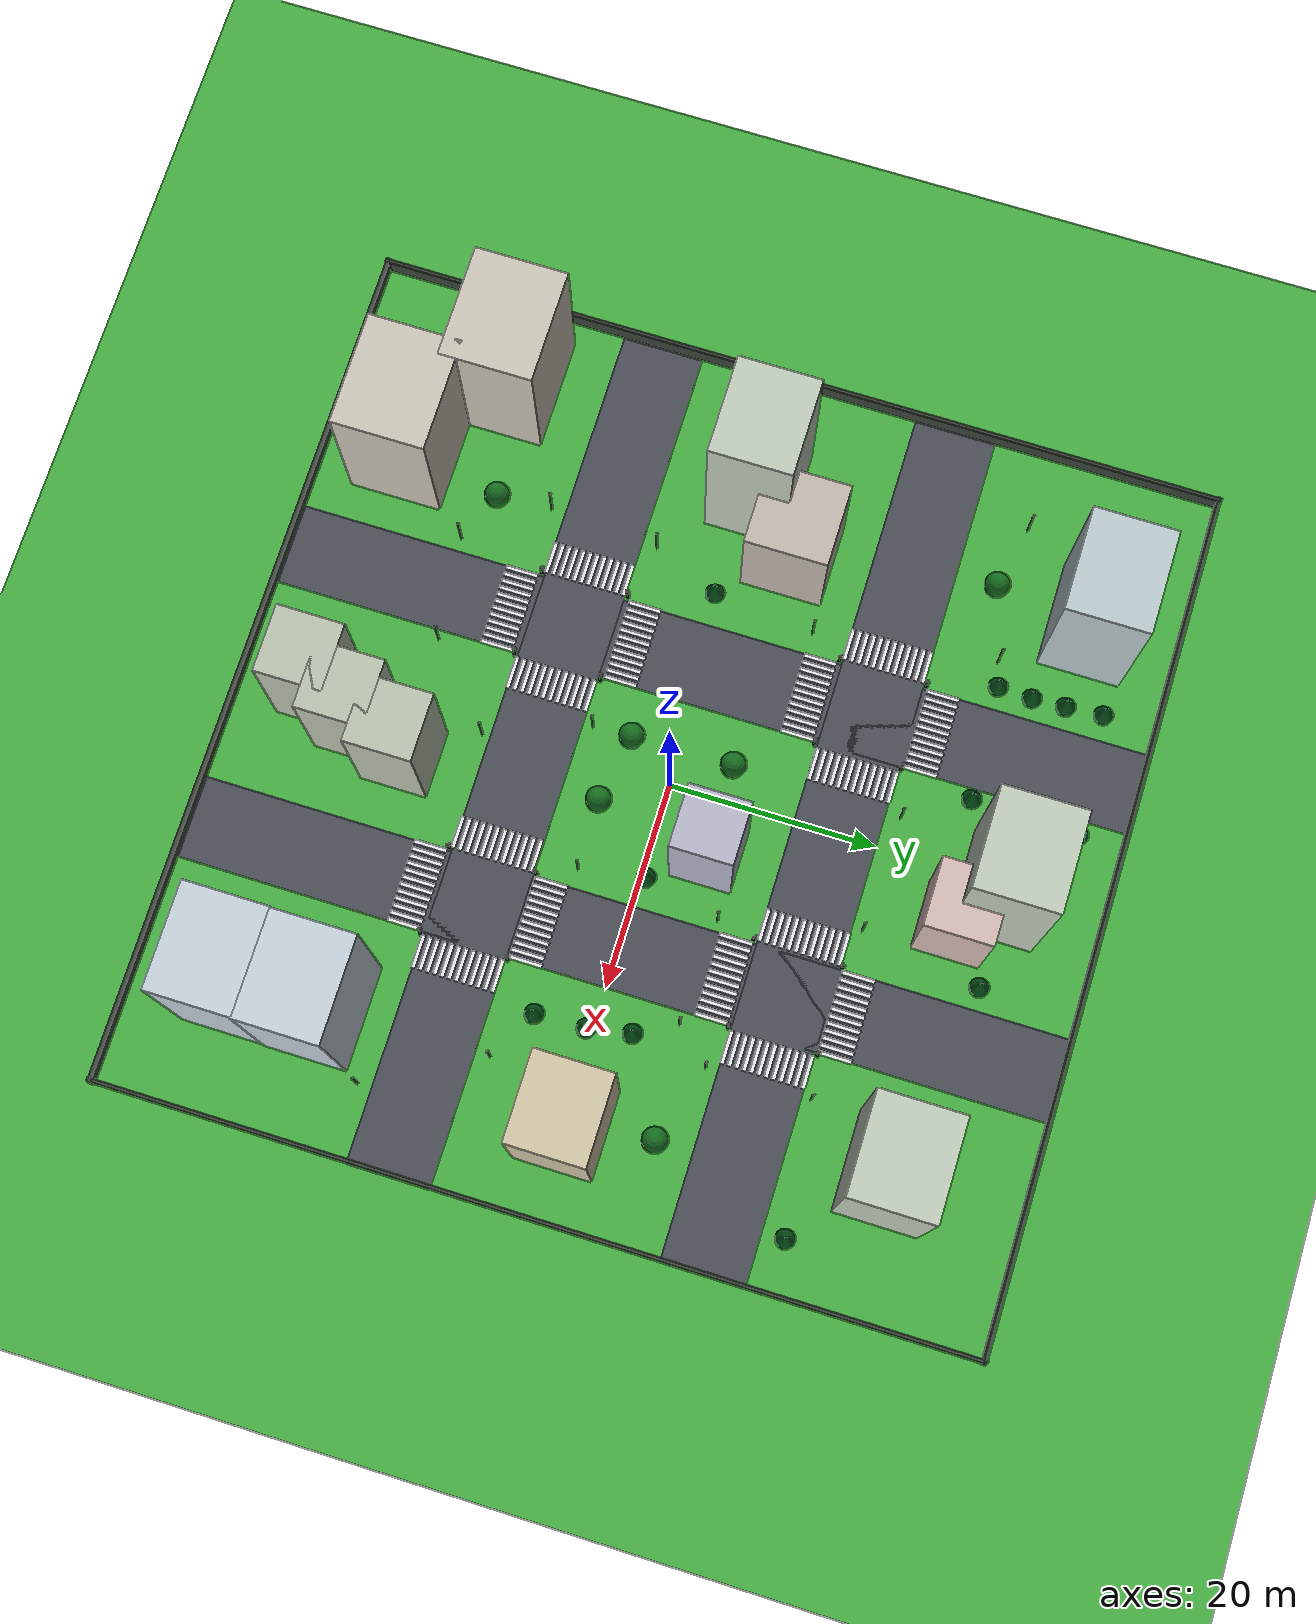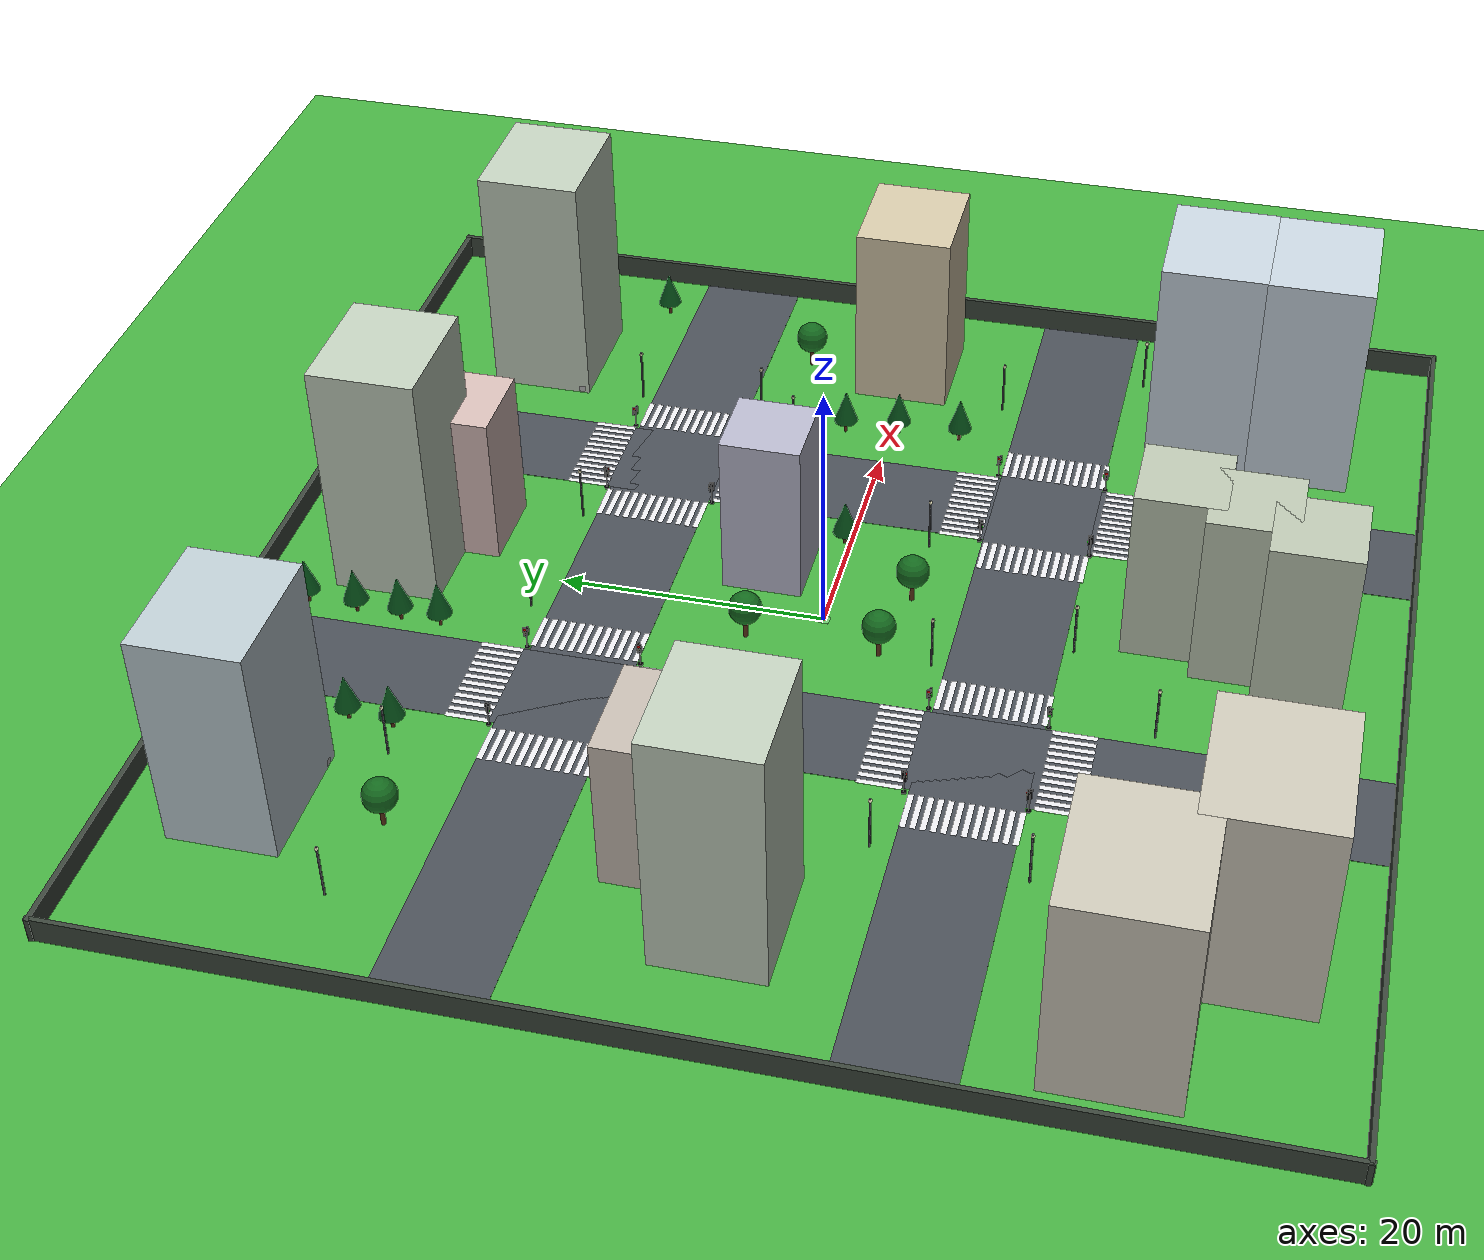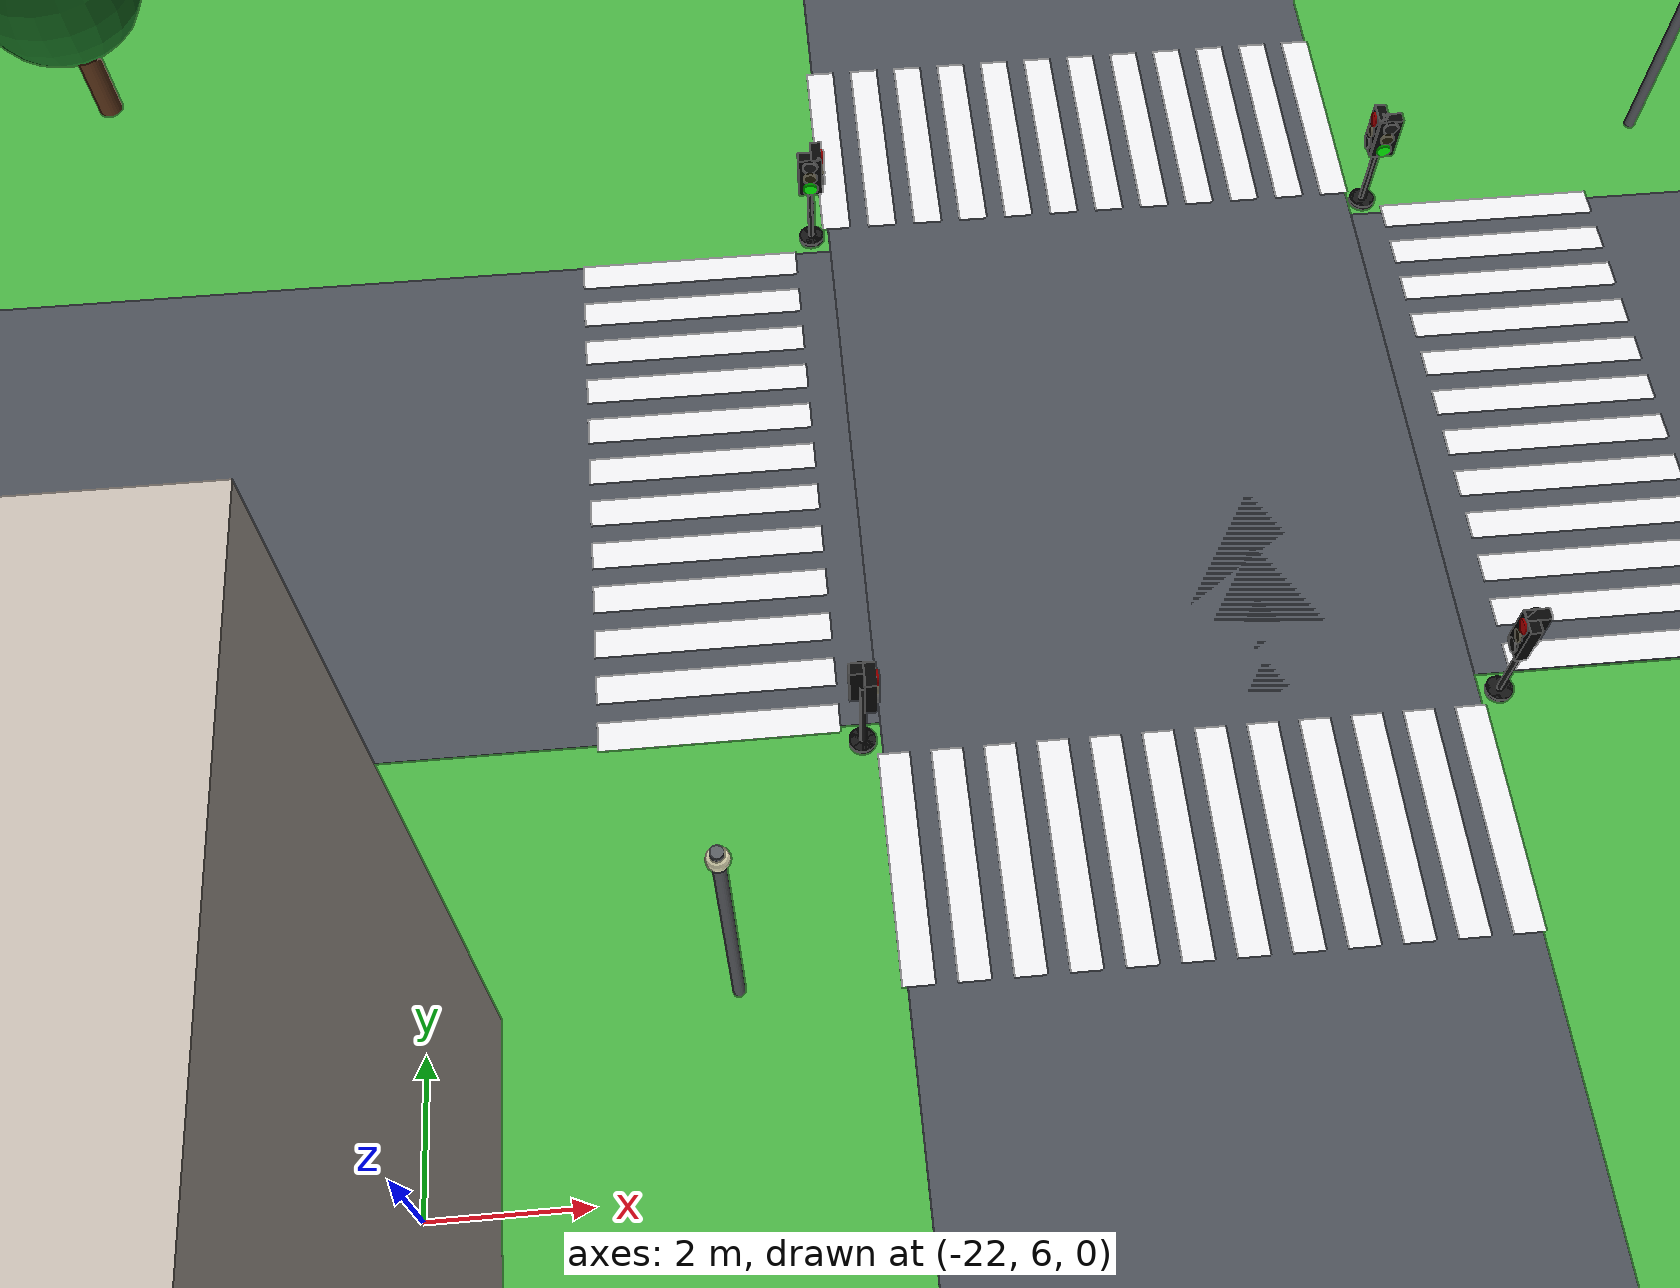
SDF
<sdf version="1.10">
 <world name="city_second">
  <gravity>0 0 -9.8100000000000005</gravity>
  <magnetic_field>6.0000000000000002e-06 2.3e-05 -4.1999999999999998e-05</magnetic_field>
  <physics name="1ms" type="ignored">
   <max_step_size>0.001</max_step_size>
   <real_time_factor>1</real_time_factor>
   <real_time_update_rate>1000</real_time_update_rate>
  </physics>
  <plugin name="gz::sim::systems::Physics" filename="gz-sim-physics-system"/>
  <plugin name="gz::sim::systems::UserCommands" filename="gz-sim-user-commands-system"/>
  <plugin name="gz::sim::systems::SceneBroadcaster" filename="gz-sim-scene-broadcaster-system"/>
  <plugin name="gz::sim::systems::Sensors" filename="gz-sim-sensors-system">
   <render_engine>ogre2</render_engine>
  </plugin>
  <scene>
   <ambient>0.699999988 0.699999988 0.699999988 1</ambient>
   <background>0.649999976 0.75 0.850000024 1</background>
   <shadows>false</shadows>
   <grid>false</grid>
  </scene>
  <atmosphere type="adiabatic"/>
  <model name="ground_plane">
   <static>true</static>
   <link name="link">
    <collision name="collision">
     <geometry><plane><normal>0 0 1</normal><size>300 300</size></plane></geometry>
    </collision>
    <visual name="visual">
     <geometry><plane><normal>0 0 1</normal><size>300 300</size></plane></geometry>
     <material>
      <ambient>0.280000001 0.689999998 0.25999999 1</ambient>
      <diffuse>0.280000001 0.689999998 0.25999999 1</diffuse>
      <specular>0.0299999993 0.0299999993 0.0299999993 1</specular>
     </material>
    </visual>
    <inertial>
     <mass>1</mass>
     <inertia><ixx>1</ixx><ixy>0</ixy><ixz>0</ixz><iyy>1</iyy><iyz>0</iyz><izz>1</izz></inertia>
    </inertial>
   </link>
  </model>
  <model name="road_h_2">
   <static>true</static>
   <pose>0 16 0.01 0 0 0</pose>
   <link name="link">
    <collision name="collision"><geometry><box><size>84 8 0.02</size></box></geometry></collision>
    <visual name="visual">
     <geometry><box><size>84 8 0.02</size></box></geometry>
     <material>
      <ambient>0.289999992 0.310000002 0.340000004 1</ambient>
      <diffuse>0.289999992 0.310000002 0.340000004 1</diffuse>
      <specular>0.0299999993 0.0299999993 0.0299999993 1</specular>
     </material>
    </visual>
    <inertial>
     <mass>1</mass>
     <inertia><ixx>1</ixx><ixy>0</ixy><ixz>0</ixz><iyy>1</iyy><iyz>0</iyz><izz>1</izz></inertia>
    </inertial>
   </link>
  </model>
  <model name="road_v_2">
   <static>true</static>
   <pose>16 0 0.01 0 0 0</pose>
   <link name="link">
    <collision name="collision"><geometry><box><size>8 84 0.02</size></box></geometry></collision>
    <visual name="visual">
     <geometry><box><size>8 84 0.02</size></box></geometry>
     <material>
      <ambient>0.289999992 0.310000002 0.340000004 1</ambient>
      <diffuse>0.289999992 0.310000002 0.340000004 1</diffuse>
      <specular>0.0299999993 0.0299999993 0.0299999993 1</specular>
     </material>
    </visual>
    <inertial>
     <mass>1</mass>
     <inertia><ixx>1</ixx><ixy>0</ixy><ixz>0</ixz><iyy>1</iyy><iyz>0</iyz><izz>1</izz></inertia>
    </inertial>
   </link>
  </model>
  <model name="house_1_2">
   <static>true</static>
   <pose>4.5999999999999996 -24.800000000000001 7 0 0 0</pose>
   <link name="link">
    <collision name="collision"><geometry><box><size>6.5 6.5 14</size></box></geometry></collision>
    <visual name="visual">
     <geometry><box><size>6.5 6.5 14</size></box></geometry>
     <material>
      <ambient>0.730000019 0.769999981 0.689999998 1</ambient>
      <diffuse>0.730000019 0.769999981 0.689999998 1</diffuse>
      <specular>0.0299999993 0.0299999993 0.0299999993 1</specular>
     </material>
    </visual>
    <inertial>
     <mass>1</mass>
     <inertia><ixx>1</ixx><ixy>0</ixy><ixz>0</ixz><iyy>1</iyy><iyz>0</iyz><izz>1</izz></inertia>
    </inertial>
   </link>
  </model>
  <model name="house_1_3">
   <static>true</static>
   <pose>29.300000000000001 -24.300000000000001 9 0 0 0</pose>
   <link name="link">
    <collision name="collision"><geometry><box><size>10 8 18</size></box></geometry></collision>
    <visual name="visual">
     <geometry><box><size>10 8 18</size></box></geometry>
     <material>
      <ambient>0.779999971 0.829999983 0.870000005 1</ambient>
      <diffuse>0.779999971 0.829999983 0.870000005 1</diffuse>
      <specular>0.0299999993 0.0299999993 0.0299999993 1</specular>
     </material>
    </visual>
    <inertial>
     <mass>1</mass>
     <inertia><ixx>1</ixx><ixy>0</ixy><ixz>0</ixz><iyy>1</iyy><iyz>0</iyz><izz>1</izz></inertia>
    </inertial>
   </link>
  </model>
  <model name="house_2_1">
   <static>true</static>
   <pose>-25.100000000000001 4.4000000000000004 6 0 0 0</pose>
   <link name="link">
    <collision name="collision"><geometry><box><size>8 8 12</size></box></geometry></collision>
    <visual name="visual">
     <geometry><box><size>8 8 12</size></box></geometry>
     <material>
      <ambient>0.769999981 0.730000019 0.689999998 1</ambient>
      <diffuse>0.769999981 0.730000019 0.689999998 1</diffuse>
      <specular>0.0299999993 0.0299999993 0.0299999993 1</specular>
     </material>
    </visual>
    <inertial>
     <mass>1</mass>
     <inertia><ixx>1</ixx><ixy>0</ixy><ixz>0</ixz><iyy>1</iyy><iyz>0</iyz><izz>1</izz></inertia>
    </inertial>
   </link>
  </model>
  <model name="house_2_2">
   <static>true</static>
   <pose>5.2000000000000002 5.2999999999999998 6.5 0 0 0</pose>
   <link name="link">
    <collision name="collision"><geometry><box><size>6 6 13</size></box></geometry></collision>
    <visual name="visual">
     <geometry><box><size>6 6 13</size></box></geometry>
     <material>
      <ambient>0.720000029 0.720000029 0.800000012 1</ambient>
      <diffuse>0.720000029 0.720000029 0.800000012 1</diffuse>
      <specular>0.0299999993 0.0299999993 0.0299999993 1</specular>
     </material>
    </visual>
    <inertial>
     <mass>1</mass>
     <inertia><ixx>1</ixx><ixy>0</ixy><ixz>0</ixz><iyy>1</iyy><iyz>0</iyz><izz>1</izz></inertia>
    </inertial>
   </link>
  </model>
  <model name="house_3_2">
   <static>true</static>
   <pose>4.9000000000000004 28.899999999999999 6 0 0 0</pose>
   <link name="link">
    <collision name="collision"><geometry><box><size>6.5 6.5 12</size></box></geometry></collision>
    <visual name="visual">
     <geometry><box><size>6.5 6.5 12</size></box></geometry>
     <material>
      <ambient>0.839999974 0.74000001 0.720000029 1</ambient>
      <diffuse>0.839999974 0.74000001 0.720000029 1</diffuse>
      <specular>0.0299999993 0.0299999993 0.0299999993 1</specular>
     </material>
    </visual>
    <inertial>
     <mass>1</mass>
     <inertia><ixx>1</ixx><ixy>0</ixy><ixz>0</ixz><iyy>1</iyy><iyz>0</iyz><izz>1</izz></inertia>
    </inertial>
   </link>
  </model>
  <model name="house_3_3">
   <static>true</static>
   <pose>28.600000000000001 29.399999999999999 9.5 0 0 0</pose>
   <link name="link">
    <collision name="collision"><geometry><box><size>9.5 8 19</size></box></geometry></collision>
    <visual name="visual">
     <geometry><box><size>9.5 8 19</size></box></geometry>
     <material>
      <ambient>0.75999999 0.810000002 0.74000001 1</ambient>
      <diffuse>0.75999999 0.810000002 0.74000001 1</diffuse>
      <specular>0.0299999993 0.0299999993 0.0299999993 1</specular>
     </material>
    </visual>
    <inertial>
     <mass>1</mass>
     <inertia><ixx>1</ixx><ixy>0</ixy><ixz>0</ixz><iyy>1</iyy><iyz>0</iyz><izz>1</izz></inertia>
    </inertial>
   </link>
  </model>
  <model name="robot_spawn_sidewalk_hint">
   <static>true</static>
   <pose>0 0 0.021000000000000001 0 0 0</pose>
   <link name="link">
    <visual name="visual">
     <geometry><box><size>0.80000000000000004 0.80000000000000004 0.0050000000000000001</size></box></geometry>
     <material>
      <ambient>0.550000012 0.860000014 0.569999993 0.649999976</ambient>
      <diffuse>0.550000012 0.860000014 0.569999993 0.649999976</diffuse>
      <specular>0 0 0 1</specular>
     </material>
     <transparency>0.34999999999999998</transparency>
    </visual>
    <inertial>
     <mass>1</mass>
     <inertia><ixx>1</ixx><ixy>0</ixy><ixz>0</ixz><iyy>1</iyy><iyz>0</iyz><izz>1</izz></inertia>
    </inertial>
   </link>
  </model>
  <model name="fence_north">
   <static>true</static>
   <pose>0 42 0.94999999999999996 0 0 0</pose>
   <link name="link">
    <collision name="collision">
     <geometry><box><size>84.5 0.34999999999999998 1.8999999999999999</size></box></geometry>
    </collision>
    <visual name="visual">
     <geometry><box><size>84.5 0.34999999999999998 1.8999999999999999</size></box></geometry>
     <material>
      <ambient>0.230000004 0.270000011 0.230000004 1</ambient>
      <diffuse>0.230000004 0.270000011 0.230000004 1</diffuse>
      <specular>0.0299999993 0.0299999993 0.0299999993 1</specular>
     </material>
    </visual>
    <inertial>
     <mass>1</mass>
     <inertia><ixx>1</ixx><ixy>0</ixy><ixz>0</ixz><iyy>1</iyy><iyz>0</iyz><izz>1</izz></inertia>
    </inertial>
   </link>
  </model>
  <model name="fence_south">
   <static>true</static>
   <pose>0 -42 0.94999999999999996 0 0 0</pose>
   <link name="link">
    <collision name="collision">
     <geometry><box><size>84.5 0.34999999999999998 1.8999999999999999</size></box></geometry>
    </collision>
    <visual name="visual">
     <geometry><box><size>84.5 0.34999999999999998 1.8999999999999999</size></box></geometry>
     <material>
      <ambient>0.230000004 0.270000011 0.230000004 1</ambient>
      <diffuse>0.230000004 0.270000011 0.230000004 1</diffuse>
      <specular>0.0299999993 0.0299999993 0.0299999993 1</specular>
     </material>
    </visual>
    <inertial>
     <mass>1</mass>
     <inertia><ixx>1</ixx><ixy>0</ixy><ixz>0</ixz><iyy>1</iyy><iyz>0</iyz><izz>1</izz></inertia>
    </inertial>
   </link>
  </model>
  <model name="fence_east">
   <static>true</static>
   <pose>42 0 0.94999999999999996 0 0 0</pose>
   <link name="link">
    <collision name="collision">
     <geometry><box><size>0.34999999999999998 84.5 1.8999999999999999</size></box></geometry>
    </collision>
    <visual name="visual">
     <geometry><box><size>0.34999999999999998 84.5 1.8999999999999999</size></box></geometry>
     <material>
      <ambient>0.230000004 0.270000011 0.230000004 1</ambient>
      <diffuse>0.230000004 0.270000011 0.230000004 1</diffuse>
      <specular>0.0299999993 0.0299999993 0.0299999993 1</specular>
     </material>
    </visual>
    <inertial>
     <mass>1</mass>
     <inertia><ixx>1</ixx><ixy>0</ixy><ixz>0</ixz><iyy>1</iyy><iyz>0</iyz><izz>1</izz></inertia>
    </inertial>
   </link>
  </model>
  <model name="fence_west">
   <static>true</static>
   <pose>-42 0 0.94999999999999996 0 0 0</pose>
   <link name="link">
    <collision name="collision">
     <geometry><box><size>0.34999999999999998 84.5 1.8999999999999999</size></box></geometry>
    </collision>
    <visual name="visual">
     <geometry><box><size>0.34999999999999998 84.5 1.8999999999999999</size></box></geometry>
     <material>
      <ambient>0.230000004 0.270000011 0.230000004 1</ambient>
      <diffuse>0.230000004 0.270000011 0.230000004 1</diffuse>
      <specular>0.0299999993 0.0299999993 0.0299999993 1</specular>
     </material>
    </visual>
    <inertial>
     <mass>1</mass>
     <inertia><ixx>1</ixx><ixy>0</ixy><ixz>0</ixz><iyy>1</iyy><iyz>0</iyz><izz>1</izz></inertia>
    </inertial>
   </link>
  </model>
  <model name="crosswalk_h_1_1_south_5">
   <static>true</static>
   <pose>16.0335 21.8659 0.017000000000000001 0 0 0</pose>
   <link name="stripe_1">
    <collision name="collision">
     <geometry><box><size>0.41999999999999998 3.2000000000000002 0.01</size></box></geometry>
    </collision>
    <visual name="visual">
     <geometry><box><size>0.41999999999999998 3.2000000000000002 0.01</size></box></geometry>
     <material>
      <ambient>0.920000017 0.920000017 0.930000007 1</ambient>
      <diffuse>0.920000017 0.920000017 0.930000007 1</diffuse>
      <specular>0.0299999993 0.0299999993 0.0299999993 1</specular>
     </material>
    </visual>
    <pose>-3.8500000000000001 0 0 0 0 0</pose>
    <inertial>
     <mass>1</mass>
     <inertia><ixx>1</ixx><ixy>0</ixy><ixz>0</ixz><iyy>1</iyy><iyz>0</iyz><izz>1</izz></inertia>
    </inertial>
   </link>
   <link name="stripe_2">
    <collision name="collision">
     <geometry><box><size>0.41999999999999998 3.2000000000000002 0.01</size></box></geometry>
    </collision>
    <visual name="visual">
     <geometry><box><size>0.41999999999999998 3.2000000000000002 0.01</size></box></geometry>
     <material>
      <ambient>0.920000017 0.920000017 0.930000007 1</ambient>
      <diffuse>0.920000017 0.920000017 0.930000007 1</diffuse>
      <specular>0.0299999993 0.0299999993 0.0299999993 1</specular>
     </material>
    </visual>
    <pose>-3.1500000000000004 0 0 0 0 0</pose>
    <inertial>
     <mass>1</mass>
     <inertia><ixx>1</ixx><ixy>0</ixy><ixz>0</ixz><iyy>1</iyy><iyz>0</iyz><izz>1</izz></inertia>
    </inertial>
   </link>
   <link name="stripe_3">
    <collision name="collision">
     <geometry><box><size>0.41999999999999998 3.2000000000000002 0.01</size></box></geometry>
    </collision>
    <visual name="visual">
     <geometry><box><size>0.41999999999999998 3.2000000000000002 0.01</size></box></geometry>
     <material>
      <ambient>0.920000017 0.920000017 0.930000007 1</ambient>
      <diffuse>0.920000017 0.920000017 0.930000007 1</diffuse>
      <specular>0.0299999993 0.0299999993 0.0299999993 1</specular>
     </material>
    </visual>
    <pose>-2.4499999999999993 0 0 0 0 0</pose>
    <inertial>
     <mass>1</mass>
     <inertia><ixx>1</ixx><ixy>0</ixy><ixz>0</ixz><iyy>1</iyy><iyz>0</iyz><izz>1</izz></inertia>
    </inertial>
   </link>
   <link name="stripe_4">
    <collision name="collision">
     <geometry><box><size>0.41999999999999998 3.2000000000000002 0.01</size></box></geometry>
    </collision>
    <visual name="visual">
     <geometry><box><size>0.41999999999999998 3.2000000000000002 0.01</size></box></geometry>
     <material>
      <ambient>0.920000017 0.920000017 0.930000007 1</ambient>
      <diffuse>0.920000017 0.920000017 0.930000007 1</diffuse>
      <specular>0.0299999993 0.0299999993 0.0299999993 1</specular>
     </material>
    </visual>
    <pose>-1.75 0 0 0 0 0</pose>
    <inertial>
     <mass>1</mass>
     <inertia><ixx>1</ixx><ixy>0</ixy><ixz>0</ixz><iyy>1</iyy><iyz>0</iyz><izz>1</izz></inertia>
    </inertial>
   </link>
   <link name="stripe_5">
    <collision name="collision">
     <geometry><box><size>0.41999999999999998 3.2000000000000002 0.01</size></box></geometry>
    </collision>
    <visual name="visual">
     <geometry><box><size>0.41999999999999998 3.2000000000000002 0.01</size></box></geometry>
     <material>
      <ambient>0.920000017 0.920000017 0.930000007 1</ambient>
      <diffuse>0.920000017 0.920000017 0.930000007 1</diffuse>
      <specular>0.0299999993 0.0299999993 0.0299999993 1</specular>
     </material>
    </visual>
    <pose>-1.0500000000000007 0 0 0 0 0</pose>
    <inertial>
     <mass>1</mass>
     <inertia><ixx>1</ixx><ixy>0</ixy><ixz>0</ixz><iyy>1</iyy><iyz>0</iyz><izz>1</izz></inertia>
    </inertial>
   </link>
   <link name="stripe_6">
    <collision name="collision">
     <geometry><box><size>0.41999999999999998 3.2000000000000002 0.01</size></box></geometry>
    </collision>
    <visual name="visual">
     <geometry><box><size>0.41999999999999998 3.2000000000000002 0.01</size></box></geometry>
     <material>
      <ambient>0.920000017 0.920000017 0.930000007 1</ambient>
      <diffuse>0.920000017 0.920000017 0.930000007 1</diffuse>
      <specular>0.0299999993 0.0299999993 0.0299999993 1</specular>
     </material>
    </visual>
    <pose>-0.34999999999999964 0 0 0 0 0</pose>
    <inertial>
     <mass>1</mass>
     <inertia><ixx>1</ixx><ixy>0</ixy><ixz>0</ixz><iyy>1</iyy><iyz>0</iyz><izz>1</izz></inertia>
    </inertial>
   </link>
   <link name="stripe_7">
    <collision name="collision">
     <geometry><box><size>0.41999999999999998 3.2000000000000002 0.01</size></box></geometry>
    </collision>
    <visual name="visual">
     <geometry><box><size>0.41999999999999998 3.2000000000000002 0.01</size></box></geometry>
     <material>
      <ambient>0.920000017 0.920000017 0.930000007 1</ambient>
      <diffuse>0.920000017 0.920000017 0.930000007 1</diffuse>
      <specular>0.0299999993 0.0299999993 0.0299999993 1</specular>
     </material>
    </visual>
    <pose>0.35000000000000142 0 0 0 0 0</pose>
    <inertial>
     <mass>1</mass>
     <inertia><ixx>1</ixx><ixy>0</ixy><ixz>0</ixz><iyy>1</iyy><iyz>0</iyz><izz>1</izz></inertia>
    </inertial>
   </link>
   <link name="stripe_8">
    <collision name="collision">
     <geometry><box><size>0.41999999999999998 3.2000000000000002 0.01</size></box></geometry>
    </collision>
    <visual name="visual">
     <geometry><box><size>0.41999999999999998 3.2000000000000002 0.01</size></box></geometry>
     <material>
      <ambient>0.920000017 0.920000017 0.930000007 1</ambient>
      <diffuse>0.920000017 0.920000017 0.930000007 1</diffuse>
      <specular>0.0299999993 0.0299999993 0.0299999993 1</specular>
     </material>
    </visual>
    <pose>1.0500000000000007 0 0 0 0 0</pose>
    <inertial>
     <mass>1</mass>
     <inertia><ixx>1</ixx><ixy>0</ixy><ixz>0</ixz><iyy>1</iyy><iyz>0</iyz><izz>1</izz></inertia>
    </inertial>
   </link>
   <link name="stripe_9">
    <collision name="collision">
     <geometry><box><size>0.41999999999999998 3.2000000000000002 0.01</size></box></geometry>
    </collision>
    <visual name="visual">
     <geometry><box><size>0.41999999999999998 3.2000000000000002 0.01</size></box></geometry>
     <material>
      <ambient>0.920000017 0.920000017 0.930000007 1</ambient>
      <diffuse>0.920000017 0.920000017 0.930000007 1</diffuse>
      <specular>0.0299999993 0.0299999993 0.0299999993 1</specular>
     </material>
    </visual>
    <pose>1.75 0 0 0 0 0</pose>
    <inertial>
     <mass>1</mass>
     <inertia><ixx>1</ixx><ixy>0</ixy><ixz>0</ixz><iyy>1</iyy><iyz>0</iyz><izz>1</izz></inertia>
    </inertial>
   </link>
   <link name="stripe_10">
    <collision name="collision">
     <geometry><box><size>0.41999999999999998 3.2000000000000002 0.01</size></box></geometry>
    </collision>
    <visual name="visual">
     <geometry><box><size>0.41999999999999998 3.2000000000000002 0.01</size></box></geometry>
     <material>
      <ambient>0.920000017 0.920000017 0.930000007 1</ambient>
      <diffuse>0.920000017 0.920000017 0.930000007 1</diffuse>
      <specular>0.0299999993 0.0299999993 0.0299999993 1</specular>
     </material>
    </visual>
    <pose>2.4499999999999993 0 0 0 0 0</pose>
    <inertial>
     <mass>1</mass>
     <inertia><ixx>1</ixx><ixy>0</ixy><ixz>0</ixz><iyy>1</iyy><iyz>0</iyz><izz>1</izz></inertia>
    </inertial>
   </link>
   <link name="stripe_11">
    <collision name="collision">
     <geometry><box><size>0.41999999999999998 3.2000000000000002 0.01</size></box></geometry>
    </collision>
    <visual name="visual">
     <geometry><box><size>0.41999999999999998 3.2000000000000002 0.01</size></box></geometry>
     <material>
      <ambient>0.920000017 0.920000017 0.930000007 1</ambient>
      <diffuse>0.920000017 0.920000017 0.930000007 1</diffuse>
      <specular>0.0299999993 0.0299999993 0.0299999993 1</specular>
     </material>
    </visual>
    <pose>3.1499999999999986 0 0 0 0 0</pose>
    <inertial>
     <mass>1</mass>
     <inertia><ixx>1</ixx><ixy>0</ixy><ixz>0</ixz><iyy>1</iyy><iyz>0</iyz><izz>1</izz></inertia>
    </inertial>
   </link>
   <link name="stripe_12">
    <collision name="collision">
     <geometry><box><size>0.41999999999999998 3.2000000000000002 0.01</size></box></geometry>
    </collision>
    <visual name="visual">
     <geometry><box><size>0.41999999999999998 3.2000000000000002 0.01</size></box></geometry>
     <material>
      <ambient>0.920000017 0.920000017 0.930000007 1</ambient>
      <diffuse>0.920000017 0.920000017 0.930000007 1</diffuse>
      <specular>0.0299999993 0.0299999993 0.0299999993 1</specular>
     </material>
    </visual>
    <pose>3.8500000000000014 0 0 0 0 0</pose>
    <inertial>
     <mass>1</mass>
     <inertia><ixx>1</ixx><ixy>0</ixy><ixz>0</ixz><iyy>1</iyy><iyz>0</iyz><izz>1</izz></inertia>
    </inertial>
   </link>
  </model>
  <model name="crosswalk_h_1_1_south_6">
   <static>true</static>
   <pose>15.980700000000001 10.0922 0.017000000000000001 0 0 0</pose>
   <link name="stripe_1">
    <collision name="collision">
     <geometry><box><size>0.41999999999999998 3.2000000000000002 0.01</size></box></geometry>
    </collision>
    <visual name="visual">
     <geometry><box><size>0.41999999999999998 3.2000000000000002 0.01</size></box></geometry>
     <material>
      <ambient>0.920000017 0.920000017 0.930000007 1</ambient>
      <diffuse>0.920000017 0.920000017 0.930000007 1</diffuse>
      <specular>0.0299999993 0.0299999993 0.0299999993 1</specular>
     </material>
    </visual>
    <pose>-3.8500000000000001 0 0 0 0 0</pose>
    <inertial>
     <mass>1</mass>
     <inertia><ixx>1</ixx><ixy>0</ixy><ixz>0</ixz><iyy>1</iyy><iyz>0</iyz><izz>1</izz></inertia>
    </inertial>
   </link>
   <link name="stripe_2">
    <collision name="collision">
     <geometry><box><size>0.41999999999999998 3.2000000000000002 0.01</size></box></geometry>
    </collision>
    <visual name="visual">
     <geometry><box><size>0.41999999999999998 3.2000000000000002 0.01</size></box></geometry>
     <material>
      <ambient>0.920000017 0.920000017 0.930000007 1</ambient>
      <diffuse>0.920000017 0.920000017 0.930000007 1</diffuse>
      <specular>0.0299999993 0.0299999993 0.0299999993 1</specular>
     </material>
    </visual>
    <pose>-3.1500000000000004 0 0 0 0 0</pose>
    <inertial>
     <mass>1</mass>
     <inertia><ixx>1</ixx><ixy>0</ixy><ixz>0</ixz><iyy>1</iyy><iyz>0</iyz><izz>1</izz></inertia>
    </inertial>
   </link>
   <link name="stripe_3">
    <collision name="collision">
     <geometry><box><size>0.41999999999999998 3.2000000000000002 0.01</size></box></geometry>
    </collision>
    <visual name="visual">
     <geometry><box><size>0.41999999999999998 3.2000000000000002 0.01</size></box></geometry>
     <material>
      <ambient>0.920000017 0.920000017 0.930000007 1</ambient>
      <diffuse>0.920000017 0.920000017 0.930000007 1</diffuse>
      <specular>0.0299999993 0.0299999993 0.0299999993 1</specular>
     </material>
    </visual>
    <pose>-2.4500000000000011 0 0 0 0 0</pose>
    <inertial>
     <mass>1</mass>
     <inertia><ixx>1</ixx><ixy>0</ixy><ixz>0</ixz><iyy>1</iyy><iyz>0</iyz><izz>1</izz></inertia>
    </inertial>
   </link>
   <link name="stripe_4">
    <collision name="collision">
     <geometry><box><size>0.41999999999999998 3.2000000000000002 0.01</size></box></geometry>
    </collision>
    <visual name="visual">
     <geometry><box><size>0.41999999999999998 3.2000000000000002 0.01</size></box></geometry>
     <material>
      <ambient>0.920000017 0.920000017 0.930000007 1</ambient>
      <diffuse>0.920000017 0.920000017 0.930000007 1</diffuse>
      <specular>0.0299999993 0.0299999993 0.0299999993 1</specular>
     </material>
    </visual>
    <pose>-1.75 0 0 0 0 0</pose>
    <inertial>
     <mass>1</mass>
     <inertia><ixx>1</ixx><ixy>0</ixy><ixz>0</ixz><iyy>1</iyy><iyz>0</iyz><izz>1</izz></inertia>
    </inertial>
   </link>
   <link name="stripe_5">
    <collision name="collision">
     <geometry><box><size>0.41999999999999998 3.2000000000000002 0.01</size></box></geometry>
    </collision>
    <visual name="visual">
     <geometry><box><size>0.41999999999999998 3.2000000000000002 0.01</size></box></geometry>
     <material>
      <ambient>0.920000017 0.920000017 0.930000007 1</ambient>
      <diffuse>0.920000017 0.920000017 0.930000007 1</diffuse>
      <specular>0.0299999993 0.0299999993 0.0299999993 1</specular>
     </material>
    </visual>
    <pose>-1.0500000000000007 0 0 0 0 0</pose>
    <inertial>
     <mass>1</mass>
     <inertia><ixx>1</ixx><ixy>0</ixy><ixz>0</ixz><iyy>1</iyy><iyz>0</iyz><izz>1</izz></inertia>
    </inertial>
   </link>
   <link name="stripe_6">
    <collision name="collision">
     <geometry><box><size>0.41999999999999998 3.2000000000000002 0.01</size></box></geometry>
    </collision>
    <visual name="visual">
     <geometry><box><size>0.41999999999999998 3.2000000000000002 0.01</size></box></geometry>
     <material>
      <ambient>0.920000017 0.920000017 0.930000007 1</ambient>
      <diffuse>0.920000017 0.920000017 0.930000007 1</diffuse>
      <specular>0.0299999993 0.0299999993 0.0299999993 1</specular>
     </material>
    </visual>
    <pose>-0.34999999999999964 0 0 0 0 0</pose>
    <inertial>
     <mass>1</mass>
     <inertia><ixx>1</ixx><ixy>0</ixy><ixz>0</ixz><iyy>1</iyy><iyz>0</iyz><izz>1</izz></inertia>
    </inertial>
   </link>
   <link name="stripe_7">
    <collision name="collision">
     <geometry><box><size>0.41999999999999998 3.2000000000000002 0.01</size></box></geometry>
    </collision>
    <visual name="visual">
     <geometry><box><size>0.41999999999999998 3.2000000000000002 0.01</size></box></geometry>
     <material>
      <ambient>0.920000017 0.920000017 0.930000007 1</ambient>
      <diffuse>0.920000017 0.920000017 0.930000007 1</diffuse>
      <specular>0.0299999993 0.0299999993 0.0299999993 1</specular>
     </material>
    </visual>
    <pose>0.34999999999999964 0 0 0 0 0</pose>
    <inertial>
     <mass>1</mass>
     <inertia><ixx>1</ixx><ixy>0</ixy><ixz>0</ixz><iyy>1</iyy><iyz>0</iyz><izz>1</izz></inertia>
    </inertial>
   </link>
   <link name="stripe_8">
    <collision name="collision">
     <geometry><box><size>0.41999999999999998 3.2000000000000002 0.01</size></box></geometry>
    </collision>
    <visual name="visual">
     <geometry><box><size>0.41999999999999998 3.2000000000000002 0.01</size></box></geometry>
     <material>
      <ambient>0.920000017 0.920000017 0.930000007 1</ambient>
      <diffuse>0.920000017 0.920000017 0.930000007 1</diffuse>
      <specular>0.0299999993 0.0299999993 0.0299999993 1</specular>
     </material>
    </visual>
    <pose>1.0499999999999989 0 0 0 0 0</pose>
    <inertial>
     <mass>1</mass>
     <inertia><ixx>1</ixx><ixy>0</ixy><ixz>0</ixz><iyy>1</iyy><iyz>0</iyz><izz>1</izz></inertia>
    </inertial>
   </link>
   <link name="stripe_9">
    <collision name="collision">
     <geometry><box><size>0.41999999999999998 3.2000000000000002 0.01</size></box></geometry>
    </collision>
    <visual name="visual">
     <geometry><box><size>0.41999999999999998 3.2000000000000002 0.01</size></box></geometry>
     <material>
      <ambient>0.920000017 0.920000017 0.930000007 1</ambient>
      <diffuse>0.920000017 0.920000017 0.930000007 1</diffuse>
      <specular>0.0299999993 0.0299999993 0.0299999993 1</specular>
     </material>
    </visual>
    <pose>1.7499999999999982 0 0 0 0 0</pose>
    <inertial>
     <mass>1</mass>
     <inertia><ixx>1</ixx><ixy>0</ixy><ixz>0</ixz><iyy>1</iyy><iyz>0</iyz><izz>1</izz></inertia>
    </inertial>
   </link>
   <link name="stripe_10">
    <collision name="collision">
     <geometry><box><size>0.41999999999999998 3.2000000000000002 0.01</size></box></geometry>
    </collision>
    <visual name="visual">
     <geometry><box><size>0.41999999999999998 3.2000000000000002 0.01</size></box></geometry>
     <material>
      <ambient>0.920000017 0.920000017 0.930000007 1</ambient>
      <diffuse>0.920000017 0.920000017 0.930000007 1</diffuse>
      <specular>0.0299999993 0.0299999993 0.0299999993 1</specular>
     </material>
    </visual>
    <pose>2.4500000000000011 0 0 0 0 0</pose>
    <inertial>
     <mass>1</mass>
     <inertia><ixx>1</ixx><ixy>0</ixy><ixz>0</ixz><iyy>1</iyy><iyz>0</iyz><izz>1</izz></inertia>
    </inertial>
   </link>
   <link name="stripe_11">
    <collision name="collision">
     <geometry><box><size>0.41999999999999998 3.2000000000000002 0.01</size></box></geometry>
    </collision>
    <visual name="visual">
     <geometry><box><size>0.41999999999999998 3.2000000000000002 0.01</size></box></geometry>
     <material>
      <ambient>0.920000017 0.920000017 0.930000007 1</ambient>
      <diffuse>0.920000017 0.920000017 0.930000007 1</diffuse>
      <specular>0.0299999993 0.0299999993 0.0299999993 1</specular>
     </material>
    </visual>
    <pose>3.1500000000000004 0 0 0 0 0</pose>
    <inertial>
     <mass>1</mass>
     <inertia><ixx>1</ixx><ixy>0</ixy><ixz>0</ixz><iyy>1</iyy><iyz>0</iyz><izz>1</izz></inertia>
    </inertial>
   </link>
   <link name="stripe_12">
    <collision name="collision">
     <geometry><box><size>0.41999999999999998 3.2000000000000002 0.01</size></box></geometry>
    </collision>
    <visual name="visual">
     <geometry><box><size>0.41999999999999998 3.2000000000000002 0.01</size></box></geometry>
     <material>
      <ambient>0.920000017 0.920000017 0.930000007 1</ambient>
      <diffuse>0.920000017 0.920000017 0.930000007 1</diffuse>
      <specular>0.0299999993 0.0299999993 0.0299999993 1</specular>
     </material>
    </visual>
    <pose>3.8499999999999996 0 0 0 0 0</pose>
    <inertial>
     <mass>1</mass>
     <inertia><ixx>1</ixx><ixy>0</ixy><ixz>0</ixz><iyy>1</iyy><iyz>0</iyz><izz>1</izz></inertia>
    </inertial>
   </link>
  </model>
  <model name="crosswalk_v_2_1_east_6">
   <static>true</static>
   <pose>10.091699999999999 16.024799999999999 0.017000000000000001 0 0 0</pose>
   <link name="stripe_1">
    <collision name="collision">
     <geometry><box><size>3.2000000000000002 0.41999999999999998 0.01</size></box></geometry>
    </collision>
    <visual name="visual">
     <geometry><box><size>3.2000000000000002 0.41999999999999998 0.01</size></box></geometry>
     <material>
      <ambient>0.920000017 0.920000017 0.930000007 1</ambient>
      <diffuse>0.920000017 0.920000017 0.930000007 1</diffuse>
      <specular>0.0299999993 0.0299999993 0.0299999993 1</specular>
     </material>
    </visual>
    <pose>0 -3.8500000000000001 0 0 0 0</pose>
    <inertial>
     <mass>1</mass>
     <inertia><ixx>1</ixx><ixy>0</ixy><ixz>0</ixz><iyy>1</iyy><iyz>0</iyz><izz>1</izz></inertia>
    </inertial>
   </link>
   <link name="stripe_2">
    <collision name="collision">
     <geometry><box><size>3.2000000000000002 0.41999999999999998 0.01</size></box></geometry>
    </collision>
    <visual name="visual">
     <geometry><box><size>3.2000000000000002 0.41999999999999998 0.01</size></box></geometry>
     <material>
      <ambient>0.920000017 0.920000017 0.930000007 1</ambient>
      <diffuse>0.920000017 0.920000017 0.930000007 1</diffuse>
      <specular>0.0299999993 0.0299999993 0.0299999993 1</specular>
     </material>
    </visual>
    <pose>0 -3.1500000000000004 0 0 0 0</pose>
    <inertial>
     <mass>1</mass>
     <inertia><ixx>1</ixx><ixy>0</ixy><ixz>0</ixz><iyy>1</iyy><iyz>0</iyz><izz>1</izz></inertia>
    </inertial>
   </link>
   <link name="stripe_3">
    <collision name="collision">
     <geometry><box><size>3.2000000000000002 0.41999999999999998 0.01</size></box></geometry>
    </collision>
    <visual name="visual">
     <geometry><box><size>3.2000000000000002 0.41999999999999998 0.01</size></box></geometry>
     <material>
      <ambient>0.920000017 0.920000017 0.930000007 1</ambient>
      <diffuse>0.920000017 0.920000017 0.930000007 1</diffuse>
      <specular>0.0299999993 0.0299999993 0.0299999993 1</specular>
     </material>
    </visual>
    <pose>0 -2.4499999999999993 0 0 0 0</pose>
    <inertial>
     <mass>1</mass>
     <inertia><ixx>1</ixx><ixy>0</ixy><ixz>0</ixz><iyy>1</iyy><iyz>0</iyz><izz>1</izz></inertia>
    </inertial>
   </link>
   <link name="stripe_4">
    <collision name="collision">
     <geometry><box><size>3.2000000000000002 0.41999999999999998 0.01</size></box></geometry>
    </collision>
    <visual name="visual">
     <geometry><box><size>3.2000000000000002 0.41999999999999998 0.01</size></box></geometry>
     <material>
      <ambient>0.920000017 0.920000017 0.930000007 1</ambient>
      <diffuse>0.920000017 0.920000017 0.930000007 1</diffuse>
      <specular>0.0299999993 0.0299999993 0.0299999993 1</specular>
     </material>
    </visual>
    <pose>0 -1.75 0 0 0 0</pose>
    <inertial>
     <mass>1</mass>
     <inertia><ixx>1</ixx><ixy>0</ixy><ixz>0</ixz><iyy>1</iyy><iyz>0</iyz><izz>1</izz></inertia>
    </inertial>
   </link>
   <link name="stripe_5">
    <collision name="collision">
     <geometry><box><size>3.2000000000000002 0.41999999999999998 0.01</size></box></geometry>
    </collision>
    <visual name="visual">
     <geometry><box><size>3.2000000000000002 0.41999999999999998 0.01</size></box></geometry>
     <material>
      <ambient>0.920000017 0.920000017 0.930000007 1</ambient>
      <diffuse>0.920000017 0.920000017 0.930000007 1</diffuse>
      <specular>0.0299999993 0.0299999993 0.0299999993 1</specular>
     </material>
    </visual>
    <pose>0 -1.0500000000000007 0 0 0 0</pose>
    <inertial>
     <mass>1</mass>
     <inertia><ixx>1</ixx><ixy>0</ixy><ixz>0</ixz><iyy>1</iyy><iyz>0</iyz><izz>1</izz></inertia>
    </inertial>
   </link>
   <link name="stripe_6">
    <collision name="collision">
     <geometry><box><size>3.2000000000000002 0.41999999999999998 0.01</size></box></geometry>
    </collision>
    <visual name="visual">
     <geometry><box><size>3.2000000000000002 0.41999999999999998 0.01</size></box></geometry>
     <material>
      <ambient>0.920000017 0.920000017 0.930000007 1</ambient>
      <diffuse>0.920000017 0.920000017 0.930000007 1</diffuse>
      <specular>0.0299999993 0.0299999993 0.0299999993 1</specular>
     </material>
    </visual>
    <pose>0 -0.34999999999999964 0 0 0 0</pose>
    <inertial>
     <mass>1</mass>
     <inertia><ixx>1</ixx><ixy>0</ixy><ixz>0</ixz><iyy>1</iyy><iyz>0</iyz><izz>1</izz></inertia>
    </inertial>
   </link>
   <link name="stripe_7">
    <collision name="collision">
     <geometry><box><size>3.2000000000000002 0.41999999999999998 0.01</size></box></geometry>
    </collision>
    <visual name="visual">
     <geometry><box><size>3.2000000000000002 0.41999999999999998 0.01</size></box></geometry>
     <material>
      <ambient>0.920000017 0.920000017 0.930000007 1</ambient>
      <diffuse>0.920000017 0.920000017 0.930000007 1</diffuse>
      <specular>0.0299999993 0.0299999993 0.0299999993 1</specular>
     </material>
    </visual>
    <pose>0 0.35000000000000142 0 0 0 0</pose>
    <inertial>
     <mass>1</mass>
     <inertia><ixx>1</ixx><ixy>0</ixy><ixz>0</ixz><iyy>1</iyy><iyz>0</iyz><izz>1</izz></inertia>
    </inertial>
   </link>
   <link name="stripe_8">
    <collision name="collision">
     <geometry><box><size>3.2000000000000002 0.41999999999999998 0.01</size></box></geometry>
    </collision>
    <visual name="visual">
     <geometry><box><size>3.2000000000000002 0.41999999999999998 0.01</size></box></geometry>
     <material>
      <ambient>0.920000017 0.920000017 0.930000007 1</ambient>
      <diffuse>0.920000017 0.920000017 0.930000007 1</diffuse>
      <specular>0.0299999993 0.0299999993 0.0299999993 1</specular>
     </material>
    </visual>
    <pose>0 1.0500000000000007 0 0 0 0</pose>
    <inertial>
     <mass>1</mass>
     <inertia><ixx>1</ixx><ixy>0</ixy><ixz>0</ixz><iyy>1</iyy><iyz>0</iyz><izz>1</izz></inertia>
    </inertial>
   </link>
   <link name="stripe_9">
    <collision name="collision">
     <geometry><box><size>3.2000000000000002 0.41999999999999998 0.01</size></box></geometry>
    </collision>
    <visual name="visual">
     <geometry><box><size>3.2000000000000002 0.41999999999999998 0.01</size></box></geometry>
     <material>
      <ambient>0.920000017 0.920000017 0.930000007 1</ambient>
      <diffuse>0.920000017 0.920000017 0.930000007 1</diffuse>
      <specular>0.0299999993 0.0299999993 0.0299999993 1</specular>
     </material>
    </visual>
    <pose>0 1.75 0 0 0 0</pose>
    <inertial>
     <mass>1</mass>
     <inertia><ixx>1</ixx><ixy>0</ixy><ixz>0</ixz><iyy>1</iyy><iyz>0</iyz><izz>1</izz></inertia>
    </inertial>
   </link>
   <link name="stripe_10">
    <collision name="collision">
     <geometry><box><size>3.2000000000000002 0.41999999999999998 0.01</size></box></geometry>
    </collision>
    <visual name="visual">
     <geometry><box><size>3.2000000000000002 0.41999999999999998 0.01</size></box></geometry>
     <material>
      <ambient>0.920000017 0.920000017 0.930000007 1</ambient>
      <diffuse>0.920000017 0.920000017 0.930000007 1</diffuse>
      <specular>0.0299999993 0.0299999993 0.0299999993 1</specular>
     </material>
    </visual>
    <pose>0 2.4499999999999993 0 0 0 0</pose>
    <inertial>
     <mass>1</mass>
     <inertia><ixx>1</ixx><ixy>0</ixy><ixz>0</ixz><iyy>1</iyy><iyz>0</iyz><izz>1</izz></inertia>
    </inertial>
   </link>
   <link name="stripe_11">
    <collision name="collision">
     <geometry><box><size>3.2000000000000002 0.41999999999999998 0.01</size></box></geometry>
    </collision>
    <visual name="visual">
     <geometry><box><size>3.2000000000000002 0.41999999999999998 0.01</size></box></geometry>
     <material>
      <ambient>0.920000017 0.920000017 0.930000007 1</ambient>
      <diffuse>0.920000017 0.920000017 0.930000007 1</diffuse>
      <specular>0.0299999993 0.0299999993 0.0299999993 1</specular>
     </material>
    </visual>
    <pose>0 3.1499999999999986 0 0 0 0</pose>
    <inertial>
     <mass>1</mass>
     <inertia><ixx>1</ixx><ixy>0</ixy><ixz>0</ixz><iyy>1</iyy><iyz>0</iyz><izz>1</izz></inertia>
    </inertial>
   </link>
   <link name="stripe_12">
    <collision name="collision">
     <geometry><box><size>3.2000000000000002 0.41999999999999998 0.01</size></box></geometry>
    </collision>
    <visual name="visual">
     <geometry><box><size>3.2000000000000002 0.41999999999999998 0.01</size></box></geometry>
     <material>
      <ambient>0.920000017 0.920000017 0.930000007 1</ambient>
      <diffuse>0.920000017 0.920000017 0.930000007 1</diffuse>
      <specular>0.0299999993 0.0299999993 0.0299999993 1</specular>
     </material>
    </visual>
    <pose>0 3.8500000000000014 0 0 0 0</pose>
    <inertial>
     <mass>1</mass>
     <inertia><ixx>1</ixx><ixy>0</ixy><ixz>0</ixz><iyy>1</iyy><iyz>0</iyz><izz>1</izz></inertia>
    </inertial>
   </link>
  </model>
  <model name="crosswalk_v_2_1_east_7">
   <static>true</static>
   <pose>21.9419 16.021699999999999 0.017000000000000001 0 0 0</pose>
   <link name="stripe_1">
    <collision name="collision">
     <geometry><box><size>3.2000000000000002 0.41999999999999998 0.01</size></box></geometry>
    </collision>
    <visual name="visual">
     <geometry><box><size>3.2000000000000002 0.41999999999999998 0.01</size></box></geometry>
     <material>
      <ambient>0.920000017 0.920000017 0.930000007 1</ambient>
      <diffuse>0.920000017 0.920000017 0.930000007 1</diffuse>
      <specular>0.0299999993 0.0299999993 0.0299999993 1</specular>
     </material>
    </visual>
    <pose>0 -3.8500000000000001 0 0 0 0</pose>
    <inertial>
     <mass>1</mass>
     <inertia><ixx>1</ixx><ixy>0</ixy><ixz>0</ixz><iyy>1</iyy><iyz>0</iyz><izz>1</izz></inertia>
    </inertial>
   </link>
   <link name="stripe_2">
    <collision name="collision">
     <geometry><box><size>3.2000000000000002 0.41999999999999998 0.01</size></box></geometry>
    </collision>
    <visual name="visual">
     <geometry><box><size>3.2000000000000002 0.41999999999999998 0.01</size></box></geometry>
     <material>
      <ambient>0.920000017 0.920000017 0.930000007 1</ambient>
      <diffuse>0.920000017 0.920000017 0.930000007 1</diffuse>
      <specular>0.0299999993 0.0299999993 0.0299999993 1</specular>
     </material>
    </visual>
    <pose>0 -3.1500000000000004 0 0 0 0</pose>
    <inertial>
     <mass>1</mass>
     <inertia><ixx>1</ixx><ixy>0</ixy><ixz>0</ixz><iyy>1</iyy><iyz>0</iyz><izz>1</izz></inertia>
    </inertial>
   </link>
   <link name="stripe_3">
    <collision name="collision">
     <geometry><box><size>3.2000000000000002 0.41999999999999998 0.01</size></box></geometry>
    </collision>
    <visual name="visual">
     <geometry><box><size>3.2000000000000002 0.41999999999999998 0.01</size></box></geometry>
     <material>
      <ambient>0.920000017 0.920000017 0.930000007 1</ambient>
      <diffuse>0.920000017 0.920000017 0.930000007 1</diffuse>
      <specular>0.0299999993 0.0299999993 0.0299999993 1</specular>
     </material>
    </visual>
    <pose>0 -2.4499999999999993 0 0 0 0</pose>
    <inertial>
     <mass>1</mass>
     <inertia><ixx>1</ixx><ixy>0</ixy><ixz>0</ixz><iyy>1</iyy><iyz>0</iyz><izz>1</izz></inertia>
    </inertial>
   </link>
   <link name="stripe_4">
    <collision name="collision">
     <geometry><box><size>3.2000000000000002 0.41999999999999998 0.01</size></box></geometry>
    </collision>
    <visual name="visual">
     <geometry><box><size>3.2000000000000002 0.41999999999999998 0.01</size></box></geometry>
     <material>
      <ambient>0.920000017 0.920000017 0.930000007 1</ambient>
      <diffuse>0.920000017 0.920000017 0.930000007 1</diffuse>
      <specular>0.0299999993 0.0299999993 0.0299999993 1</specular>
     </material>
    </visual>
    <pose>0 -1.75 0 0 0 0</pose>
    <inertial>
     <mass>1</mass>
     <inertia><ixx>1</ixx><ixy>0</ixy><ixz>0</ixz><iyy>1</iyy><iyz>0</iyz><izz>1</izz></inertia>
    </inertial>
   </link>
   <link name="stripe_5">
    <collision name="collision">
     <geometry><box><size>3.2000000000000002 0.41999999999999998 0.01</size></box></geometry>
    </collision>
    <visual name="visual">
     <geometry><box><size>3.2000000000000002 0.41999999999999998 0.01</size></box></geometry>
     <material>
      <ambient>0.920000017 0.920000017 0.930000007 1</ambient>
      <diffuse>0.920000017 0.920000017 0.930000007 1</diffuse>
      <specular>0.0299999993 0.0299999993 0.0299999993 1</specular>
     </material>
    </visual>
    <pose>0 -1.0500000000000007 0 0 0 0</pose>
    <inertial>
     <mass>1</mass>
     <inertia><ixx>1</ixx><ixy>0</ixy><ixz>0</ixz><iyy>1</iyy><iyz>0</iyz><izz>1</izz></inertia>
    </inertial>
   </link>
   <link name="stripe_6">
    <collision name="collision">
     <geometry><box><size>3.2000000000000002 0.41999999999999998 0.01</size></box></geometry>
    </collision>
    <visual name="visual">
     <geometry><box><size>3.2000000000000002 0.41999999999999998 0.01</size></box></geometry>
     <material>
      <ambient>0.920000017 0.920000017 0.930000007 1</ambient>
      <diffuse>0.920000017 0.920000017 0.930000007 1</diffuse>
      <specular>0.0299999993 0.0299999993 0.0299999993 1</specular>
     </material>
    </visual>
    <pose>0 -0.34999999999999964 0 0 0 0</pose>
    <inertial>
     <mass>1</mass>
     <inertia><ixx>1</ixx><ixy>0</ixy><ixz>0</ixz><iyy>1</iyy><iyz>0</iyz><izz>1</izz></inertia>
    </inertial>
   </link>
   <link name="stripe_7">
    <collision name="collision">
     <geometry><box><size>3.2000000000000002 0.41999999999999998 0.01</size></box></geometry>
    </collision>
    <visual name="visual">
     <geometry><box><size>3.2000000000000002 0.41999999999999998 0.01</size></box></geometry>
     <material>
      <ambient>0.920000017 0.920000017 0.930000007 1</ambient>
      <diffuse>0.920000017 0.920000017 0.930000007 1</diffuse>
      <specular>0.0299999993 0.0299999993 0.0299999993 1</specular>
     </material>
    </visual>
    <pose>0 0.35000000000000142 0 0 0 0</pose>
    <inertial>
     <mass>1</mass>
     <inertia><ixx>1</ixx><ixy>0</ixy><ixz>0</ixz><iyy>1</iyy><iyz>0</iyz><izz>1</izz></inertia>
    </inertial>
   </link>
   <link name="stripe_8">
    <collision name="collision">
     <geometry><box><size>3.2000000000000002 0.41999999999999998 0.01</size></box></geometry>
    </collision>
    <visual name="visual">
     <geometry><box><size>3.2000000000000002 0.41999999999999998 0.01</size></box></geometry>
     <material>
      <ambient>0.920000017 0.920000017 0.930000007 1</ambient>
      <diffuse>0.920000017 0.920000017 0.930000007 1</diffuse>
      <specular>0.0299999993 0.0299999993 0.0299999993 1</specular>
     </material>
    </visual>
    <pose>0 1.0500000000000007 0 0 0 0</pose>
    <inertial>
     <mass>1</mass>
     <inertia><ixx>1</ixx><ixy>0</ixy><ixz>0</ixz><iyy>1</iyy><iyz>0</iyz><izz>1</izz></inertia>
    </inertial>
   </link>
   <link name="stripe_9">
    <collision name="collision">
     <geometry><box><size>3.2000000000000002 0.41999999999999998 0.01</size></box></geometry>
    </collision>
    <visual name="visual">
     <geometry><box><size>3.2000000000000002 0.41999999999999998 0.01</size></box></geometry>
     <material>
      <ambient>0.920000017 0.920000017 0.930000007 1</ambient>
      <diffuse>0.920000017 0.920000017 0.930000007 1</diffuse>
      <specular>0.0299999993 0.0299999993 0.0299999993 1</specular>
     </material>
    </visual>
    <pose>0 1.75 0 0 0 0</pose>
    <inertial>
     <mass>1</mass>
     <inertia><ixx>1</ixx><ixy>0</ixy><ixz>0</ixz><iyy>1</iyy><iyz>0</iyz><izz>1</izz></inertia>
    </inertial>
   </link>
   <link name="stripe_10">
    <collision name="collision">
     <geometry><box><size>3.2000000000000002 0.41999999999999998 0.01</size></box></geometry>
    </collision>
    <visual name="visual">
     <geometry><box><size>3.2000000000000002 0.41999999999999998 0.01</size></box></geometry>
     <material>
      <ambient>0.920000017 0.920000017 0.930000007 1</ambient>
      <diffuse>0.920000017 0.920000017 0.930000007 1</diffuse>
      <specular>0.0299999993 0.0299999993 0.0299999993 1</specular>
     </material>
    </visual>
    <pose>0 2.4499999999999993 0 0 0 0</pose>
    <inertial>
     <mass>1</mass>
     <inertia><ixx>1</ixx><ixy>0</ixy><ixz>0</ixz><iyy>1</iyy><iyz>0</iyz><izz>1</izz></inertia>
    </inertial>
   </link>
   <link name="stripe_11">
    <collision name="collision">
     <geometry><box><size>3.2000000000000002 0.41999999999999998 0.01</size></box></geometry>
    </collision>
    <visual name="visual">
     <geometry><box><size>3.2000000000000002 0.41999999999999998 0.01</size></box></geometry>
     <material>
      <ambient>0.920000017 0.920000017 0.930000007 1</ambient>
      <diffuse>0.920000017 0.920000017 0.930000007 1</diffuse>
      <specular>0.0299999993 0.0299999993 0.0299999993 1</specular>
     </material>
    </visual>
    <pose>0 3.1499999999999986 0 0 0 0</pose>
    <inertial>
     <mass>1</mass>
     <inertia><ixx>1</ixx><ixy>0</ixy><ixz>0</ixz><iyy>1</iyy><iyz>0</iyz><izz>1</izz></inertia>
    </inertial>
   </link>
   <link name="stripe_12">
    <collision name="collision">
     <geometry><box><size>3.2000000000000002 0.41999999999999998 0.01</size></box></geometry>
    </collision>
    <visual name="visual">
     <geometry><box><size>3.2000000000000002 0.41999999999999998 0.01</size></box></geometry>
     <material>
      <ambient>0.920000017 0.920000017 0.930000007 1</ambient>
      <diffuse>0.920000017 0.920000017 0.930000007 1</diffuse>
      <specular>0.0299999993 0.0299999993 0.0299999993 1</specular>
     </material>
    </visual>
    <pose>0 3.8500000000000014 0 0 0 0</pose>
    <inertial>
     <mass>1</mass>
     <inertia><ixx>1</ixx><ixy>0</ixy><ixz>0</ixz><iyy>1</iyy><iyz>0</iyz><izz>1</izz></inertia>
    </inertial>
   </link>
  </model>
  <model name="road_v_2_1">
   <static>true</static>
   <pose>-12.095599999999999 -0.169792 0.01 0 0 0</pose>
   <link name="link">
    <collision name="collision"><geometry><box><size>8 84 0.02</size></box></geometry></collision>
    <visual name="visual">
     <geometry><box><size>8 84 0.02</size></box></geometry>
     <material>
      <ambient>0.289999992 0.310000002 0.340000004 1</ambient>
      <diffuse>0.289999992 0.310000002 0.340000004 1</diffuse>
      <specular>0.0299999993 0.0299999993 0.0299999993 1</specular>
     </material>
    </visual>
    <inertial>
     <mass>1</mass>
     <inertia><ixx>1</ixx><ixy>0</ixy><ixz>0</ixz><iyy>1</iyy><iyz>0</iyz><izz>1</izz></inertia>
    </inertial>
   </link>
  </model>
  <model name="lamp_1_2">
   <static>true</static>
   <pose>-18.1675 8.4933599999999991 2.2000000000000002 0 0 0</pose>
   <link name="link">
    <collision name="collision">
     <geometry>
      <cylinder><radius>0.080000000000000002</radius><length>4.4000000000000004</length></cylinder>
     </geometry>
    </collision>
    <visual name="pole">
     <geometry>
      <cylinder><radius>0.080000000000000002</radius><length>4.4000000000000004</length></cylinder>
     </geometry>
     <material>
      <ambient>0.349999994 0.360000014 0.379999995 1</ambient>
      <diffuse>0.349999994 0.360000014 0.379999995 1</diffuse>
      <specular>0.0299999993 0.0299999993 0.0299999993 1</specular>
     </material>
    </visual>
    <visual name="lamp_head">
     <pose>0 0 2 0 0 0</pose>
     <geometry><sphere><radius>0.14000000000000001</radius></sphere></geometry>
     <material>
      <ambient>0.959999979 0.939999998 0.779999971 1</ambient>
      <diffuse>0.959999979 0.939999998 0.779999971 1</diffuse>
      <specular>0.0299999993 0.0299999993 0.0299999993 1</specular>
     </material>
    </visual>
    <inertial>
     <mass>1</mass>
     <inertia><ixx>1</ixx><ixy>0</ixy><ixz>0</ixz><iyy>1</iyy><iyz>0</iyz><izz>1</izz></inertia>
    </inertial>
   </link>
  </model>
  <model name="house_1_1_1">
   <static>true</static>
   <pose>-25.050000000000001 -33.840000000000003 8 0 0 0</pose>
   <link name="link">
    <collision name="collision"><geometry><box><size>11 9 16</size></box></geometry></collision>
    <visual name="visual">
     <geometry><box><size>11 9 16</size></box></geometry>
     <material>
      <ambient>0.800000012 0.779999971 0.720000029 1</ambient>
      <diffuse>0.800000012 0.779999971 0.720000029 1</diffuse>
      <specular>0.0299999993 0.0299999993 0.0299999993 1</specular>
     </material>
    </visual>
    <inertial>
     <mass>1</mass>
     <inertia><ixx>1</ixx><ixy>0</ixy><ixz>0</ixz><iyy>1</iyy><iyz>0</iyz><izz>1</izz></inertia>
    </inertial>
   </link>
  </model>
  <model name="house_1_1_2">
   <static>true</static>
   <pose>-34.208300000000001 -26.581 8 0 0 0</pose>
   <link name="link">
    <collision name="collision"><geometry><box><size>11 9 16</size></box></geometry></collision>
    <visual name="visual">
     <geometry><box><size>11 9 16</size></box></geometry>
     <material>
      <ambient>0.800000012 0.779999971 0.720000029 1</ambient>
      <diffuse>0.800000012 0.779999971 0.720000029 1</diffuse>
      <specular>0.0299999993 0.0299999993 0.0299999993 1</specular>
     </material>
    </visual>
    <inertial>
     <mass>1</mass>
     <inertia><ixx>1</ixx><ixy>0</ixy><ixz>0</ixz><iyy>1</iyy><iyz>0</iyz><izz>1</izz></inertia>
    </inertial>
   </link>
  </model>
  <model name="house_3_3_1">
   <static>true</static>
   <pose>-30.574100000000001 -0.618421 9.5 0 0 0</pose>
   <link name="link">
    <collision name="collision"><geometry><box><size>9.5 8 19</size></box></geometry></collision>
    <visual name="visual">
     <geometry><box><size>9.5 8 19</size></box></geometry>
     <material>
      <ambient>0.75999999 0.810000002 0.74000001 1</ambient>
      <diffuse>0.75999999 0.810000002 0.74000001 1</diffuse>
      <specular>0.0299999993 0.0299999993 0.0299999993 1</specular>
     </material>
    </visual>
    <inertial>
     <mass>1</mass>
     <inertia><ixx>1</ixx><ixy>0</ixy><ixz>0</ixz><iyy>1</iyy><iyz>0</iyz><izz>1</izz></inertia>
    </inertial>
   </link>
  </model>
  <model name="house_3_1_1">
   <static>true</static>
   <pose>-26.744800000000001 33.608600000000003 8.5 0 0 0</pose>
   <link name="link">
    <collision name="collision"><geometry><box><size>10 8 17</size></box></geometry></collision>
    <visual name="visual">
     <geometry><box><size>10 8 17</size></box></geometry>
     <material>
      <ambient>0.74000001 0.800000012 0.819999993 1</ambient>
      <diffuse>0.74000001 0.800000012 0.819999993 1</diffuse>
      <specular>0.0299999993 0.0299999993 0.0299999993 1</specular>
     </material>
    </visual>
    <inertial>
     <mass>1</mass>
     <inertia><ixx>1</ixx><ixy>0</ixy><ixz>0</ixz><iyy>1</iyy><iyz>0</iyz><izz>1</izz></inertia>
    </inertial>
   </link>
  </model>
  <model name="house_1_2_1">
   <static>true</static>
   <pose>2.9261599999999999 -29.924299999999999 7 0 0 0</pose>
   <link name="link">
    <collision name="collision"><geometry><box><size>6.5 6.5 14</size></box></geometry></collision>
    <visual name="visual">
     <geometry><box><size>6.5 6.5 14</size></box></geometry>
     <material>
      <ambient>0.730000019 0.769999981 0.689999998 1</ambient>
      <diffuse>0.730000019 0.769999981 0.689999998 1</diffuse>
      <specular>0.0299999993 0.0299999993 0.0299999993 1</specular>
     </material>
    </visual>
    <inertial>
     <mass>1</mass>
     <inertia><ixx>1</ixx><ixy>0</ixy><ixz>0</ixz><iyy>1</iyy><iyz>0</iyz><izz>1</izz></inertia>
    </inertial>
   </link>
  </model>
  <model name="house_1_2_2">
   <static>true</static>
   <pose>0.84303399999999995 -34.430599999999998 7 0 0 0</pose>
   <link name="link">
    <collision name="collision"><geometry><box><size>6.5 6.5 14</size></box></geometry></collision>
    <visual name="visual">
     <geometry><box><size>6.5 6.5 14</size></box></geometry>
     <material>
      <ambient>0.730000019 0.769999981 0.689999998 1</ambient>
      <diffuse>0.730000019 0.769999981 0.689999998 1</diffuse>
      <specular>0.0299999993 0.0299999993 0.0299999993 1</specular>
     </material>
    </visual>
    <inertial>
     <mass>1</mass>
     <inertia><ixx>1</ixx><ixy>0</ixy><ixz>0</ixz><iyy>1</iyy><iyz>0</iyz><izz>1</izz></inertia>
    </inertial>
   </link>
  </model>
  <model name="house_1_3_1">
   <static>true</static>
   <pose>29.230499999999999 -32.224800000000002 9 0 0 0</pose>
   <link name="link">
    <collision name="collision"><geometry><box><size>10 8 18</size></box></geometry></collision>
    <visual name="visual">
     <geometry><box><size>10 8 18</size></box></geometry>
     <material>
      <ambient>0.779999971 0.829999983 0.870000005 1</ambient>
      <diffuse>0.779999971 0.829999983 0.870000005 1</diffuse>
      <specular>0.0299999993 0.0299999993 0.0299999993 1</specular>
     </material>
    </visual>
    <inertial>
     <mass>1</mass>
     <inertia><ixx>1</ixx><ixy>0</ixy><ixz>0</ixz><iyy>1</iyy><iyz>0</iyz><izz>1</izz></inertia>
    </inertial>
   </link>
  </model>
  <model name="house_3_3_2">
   <static>true</static>
   <pose>0.47610200000000003 32.384300000000003 9.5 0 0 0</pose>
   <link name="link">
    <collision name="collision"><geometry><box><size>9.5 8 19</size></box></geometry></collision>
    <visual name="visual">
     <geometry><box><size>9.5 8 19</size></box></geometry>
     <material>
      <ambient>0.75999999 0.810000002 0.74000001 1</ambient>
      <diffuse>0.75999999 0.810000002 0.74000001 1</diffuse>
      <specular>0.0299999993 0.0299999993 0.0299999993 1</specular>
     </material>
    </visual>
    <inertial>
     <mass>1</mass>
     <inertia><ixx>1</ixx><ixy>0</ixy><ixz>0</ixz><iyy>1</iyy><iyz>0</iyz><izz>1</izz></inertia>
    </inertial>
   </link>
  </model>
  <model name="house_2_3_1">
   <static>true</static>
   <pose>32.993699999999997 0.30851699999999999 7.5 0 0 0</pose>
   <link name="link">
    <collision name="collision"><geometry><box><size>8.5 7.5 15</size></box></geometry></collision>
    <visual name="visual">
     <geometry><box><size>8.5 7.5 15</size></box></geometry>
     <material>
      <ambient>0.829999983 0.779999971 0.660000026 1</ambient>
      <diffuse>0.829999983 0.779999971 0.660000026 1</diffuse>
      <specular>0.0299999993 0.0299999993 0.0299999993 1</specular>
     </material>
    </visual>
    <inertial>
     <mass>1</mass>
     <inertia><ixx>1</ixx><ixy>0</ixy><ixz>0</ixz><iyy>1</iyy><iyz>0</iyz><izz>1</izz></inertia>
    </inertial>
   </link>
  </model>
  <model name="crosswalk_v_2_1_east_5_1">
   <static>true</static>
   <pose>-18.222100000000001 15.9703 0.017000000000000001 0 0 0</pose>
   <link name="stripe_1">
    <collision name="collision">
     <geometry><box><size>3.2000000000000002 0.41999999999999998 0.01</size></box></geometry>
    </collision>
    <visual name="visual">
     <geometry><box><size>3.2000000000000002 0.41999999999999998 0.01</size></box></geometry>
     <material>
      <ambient>0.920000017 0.920000017 0.930000007 1</ambient>
      <diffuse>0.920000017 0.920000017 0.930000007 1</diffuse>
      <specular>0.0299999993 0.0299999993 0.0299999993 1</specular>
     </material>
    </visual>
    <pose>0 -3.8500000000000001 0 0 0 0</pose>
    <inertial>
     <mass>1</mass>
     <inertia><ixx>1</ixx><ixy>0</ixy><ixz>0</ixz><iyy>1</iyy><iyz>0</iyz><izz>1</izz></inertia>
    </inertial>
   </link>
   <link name="stripe_2">
    <collision name="collision">
     <geometry><box><size>3.2000000000000002 0.41999999999999998 0.01</size></box></geometry>
    </collision>
    <visual name="visual">
     <geometry><box><size>3.2000000000000002 0.41999999999999998 0.01</size></box></geometry>
     <material>
      <ambient>0.920000017 0.920000017 0.930000007 1</ambient>
      <diffuse>0.920000017 0.920000017 0.930000007 1</diffuse>
      <specular>0.0299999993 0.0299999993 0.0299999993 1</specular>
     </material>
    </visual>
    <pose>0 -3.1500000000000004 0 0 0 0</pose>
    <inertial>
     <mass>1</mass>
     <inertia><ixx>1</ixx><ixy>0</ixy><ixz>0</ixz><iyy>1</iyy><iyz>0</iyz><izz>1</izz></inertia>
    </inertial>
   </link>
   <link name="stripe_3">
    <collision name="collision">
     <geometry><box><size>3.2000000000000002 0.41999999999999998 0.01</size></box></geometry>
    </collision>
    <visual name="visual">
     <geometry><box><size>3.2000000000000002 0.41999999999999998 0.01</size></box></geometry>
     <material>
      <ambient>0.920000017 0.920000017 0.930000007 1</ambient>
      <diffuse>0.920000017 0.920000017 0.930000007 1</diffuse>
      <specular>0.0299999993 0.0299999993 0.0299999993 1</specular>
     </material>
    </visual>
    <pose>0 -2.4500000000000011 0 0 0 0</pose>
    <inertial>
     <mass>1</mass>
     <inertia><ixx>1</ixx><ixy>0</ixy><ixz>0</ixz><iyy>1</iyy><iyz>0</iyz><izz>1</izz></inertia>
    </inertial>
   </link>
   <link name="stripe_4">
    <collision name="collision">
     <geometry><box><size>3.2000000000000002 0.41999999999999998 0.01</size></box></geometry>
    </collision>
    <visual name="visual">
     <geometry><box><size>3.2000000000000002 0.41999999999999998 0.01</size></box></geometry>
     <material>
      <ambient>0.920000017 0.920000017 0.930000007 1</ambient>
      <diffuse>0.920000017 0.920000017 0.930000007 1</diffuse>
      <specular>0.0299999993 0.0299999993 0.0299999993 1</specular>
     </material>
    </visual>
    <pose>0 -1.75 0 0 0 0</pose>
    <inertial>
     <mass>1</mass>
     <inertia><ixx>1</ixx><ixy>0</ixy><ixz>0</ixz><iyy>1</iyy><iyz>0</iyz><izz>1</izz></inertia>
    </inertial>
   </link>
   <link name="stripe_5">
    <collision name="collision">
     <geometry><box><size>3.2000000000000002 0.41999999999999998 0.01</size></box></geometry>
    </collision>
    <visual name="visual">
     <geometry><box><size>3.2000000000000002 0.41999999999999998 0.01</size></box></geometry>
     <material>
      <ambient>0.920000017 0.920000017 0.930000007 1</ambient>
      <diffuse>0.920000017 0.920000017 0.930000007 1</diffuse>
      <specular>0.0299999993 0.0299999993 0.0299999993 1</specular>
     </material>
    </visual>
    <pose>0 -1.0500000000000007 0 0 0 0</pose>
    <inertial>
     <mass>1</mass>
     <inertia><ixx>1</ixx><ixy>0</ixy><ixz>0</ixz><iyy>1</iyy><iyz>0</iyz><izz>1</izz></inertia>
    </inertial>
   </link>
   <link name="stripe_6">
    <collision name="collision">
     <geometry><box><size>3.2000000000000002 0.41999999999999998 0.01</size></box></geometry>
    </collision>
    <visual name="visual">
     <geometry><box><size>3.2000000000000002 0.41999999999999998 0.01</size></box></geometry>
     <material>
      <ambient>0.920000017 0.920000017 0.930000007 1</ambient>
      <diffuse>0.920000017 0.920000017 0.930000007 1</diffuse>
      <specular>0.0299999993 0.0299999993 0.0299999993 1</specular>
     </material>
    </visual>
    <pose>0 -0.34999999999999964 0 0 0 0</pose>
    <inertial>
     <mass>1</mass>
     <inertia><ixx>1</ixx><ixy>0</ixy><ixz>0</ixz><iyy>1</iyy><iyz>0</iyz><izz>1</izz></inertia>
    </inertial>
   </link>
   <link name="stripe_7">
    <collision name="collision">
     <geometry><box><size>3.2000000000000002 0.41999999999999998 0.01</size></box></geometry>
    </collision>
    <visual name="visual">
     <geometry><box><size>3.2000000000000002 0.41999999999999998 0.01</size></box></geometry>
     <material>
      <ambient>0.920000017 0.920000017 0.930000007 1</ambient>
      <diffuse>0.920000017 0.920000017 0.930000007 1</diffuse>
      <specular>0.0299999993 0.0299999993 0.0299999993 1</specular>
     </material>
    </visual>
    <pose>0 0.34999999999999964 0 0 0 0</pose>
    <inertial>
     <mass>1</mass>
     <inertia><ixx>1</ixx><ixy>0</ixy><ixz>0</ixz><iyy>1</iyy><iyz>0</iyz><izz>1</izz></inertia>
    </inertial>
   </link>
   <link name="stripe_8">
    <collision name="collision">
     <geometry><box><size>3.2000000000000002 0.41999999999999998 0.01</size></box></geometry>
    </collision>
    <visual name="visual">
     <geometry><box><size>3.2000000000000002 0.41999999999999998 0.01</size></box></geometry>
     <material>
      <ambient>0.920000017 0.920000017 0.930000007 1</ambient>
      <diffuse>0.920000017 0.920000017 0.930000007 1</diffuse>
      <specular>0.0299999993 0.0299999993 0.0299999993 1</specular>
     </material>
    </visual>
    <pose>0 1.0499999999999989 0 0 0 0</pose>
    <inertial>
     <mass>1</mass>
     <inertia><ixx>1</ixx><ixy>0</ixy><ixz>0</ixz><iyy>1</iyy><iyz>0</iyz><izz>1</izz></inertia>
    </inertial>
   </link>
   <link name="stripe_9">
    <collision name="collision">
     <geometry><box><size>3.2000000000000002 0.41999999999999998 0.01</size></box></geometry>
    </collision>
    <visual name="visual">
     <geometry><box><size>3.2000000000000002 0.41999999999999998 0.01</size></box></geometry>
     <material>
      <ambient>0.920000017 0.920000017 0.930000007 1</ambient>
      <diffuse>0.920000017 0.920000017 0.930000007 1</diffuse>
      <specular>0.0299999993 0.0299999993 0.0299999993 1</specular>
     </material>
    </visual>
    <pose>0 1.7500000000000018 0 0 0 0</pose>
    <inertial>
     <mass>1</mass>
     <inertia><ixx>1</ixx><ixy>0</ixy><ixz>0</ixz><iyy>1</iyy><iyz>0</iyz><izz>1</izz></inertia>
    </inertial>
   </link>
   <link name="stripe_10">
    <collision name="collision">
     <geometry><box><size>3.2000000000000002 0.41999999999999998 0.01</size></box></geometry>
    </collision>
    <visual name="visual">
     <geometry><box><size>3.2000000000000002 0.41999999999999998 0.01</size></box></geometry>
     <material>
      <ambient>0.920000017 0.920000017 0.930000007 1</ambient>
      <diffuse>0.920000017 0.920000017 0.930000007 1</diffuse>
      <specular>0.0299999993 0.0299999993 0.0299999993 1</specular>
     </material>
    </visual>
    <pose>0 2.4500000000000011 0 0 0 0</pose>
    <inertial>
     <mass>1</mass>
     <inertia><ixx>1</ixx><ixy>0</ixy><ixz>0</ixz><iyy>1</iyy><iyz>0</iyz><izz>1</izz></inertia>
    </inertial>
   </link>
   <link name="stripe_11">
    <collision name="collision">
     <geometry><box><size>3.2000000000000002 0.41999999999999998 0.01</size></box></geometry>
    </collision>
    <visual name="visual">
     <geometry><box><size>3.2000000000000002 0.41999999999999998 0.01</size></box></geometry>
     <material>
      <ambient>0.920000017 0.920000017 0.930000007 1</ambient>
      <diffuse>0.920000017 0.920000017 0.930000007 1</diffuse>
      <specular>0.0299999993 0.0299999993 0.0299999993 1</specular>
     </material>
    </visual>
    <pose>0 3.1500000000000004 0 0 0 0</pose>
    <inertial>
     <mass>1</mass>
     <inertia><ixx>1</ixx><ixy>0</ixy><ixz>0</ixz><iyy>1</iyy><iyz>0</iyz><izz>1</izz></inertia>
    </inertial>
   </link>
   <link name="stripe_12">
    <collision name="collision">
     <geometry><box><size>3.2000000000000002 0.41999999999999998 0.01</size></box></geometry>
    </collision>
    <visual name="visual">
     <geometry><box><size>3.2000000000000002 0.41999999999999998 0.01</size></box></geometry>
     <material>
      <ambient>0.920000017 0.920000017 0.930000007 1</ambient>
      <diffuse>0.920000017 0.920000017 0.930000007 1</diffuse>
      <specular>0.0299999993 0.0299999993 0.0299999993 1</specular>
     </material>
    </visual>
    <pose>0 3.8499999999999996 0 0 0 0</pose>
    <inertial>
     <mass>1</mass>
     <inertia><ixx>1</ixx><ixy>0</ixy><ixz>0</ixz><iyy>1</iyy><iyz>0</iyz><izz>1</izz></inertia>
    </inertial>
   </link>
  </model>
  <model name="crosswalk_v_2_1_east_5_2">
   <static>true</static>
   <pose>-6.0115999999999996 16.072099999999999 0.017000000000000001 0 0 0</pose>
   <link name="stripe_1">
    <collision name="collision">
     <geometry><box><size>3.2000000000000002 0.41999999999999998 0.01</size></box></geometry>
    </collision>
    <visual name="visual">
     <geometry><box><size>3.2000000000000002 0.41999999999999998 0.01</size></box></geometry>
     <material>
      <ambient>0.920000017 0.920000017 0.930000007 1</ambient>
      <diffuse>0.920000017 0.920000017 0.930000007 1</diffuse>
      <specular>0.0299999993 0.0299999993 0.0299999993 1</specular>
     </material>
    </visual>
    <pose>0 -3.8500000000000001 0 0 0 0</pose>
    <inertial>
     <mass>1</mass>
     <inertia><ixx>1</ixx><ixy>0</ixy><ixz>0</ixz><iyy>1</iyy><iyz>0</iyz><izz>1</izz></inertia>
    </inertial>
   </link>
   <link name="stripe_2">
    <collision name="collision">
     <geometry><box><size>3.2000000000000002 0.41999999999999998 0.01</size></box></geometry>
    </collision>
    <visual name="visual">
     <geometry><box><size>3.2000000000000002 0.41999999999999998 0.01</size></box></geometry>
     <material>
      <ambient>0.920000017 0.920000017 0.930000007 1</ambient>
      <diffuse>0.920000017 0.920000017 0.930000007 1</diffuse>
      <specular>0.0299999993 0.0299999993 0.0299999993 1</specular>
     </material>
    </visual>
    <pose>0 -3.1500000000000004 0 0 0 0</pose>
    <inertial>
     <mass>1</mass>
     <inertia><ixx>1</ixx><ixy>0</ixy><ixz>0</ixz><iyy>1</iyy><iyz>0</iyz><izz>1</izz></inertia>
    </inertial>
   </link>
   <link name="stripe_3">
    <collision name="collision">
     <geometry><box><size>3.2000000000000002 0.41999999999999998 0.01</size></box></geometry>
    </collision>
    <visual name="visual">
     <geometry><box><size>3.2000000000000002 0.41999999999999998 0.01</size></box></geometry>
     <material>
      <ambient>0.920000017 0.920000017 0.930000007 1</ambient>
      <diffuse>0.920000017 0.920000017 0.930000007 1</diffuse>
      <specular>0.0299999993 0.0299999993 0.0299999993 1</specular>
     </material>
    </visual>
    <pose>0 -2.4499999999999993 0 0 0 0</pose>
    <inertial>
     <mass>1</mass>
     <inertia><ixx>1</ixx><ixy>0</ixy><ixz>0</ixz><iyy>1</iyy><iyz>0</iyz><izz>1</izz></inertia>
    </inertial>
   </link>
   <link name="stripe_4">
    <collision name="collision">
     <geometry><box><size>3.2000000000000002 0.41999999999999998 0.01</size></box></geometry>
    </collision>
    <visual name="visual">
     <geometry><box><size>3.2000000000000002 0.41999999999999998 0.01</size></box></geometry>
     <material>
      <ambient>0.920000017 0.920000017 0.930000007 1</ambient>
      <diffuse>0.920000017 0.920000017 0.930000007 1</diffuse>
      <specular>0.0299999993 0.0299999993 0.0299999993 1</specular>
     </material>
    </visual>
    <pose>0 -1.75 0 0 0 0</pose>
    <inertial>
     <mass>1</mass>
     <inertia><ixx>1</ixx><ixy>0</ixy><ixz>0</ixz><iyy>1</iyy><iyz>0</iyz><izz>1</izz></inertia>
    </inertial>
   </link>
   <link name="stripe_5">
    <collision name="collision">
     <geometry><box><size>3.2000000000000002 0.41999999999999998 0.01</size></box></geometry>
    </collision>
    <visual name="visual">
     <geometry><box><size>3.2000000000000002 0.41999999999999998 0.01</size></box></geometry>
     <material>
      <ambient>0.920000017 0.920000017 0.930000007 1</ambient>
      <diffuse>0.920000017 0.920000017 0.930000007 1</diffuse>
      <specular>0.0299999993 0.0299999993 0.0299999993 1</specular>
     </material>
    </visual>
    <pose>0 -1.0500000000000007 0 0 0 0</pose>
    <inertial>
     <mass>1</mass>
     <inertia><ixx>1</ixx><ixy>0</ixy><ixz>0</ixz><iyy>1</iyy><iyz>0</iyz><izz>1</izz></inertia>
    </inertial>
   </link>
   <link name="stripe_6">
    <collision name="collision">
     <geometry><box><size>3.2000000000000002 0.41999999999999998 0.01</size></box></geometry>
    </collision>
    <visual name="visual">
     <geometry><box><size>3.2000000000000002 0.41999999999999998 0.01</size></box></geometry>
     <material>
      <ambient>0.920000017 0.920000017 0.930000007 1</ambient>
      <diffuse>0.920000017 0.920000017 0.930000007 1</diffuse>
      <specular>0.0299999993 0.0299999993 0.0299999993 1</specular>
     </material>
    </visual>
    <pose>0 -0.34999999999999964 0 0 0 0</pose>
    <inertial>
     <mass>1</mass>
     <inertia><ixx>1</ixx><ixy>0</ixy><ixz>0</ixz><iyy>1</iyy><iyz>0</iyz><izz>1</izz></inertia>
    </inertial>
   </link>
   <link name="stripe_7">
    <collision name="collision">
     <geometry><box><size>3.2000000000000002 0.41999999999999998 0.01</size></box></geometry>
    </collision>
    <visual name="visual">
     <geometry><box><size>3.2000000000000002 0.41999999999999998 0.01</size></box></geometry>
     <material>
      <ambient>0.920000017 0.920000017 0.930000007 1</ambient>
      <diffuse>0.920000017 0.920000017 0.930000007 1</diffuse>
      <specular>0.0299999993 0.0299999993 0.0299999993 1</specular>
     </material>
    </visual>
    <pose>0 0.35000000000000142 0 0 0 0</pose>
    <inertial>
     <mass>1</mass>
     <inertia><ixx>1</ixx><ixy>0</ixy><ixz>0</ixz><iyy>1</iyy><iyz>0</iyz><izz>1</izz></inertia>
    </inertial>
   </link>
   <link name="stripe_8">
    <collision name="collision">
     <geometry><box><size>3.2000000000000002 0.41999999999999998 0.01</size></box></geometry>
    </collision>
    <visual name="visual">
     <geometry><box><size>3.2000000000000002 0.41999999999999998 0.01</size></box></geometry>
     <material>
      <ambient>0.920000017 0.920000017 0.930000007 1</ambient>
      <diffuse>0.920000017 0.920000017 0.930000007 1</diffuse>
      <specular>0.0299999993 0.0299999993 0.0299999993 1</specular>
     </material>
    </visual>
    <pose>0 1.0500000000000007 0 0 0 0</pose>
    <inertial>
     <mass>1</mass>
     <inertia><ixx>1</ixx><ixy>0</ixy><ixz>0</ixz><iyy>1</iyy><iyz>0</iyz><izz>1</izz></inertia>
    </inertial>
   </link>
   <link name="stripe_9">
    <collision name="collision">
     <geometry><box><size>3.2000000000000002 0.41999999999999998 0.01</size></box></geometry>
    </collision>
    <visual name="visual">
     <geometry><box><size>3.2000000000000002 0.41999999999999998 0.01</size></box></geometry>
     <material>
      <ambient>0.920000017 0.920000017 0.930000007 1</ambient>
      <diffuse>0.920000017 0.920000017 0.930000007 1</diffuse>
      <specular>0.0299999993 0.0299999993 0.0299999993 1</specular>
     </material>
    </visual>
    <pose>0 1.75 0 0 0 0</pose>
    <inertial>
     <mass>1</mass>
     <inertia><ixx>1</ixx><ixy>0</ixy><ixz>0</ixz><iyy>1</iyy><iyz>0</iyz><izz>1</izz></inertia>
    </inertial>
   </link>
   <link name="stripe_10">
    <collision name="collision">
     <geometry><box><size>3.2000000000000002 0.41999999999999998 0.01</size></box></geometry>
    </collision>
    <visual name="visual">
     <geometry><box><size>3.2000000000000002 0.41999999999999998 0.01</size></box></geometry>
     <material>
      <ambient>0.920000017 0.920000017 0.930000007 1</ambient>
      <diffuse>0.920000017 0.920000017 0.930000007 1</diffuse>
      <specular>0.0299999993 0.0299999993 0.0299999993 1</specular>
     </material>
    </visual>
    <pose>0 2.4499999999999993 0 0 0 0</pose>
    <inertial>
     <mass>1</mass>
     <inertia><ixx>1</ixx><ixy>0</ixy><ixz>0</ixz><iyy>1</iyy><iyz>0</iyz><izz>1</izz></inertia>
    </inertial>
   </link>
   <link name="stripe_11">
    <collision name="collision">
     <geometry><box><size>3.2000000000000002 0.41999999999999998 0.01</size></box></geometry>
    </collision>
    <visual name="visual">
     <geometry><box><size>3.2000000000000002 0.41999999999999998 0.01</size></box></geometry>
     <material>
      <ambient>0.920000017 0.920000017 0.930000007 1</ambient>
      <diffuse>0.920000017 0.920000017 0.930000007 1</diffuse>
      <specular>0.0299999993 0.0299999993 0.0299999993 1</specular>
     </material>
    </visual>
    <pose>0 3.1499999999999986 0 0 0 0</pose>
    <inertial>
     <mass>1</mass>
     <inertia><ixx>1</ixx><ixy>0</ixy><ixz>0</ixz><iyy>1</iyy><iyz>0</iyz><izz>1</izz></inertia>
    </inertial>
   </link>
   <link name="stripe_12">
    <collision name="collision">
     <geometry><box><size>3.2000000000000002 0.41999999999999998 0.01</size></box></geometry>
    </collision>
    <visual name="visual">
     <geometry><box><size>3.2000000000000002 0.41999999999999998 0.01</size></box></geometry>
     <material>
      <ambient>0.920000017 0.920000017 0.930000007 1</ambient>
      <diffuse>0.920000017 0.920000017 0.930000007 1</diffuse>
      <specular>0.0299999993 0.0299999993 0.0299999993 1</specular>
     </material>
    </visual>
    <pose>0 3.8500000000000014 0 0 0 0</pose>
    <inertial>
     <mass>1</mass>
     <inertia><ixx>1</ixx><ixy>0</ixy><ixz>0</ixz><iyy>1</iyy><iyz>0</iyz><izz>1</izz></inertia>
    </inertial>
   </link>
  </model>
  <model name="crosswalk_v_2_1_east_5_3">
   <static>true</static>
   <pose>10.1084 -13.809400000000002 0.017000000000000001 0 0 0</pose>
   <link name="stripe_1">
    <collision name="collision">
     <geometry><box><size>3.2000000000000002 0.41999999999999998 0.01</size></box></geometry>
    </collision>
    <visual name="visual">
     <geometry><box><size>3.2000000000000002 0.41999999999999998 0.01</size></box></geometry>
     <material>
      <ambient>0.920000017 0.920000017 0.930000007 1</ambient>
      <diffuse>0.920000017 0.920000017 0.930000007 1</diffuse>
      <specular>0.0299999993 0.0299999993 0.0299999993 1</specular>
     </material>
    </visual>
    <pose>0 -3.8500000000000001 0 0 0 0</pose>
    <inertial>
     <mass>1</mass>
     <inertia><ixx>1</ixx><ixy>0</ixy><ixz>0</ixz><iyy>1</iyy><iyz>0</iyz><izz>1</izz></inertia>
    </inertial>
   </link>
   <link name="stripe_2">
    <collision name="collision">
     <geometry><box><size>3.2000000000000002 0.41999999999999998 0.01</size></box></geometry>
    </collision>
    <visual name="visual">
     <geometry><box><size>3.2000000000000002 0.41999999999999998 0.01</size></box></geometry>
     <material>
      <ambient>0.920000017 0.920000017 0.930000007 1</ambient>
      <diffuse>0.920000017 0.920000017 0.930000007 1</diffuse>
      <specular>0.0299999993 0.0299999993 0.0299999993 1</specular>
     </material>
    </visual>
    <pose>0 -3.1499999999999968 0 0 0 0</pose>
    <inertial>
     <mass>1</mass>
     <inertia><ixx>1</ixx><ixy>0</ixy><ixz>0</ixz><iyy>1</iyy><iyz>0</iyz><izz>1</izz></inertia>
    </inertial>
   </link>
   <link name="stripe_3">
    <collision name="collision">
     <geometry><box><size>3.2000000000000002 0.41999999999999998 0.01</size></box></geometry>
    </collision>
    <visual name="visual">
     <geometry><box><size>3.2000000000000002 0.41999999999999998 0.01</size></box></geometry>
     <material>
      <ambient>0.920000017 0.920000017 0.930000007 1</ambient>
      <diffuse>0.920000017 0.920000017 0.930000007 1</diffuse>
      <specular>0.0299999993 0.0299999993 0.0299999993 1</specular>
     </material>
    </visual>
    <pose>0 -2.4499999999999975 0 0 0 0</pose>
    <inertial>
     <mass>1</mass>
     <inertia><ixx>1</ixx><ixy>0</ixy><ixz>0</ixz><iyy>1</iyy><iyz>0</iyz><izz>1</izz></inertia>
    </inertial>
   </link>
   <link name="stripe_4">
    <collision name="collision">
     <geometry><box><size>3.2000000000000002 0.41999999999999998 0.01</size></box></geometry>
    </collision>
    <visual name="visual">
     <geometry><box><size>3.2000000000000002 0.41999999999999998 0.01</size></box></geometry>
     <material>
      <ambient>0.920000017 0.920000017 0.930000007 1</ambient>
      <diffuse>0.920000017 0.920000017 0.930000007 1</diffuse>
      <specular>0.0299999993 0.0299999993 0.0299999993 1</specular>
     </material>
    </visual>
    <pose>0 -1.7499999999999982 0 0 0 0</pose>
    <inertial>
     <mass>1</mass>
     <inertia><ixx>1</ixx><ixy>0</ixy><ixz>0</ixz><iyy>1</iyy><iyz>0</iyz><izz>1</izz></inertia>
    </inertial>
   </link>
   <link name="stripe_5">
    <collision name="collision">
     <geometry><box><size>3.2000000000000002 0.41999999999999998 0.01</size></box></geometry>
    </collision>
    <visual name="visual">
     <geometry><box><size>3.2000000000000002 0.41999999999999998 0.01</size></box></geometry>
     <material>
      <ambient>0.920000017 0.920000017 0.930000007 1</ambient>
      <diffuse>0.920000017 0.920000017 0.930000007 1</diffuse>
      <specular>0.0299999993 0.0299999993 0.0299999993 1</specular>
     </material>
    </visual>
    <pose>0 -1.0499999999999989 0 0 0 0</pose>
    <inertial>
     <mass>1</mass>
     <inertia><ixx>1</ixx><ixy>0</ixy><ixz>0</ixz><iyy>1</iyy><iyz>0</iyz><izz>1</izz></inertia>
    </inertial>
   </link>
   <link name="stripe_6">
    <collision name="collision">
     <geometry><box><size>3.2000000000000002 0.41999999999999998 0.01</size></box></geometry>
    </collision>
    <visual name="visual">
     <geometry><box><size>3.2000000000000002 0.41999999999999998 0.01</size></box></geometry>
     <material>
      <ambient>0.920000017 0.920000017 0.930000007 1</ambient>
      <diffuse>0.920000017 0.920000017 0.930000007 1</diffuse>
      <specular>0.0299999993 0.0299999993 0.0299999993 1</specular>
     </material>
    </visual>
    <pose>0 -0.34999999999999787 0 0 0 0</pose>
    <inertial>
     <mass>1</mass>
     <inertia><ixx>1</ixx><ixy>0</ixy><ixz>0</ixz><iyy>1</iyy><iyz>0</iyz><izz>1</izz></inertia>
    </inertial>
   </link>
   <link name="stripe_7">
    <collision name="collision">
     <geometry><box><size>3.2000000000000002 0.41999999999999998 0.01</size></box></geometry>
    </collision>
    <visual name="visual">
     <geometry><box><size>3.2000000000000002 0.41999999999999998 0.01</size></box></geometry>
     <material>
      <ambient>0.920000017 0.920000017 0.930000007 1</ambient>
      <diffuse>0.920000017 0.920000017 0.930000007 1</diffuse>
      <specular>0.0299999993 0.0299999993 0.0299999993 1</specular>
     </material>
    </visual>
    <pose>0 0.35000000000000142 0 0 0 0</pose>
    <inertial>
     <mass>1</mass>
     <inertia><ixx>1</ixx><ixy>0</ixy><ixz>0</ixz><iyy>1</iyy><iyz>0</iyz><izz>1</izz></inertia>
    </inertial>
   </link>
   <link name="stripe_8">
    <collision name="collision">
     <geometry><box><size>3.2000000000000002 0.41999999999999998 0.01</size></box></geometry>
    </collision>
    <visual name="visual">
     <geometry><box><size>3.2000000000000002 0.41999999999999998 0.01</size></box></geometry>
     <material>
      <ambient>0.920000017 0.920000017 0.930000007 1</ambient>
      <diffuse>0.920000017 0.920000017 0.930000007 1</diffuse>
      <specular>0.0299999993 0.0299999993 0.0299999993 1</specular>
     </material>
    </visual>
    <pose>0 1.0500000000000025 0 0 0 0</pose>
    <inertial>
     <mass>1</mass>
     <inertia><ixx>1</ixx><ixy>0</ixy><ixz>0</ixz><iyy>1</iyy><iyz>0</iyz><izz>1</izz></inertia>
    </inertial>
   </link>
   <link name="stripe_9">
    <collision name="collision">
     <geometry><box><size>3.2000000000000002 0.41999999999999998 0.01</size></box></geometry>
    </collision>
    <visual name="visual">
     <geometry><box><size>3.2000000000000002 0.41999999999999998 0.01</size></box></geometry>
     <material>
      <ambient>0.920000017 0.920000017 0.930000007 1</ambient>
      <diffuse>0.920000017 0.920000017 0.930000007 1</diffuse>
      <specular>0.0299999993 0.0299999993 0.0299999993 1</specular>
     </material>
    </visual>
    <pose>0 1.7500000000000018 0 0 0 0</pose>
    <inertial>
     <mass>1</mass>
     <inertia><ixx>1</ixx><ixy>0</ixy><ixz>0</ixz><iyy>1</iyy><iyz>0</iyz><izz>1</izz></inertia>
    </inertial>
   </link>
   <link name="stripe_10">
    <collision name="collision">
     <geometry><box><size>3.2000000000000002 0.41999999999999998 0.01</size></box></geometry>
    </collision>
    <visual name="visual">
     <geometry><box><size>3.2000000000000002 0.41999999999999998 0.01</size></box></geometry>
     <material>
      <ambient>0.920000017 0.920000017 0.930000007 1</ambient>
      <diffuse>0.920000017 0.920000017 0.930000007 1</diffuse>
      <specular>0.0299999993 0.0299999993 0.0299999993 1</specular>
     </material>
    </visual>
    <pose>0 2.4500000000000011 0 0 0 0</pose>
    <inertial>
     <mass>1</mass>
     <inertia><ixx>1</ixx><ixy>0</ixy><ixz>0</ixz><iyy>1</iyy><iyz>0</iyz><izz>1</izz></inertia>
    </inertial>
   </link>
   <link name="stripe_11">
    <collision name="collision">
     <geometry><box><size>3.2000000000000002 0.41999999999999998 0.01</size></box></geometry>
    </collision>
    <visual name="visual">
     <geometry><box><size>3.2000000000000002 0.41999999999999998 0.01</size></box></geometry>
     <material>
      <ambient>0.920000017 0.920000017 0.930000007 1</ambient>
      <diffuse>0.920000017 0.920000017 0.930000007 1</diffuse>
      <specular>0.0299999993 0.0299999993 0.0299999993 1</specular>
     </material>
    </visual>
    <pose>0 3.1500000000000021 0 0 0 0</pose>
    <inertial>
     <mass>1</mass>
     <inertia><ixx>1</ixx><ixy>0</ixy><ixz>0</ixz><iyy>1</iyy><iyz>0</iyz><izz>1</izz></inertia>
    </inertial>
   </link>
   <link name="stripe_12">
    <collision name="collision">
     <geometry><box><size>3.2000000000000002 0.41999999999999998 0.01</size></box></geometry>
    </collision>
    <visual name="visual">
     <geometry><box><size>3.2000000000000002 0.41999999999999998 0.01</size></box></geometry>
     <material>
      <ambient>0.920000017 0.920000017 0.930000007 1</ambient>
      <diffuse>0.920000017 0.920000017 0.930000007 1</diffuse>
      <specular>0.0299999993 0.0299999993 0.0299999993 1</specular>
     </material>
    </visual>
    <pose>0 3.8500000000000014 0 0 0 0</pose>
    <inertial>
     <mass>1</mass>
     <inertia><ixx>1</ixx><ixy>0</ixy><ixz>0</ixz><iyy>1</iyy><iyz>0</iyz><izz>1</izz></inertia>
    </inertial>
   </link>
  </model>
  <model name="crosswalk_v_2_1_east_5_4">
   <static>true</static>
   <pose>21.8748 -13.7462 0.017000000000000001 0 0 0</pose>
   <link name="stripe_1">
    <collision name="collision">
     <geometry><box><size>3.2000000000000002 0.41999999999999998 0.01</size></box></geometry>
    </collision>
    <visual name="visual">
     <geometry><box><size>3.2000000000000002 0.41999999999999998 0.01</size></box></geometry>
     <material>
      <ambient>0.920000017 0.920000017 0.930000007 1</ambient>
      <diffuse>0.920000017 0.920000017 0.930000007 1</diffuse>
      <specular>0.0299999993 0.0299999993 0.0299999993 1</specular>
     </material>
    </visual>
    <pose>0 -3.8500000000000001 0 0 0 0</pose>
    <inertial>
     <mass>1</mass>
     <inertia><ixx>1</ixx><ixy>0</ixy><ixz>0</ixz><iyy>1</iyy><iyz>0</iyz><izz>1</izz></inertia>
    </inertial>
   </link>
   <link name="stripe_2">
    <collision name="collision">
     <geometry><box><size>3.2000000000000002 0.41999999999999998 0.01</size></box></geometry>
    </collision>
    <visual name="visual">
     <geometry><box><size>3.2000000000000002 0.41999999999999998 0.01</size></box></geometry>
     <material>
      <ambient>0.920000017 0.920000017 0.930000007 1</ambient>
      <diffuse>0.920000017 0.920000017 0.930000007 1</diffuse>
      <specular>0.0299999993 0.0299999993 0.0299999993 1</specular>
     </material>
    </visual>
    <pose>0 -3.1500000000000004 0 0 0 0</pose>
    <inertial>
     <mass>1</mass>
     <inertia><ixx>1</ixx><ixy>0</ixy><ixz>0</ixz><iyy>1</iyy><iyz>0</iyz><izz>1</izz></inertia>
    </inertial>
   </link>
   <link name="stripe_3">
    <collision name="collision">
     <geometry><box><size>3.2000000000000002 0.41999999999999998 0.01</size></box></geometry>
    </collision>
    <visual name="visual">
     <geometry><box><size>3.2000000000000002 0.41999999999999998 0.01</size></box></geometry>
     <material>
      <ambient>0.920000017 0.920000017 0.930000007 1</ambient>
      <diffuse>0.920000017 0.920000017 0.930000007 1</diffuse>
      <specular>0.0299999993 0.0299999993 0.0299999993 1</specular>
     </material>
    </visual>
    <pose>0 -2.4500000000000011 0 0 0 0</pose>
    <inertial>
     <mass>1</mass>
     <inertia><ixx>1</ixx><ixy>0</ixy><ixz>0</ixz><iyy>1</iyy><iyz>0</iyz><izz>1</izz></inertia>
    </inertial>
   </link>
   <link name="stripe_4">
    <collision name="collision">
     <geometry><box><size>3.2000000000000002 0.41999999999999998 0.01</size></box></geometry>
    </collision>
    <visual name="visual">
     <geometry><box><size>3.2000000000000002 0.41999999999999998 0.01</size></box></geometry>
     <material>
      <ambient>0.920000017 0.920000017 0.930000007 1</ambient>
      <diffuse>0.920000017 0.920000017 0.930000007 1</diffuse>
      <specular>0.0299999993 0.0299999993 0.0299999993 1</specular>
     </material>
    </visual>
    <pose>0 -1.75 0 0 0 0</pose>
    <inertial>
     <mass>1</mass>
     <inertia><ixx>1</ixx><ixy>0</ixy><ixz>0</ixz><iyy>1</iyy><iyz>0</iyz><izz>1</izz></inertia>
    </inertial>
   </link>
   <link name="stripe_5">
    <collision name="collision">
     <geometry><box><size>3.2000000000000002 0.41999999999999998 0.01</size></box></geometry>
    </collision>
    <visual name="visual">
     <geometry><box><size>3.2000000000000002 0.41999999999999998 0.01</size></box></geometry>
     <material>
      <ambient>0.920000017 0.920000017 0.930000007 1</ambient>
      <diffuse>0.920000017 0.920000017 0.930000007 1</diffuse>
      <specular>0.0299999993 0.0299999993 0.0299999993 1</specular>
     </material>
    </visual>
    <pose>0 -1.0500000000000007 0 0 0 0</pose>
    <inertial>
     <mass>1</mass>
     <inertia><ixx>1</ixx><ixy>0</ixy><ixz>0</ixz><iyy>1</iyy><iyz>0</iyz><izz>1</izz></inertia>
    </inertial>
   </link>
   <link name="stripe_6">
    <collision name="collision">
     <geometry><box><size>3.2000000000000002 0.41999999999999998 0.01</size></box></geometry>
    </collision>
    <visual name="visual">
     <geometry><box><size>3.2000000000000002 0.41999999999999998 0.01</size></box></geometry>
     <material>
      <ambient>0.920000017 0.920000017 0.930000007 1</ambient>
      <diffuse>0.920000017 0.920000017 0.930000007 1</diffuse>
      <specular>0.0299999993 0.0299999993 0.0299999993 1</specular>
     </material>
    </visual>
    <pose>0 -0.34999999999999964 0 0 0 0</pose>
    <inertial>
     <mass>1</mass>
     <inertia><ixx>1</ixx><ixy>0</ixy><ixz>0</ixz><iyy>1</iyy><iyz>0</iyz><izz>1</izz></inertia>
    </inertial>
   </link>
   <link name="stripe_7">
    <collision name="collision">
     <geometry><box><size>3.2000000000000002 0.41999999999999998 0.01</size></box></geometry>
    </collision>
    <visual name="visual">
     <geometry><box><size>3.2000000000000002 0.41999999999999998 0.01</size></box></geometry>
     <material>
      <ambient>0.920000017 0.920000017 0.930000007 1</ambient>
      <diffuse>0.920000017 0.920000017 0.930000007 1</diffuse>
      <specular>0.0299999993 0.0299999993 0.0299999993 1</specular>
     </material>
    </visual>
    <pose>0 0.34999999999999964 0 0 0 0</pose>
    <inertial>
     <mass>1</mass>
     <inertia><ixx>1</ixx><ixy>0</ixy><ixz>0</ixz><iyy>1</iyy><iyz>0</iyz><izz>1</izz></inertia>
    </inertial>
   </link>
   <link name="stripe_8">
    <collision name="collision">
     <geometry><box><size>3.2000000000000002 0.41999999999999998 0.01</size></box></geometry>
    </collision>
    <visual name="visual">
     <geometry><box><size>3.2000000000000002 0.41999999999999998 0.01</size></box></geometry>
     <material>
      <ambient>0.920000017 0.920000017 0.930000007 1</ambient>
      <diffuse>0.920000017 0.920000017 0.930000007 1</diffuse>
      <specular>0.0299999993 0.0299999993 0.0299999993 1</specular>
     </material>
    </visual>
    <pose>0 1.0500000000000007 0 0 0 0</pose>
    <inertial>
     <mass>1</mass>
     <inertia><ixx>1</ixx><ixy>0</ixy><ixz>0</ixz><iyy>1</iyy><iyz>0</iyz><izz>1</izz></inertia>
    </inertial>
   </link>
   <link name="stripe_9">
    <collision name="collision">
     <geometry><box><size>3.2000000000000002 0.41999999999999998 0.01</size></box></geometry>
    </collision>
    <visual name="visual">
     <geometry><box><size>3.2000000000000002 0.41999999999999998 0.01</size></box></geometry>
     <material>
      <ambient>0.920000017 0.920000017 0.930000007 1</ambient>
      <diffuse>0.920000017 0.920000017 0.930000007 1</diffuse>
      <specular>0.0299999993 0.0299999993 0.0299999993 1</specular>
     </material>
    </visual>
    <pose>0 1.75 0 0 0 0</pose>
    <inertial>
     <mass>1</mass>
     <inertia><ixx>1</ixx><ixy>0</ixy><ixz>0</ixz><iyy>1</iyy><iyz>0</iyz><izz>1</izz></inertia>
    </inertial>
   </link>
   <link name="stripe_10">
    <collision name="collision">
     <geometry><box><size>3.2000000000000002 0.41999999999999998 0.01</size></box></geometry>
    </collision>
    <visual name="visual">
     <geometry><box><size>3.2000000000000002 0.41999999999999998 0.01</size></box></geometry>
     <material>
      <ambient>0.920000017 0.920000017 0.930000007 1</ambient>
      <diffuse>0.920000017 0.920000017 0.930000007 1</diffuse>
      <specular>0.0299999993 0.0299999993 0.0299999993 1</specular>
     </material>
    </visual>
    <pose>0 2.4500000000000011 0 0 0 0</pose>
    <inertial>
     <mass>1</mass>
     <inertia><ixx>1</ixx><ixy>0</ixy><ixz>0</ixz><iyy>1</iyy><iyz>0</iyz><izz>1</izz></inertia>
    </inertial>
   </link>
   <link name="stripe_11">
    <collision name="collision">
     <geometry><box><size>3.2000000000000002 0.41999999999999998 0.01</size></box></geometry>
    </collision>
    <visual name="visual">
     <geometry><box><size>3.2000000000000002 0.41999999999999998 0.01</size></box></geometry>
     <material>
      <ambient>0.920000017 0.920000017 0.930000007 1</ambient>
      <diffuse>0.920000017 0.920000017 0.930000007 1</diffuse>
      <specular>0.0299999993 0.0299999993 0.0299999993 1</specular>
     </material>
    </visual>
    <pose>0 3.1500000000000004 0 0 0 0</pose>
    <inertial>
     <mass>1</mass>
     <inertia><ixx>1</ixx><ixy>0</ixy><ixz>0</ixz><iyy>1</iyy><iyz>0</iyz><izz>1</izz></inertia>
    </inertial>
   </link>
   <link name="stripe_12">
    <collision name="collision">
     <geometry><box><size>3.2000000000000002 0.41999999999999998 0.01</size></box></geometry>
    </collision>
    <visual name="visual">
     <geometry><box><size>3.2000000000000002 0.41999999999999998 0.01</size></box></geometry>
     <material>
      <ambient>0.920000017 0.920000017 0.930000007 1</ambient>
      <diffuse>0.920000017 0.920000017 0.930000007 1</diffuse>
      <specular>0.0299999993 0.0299999993 0.0299999993 1</specular>
     </material>
    </visual>
    <pose>0 3.8499999999999996 0 0 0 0</pose>
    <inertial>
     <mass>1</mass>
     <inertia><ixx>1</ixx><ixy>0</ixy><ixz>0</ixz><iyy>1</iyy><iyz>0</iyz><izz>1</izz></inertia>
    </inertial>
   </link>
  </model>
  <model name="crosswalk_v_2_1_east_5_5">
   <static>true</static>
   <pose>-6.1313199999999997 -13.727400000000001 0.017000000000000001 0 0 0</pose>
   <link name="stripe_1">
    <collision name="collision">
     <geometry><box><size>3.2000000000000002 0.41999999999999998 0.01</size></box></geometry>
    </collision>
    <visual name="visual">
     <geometry><box><size>3.2000000000000002 0.41999999999999998 0.01</size></box></geometry>
     <material>
      <ambient>0.920000017 0.920000017 0.930000007 1</ambient>
      <diffuse>0.920000017 0.920000017 0.930000007 1</diffuse>
      <specular>0.0299999993 0.0299999993 0.0299999993 1</specular>
     </material>
    </visual>
    <pose>0 -3.8500000000000001 0 0 0 0</pose>
    <inertial>
     <mass>1</mass>
     <inertia><ixx>1</ixx><ixy>0</ixy><ixz>0</ixz><iyy>1</iyy><iyz>0</iyz><izz>1</izz></inertia>
    </inertial>
   </link>
   <link name="stripe_2">
    <collision name="collision">
     <geometry><box><size>3.2000000000000002 0.41999999999999998 0.01</size></box></geometry>
    </collision>
    <visual name="visual">
     <geometry><box><size>3.2000000000000002 0.41999999999999998 0.01</size></box></geometry>
     <material>
      <ambient>0.920000017 0.920000017 0.930000007 1</ambient>
      <diffuse>0.920000017 0.920000017 0.930000007 1</diffuse>
      <specular>0.0299999993 0.0299999993 0.0299999993 1</specular>
     </material>
    </visual>
    <pose>0 -3.1499999999999968 0 0 0 0</pose>
    <inertial>
     <mass>1</mass>
     <inertia><ixx>1</ixx><ixy>0</ixy><ixz>0</ixz><iyy>1</iyy><iyz>0</iyz><izz>1</izz></inertia>
    </inertial>
   </link>
   <link name="stripe_3">
    <collision name="collision">
     <geometry><box><size>3.2000000000000002 0.41999999999999998 0.01</size></box></geometry>
    </collision>
    <visual name="visual">
     <geometry><box><size>3.2000000000000002 0.41999999999999998 0.01</size></box></geometry>
     <material>
      <ambient>0.920000017 0.920000017 0.930000007 1</ambient>
      <diffuse>0.920000017 0.920000017 0.930000007 1</diffuse>
      <specular>0.0299999993 0.0299999993 0.0299999993 1</specular>
     </material>
    </visual>
    <pose>0 -2.4499999999999975 0 0 0 0</pose>
    <inertial>
     <mass>1</mass>
     <inertia><ixx>1</ixx><ixy>0</ixy><ixz>0</ixz><iyy>1</iyy><iyz>0</iyz><izz>1</izz></inertia>
    </inertial>
   </link>
   <link name="stripe_4">
    <collision name="collision">
     <geometry><box><size>3.2000000000000002 0.41999999999999998 0.01</size></box></geometry>
    </collision>
    <visual name="visual">
     <geometry><box><size>3.2000000000000002 0.41999999999999998 0.01</size></box></geometry>
     <material>
      <ambient>0.920000017 0.920000017 0.930000007 1</ambient>
      <diffuse>0.920000017 0.920000017 0.930000007 1</diffuse>
      <specular>0.0299999993 0.0299999993 0.0299999993 1</specular>
     </material>
    </visual>
    <pose>0 -1.7499999999999982 0 0 0 0</pose>
    <inertial>
     <mass>1</mass>
     <inertia><ixx>1</ixx><ixy>0</ixy><ixz>0</ixz><iyy>1</iyy><iyz>0</iyz><izz>1</izz></inertia>
    </inertial>
   </link>
   <link name="stripe_5">
    <collision name="collision">
     <geometry><box><size>3.2000000000000002 0.41999999999999998 0.01</size></box></geometry>
    </collision>
    <visual name="visual">
     <geometry><box><size>3.2000000000000002 0.41999999999999998 0.01</size></box></geometry>
     <material>
      <ambient>0.920000017 0.920000017 0.930000007 1</ambient>
      <diffuse>0.920000017 0.920000017 0.930000007 1</diffuse>
      <specular>0.0299999993 0.0299999993 0.0299999993 1</specular>
     </material>
    </visual>
    <pose>0 -1.0499999999999989 0 0 0 0</pose>
    <inertial>
     <mass>1</mass>
     <inertia><ixx>1</ixx><ixy>0</ixy><ixz>0</ixz><iyy>1</iyy><iyz>0</iyz><izz>1</izz></inertia>
    </inertial>
   </link>
   <link name="stripe_6">
    <collision name="collision">
     <geometry><box><size>3.2000000000000002 0.41999999999999998 0.01</size></box></geometry>
    </collision>
    <visual name="visual">
     <geometry><box><size>3.2000000000000002 0.41999999999999998 0.01</size></box></geometry>
     <material>
      <ambient>0.920000017 0.920000017 0.930000007 1</ambient>
      <diffuse>0.920000017 0.920000017 0.930000007 1</diffuse>
      <specular>0.0299999993 0.0299999993 0.0299999993 1</specular>
     </material>
    </visual>
    <pose>0 -0.34999999999999787 0 0 0 0</pose>
    <inertial>
     <mass>1</mass>
     <inertia><ixx>1</ixx><ixy>0</ixy><ixz>0</ixz><iyy>1</iyy><iyz>0</iyz><izz>1</izz></inertia>
    </inertial>
   </link>
   <link name="stripe_7">
    <collision name="collision">
     <geometry><box><size>3.2000000000000002 0.41999999999999998 0.01</size></box></geometry>
    </collision>
    <visual name="visual">
     <geometry><box><size>3.2000000000000002 0.41999999999999998 0.01</size></box></geometry>
     <material>
      <ambient>0.920000017 0.920000017 0.930000007 1</ambient>
      <diffuse>0.920000017 0.920000017 0.930000007 1</diffuse>
      <specular>0.0299999993 0.0299999993 0.0299999993 1</specular>
     </material>
    </visual>
    <pose>0 0.35000000000000142 0 0 0 0</pose>
    <inertial>
     <mass>1</mass>
     <inertia><ixx>1</ixx><ixy>0</ixy><ixz>0</ixz><iyy>1</iyy><iyz>0</iyz><izz>1</izz></inertia>
    </inertial>
   </link>
   <link name="stripe_8">
    <collision name="collision">
     <geometry><box><size>3.2000000000000002 0.41999999999999998 0.01</size></box></geometry>
    </collision>
    <visual name="visual">
     <geometry><box><size>3.2000000000000002 0.41999999999999998 0.01</size></box></geometry>
     <material>
      <ambient>0.920000017 0.920000017 0.930000007 1</ambient>
      <diffuse>0.920000017 0.920000017 0.930000007 1</diffuse>
      <specular>0.0299999993 0.0299999993 0.0299999993 1</specular>
     </material>
    </visual>
    <pose>0 1.0500000000000025 0 0 0 0</pose>
    <inertial>
     <mass>1</mass>
     <inertia><ixx>1</ixx><ixy>0</ixy><ixz>0</ixz><iyy>1</iyy><iyz>0</iyz><izz>1</izz></inertia>
    </inertial>
   </link>
   <link name="stripe_9">
    <collision name="collision">
     <geometry><box><size>3.2000000000000002 0.41999999999999998 0.01</size></box></geometry>
    </collision>
    <visual name="visual">
     <geometry><box><size>3.2000000000000002 0.41999999999999998 0.01</size></box></geometry>
     <material>
      <ambient>0.920000017 0.920000017 0.930000007 1</ambient>
      <diffuse>0.920000017 0.920000017 0.930000007 1</diffuse>
      <specular>0.0299999993 0.0299999993 0.0299999993 1</specular>
     </material>
    </visual>
    <pose>0 1.7500000000000018 0 0 0 0</pose>
    <inertial>
     <mass>1</mass>
     <inertia><ixx>1</ixx><ixy>0</ixy><ixz>0</ixz><iyy>1</iyy><iyz>0</iyz><izz>1</izz></inertia>
    </inertial>
   </link>
   <link name="stripe_10">
    <collision name="collision">
     <geometry><box><size>3.2000000000000002 0.41999999999999998 0.01</size></box></geometry>
    </collision>
    <visual name="visual">
     <geometry><box><size>3.2000000000000002 0.41999999999999998 0.01</size></box></geometry>
     <material>
      <ambient>0.920000017 0.920000017 0.930000007 1</ambient>
      <diffuse>0.920000017 0.920000017 0.930000007 1</diffuse>
      <specular>0.0299999993 0.0299999993 0.0299999993 1</specular>
     </material>
    </visual>
    <pose>0 2.4500000000000011 0 0 0 0</pose>
    <inertial>
     <mass>1</mass>
     <inertia><ixx>1</ixx><ixy>0</ixy><ixz>0</ixz><iyy>1</iyy><iyz>0</iyz><izz>1</izz></inertia>
    </inertial>
   </link>
   <link name="stripe_11">
    <collision name="collision">
     <geometry><box><size>3.2000000000000002 0.41999999999999998 0.01</size></box></geometry>
    </collision>
    <visual name="visual">
     <geometry><box><size>3.2000000000000002 0.41999999999999998 0.01</size></box></geometry>
     <material>
      <ambient>0.920000017 0.920000017 0.930000007 1</ambient>
      <diffuse>0.920000017 0.920000017 0.930000007 1</diffuse>
      <specular>0.0299999993 0.0299999993 0.0299999993 1</specular>
     </material>
    </visual>
    <pose>0 3.1500000000000021 0 0 0 0</pose>
    <inertial>
     <mass>1</mass>
     <inertia><ixx>1</ixx><ixy>0</ixy><ixz>0</ixz><iyy>1</iyy><iyz>0</iyz><izz>1</izz></inertia>
    </inertial>
   </link>
   <link name="stripe_12">
    <collision name="collision">
     <geometry><box><size>3.2000000000000002 0.41999999999999998 0.01</size></box></geometry>
    </collision>
    <visual name="visual">
     <geometry><box><size>3.2000000000000002 0.41999999999999998 0.01</size></box></geometry>
     <material>
      <ambient>0.920000017 0.920000017 0.930000007 1</ambient>
      <diffuse>0.920000017 0.920000017 0.930000007 1</diffuse>
      <specular>0.0299999993 0.0299999993 0.0299999993 1</specular>
     </material>
    </visual>
    <pose>0 3.8500000000000014 0 0 0 0</pose>
    <inertial>
     <mass>1</mass>
     <inertia><ixx>1</ixx><ixy>0</ixy><ixz>0</ixz><iyy>1</iyy><iyz>0</iyz><izz>1</izz></inertia>
    </inertial>
   </link>
  </model>
  <model name="crosswalk_v_2_1_east_5_6">
   <static>true</static>
   <pose>-18.1281 -13.730500000000001 0.017000000000000001 0 0 0</pose>
   <link name="stripe_1">
    <collision name="collision">
     <geometry><box><size>3.2000000000000002 0.41999999999999998 0.01</size></box></geometry>
    </collision>
    <visual name="visual">
     <geometry><box><size>3.2000000000000002 0.41999999999999998 0.01</size></box></geometry>
     <material>
      <ambient>0.920000017 0.920000017 0.930000007 1</ambient>
      <diffuse>0.920000017 0.920000017 0.930000007 1</diffuse>
      <specular>0.0299999993 0.0299999993 0.0299999993 1</specular>
     </material>
    </visual>
    <pose>0 -3.8500000000000001 0 0 0 0</pose>
    <inertial>
     <mass>1</mass>
     <inertia><ixx>1</ixx><ixy>0</ixy><ixz>0</ixz><iyy>1</iyy><iyz>0</iyz><izz>1</izz></inertia>
    </inertial>
   </link>
   <link name="stripe_2">
    <collision name="collision">
     <geometry><box><size>3.2000000000000002 0.41999999999999998 0.01</size></box></geometry>
    </collision>
    <visual name="visual">
     <geometry><box><size>3.2000000000000002 0.41999999999999998 0.01</size></box></geometry>
     <material>
      <ambient>0.920000017 0.920000017 0.930000007 1</ambient>
      <diffuse>0.920000017 0.920000017 0.930000007 1</diffuse>
      <specular>0.0299999993 0.0299999993 0.0299999993 1</specular>
     </material>
    </visual>
    <pose>0 -3.1499999999999968 0 0 0 0</pose>
    <inertial>
     <mass>1</mass>
     <inertia><ixx>1</ixx><ixy>0</ixy><ixz>0</ixz><iyy>1</iyy><iyz>0</iyz><izz>1</izz></inertia>
    </inertial>
   </link>
   <link name="stripe_3">
    <collision name="collision">
     <geometry><box><size>3.2000000000000002 0.41999999999999998 0.01</size></box></geometry>
    </collision>
    <visual name="visual">
     <geometry><box><size>3.2000000000000002 0.41999999999999998 0.01</size></box></geometry>
     <material>
      <ambient>0.920000017 0.920000017 0.930000007 1</ambient>
      <diffuse>0.920000017 0.920000017 0.930000007 1</diffuse>
      <specular>0.0299999993 0.0299999993 0.0299999993 1</specular>
     </material>
    </visual>
    <pose>0 -2.4499999999999975 0 0 0 0</pose>
    <inertial>
     <mass>1</mass>
     <inertia><ixx>1</ixx><ixy>0</ixy><ixz>0</ixz><iyy>1</iyy><iyz>0</iyz><izz>1</izz></inertia>
    </inertial>
   </link>
   <link name="stripe_4">
    <collision name="collision">
     <geometry><box><size>3.2000000000000002 0.41999999999999998 0.01</size></box></geometry>
    </collision>
    <visual name="visual">
     <geometry><box><size>3.2000000000000002 0.41999999999999998 0.01</size></box></geometry>
     <material>
      <ambient>0.920000017 0.920000017 0.930000007 1</ambient>
      <diffuse>0.920000017 0.920000017 0.930000007 1</diffuse>
      <specular>0.0299999993 0.0299999993 0.0299999993 1</specular>
     </material>
    </visual>
    <pose>0 -1.7499999999999982 0 0 0 0</pose>
    <inertial>
     <mass>1</mass>
     <inertia><ixx>1</ixx><ixy>0</ixy><ixz>0</ixz><iyy>1</iyy><iyz>0</iyz><izz>1</izz></inertia>
    </inertial>
   </link>
   <link name="stripe_5">
    <collision name="collision">
     <geometry><box><size>3.2000000000000002 0.41999999999999998 0.01</size></box></geometry>
    </collision>
    <visual name="visual">
     <geometry><box><size>3.2000000000000002 0.41999999999999998 0.01</size></box></geometry>
     <material>
      <ambient>0.920000017 0.920000017 0.930000007 1</ambient>
      <diffuse>0.920000017 0.920000017 0.930000007 1</diffuse>
      <specular>0.0299999993 0.0299999993 0.0299999993 1</specular>
     </material>
    </visual>
    <pose>0 -1.0499999999999989 0 0 0 0</pose>
    <inertial>
     <mass>1</mass>
     <inertia><ixx>1</ixx><ixy>0</ixy><ixz>0</ixz><iyy>1</iyy><iyz>0</iyz><izz>1</izz></inertia>
    </inertial>
   </link>
   <link name="stripe_6">
    <collision name="collision">
     <geometry><box><size>3.2000000000000002 0.41999999999999998 0.01</size></box></geometry>
    </collision>
    <visual name="visual">
     <geometry><box><size>3.2000000000000002 0.41999999999999998 0.01</size></box></geometry>
     <material>
      <ambient>0.920000017 0.920000017 0.930000007 1</ambient>
      <diffuse>0.920000017 0.920000017 0.930000007 1</diffuse>
      <specular>0.0299999993 0.0299999993 0.0299999993 1</specular>
     </material>
    </visual>
    <pose>0 -0.34999999999999787 0 0 0 0</pose>
    <inertial>
     <mass>1</mass>
     <inertia><ixx>1</ixx><ixy>0</ixy><ixz>0</ixz><iyy>1</iyy><iyz>0</iyz><izz>1</izz></inertia>
    </inertial>
   </link>
   <link name="stripe_7">
    <collision name="collision">
     <geometry><box><size>3.2000000000000002 0.41999999999999998 0.01</size></box></geometry>
    </collision>
    <visual name="visual">
     <geometry><box><size>3.2000000000000002 0.41999999999999998 0.01</size></box></geometry>
     <material>
      <ambient>0.920000017 0.920000017 0.930000007 1</ambient>
      <diffuse>0.920000017 0.920000017 0.930000007 1</diffuse>
      <specular>0.0299999993 0.0299999993 0.0299999993 1</specular>
     </material>
    </visual>
    <pose>0 0.35000000000000142 0 0 0 0</pose>
    <inertial>
     <mass>1</mass>
     <inertia><ixx>1</ixx><ixy>0</ixy><ixz>0</ixz><iyy>1</iyy><iyz>0</iyz><izz>1</izz></inertia>
    </inertial>
   </link>
   <link name="stripe_8">
    <collision name="collision">
     <geometry><box><size>3.2000000000000002 0.41999999999999998 0.01</size></box></geometry>
    </collision>
    <visual name="visual">
     <geometry><box><size>3.2000000000000002 0.41999999999999998 0.01</size></box></geometry>
     <material>
      <ambient>0.920000017 0.920000017 0.930000007 1</ambient>
      <diffuse>0.920000017 0.920000017 0.930000007 1</diffuse>
      <specular>0.0299999993 0.0299999993 0.0299999993 1</specular>
     </material>
    </visual>
    <pose>0 1.0500000000000025 0 0 0 0</pose>
    <inertial>
     <mass>1</mass>
     <inertia><ixx>1</ixx><ixy>0</ixy><ixz>0</ixz><iyy>1</iyy><iyz>0</iyz><izz>1</izz></inertia>
    </inertial>
   </link>
   <link name="stripe_9">
    <collision name="collision">
     <geometry><box><size>3.2000000000000002 0.41999999999999998 0.01</size></box></geometry>
    </collision>
    <visual name="visual">
     <geometry><box><size>3.2000000000000002 0.41999999999999998 0.01</size></box></geometry>
     <material>
      <ambient>0.920000017 0.920000017 0.930000007 1</ambient>
      <diffuse>0.920000017 0.920000017 0.930000007 1</diffuse>
      <specular>0.0299999993 0.0299999993 0.0299999993 1</specular>
     </material>
    </visual>
    <pose>0 1.7500000000000018 0 0 0 0</pose>
    <inertial>
     <mass>1</mass>
     <inertia><ixx>1</ixx><ixy>0</ixy><ixz>0</ixz><iyy>1</iyy><iyz>0</iyz><izz>1</izz></inertia>
    </inertial>
   </link>
   <link name="stripe_10">
    <collision name="collision">
     <geometry><box><size>3.2000000000000002 0.41999999999999998 0.01</size></box></geometry>
    </collision>
    <visual name="visual">
     <geometry><box><size>3.2000000000000002 0.41999999999999998 0.01</size></box></geometry>
     <material>
      <ambient>0.920000017 0.920000017 0.930000007 1</ambient>
      <diffuse>0.920000017 0.920000017 0.930000007 1</diffuse>
      <specular>0.0299999993 0.0299999993 0.0299999993 1</specular>
     </material>
    </visual>
    <pose>0 2.4500000000000011 0 0 0 0</pose>
    <inertial>
     <mass>1</mass>
     <inertia><ixx>1</ixx><ixy>0</ixy><ixz>0</ixz><iyy>1</iyy><iyz>0</iyz><izz>1</izz></inertia>
    </inertial>
   </link>
   <link name="stripe_11">
    <collision name="collision">
     <geometry><box><size>3.2000000000000002 0.41999999999999998 0.01</size></box></geometry>
    </collision>
    <visual name="visual">
     <geometry><box><size>3.2000000000000002 0.41999999999999998 0.01</size></box></geometry>
     <material>
      <ambient>0.920000017 0.920000017 0.930000007 1</ambient>
      <diffuse>0.920000017 0.920000017 0.930000007 1</diffuse>
      <specular>0.0299999993 0.0299999993 0.0299999993 1</specular>
     </material>
    </visual>
    <pose>0 3.1500000000000021 0 0 0 0</pose>
    <inertial>
     <mass>1</mass>
     <inertia><ixx>1</ixx><ixy>0</ixy><ixz>0</ixz><iyy>1</iyy><iyz>0</iyz><izz>1</izz></inertia>
    </inertial>
   </link>
   <link name="stripe_12">
    <collision name="collision">
     <geometry><box><size>3.2000000000000002 0.41999999999999998 0.01</size></box></geometry>
    </collision>
    <visual name="visual">
     <geometry><box><size>3.2000000000000002 0.41999999999999998 0.01</size></box></geometry>
     <material>
      <ambient>0.920000017 0.920000017 0.930000007 1</ambient>
      <diffuse>0.920000017 0.920000017 0.930000007 1</diffuse>
      <specular>0.0299999993 0.0299999993 0.0299999993 1</specular>
     </material>
    </visual>
    <pose>0 3.8500000000000014 0 0 0 0</pose>
    <inertial>
     <mass>1</mass>
     <inertia><ixx>1</ixx><ixy>0</ixy><ixz>0</ixz><iyy>1</iyy><iyz>0</iyz><izz>1</izz></inertia>
    </inertial>
   </link>
  </model>
  <model name="road_h_2_1">
   <static>true</static>
   <pose>0.20479899644851685 -13.668000221252441 0.0099999997764825821 0 0 0</pose>
   <link name="link">
    <collision name="collision"><geometry><box><size>84 8 0.02</size></box></geometry></collision>
    <visual name="visual">
     <geometry><box><size>84 8 0.02</size></box></geometry>
     <material>
      <ambient>0.289999992 0.310000002 0.340000004 1</ambient>
      <diffuse>0.289999992 0.310000002 0.340000004 1</diffuse>
      <specular>0.0299999993 0.0299999993 0.0299999993 1</specular>
     </material>
    </visual>
    <inertial>
     <mass>1</mass>
     <inertia><ixx>1</ixx><ixy>0</ixy><ixz>0</ixz><iyy>1</iyy><iyz>0</iyz><izz>1</izz></inertia>
    </inertial>
   </link>
  </model>
  <model name="crosswalk_h_1_1_south_7_1">
   <static>true</static>
   <pose>15.9758 -7.8596300000000001 0.017000000000000001 0 0 0</pose>
   <link name="stripe_1">
    <collision name="collision">
     <geometry><box><size>0.41999999999999998 3.2000000000000002 0.01</size></box></geometry>
    </collision>
    <visual name="visual">
     <geometry><box><size>0.41999999999999998 3.2000000000000002 0.01</size></box></geometry>
     <material>
      <ambient>0.920000017 0.920000017 0.930000007 1</ambient>
      <diffuse>0.920000017 0.920000017 0.930000007 1</diffuse>
      <specular>0.0299999993 0.0299999993 0.0299999993 1</specular>
     </material>
    </visual>
    <pose>-3.8500000000000001 0 0 0 0 0</pose>
    <inertial>
     <mass>1</mass>
     <inertia><ixx>1</ixx><ixy>0</ixy><ixz>0</ixz><iyy>1</iyy><iyz>0</iyz><izz>1</izz></inertia>
    </inertial>
   </link>
   <link name="stripe_2">
    <collision name="collision">
     <geometry><box><size>0.41999999999999998 3.2000000000000002 0.01</size></box></geometry>
    </collision>
    <visual name="visual">
     <geometry><box><size>0.41999999999999998 3.2000000000000002 0.01</size></box></geometry>
     <material>
      <ambient>0.920000017 0.920000017 0.930000007 1</ambient>
      <diffuse>0.920000017 0.920000017 0.930000007 1</diffuse>
      <specular>0.0299999993 0.0299999993 0.0299999993 1</specular>
     </material>
    </visual>
    <pose>-3.1500000000000004 0 0 0 0 0</pose>
    <inertial>
     <mass>1</mass>
     <inertia><ixx>1</ixx><ixy>0</ixy><ixz>0</ixz><iyy>1</iyy><iyz>0</iyz><izz>1</izz></inertia>
    </inertial>
   </link>
   <link name="stripe_3">
    <collision name="collision">
     <geometry><box><size>0.41999999999999998 3.2000000000000002 0.01</size></box></geometry>
    </collision>
    <visual name="visual">
     <geometry><box><size>0.41999999999999998 3.2000000000000002 0.01</size></box></geometry>
     <material>
      <ambient>0.920000017 0.920000017 0.930000007 1</ambient>
      <diffuse>0.920000017 0.920000017 0.930000007 1</diffuse>
      <specular>0.0299999993 0.0299999993 0.0299999993 1</specular>
     </material>
    </visual>
    <pose>-2.4499999999999993 0 0 0 0 0</pose>
    <inertial>
     <mass>1</mass>
     <inertia><ixx>1</ixx><ixy>0</ixy><ixz>0</ixz><iyy>1</iyy><iyz>0</iyz><izz>1</izz></inertia>
    </inertial>
   </link>
   <link name="stripe_4">
    <collision name="collision">
     <geometry><box><size>0.41999999999999998 3.2000000000000002 0.01</size></box></geometry>
    </collision>
    <visual name="visual">
     <geometry><box><size>0.41999999999999998 3.2000000000000002 0.01</size></box></geometry>
     <material>
      <ambient>0.920000017 0.920000017 0.930000007 1</ambient>
      <diffuse>0.920000017 0.920000017 0.930000007 1</diffuse>
      <specular>0.0299999993 0.0299999993 0.0299999993 1</specular>
     </material>
    </visual>
    <pose>-1.75 0 0 0 0 0</pose>
    <inertial>
     <mass>1</mass>
     <inertia><ixx>1</ixx><ixy>0</ixy><ixz>0</ixz><iyy>1</iyy><iyz>0</iyz><izz>1</izz></inertia>
    </inertial>
   </link>
   <link name="stripe_5">
    <collision name="collision">
     <geometry><box><size>0.41999999999999998 3.2000000000000002 0.01</size></box></geometry>
    </collision>
    <visual name="visual">
     <geometry><box><size>0.41999999999999998 3.2000000000000002 0.01</size></box></geometry>
     <material>
      <ambient>0.920000017 0.920000017 0.930000007 1</ambient>
      <diffuse>0.920000017 0.920000017 0.930000007 1</diffuse>
      <specular>0.0299999993 0.0299999993 0.0299999993 1</specular>
     </material>
    </visual>
    <pose>-1.0500000000000007 0 0 0 0 0</pose>
    <inertial>
     <mass>1</mass>
     <inertia><ixx>1</ixx><ixy>0</ixy><ixz>0</ixz><iyy>1</iyy><iyz>0</iyz><izz>1</izz></inertia>
    </inertial>
   </link>
   <link name="stripe_6">
    <collision name="collision">
     <geometry><box><size>0.41999999999999998 3.2000000000000002 0.01</size></box></geometry>
    </collision>
    <visual name="visual">
     <geometry><box><size>0.41999999999999998 3.2000000000000002 0.01</size></box></geometry>
     <material>
      <ambient>0.920000017 0.920000017 0.930000007 1</ambient>
      <diffuse>0.920000017 0.920000017 0.930000007 1</diffuse>
      <specular>0.0299999993 0.0299999993 0.0299999993 1</specular>
     </material>
    </visual>
    <pose>-0.34999999999999964 0 0 0 0 0</pose>
    <inertial>
     <mass>1</mass>
     <inertia><ixx>1</ixx><ixy>0</ixy><ixz>0</ixz><iyy>1</iyy><iyz>0</iyz><izz>1</izz></inertia>
    </inertial>
   </link>
   <link name="stripe_7">
    <collision name="collision">
     <geometry><box><size>0.41999999999999998 3.2000000000000002 0.01</size></box></geometry>
    </collision>
    <visual name="visual">
     <geometry><box><size>0.41999999999999998 3.2000000000000002 0.01</size></box></geometry>
     <material>
      <ambient>0.920000017 0.920000017 0.930000007 1</ambient>
      <diffuse>0.920000017 0.920000017 0.930000007 1</diffuse>
      <specular>0.0299999993 0.0299999993 0.0299999993 1</specular>
     </material>
    </visual>
    <pose>0.35000000000000142 0 0 0 0 0</pose>
    <inertial>
     <mass>1</mass>
     <inertia><ixx>1</ixx><ixy>0</ixy><ixz>0</ixz><iyy>1</iyy><iyz>0</iyz><izz>1</izz></inertia>
    </inertial>
   </link>
   <link name="stripe_8">
    <collision name="collision">
     <geometry><box><size>0.41999999999999998 3.2000000000000002 0.01</size></box></geometry>
    </collision>
    <visual name="visual">
     <geometry><box><size>0.41999999999999998 3.2000000000000002 0.01</size></box></geometry>
     <material>
      <ambient>0.920000017 0.920000017 0.930000007 1</ambient>
      <diffuse>0.920000017 0.920000017 0.930000007 1</diffuse>
      <specular>0.0299999993 0.0299999993 0.0299999993 1</specular>
     </material>
    </visual>
    <pose>1.0500000000000007 0 0 0 0 0</pose>
    <inertial>
     <mass>1</mass>
     <inertia><ixx>1</ixx><ixy>0</ixy><ixz>0</ixz><iyy>1</iyy><iyz>0</iyz><izz>1</izz></inertia>
    </inertial>
   </link>
   <link name="stripe_9">
    <collision name="collision">
     <geometry><box><size>0.41999999999999998 3.2000000000000002 0.01</size></box></geometry>
    </collision>
    <visual name="visual">
     <geometry><box><size>0.41999999999999998 3.2000000000000002 0.01</size></box></geometry>
     <material>
      <ambient>0.920000017 0.920000017 0.930000007 1</ambient>
      <diffuse>0.920000017 0.920000017 0.930000007 1</diffuse>
      <specular>0.0299999993 0.0299999993 0.0299999993 1</specular>
     </material>
    </visual>
    <pose>1.75 0 0 0 0 0</pose>
    <inertial>
     <mass>1</mass>
     <inertia><ixx>1</ixx><ixy>0</ixy><ixz>0</ixz><iyy>1</iyy><iyz>0</iyz><izz>1</izz></inertia>
    </inertial>
   </link>
   <link name="stripe_10">
    <collision name="collision">
     <geometry><box><size>0.41999999999999998 3.2000000000000002 0.01</size></box></geometry>
    </collision>
    <visual name="visual">
     <geometry><box><size>0.41999999999999998 3.2000000000000002 0.01</size></box></geometry>
     <material>
      <ambient>0.920000017 0.920000017 0.930000007 1</ambient>
      <diffuse>0.920000017 0.920000017 0.930000007 1</diffuse>
      <specular>0.0299999993 0.0299999993 0.0299999993 1</specular>
     </material>
    </visual>
    <pose>2.4499999999999993 0 0 0 0 0</pose>
    <inertial>
     <mass>1</mass>
     <inertia><ixx>1</ixx><ixy>0</ixy><ixz>0</ixz><iyy>1</iyy><iyz>0</iyz><izz>1</izz></inertia>
    </inertial>
   </link>
   <link name="stripe_11">
    <collision name="collision">
     <geometry><box><size>0.41999999999999998 3.2000000000000002 0.01</size></box></geometry>
    </collision>
    <visual name="visual">
     <geometry><box><size>0.41999999999999998 3.2000000000000002 0.01</size></box></geometry>
     <material>
      <ambient>0.920000017 0.920000017 0.930000007 1</ambient>
      <diffuse>0.920000017 0.920000017 0.930000007 1</diffuse>
      <specular>0.0299999993 0.0299999993 0.0299999993 1</specular>
     </material>
    </visual>
    <pose>3.1499999999999986 0 0 0 0 0</pose>
    <inertial>
     <mass>1</mass>
     <inertia><ixx>1</ixx><ixy>0</ixy><ixz>0</ixz><iyy>1</iyy><iyz>0</iyz><izz>1</izz></inertia>
    </inertial>
   </link>
   <link name="stripe_12">
    <collision name="collision">
     <geometry><box><size>0.41999999999999998 3.2000000000000002 0.01</size></box></geometry>
    </collision>
    <visual name="visual">
     <geometry><box><size>0.41999999999999998 3.2000000000000002 0.01</size></box></geometry>
     <material>
      <ambient>0.920000017 0.920000017 0.930000007 1</ambient>
      <diffuse>0.920000017 0.920000017 0.930000007 1</diffuse>
      <specular>0.0299999993 0.0299999993 0.0299999993 1</specular>
     </material>
    </visual>
    <pose>3.8500000000000014 0 0 0 0 0</pose>
    <inertial>
     <mass>1</mass>
     <inertia><ixx>1</ixx><ixy>0</ixy><ixz>0</ixz><iyy>1</iyy><iyz>0</iyz><izz>1</izz></inertia>
    </inertial>
   </link>
  </model>
  <model name="crosswalk_h_1_1_south_7_2">
   <static>true</static>
   <pose>15.9618 -19.652999999999999 0.017000000000000001 0 0 0</pose>
   <link name="stripe_1">
    <collision name="collision">
     <geometry><box><size>0.41999999999999998 3.2000000000000002 0.01</size></box></geometry>
    </collision>
    <visual name="visual">
     <geometry><box><size>0.41999999999999998 3.2000000000000002 0.01</size></box></geometry>
     <material>
      <ambient>0.920000017 0.920000017 0.930000007 1</ambient>
      <diffuse>0.920000017 0.920000017 0.930000007 1</diffuse>
      <specular>0.0299999993 0.0299999993 0.0299999993 1</specular>
     </material>
    </visual>
    <pose>-3.8500000000000001 0 0 0 0 0</pose>
    <inertial>
     <mass>1</mass>
     <inertia><ixx>1</ixx><ixy>0</ixy><ixz>0</ixz><iyy>1</iyy><iyz>0</iyz><izz>1</izz></inertia>
    </inertial>
   </link>
   <link name="stripe_2">
    <collision name="collision">
     <geometry><box><size>0.41999999999999998 3.2000000000000002 0.01</size></box></geometry>
    </collision>
    <visual name="visual">
     <geometry><box><size>0.41999999999999998 3.2000000000000002 0.01</size></box></geometry>
     <material>
      <ambient>0.920000017 0.920000017 0.930000007 1</ambient>
      <diffuse>0.920000017 0.920000017 0.930000007 1</diffuse>
      <specular>0.0299999993 0.0299999993 0.0299999993 1</specular>
     </material>
    </visual>
    <pose>-3.1500000000000004 0 0 0 0 0</pose>
    <inertial>
     <mass>1</mass>
     <inertia><ixx>1</ixx><ixy>0</ixy><ixz>0</ixz><iyy>1</iyy><iyz>0</iyz><izz>1</izz></inertia>
    </inertial>
   </link>
   <link name="stripe_3">
    <collision name="collision">
     <geometry><box><size>0.41999999999999998 3.2000000000000002 0.01</size></box></geometry>
    </collision>
    <visual name="visual">
     <geometry><box><size>0.41999999999999998 3.2000000000000002 0.01</size></box></geometry>
     <material>
      <ambient>0.920000017 0.920000017 0.930000007 1</ambient>
      <diffuse>0.920000017 0.920000017 0.930000007 1</diffuse>
      <specular>0.0299999993 0.0299999993 0.0299999993 1</specular>
     </material>
    </visual>
    <pose>-2.4499999999999993 0 0 0 0 0</pose>
    <inertial>
     <mass>1</mass>
     <inertia><ixx>1</ixx><ixy>0</ixy><ixz>0</ixz><iyy>1</iyy><iyz>0</iyz><izz>1</izz></inertia>
    </inertial>
   </link>
   <link name="stripe_4">
    <collision name="collision">
     <geometry><box><size>0.41999999999999998 3.2000000000000002 0.01</size></box></geometry>
    </collision>
    <visual name="visual">
     <geometry><box><size>0.41999999999999998 3.2000000000000002 0.01</size></box></geometry>
     <material>
      <ambient>0.920000017 0.920000017 0.930000007 1</ambient>
      <diffuse>0.920000017 0.920000017 0.930000007 1</diffuse>
      <specular>0.0299999993 0.0299999993 0.0299999993 1</specular>
     </material>
    </visual>
    <pose>-1.75 0 0 0 0 0</pose>
    <inertial>
     <mass>1</mass>
     <inertia><ixx>1</ixx><ixy>0</ixy><ixz>0</ixz><iyy>1</iyy><iyz>0</iyz><izz>1</izz></inertia>
    </inertial>
   </link>
   <link name="stripe_5">
    <collision name="collision">
     <geometry><box><size>0.41999999999999998 3.2000000000000002 0.01</size></box></geometry>
    </collision>
    <visual name="visual">
     <geometry><box><size>0.41999999999999998 3.2000000000000002 0.01</size></box></geometry>
     <material>
      <ambient>0.920000017 0.920000017 0.930000007 1</ambient>
      <diffuse>0.920000017 0.920000017 0.930000007 1</diffuse>
      <specular>0.0299999993 0.0299999993 0.0299999993 1</specular>
     </material>
    </visual>
    <pose>-1.0500000000000007 0 0 0 0 0</pose>
    <inertial>
     <mass>1</mass>
     <inertia><ixx>1</ixx><ixy>0</ixy><ixz>0</ixz><iyy>1</iyy><iyz>0</iyz><izz>1</izz></inertia>
    </inertial>
   </link>
   <link name="stripe_6">
    <collision name="collision">
     <geometry><box><size>0.41999999999999998 3.2000000000000002 0.01</size></box></geometry>
    </collision>
    <visual name="visual">
     <geometry><box><size>0.41999999999999998 3.2000000000000002 0.01</size></box></geometry>
     <material>
      <ambient>0.920000017 0.920000017 0.930000007 1</ambient>
      <diffuse>0.920000017 0.920000017 0.930000007 1</diffuse>
      <specular>0.0299999993 0.0299999993 0.0299999993 1</specular>
     </material>
    </visual>
    <pose>-0.34999999999999964 0 0 0 0 0</pose>
    <inertial>
     <mass>1</mass>
     <inertia><ixx>1</ixx><ixy>0</ixy><ixz>0</ixz><iyy>1</iyy><iyz>0</iyz><izz>1</izz></inertia>
    </inertial>
   </link>
   <link name="stripe_7">
    <collision name="collision">
     <geometry><box><size>0.41999999999999998 3.2000000000000002 0.01</size></box></geometry>
    </collision>
    <visual name="visual">
     <geometry><box><size>0.41999999999999998 3.2000000000000002 0.01</size></box></geometry>
     <material>
      <ambient>0.920000017 0.920000017 0.930000007 1</ambient>
      <diffuse>0.920000017 0.920000017 0.930000007 1</diffuse>
      <specular>0.0299999993 0.0299999993 0.0299999993 1</specular>
     </material>
    </visual>
    <pose>0.35000000000000142 0 0 0 0 0</pose>
    <inertial>
     <mass>1</mass>
     <inertia><ixx>1</ixx><ixy>0</ixy><ixz>0</ixz><iyy>1</iyy><iyz>0</iyz><izz>1</izz></inertia>
    </inertial>
   </link>
   <link name="stripe_8">
    <collision name="collision">
     <geometry><box><size>0.41999999999999998 3.2000000000000002 0.01</size></box></geometry>
    </collision>
    <visual name="visual">
     <geometry><box><size>0.41999999999999998 3.2000000000000002 0.01</size></box></geometry>
     <material>
      <ambient>0.920000017 0.920000017 0.930000007 1</ambient>
      <diffuse>0.920000017 0.920000017 0.930000007 1</diffuse>
      <specular>0.0299999993 0.0299999993 0.0299999993 1</specular>
     </material>
    </visual>
    <pose>1.0500000000000007 0 0 0 0 0</pose>
    <inertial>
     <mass>1</mass>
     <inertia><ixx>1</ixx><ixy>0</ixy><ixz>0</ixz><iyy>1</iyy><iyz>0</iyz><izz>1</izz></inertia>
    </inertial>
   </link>
   <link name="stripe_9">
    <collision name="collision">
     <geometry><box><size>0.41999999999999998 3.2000000000000002 0.01</size></box></geometry>
    </collision>
    <visual name="visual">
     <geometry><box><size>0.41999999999999998 3.2000000000000002 0.01</size></box></geometry>
     <material>
      <ambient>0.920000017 0.920000017 0.930000007 1</ambient>
      <diffuse>0.920000017 0.920000017 0.930000007 1</diffuse>
      <specular>0.0299999993 0.0299999993 0.0299999993 1</specular>
     </material>
    </visual>
    <pose>1.75 0 0 0 0 0</pose>
    <inertial>
     <mass>1</mass>
     <inertia><ixx>1</ixx><ixy>0</ixy><ixz>0</ixz><iyy>1</iyy><iyz>0</iyz><izz>1</izz></inertia>
    </inertial>
   </link>
   <link name="stripe_10">
    <collision name="collision">
     <geometry><box><size>0.41999999999999998 3.2000000000000002 0.01</size></box></geometry>
    </collision>
    <visual name="visual">
     <geometry><box><size>0.41999999999999998 3.2000000000000002 0.01</size></box></geometry>
     <material>
      <ambient>0.920000017 0.920000017 0.930000007 1</ambient>
      <diffuse>0.920000017 0.920000017 0.930000007 1</diffuse>
      <specular>0.0299999993 0.0299999993 0.0299999993 1</specular>
     </material>
    </visual>
    <pose>2.4499999999999993 0 0 0 0 0</pose>
    <inertial>
     <mass>1</mass>
     <inertia><ixx>1</ixx><ixy>0</ixy><ixz>0</ixz><iyy>1</iyy><iyz>0</iyz><izz>1</izz></inertia>
    </inertial>
   </link>
   <link name="stripe_11">
    <collision name="collision">
     <geometry><box><size>0.41999999999999998 3.2000000000000002 0.01</size></box></geometry>
    </collision>
    <visual name="visual">
     <geometry><box><size>0.41999999999999998 3.2000000000000002 0.01</size></box></geometry>
     <material>
      <ambient>0.920000017 0.920000017 0.930000007 1</ambient>
      <diffuse>0.920000017 0.920000017 0.930000007 1</diffuse>
      <specular>0.0299999993 0.0299999993 0.0299999993 1</specular>
     </material>
    </visual>
    <pose>3.1499999999999986 0 0 0 0 0</pose>
    <inertial>
     <mass>1</mass>
     <inertia><ixx>1</ixx><ixy>0</ixy><ixz>0</ixz><iyy>1</iyy><iyz>0</iyz><izz>1</izz></inertia>
    </inertial>
   </link>
   <link name="stripe_12">
    <collision name="collision">
     <geometry><box><size>0.41999999999999998 3.2000000000000002 0.01</size></box></geometry>
    </collision>
    <visual name="visual">
     <geometry><box><size>0.41999999999999998 3.2000000000000002 0.01</size></box></geometry>
     <material>
      <ambient>0.920000017 0.920000017 0.930000007 1</ambient>
      <diffuse>0.920000017 0.920000017 0.930000007 1</diffuse>
      <specular>0.0299999993 0.0299999993 0.0299999993 1</specular>
     </material>
    </visual>
    <pose>3.8500000000000014 0 0 0 0 0</pose>
    <inertial>
     <mass>1</mass>
     <inertia><ixx>1</ixx><ixy>0</ixy><ixz>0</ixz><iyy>1</iyy><iyz>0</iyz><izz>1</izz></inertia>
    </inertial>
   </link>
  </model>
  <model name="crosswalk_h_1_1_south_7_3">
   <static>true</static>
   <pose>-12.1189 -19.828700000000001 0.017000000000000001 0 0 0</pose>
   <link name="stripe_1">
    <collision name="collision">
     <geometry><box><size>0.41999999999999998 3.2000000000000002 0.01</size></box></geometry>
    </collision>
    <visual name="visual">
     <geometry><box><size>0.41999999999999998 3.2000000000000002 0.01</size></box></geometry>
     <material>
      <ambient>0.920000017 0.920000017 0.930000007 1</ambient>
      <diffuse>0.920000017 0.920000017 0.930000007 1</diffuse>
      <specular>0.0299999993 0.0299999993 0.0299999993 1</specular>
     </material>
    </visual>
    <pose>-3.8500000000000001 0 0 0 0 0</pose>
    <inertial>
     <mass>1</mass>
     <inertia><ixx>1</ixx><ixy>0</ixy><ixz>0</ixz><iyy>1</iyy><iyz>0</iyz><izz>1</izz></inertia>
    </inertial>
   </link>
   <link name="stripe_2">
    <collision name="collision">
     <geometry><box><size>0.41999999999999998 3.2000000000000002 0.01</size></box></geometry>
    </collision>
    <visual name="visual">
     <geometry><box><size>0.41999999999999998 3.2000000000000002 0.01</size></box></geometry>
     <material>
      <ambient>0.920000017 0.920000017 0.930000007 1</ambient>
      <diffuse>0.920000017 0.920000017 0.930000007 1</diffuse>
      <specular>0.0299999993 0.0299999993 0.0299999993 1</specular>
     </material>
    </visual>
    <pose>-3.1500000000000004 0 0 0 0 0</pose>
    <inertial>
     <mass>1</mass>
     <inertia><ixx>1</ixx><ixy>0</ixy><ixz>0</ixz><iyy>1</iyy><iyz>0</iyz><izz>1</izz></inertia>
    </inertial>
   </link>
   <link name="stripe_3">
    <collision name="collision">
     <geometry><box><size>0.41999999999999998 3.2000000000000002 0.01</size></box></geometry>
    </collision>
    <visual name="visual">
     <geometry><box><size>0.41999999999999998 3.2000000000000002 0.01</size></box></geometry>
     <material>
      <ambient>0.920000017 0.920000017 0.930000007 1</ambient>
      <diffuse>0.920000017 0.920000017 0.930000007 1</diffuse>
      <specular>0.0299999993 0.0299999993 0.0299999993 1</specular>
     </material>
    </visual>
    <pose>-2.4499999999999993 0 0 0 0 0</pose>
    <inertial>
     <mass>1</mass>
     <inertia><ixx>1</ixx><ixy>0</ixy><ixz>0</ixz><iyy>1</iyy><iyz>0</iyz><izz>1</izz></inertia>
    </inertial>
   </link>
   <link name="stripe_4">
    <collision name="collision">
     <geometry><box><size>0.41999999999999998 3.2000000000000002 0.01</size></box></geometry>
    </collision>
    <visual name="visual">
     <geometry><box><size>0.41999999999999998 3.2000000000000002 0.01</size></box></geometry>
     <material>
      <ambient>0.920000017 0.920000017 0.930000007 1</ambient>
      <diffuse>0.920000017 0.920000017 0.930000007 1</diffuse>
      <specular>0.0299999993 0.0299999993 0.0299999993 1</specular>
     </material>
    </visual>
    <pose>-1.75 0 0 0 0 0</pose>
    <inertial>
     <mass>1</mass>
     <inertia><ixx>1</ixx><ixy>0</ixy><ixz>0</ixz><iyy>1</iyy><iyz>0</iyz><izz>1</izz></inertia>
    </inertial>
   </link>
   <link name="stripe_5">
    <collision name="collision">
     <geometry><box><size>0.41999999999999998 3.2000000000000002 0.01</size></box></geometry>
    </collision>
    <visual name="visual">
     <geometry><box><size>0.41999999999999998 3.2000000000000002 0.01</size></box></geometry>
     <material>
      <ambient>0.920000017 0.920000017 0.930000007 1</ambient>
      <diffuse>0.920000017 0.920000017 0.930000007 1</diffuse>
      <specular>0.0299999993 0.0299999993 0.0299999993 1</specular>
     </material>
    </visual>
    <pose>-1.0500000000000007 0 0 0 0 0</pose>
    <inertial>
     <mass>1</mass>
     <inertia><ixx>1</ixx><ixy>0</ixy><ixz>0</ixz><iyy>1</iyy><iyz>0</iyz><izz>1</izz></inertia>
    </inertial>
   </link>
   <link name="stripe_6">
    <collision name="collision">
     <geometry><box><size>0.41999999999999998 3.2000000000000002 0.01</size></box></geometry>
    </collision>
    <visual name="visual">
     <geometry><box><size>0.41999999999999998 3.2000000000000002 0.01</size></box></geometry>
     <material>
      <ambient>0.920000017 0.920000017 0.930000007 1</ambient>
      <diffuse>0.920000017 0.920000017 0.930000007 1</diffuse>
      <specular>0.0299999993 0.0299999993 0.0299999993 1</specular>
     </material>
    </visual>
    <pose>-0.34999999999999964 0 0 0 0 0</pose>
    <inertial>
     <mass>1</mass>
     <inertia><ixx>1</ixx><ixy>0</ixy><ixz>0</ixz><iyy>1</iyy><iyz>0</iyz><izz>1</izz></inertia>
    </inertial>
   </link>
   <link name="stripe_7">
    <collision name="collision">
     <geometry><box><size>0.41999999999999998 3.2000000000000002 0.01</size></box></geometry>
    </collision>
    <visual name="visual">
     <geometry><box><size>0.41999999999999998 3.2000000000000002 0.01</size></box></geometry>
     <material>
      <ambient>0.920000017 0.920000017 0.930000007 1</ambient>
      <diffuse>0.920000017 0.920000017 0.930000007 1</diffuse>
      <specular>0.0299999993 0.0299999993 0.0299999993 1</specular>
     </material>
    </visual>
    <pose>0.34999999999999964 0 0 0 0 0</pose>
    <inertial>
     <mass>1</mass>
     <inertia><ixx>1</ixx><ixy>0</ixy><ixz>0</ixz><iyy>1</iyy><iyz>0</iyz><izz>1</izz></inertia>
    </inertial>
   </link>
   <link name="stripe_8">
    <collision name="collision">
     <geometry><box><size>0.41999999999999998 3.2000000000000002 0.01</size></box></geometry>
    </collision>
    <visual name="visual">
     <geometry><box><size>0.41999999999999998 3.2000000000000002 0.01</size></box></geometry>
     <material>
      <ambient>0.920000017 0.920000017 0.930000007 1</ambient>
      <diffuse>0.920000017 0.920000017 0.930000007 1</diffuse>
      <specular>0.0299999993 0.0299999993 0.0299999993 1</specular>
     </material>
    </visual>
    <pose>1.0500000000000007 0 0 0 0 0</pose>
    <inertial>
     <mass>1</mass>
     <inertia><ixx>1</ixx><ixy>0</ixy><ixz>0</ixz><iyy>1</iyy><iyz>0</iyz><izz>1</izz></inertia>
    </inertial>
   </link>
   <link name="stripe_9">
    <collision name="collision">
     <geometry><box><size>0.41999999999999998 3.2000000000000002 0.01</size></box></geometry>
    </collision>
    <visual name="visual">
     <geometry><box><size>0.41999999999999998 3.2000000000000002 0.01</size></box></geometry>
     <material>
      <ambient>0.920000017 0.920000017 0.930000007 1</ambient>
      <diffuse>0.920000017 0.920000017 0.930000007 1</diffuse>
      <specular>0.0299999993 0.0299999993 0.0299999993 1</specular>
     </material>
    </visual>
    <pose>1.75 0 0 0 0 0</pose>
    <inertial>
     <mass>1</mass>
     <inertia><ixx>1</ixx><ixy>0</ixy><ixz>0</ixz><iyy>1</iyy><iyz>0</iyz><izz>1</izz></inertia>
    </inertial>
   </link>
   <link name="stripe_10">
    <collision name="collision">
     <geometry><box><size>0.41999999999999998 3.2000000000000002 0.01</size></box></geometry>
    </collision>
    <visual name="visual">
     <geometry><box><size>0.41999999999999998 3.2000000000000002 0.01</size></box></geometry>
     <material>
      <ambient>0.920000017 0.920000017 0.930000007 1</ambient>
      <diffuse>0.920000017 0.920000017 0.930000007 1</diffuse>
      <specular>0.0299999993 0.0299999993 0.0299999993 1</specular>
     </material>
    </visual>
    <pose>2.4499999999999993 0 0 0 0 0</pose>
    <inertial>
     <mass>1</mass>
     <inertia><ixx>1</ixx><ixy>0</ixy><ixz>0</ixz><iyy>1</iyy><iyz>0</iyz><izz>1</izz></inertia>
    </inertial>
   </link>
   <link name="stripe_11">
    <collision name="collision">
     <geometry><box><size>0.41999999999999998 3.2000000000000002 0.01</size></box></geometry>
    </collision>
    <visual name="visual">
     <geometry><box><size>0.41999999999999998 3.2000000000000002 0.01</size></box></geometry>
     <material>
      <ambient>0.920000017 0.920000017 0.930000007 1</ambient>
      <diffuse>0.920000017 0.920000017 0.930000007 1</diffuse>
      <specular>0.0299999993 0.0299999993 0.0299999993 1</specular>
     </material>
    </visual>
    <pose>3.1500000000000004 0 0 0 0 0</pose>
    <inertial>
     <mass>1</mass>
     <inertia><ixx>1</ixx><ixy>0</ixy><ixz>0</ixz><iyy>1</iyy><iyz>0</iyz><izz>1</izz></inertia>
    </inertial>
   </link>
   <link name="stripe_12">
    <collision name="collision">
     <geometry><box><size>0.41999999999999998 3.2000000000000002 0.01</size></box></geometry>
    </collision>
    <visual name="visual">
     <geometry><box><size>0.41999999999999998 3.2000000000000002 0.01</size></box></geometry>
     <material>
      <ambient>0.920000017 0.920000017 0.930000007 1</ambient>
      <diffuse>0.920000017 0.920000017 0.930000007 1</diffuse>
      <specular>0.0299999993 0.0299999993 0.0299999993 1</specular>
     </material>
    </visual>
    <pose>3.8499999999999996 0 0 0 0 0</pose>
    <inertial>
     <mass>1</mass>
     <inertia><ixx>1</ixx><ixy>0</ixy><ixz>0</ixz><iyy>1</iyy><iyz>0</iyz><izz>1</izz></inertia>
    </inertial>
   </link>
  </model>
  <model name="crosswalk_h_1_1_south_7_4">
   <static>true</static>
   <pose>-12.188700000000003 -7.5394199999999998 0.017000000000000001 0 0 0</pose>
   <link name="stripe_1">
    <collision name="collision">
     <geometry><box><size>0.41999999999999998 3.2000000000000002 0.01</size></box></geometry>
    </collision>
    <visual name="visual">
     <geometry><box><size>0.41999999999999998 3.2000000000000002 0.01</size></box></geometry>
     <material>
      <ambient>0.920000017 0.920000017 0.930000007 1</ambient>
      <diffuse>0.920000017 0.920000017 0.930000007 1</diffuse>
      <specular>0.0299999993 0.0299999993 0.0299999993 1</specular>
     </material>
    </visual>
    <pose>-3.8500000000000001 0 0 0 0 0</pose>
    <inertial>
     <mass>1</mass>
     <inertia><ixx>1</ixx><ixy>0</ixy><ixz>0</ixz><iyy>1</iyy><iyz>0</iyz><izz>1</izz></inertia>
    </inertial>
   </link>
   <link name="stripe_2">
    <collision name="collision">
     <geometry><box><size>0.41999999999999998 3.2000000000000002 0.01</size></box></geometry>
    </collision>
    <visual name="visual">
     <geometry><box><size>0.41999999999999998 3.2000000000000002 0.01</size></box></geometry>
     <material>
      <ambient>0.920000017 0.920000017 0.930000007 1</ambient>
      <diffuse>0.920000017 0.920000017 0.930000007 1</diffuse>
      <specular>0.0299999993 0.0299999993 0.0299999993 1</specular>
     </material>
    </visual>
    <pose>-3.1499999999999986 0 0 0 0 0</pose>
    <inertial>
     <mass>1</mass>
     <inertia><ixx>1</ixx><ixy>0</ixy><ixz>0</ixz><iyy>1</iyy><iyz>0</iyz><izz>1</izz></inertia>
    </inertial>
   </link>
   <link name="stripe_3">
    <collision name="collision">
     <geometry><box><size>0.41999999999999998 3.2000000000000002 0.01</size></box></geometry>
    </collision>
    <visual name="visual">
     <geometry><box><size>0.41999999999999998 3.2000000000000002 0.01</size></box></geometry>
     <material>
      <ambient>0.920000017 0.920000017 0.930000007 1</ambient>
      <diffuse>0.920000017 0.920000017 0.930000007 1</diffuse>
      <specular>0.0299999993 0.0299999993 0.0299999993 1</specular>
     </material>
    </visual>
    <pose>-2.4499999999999975 0 0 0 0 0</pose>
    <inertial>
     <mass>1</mass>
     <inertia><ixx>1</ixx><ixy>0</ixy><ixz>0</ixz><iyy>1</iyy><iyz>0</iyz><izz>1</izz></inertia>
    </inertial>
   </link>
   <link name="stripe_4">
    <collision name="collision">
     <geometry><box><size>0.41999999999999998 3.2000000000000002 0.01</size></box></geometry>
    </collision>
    <visual name="visual">
     <geometry><box><size>0.41999999999999998 3.2000000000000002 0.01</size></box></geometry>
     <material>
      <ambient>0.920000017 0.920000017 0.930000007 1</ambient>
      <diffuse>0.920000017 0.920000017 0.930000007 1</diffuse>
      <specular>0.0299999993 0.0299999993 0.0299999993 1</specular>
     </material>
    </visual>
    <pose>-1.7499999999999982 0 0 0 0 0</pose>
    <inertial>
     <mass>1</mass>
     <inertia><ixx>1</ixx><ixy>0</ixy><ixz>0</ixz><iyy>1</iyy><iyz>0</iyz><izz>1</izz></inertia>
    </inertial>
   </link>
   <link name="stripe_5">
    <collision name="collision">
     <geometry><box><size>0.41999999999999998 3.2000000000000002 0.01</size></box></geometry>
    </collision>
    <visual name="visual">
     <geometry><box><size>0.41999999999999998 3.2000000000000002 0.01</size></box></geometry>
     <material>
      <ambient>0.920000017 0.920000017 0.930000007 1</ambient>
      <diffuse>0.920000017 0.920000017 0.930000007 1</diffuse>
      <specular>0.0299999993 0.0299999993 0.0299999993 1</specular>
     </material>
    </visual>
    <pose>-1.0499999999999989 0 0 0 0 0</pose>
    <inertial>
     <mass>1</mass>
     <inertia><ixx>1</ixx><ixy>0</ixy><ixz>0</ixz><iyy>1</iyy><iyz>0</iyz><izz>1</izz></inertia>
    </inertial>
   </link>
   <link name="stripe_6">
    <collision name="collision">
     <geometry><box><size>0.41999999999999998 3.2000000000000002 0.01</size></box></geometry>
    </collision>
    <visual name="visual">
     <geometry><box><size>0.41999999999999998 3.2000000000000002 0.01</size></box></geometry>
     <material>
      <ambient>0.920000017 0.920000017 0.930000007 1</ambient>
      <diffuse>0.920000017 0.920000017 0.930000007 1</diffuse>
      <specular>0.0299999993 0.0299999993 0.0299999993 1</specular>
     </material>
    </visual>
    <pose>-0.34999999999999787 0 0 0 0 0</pose>
    <inertial>
     <mass>1</mass>
     <inertia><ixx>1</ixx><ixy>0</ixy><ixz>0</ixz><iyy>1</iyy><iyz>0</iyz><izz>1</izz></inertia>
    </inertial>
   </link>
   <link name="stripe_7">
    <collision name="collision">
     <geometry><box><size>0.41999999999999998 3.2000000000000002 0.01</size></box></geometry>
    </collision>
    <visual name="visual">
     <geometry><box><size>0.41999999999999998 3.2000000000000002 0.01</size></box></geometry>
     <material>
      <ambient>0.920000017 0.920000017 0.930000007 1</ambient>
      <diffuse>0.920000017 0.920000017 0.930000007 1</diffuse>
      <specular>0.0299999993 0.0299999993 0.0299999993 1</specular>
     </material>
    </visual>
    <pose>0.35000000000000142 0 0 0 0 0</pose>
    <inertial>
     <mass>1</mass>
     <inertia><ixx>1</ixx><ixy>0</ixy><ixz>0</ixz><iyy>1</iyy><iyz>0</iyz><izz>1</izz></inertia>
    </inertial>
   </link>
   <link name="stripe_8">
    <collision name="collision">
     <geometry><box><size>0.41999999999999998 3.2000000000000002 0.01</size></box></geometry>
    </collision>
    <visual name="visual">
     <geometry><box><size>0.41999999999999998 3.2000000000000002 0.01</size></box></geometry>
     <material>
      <ambient>0.920000017 0.920000017 0.930000007 1</ambient>
      <diffuse>0.920000017 0.920000017 0.930000007 1</diffuse>
      <specular>0.0299999993 0.0299999993 0.0299999993 1</specular>
     </material>
    </visual>
    <pose>1.0500000000000025 0 0 0 0 0</pose>
    <inertial>
     <mass>1</mass>
     <inertia><ixx>1</ixx><ixy>0</ixy><ixz>0</ixz><iyy>1</iyy><iyz>0</iyz><izz>1</izz></inertia>
    </inertial>
   </link>
   <link name="stripe_9">
    <collision name="collision">
     <geometry><box><size>0.41999999999999998 3.2000000000000002 0.01</size></box></geometry>
    </collision>
    <visual name="visual">
     <geometry><box><size>0.41999999999999998 3.2000000000000002 0.01</size></box></geometry>
     <material>
      <ambient>0.920000017 0.920000017 0.930000007 1</ambient>
      <diffuse>0.920000017 0.920000017 0.930000007 1</diffuse>
      <specular>0.0299999993 0.0299999993 0.0299999993 1</specular>
     </material>
    </visual>
    <pose>1.7500000000000018 0 0 0 0 0</pose>
    <inertial>
     <mass>1</mass>
     <inertia><ixx>1</ixx><ixy>0</ixy><ixz>0</ixz><iyy>1</iyy><iyz>0</iyz><izz>1</izz></inertia>
    </inertial>
   </link>
   <link name="stripe_10">
    <collision name="collision">
     <geometry><box><size>0.41999999999999998 3.2000000000000002 0.01</size></box></geometry>
    </collision>
    <visual name="visual">
     <geometry><box><size>0.41999999999999998 3.2000000000000002 0.01</size></box></geometry>
     <material>
      <ambient>0.920000017 0.920000017 0.930000007 1</ambient>
      <diffuse>0.920000017 0.920000017 0.930000007 1</diffuse>
      <specular>0.0299999993 0.0299999993 0.0299999993 1</specular>
     </material>
    </visual>
    <pose>2.4500000000000011 0 0 0 0 0</pose>
    <inertial>
     <mass>1</mass>
     <inertia><ixx>1</ixx><ixy>0</ixy><ixz>0</ixz><iyy>1</iyy><iyz>0</iyz><izz>1</izz></inertia>
    </inertial>
   </link>
   <link name="stripe_11">
    <collision name="collision">
     <geometry><box><size>0.41999999999999998 3.2000000000000002 0.01</size></box></geometry>
    </collision>
    <visual name="visual">
     <geometry><box><size>0.41999999999999998 3.2000000000000002 0.01</size></box></geometry>
     <material>
      <ambient>0.920000017 0.920000017 0.930000007 1</ambient>
      <diffuse>0.920000017 0.920000017 0.930000007 1</diffuse>
      <specular>0.0299999993 0.0299999993 0.0299999993 1</specular>
     </material>
    </visual>
    <pose>3.1500000000000021 0 0 0 0 0</pose>
    <inertial>
     <mass>1</mass>
     <inertia><ixx>1</ixx><ixy>0</ixy><ixz>0</ixz><iyy>1</iyy><iyz>0</iyz><izz>1</izz></inertia>
    </inertial>
   </link>
   <link name="stripe_12">
    <collision name="collision">
     <geometry><box><size>0.41999999999999998 3.2000000000000002 0.01</size></box></geometry>
    </collision>
    <visual name="visual">
     <geometry><box><size>0.41999999999999998 3.2000000000000002 0.01</size></box></geometry>
     <material>
      <ambient>0.920000017 0.920000017 0.930000007 1</ambient>
      <diffuse>0.920000017 0.920000017 0.930000007 1</diffuse>
      <specular>0.0299999993 0.0299999993 0.0299999993 1</specular>
     </material>
    </visual>
    <pose>3.8500000000000014 0 0 0 0 0</pose>
    <inertial>
     <mass>1</mass>
     <inertia><ixx>1</ixx><ixy>0</ixy><ixz>0</ixz><iyy>1</iyy><iyz>0</iyz><izz>1</izz></inertia>
    </inertial>
   </link>
  </model>
  <model name="crosswalk_h_1_1_south_7_5">
   <static>true</static>
   <pose>-12.1074 9.9455399999999994 0.017000000000000001 0 0 0</pose>
   <link name="stripe_1">
    <collision name="collision">
     <geometry><box><size>0.41999999999999998 3.2000000000000002 0.01</size></box></geometry>
    </collision>
    <visual name="visual">
     <geometry><box><size>0.41999999999999998 3.2000000000000002 0.01</size></box></geometry>
     <material>
      <ambient>0.920000017 0.920000017 0.930000007 1</ambient>
      <diffuse>0.920000017 0.920000017 0.930000007 1</diffuse>
      <specular>0.0299999993 0.0299999993 0.0299999993 1</specular>
     </material>
    </visual>
    <pose>-3.8500000000000001 0 0 0 0 0</pose>
    <inertial>
     <mass>1</mass>
     <inertia><ixx>1</ixx><ixy>0</ixy><ixz>0</ixz><iyy>1</iyy><iyz>0</iyz><izz>1</izz></inertia>
    </inertial>
   </link>
   <link name="stripe_2">
    <collision name="collision">
     <geometry><box><size>0.41999999999999998 3.2000000000000002 0.01</size></box></geometry>
    </collision>
    <visual name="visual">
     <geometry><box><size>0.41999999999999998 3.2000000000000002 0.01</size></box></geometry>
     <material>
      <ambient>0.920000017 0.920000017 0.930000007 1</ambient>
      <diffuse>0.920000017 0.920000017 0.930000007 1</diffuse>
      <specular>0.0299999993 0.0299999993 0.0299999993 1</specular>
     </material>
    </visual>
    <pose>-3.1500000000000004 0 0 0 0 0</pose>
    <inertial>
     <mass>1</mass>
     <inertia><ixx>1</ixx><ixy>0</ixy><ixz>0</ixz><iyy>1</iyy><iyz>0</iyz><izz>1</izz></inertia>
    </inertial>
   </link>
   <link name="stripe_3">
    <collision name="collision">
     <geometry><box><size>0.41999999999999998 3.2000000000000002 0.01</size></box></geometry>
    </collision>
    <visual name="visual">
     <geometry><box><size>0.41999999999999998 3.2000000000000002 0.01</size></box></geometry>
     <material>
      <ambient>0.920000017 0.920000017 0.930000007 1</ambient>
      <diffuse>0.920000017 0.920000017 0.930000007 1</diffuse>
      <specular>0.0299999993 0.0299999993 0.0299999993 1</specular>
     </material>
    </visual>
    <pose>-2.4500000000000011 0 0 0 0 0</pose>
    <inertial>
     <mass>1</mass>
     <inertia><ixx>1</ixx><ixy>0</ixy><ixz>0</ixz><iyy>1</iyy><iyz>0</iyz><izz>1</izz></inertia>
    </inertial>
   </link>
   <link name="stripe_4">
    <collision name="collision">
     <geometry><box><size>0.41999999999999998 3.2000000000000002 0.01</size></box></geometry>
    </collision>
    <visual name="visual">
     <geometry><box><size>0.41999999999999998 3.2000000000000002 0.01</size></box></geometry>
     <material>
      <ambient>0.920000017 0.920000017 0.930000007 1</ambient>
      <diffuse>0.920000017 0.920000017 0.930000007 1</diffuse>
      <specular>0.0299999993 0.0299999993 0.0299999993 1</specular>
     </material>
    </visual>
    <pose>-1.75 0 0 0 0 0</pose>
    <inertial>
     <mass>1</mass>
     <inertia><ixx>1</ixx><ixy>0</ixy><ixz>0</ixz><iyy>1</iyy><iyz>0</iyz><izz>1</izz></inertia>
    </inertial>
   </link>
   <link name="stripe_5">
    <collision name="collision">
     <geometry><box><size>0.41999999999999998 3.2000000000000002 0.01</size></box></geometry>
    </collision>
    <visual name="visual">
     <geometry><box><size>0.41999999999999998 3.2000000000000002 0.01</size></box></geometry>
     <material>
      <ambient>0.920000017 0.920000017 0.930000007 1</ambient>
      <diffuse>0.920000017 0.920000017 0.930000007 1</diffuse>
      <specular>0.0299999993 0.0299999993 0.0299999993 1</specular>
     </material>
    </visual>
    <pose>-1.0500000000000007 0 0 0 0 0</pose>
    <inertial>
     <mass>1</mass>
     <inertia><ixx>1</ixx><ixy>0</ixy><ixz>0</ixz><iyy>1</iyy><iyz>0</iyz><izz>1</izz></inertia>
    </inertial>
   </link>
   <link name="stripe_6">
    <collision name="collision">
     <geometry><box><size>0.41999999999999998 3.2000000000000002 0.01</size></box></geometry>
    </collision>
    <visual name="visual">
     <geometry><box><size>0.41999999999999998 3.2000000000000002 0.01</size></box></geometry>
     <material>
      <ambient>0.920000017 0.920000017 0.930000007 1</ambient>
      <diffuse>0.920000017 0.920000017 0.930000007 1</diffuse>
      <specular>0.0299999993 0.0299999993 0.0299999993 1</specular>
     </material>
    </visual>
    <pose>-0.34999999999999964 0 0 0 0 0</pose>
    <inertial>
     <mass>1</mass>
     <inertia><ixx>1</ixx><ixy>0</ixy><ixz>0</ixz><iyy>1</iyy><iyz>0</iyz><izz>1</izz></inertia>
    </inertial>
   </link>
   <link name="stripe_7">
    <collision name="collision">
     <geometry><box><size>0.41999999999999998 3.2000000000000002 0.01</size></box></geometry>
    </collision>
    <visual name="visual">
     <geometry><box><size>0.41999999999999998 3.2000000000000002 0.01</size></box></geometry>
     <material>
      <ambient>0.920000017 0.920000017 0.930000007 1</ambient>
      <diffuse>0.920000017 0.920000017 0.930000007 1</diffuse>
      <specular>0.0299999993 0.0299999993 0.0299999993 1</specular>
     </material>
    </visual>
    <pose>0.34999999999999964 0 0 0 0 0</pose>
    <inertial>
     <mass>1</mass>
     <inertia><ixx>1</ixx><ixy>0</ixy><ixz>0</ixz><iyy>1</iyy><iyz>0</iyz><izz>1</izz></inertia>
    </inertial>
   </link>
   <link name="stripe_8">
    <collision name="collision">
     <geometry><box><size>0.41999999999999998 3.2000000000000002 0.01</size></box></geometry>
    </collision>
    <visual name="visual">
     <geometry><box><size>0.41999999999999998 3.2000000000000002 0.01</size></box></geometry>
     <material>
      <ambient>0.920000017 0.920000017 0.930000007 1</ambient>
      <diffuse>0.920000017 0.920000017 0.930000007 1</diffuse>
      <specular>0.0299999993 0.0299999993 0.0299999993 1</specular>
     </material>
    </visual>
    <pose>1.0500000000000007 0 0 0 0 0</pose>
    <inertial>
     <mass>1</mass>
     <inertia><ixx>1</ixx><ixy>0</ixy><ixz>0</ixz><iyy>1</iyy><iyz>0</iyz><izz>1</izz></inertia>
    </inertial>
   </link>
   <link name="stripe_9">
    <collision name="collision">
     <geometry><box><size>0.41999999999999998 3.2000000000000002 0.01</size></box></geometry>
    </collision>
    <visual name="visual">
     <geometry><box><size>0.41999999999999998 3.2000000000000002 0.01</size></box></geometry>
     <material>
      <ambient>0.920000017 0.920000017 0.930000007 1</ambient>
      <diffuse>0.920000017 0.920000017 0.930000007 1</diffuse>
      <specular>0.0299999993 0.0299999993 0.0299999993 1</specular>
     </material>
    </visual>
    <pose>1.75 0 0 0 0 0</pose>
    <inertial>
     <mass>1</mass>
     <inertia><ixx>1</ixx><ixy>0</ixy><ixz>0</ixz><iyy>1</iyy><iyz>0</iyz><izz>1</izz></inertia>
    </inertial>
   </link>
   <link name="stripe_10">
    <collision name="collision">
     <geometry><box><size>0.41999999999999998 3.2000000000000002 0.01</size></box></geometry>
    </collision>
    <visual name="visual">
     <geometry><box><size>0.41999999999999998 3.2000000000000002 0.01</size></box></geometry>
     <material>
      <ambient>0.920000017 0.920000017 0.930000007 1</ambient>
      <diffuse>0.920000017 0.920000017 0.930000007 1</diffuse>
      <specular>0.0299999993 0.0299999993 0.0299999993 1</specular>
     </material>
    </visual>
    <pose>2.4500000000000011 0 0 0 0 0</pose>
    <inertial>
     <mass>1</mass>
     <inertia><ixx>1</ixx><ixy>0</ixy><ixz>0</ixz><iyy>1</iyy><iyz>0</iyz><izz>1</izz></inertia>
    </inertial>
   </link>
   <link name="stripe_11">
    <collision name="collision">
     <geometry><box><size>0.41999999999999998 3.2000000000000002 0.01</size></box></geometry>
    </collision>
    <visual name="visual">
     <geometry><box><size>0.41999999999999998 3.2000000000000002 0.01</size></box></geometry>
     <material>
      <ambient>0.920000017 0.920000017 0.930000007 1</ambient>
      <diffuse>0.920000017 0.920000017 0.930000007 1</diffuse>
      <specular>0.0299999993 0.0299999993 0.0299999993 1</specular>
     </material>
    </visual>
    <pose>3.1500000000000004 0 0 0 0 0</pose>
    <inertial>
     <mass>1</mass>
     <inertia><ixx>1</ixx><ixy>0</ixy><ixz>0</ixz><iyy>1</iyy><iyz>0</iyz><izz>1</izz></inertia>
    </inertial>
   </link>
   <link name="stripe_12">
    <collision name="collision">
     <geometry><box><size>0.41999999999999998 3.2000000000000002 0.01</size></box></geometry>
    </collision>
    <visual name="visual">
     <geometry><box><size>0.41999999999999998 3.2000000000000002 0.01</size></box></geometry>
     <material>
      <ambient>0.920000017 0.920000017 0.930000007 1</ambient>
      <diffuse>0.920000017 0.920000017 0.930000007 1</diffuse>
      <specular>0.0299999993 0.0299999993 0.0299999993 1</specular>
     </material>
    </visual>
    <pose>3.8499999999999996 0 0 0 0 0</pose>
    <inertial>
     <mass>1</mass>
     <inertia><ixx>1</ixx><ixy>0</ixy><ixz>0</ixz><iyy>1</iyy><iyz>0</iyz><izz>1</izz></inertia>
    </inertial>
   </link>
  </model>
  <model name="crosswalk_h_1_1_south_7_6">
   <static>true</static>
   <pose>-12.1145 22.0322 0.017000000000000001 0 0 0</pose>
   <link name="stripe_1">
    <collision name="collision">
     <geometry><box><size>0.41999999999999998 3.2000000000000002 0.01</size></box></geometry>
    </collision>
    <visual name="visual">
     <geometry><box><size>0.41999999999999998 3.2000000000000002 0.01</size></box></geometry>
     <material>
      <ambient>0.920000017 0.920000017 0.930000007 1</ambient>
      <diffuse>0.920000017 0.920000017 0.930000007 1</diffuse>
      <specular>0.0299999993 0.0299999993 0.0299999993 1</specular>
     </material>
    </visual>
    <pose>-3.8500000000000001 0 0 0 0 0</pose>
    <inertial>
     <mass>1</mass>
     <inertia><ixx>1</ixx><ixy>0</ixy><ixz>0</ixz><iyy>1</iyy><iyz>0</iyz><izz>1</izz></inertia>
    </inertial>
   </link>
   <link name="stripe_2">
    <collision name="collision">
     <geometry><box><size>0.41999999999999998 3.2000000000000002 0.01</size></box></geometry>
    </collision>
    <visual name="visual">
     <geometry><box><size>0.41999999999999998 3.2000000000000002 0.01</size></box></geometry>
     <material>
      <ambient>0.920000017 0.920000017 0.930000007 1</ambient>
      <diffuse>0.920000017 0.920000017 0.930000007 1</diffuse>
      <specular>0.0299999993 0.0299999993 0.0299999993 1</specular>
     </material>
    </visual>
    <pose>-3.1500000000000004 0 0 0 0 0</pose>
    <inertial>
     <mass>1</mass>
     <inertia><ixx>1</ixx><ixy>0</ixy><ixz>0</ixz><iyy>1</iyy><iyz>0</iyz><izz>1</izz></inertia>
    </inertial>
   </link>
   <link name="stripe_3">
    <collision name="collision">
     <geometry><box><size>0.41999999999999998 3.2000000000000002 0.01</size></box></geometry>
    </collision>
    <visual name="visual">
     <geometry><box><size>0.41999999999999998 3.2000000000000002 0.01</size></box></geometry>
     <material>
      <ambient>0.920000017 0.920000017 0.930000007 1</ambient>
      <diffuse>0.920000017 0.920000017 0.930000007 1</diffuse>
      <specular>0.0299999993 0.0299999993 0.0299999993 1</specular>
     </material>
    </visual>
    <pose>-2.4499999999999993 0 0 0 0 0</pose>
    <inertial>
     <mass>1</mass>
     <inertia><ixx>1</ixx><ixy>0</ixy><ixz>0</ixz><iyy>1</iyy><iyz>0</iyz><izz>1</izz></inertia>
    </inertial>
   </link>
   <link name="stripe_4">
    <collision name="collision">
     <geometry><box><size>0.41999999999999998 3.2000000000000002 0.01</size></box></geometry>
    </collision>
    <visual name="visual">
     <geometry><box><size>0.41999999999999998 3.2000000000000002 0.01</size></box></geometry>
     <material>
      <ambient>0.920000017 0.920000017 0.930000007 1</ambient>
      <diffuse>0.920000017 0.920000017 0.930000007 1</diffuse>
      <specular>0.0299999993 0.0299999993 0.0299999993 1</specular>
     </material>
    </visual>
    <pose>-1.75 0 0 0 0 0</pose>
    <inertial>
     <mass>1</mass>
     <inertia><ixx>1</ixx><ixy>0</ixy><ixz>0</ixz><iyy>1</iyy><iyz>0</iyz><izz>1</izz></inertia>
    </inertial>
   </link>
   <link name="stripe_5">
    <collision name="collision">
     <geometry><box><size>0.41999999999999998 3.2000000000000002 0.01</size></box></geometry>
    </collision>
    <visual name="visual">
     <geometry><box><size>0.41999999999999998 3.2000000000000002 0.01</size></box></geometry>
     <material>
      <ambient>0.920000017 0.920000017 0.930000007 1</ambient>
      <diffuse>0.920000017 0.920000017 0.930000007 1</diffuse>
      <specular>0.0299999993 0.0299999993 0.0299999993 1</specular>
     </material>
    </visual>
    <pose>-1.0500000000000007 0 0 0 0 0</pose>
    <inertial>
     <mass>1</mass>
     <inertia><ixx>1</ixx><ixy>0</ixy><ixz>0</ixz><iyy>1</iyy><iyz>0</iyz><izz>1</izz></inertia>
    </inertial>
   </link>
   <link name="stripe_6">
    <collision name="collision">
     <geometry><box><size>0.41999999999999998 3.2000000000000002 0.01</size></box></geometry>
    </collision>
    <visual name="visual">
     <geometry><box><size>0.41999999999999998 3.2000000000000002 0.01</size></box></geometry>
     <material>
      <ambient>0.920000017 0.920000017 0.930000007 1</ambient>
      <diffuse>0.920000017 0.920000017 0.930000007 1</diffuse>
      <specular>0.0299999993 0.0299999993 0.0299999993 1</specular>
     </material>
    </visual>
    <pose>-0.34999999999999964 0 0 0 0 0</pose>
    <inertial>
     <mass>1</mass>
     <inertia><ixx>1</ixx><ixy>0</ixy><ixz>0</ixz><iyy>1</iyy><iyz>0</iyz><izz>1</izz></inertia>
    </inertial>
   </link>
   <link name="stripe_7">
    <collision name="collision">
     <geometry><box><size>0.41999999999999998 3.2000000000000002 0.01</size></box></geometry>
    </collision>
    <visual name="visual">
     <geometry><box><size>0.41999999999999998 3.2000000000000002 0.01</size></box></geometry>
     <material>
      <ambient>0.920000017 0.920000017 0.930000007 1</ambient>
      <diffuse>0.920000017 0.920000017 0.930000007 1</diffuse>
      <specular>0.0299999993 0.0299999993 0.0299999993 1</specular>
     </material>
    </visual>
    <pose>0.34999999999999964 0 0 0 0 0</pose>
    <inertial>
     <mass>1</mass>
     <inertia><ixx>1</ixx><ixy>0</ixy><ixz>0</ixz><iyy>1</iyy><iyz>0</iyz><izz>1</izz></inertia>
    </inertial>
   </link>
   <link name="stripe_8">
    <collision name="collision">
     <geometry><box><size>0.41999999999999998 3.2000000000000002 0.01</size></box></geometry>
    </collision>
    <visual name="visual">
     <geometry><box><size>0.41999999999999998 3.2000000000000002 0.01</size></box></geometry>
     <material>
      <ambient>0.920000017 0.920000017 0.930000007 1</ambient>
      <diffuse>0.920000017 0.920000017 0.930000007 1</diffuse>
      <specular>0.0299999993 0.0299999993 0.0299999993 1</specular>
     </material>
    </visual>
    <pose>1.0500000000000007 0 0 0 0 0</pose>
    <inertial>
     <mass>1</mass>
     <inertia><ixx>1</ixx><ixy>0</ixy><ixz>0</ixz><iyy>1</iyy><iyz>0</iyz><izz>1</izz></inertia>
    </inertial>
   </link>
   <link name="stripe_9">
    <collision name="collision">
     <geometry><box><size>0.41999999999999998 3.2000000000000002 0.01</size></box></geometry>
    </collision>
    <visual name="visual">
     <geometry><box><size>0.41999999999999998 3.2000000000000002 0.01</size></box></geometry>
     <material>
      <ambient>0.920000017 0.920000017 0.930000007 1</ambient>
      <diffuse>0.920000017 0.920000017 0.930000007 1</diffuse>
      <specular>0.0299999993 0.0299999993 0.0299999993 1</specular>
     </material>
    </visual>
    <pose>1.75 0 0 0 0 0</pose>
    <inertial>
     <mass>1</mass>
     <inertia><ixx>1</ixx><ixy>0</ixy><ixz>0</ixz><iyy>1</iyy><iyz>0</iyz><izz>1</izz></inertia>
    </inertial>
   </link>
   <link name="stripe_10">
    <collision name="collision">
     <geometry><box><size>0.41999999999999998 3.2000000000000002 0.01</size></box></geometry>
    </collision>
    <visual name="visual">
     <geometry><box><size>0.41999999999999998 3.2000000000000002 0.01</size></box></geometry>
     <material>
      <ambient>0.920000017 0.920000017 0.930000007 1</ambient>
      <diffuse>0.920000017 0.920000017 0.930000007 1</diffuse>
      <specular>0.0299999993 0.0299999993 0.0299999993 1</specular>
     </material>
    </visual>
    <pose>2.4499999999999993 0 0 0 0 0</pose>
    <inertial>
     <mass>1</mass>
     <inertia><ixx>1</ixx><ixy>0</ixy><ixz>0</ixz><iyy>1</iyy><iyz>0</iyz><izz>1</izz></inertia>
    </inertial>
   </link>
   <link name="stripe_11">
    <collision name="collision">
     <geometry><box><size>0.41999999999999998 3.2000000000000002 0.01</size></box></geometry>
    </collision>
    <visual name="visual">
     <geometry><box><size>0.41999999999999998 3.2000000000000002 0.01</size></box></geometry>
     <material>
      <ambient>0.920000017 0.920000017 0.930000007 1</ambient>
      <diffuse>0.920000017 0.920000017 0.930000007 1</diffuse>
      <specular>0.0299999993 0.0299999993 0.0299999993 1</specular>
     </material>
    </visual>
    <pose>3.1500000000000004 0 0 0 0 0</pose>
    <inertial>
     <mass>1</mass>
     <inertia><ixx>1</ixx><ixy>0</ixy><ixz>0</ixz><iyy>1</iyy><iyz>0</iyz><izz>1</izz></inertia>
    </inertial>
   </link>
   <link name="stripe_12">
    <collision name="collision">
     <geometry><box><size>0.41999999999999998 3.2000000000000002 0.01</size></box></geometry>
    </collision>
    <visual name="visual">
     <geometry><box><size>0.41999999999999998 3.2000000000000002 0.01</size></box></geometry>
     <material>
      <ambient>0.920000017 0.920000017 0.930000007 1</ambient>
      <diffuse>0.920000017 0.920000017 0.930000007 1</diffuse>
      <specular>0.0299999993 0.0299999993 0.0299999993 1</specular>
     </material>
    </visual>
    <pose>3.8499999999999996 0 0 0 0 0</pose>
    <inertial>
     <mass>1</mass>
     <inertia><ixx>1</ixx><ixy>0</ixy><ixz>0</ixz><iyy>1</iyy><iyz>0</iyz><izz>1</izz></inertia>
    </inertial>
   </link>
  </model>
  <model name="lamp_1_2_1">
   <static>true</static>
   <pose>-21.998200000000001 -8.1758500000000005 2.2000000000000002 0 0 0</pose>
   <link name="link">
    <collision name="collision">
     <geometry>
      <cylinder><radius>0.080000000000000002</radius><length>4.4000000000000004</length></cylinder>
     </geometry>
    </collision>
    <visual name="pole">
     <geometry>
      <cylinder><radius>0.080000000000000002</radius><length>4.4000000000000004</length></cylinder>
     </geometry>
     <material>
      <ambient>0.349999994 0.360000014 0.379999995 1</ambient>
      <diffuse>0.349999994 0.360000014 0.379999995 1</diffuse>
      <specular>0.0299999993 0.0299999993 0.0299999993 1</specular>
     </material>
    </visual>
    <visual name="lamp_head">
     <pose>0 0 2 0 0 0</pose>
     <geometry><sphere><radius>0.14000000000000001</radius></sphere></geometry>
     <material>
      <ambient>0.959999979 0.939999998 0.779999971 1</ambient>
      <diffuse>0.959999979 0.939999998 0.779999971 1</diffuse>
      <specular>0.0299999993 0.0299999993 0.0299999993 1</specular>
     </material>
    </visual>
    <inertial>
     <mass>1</mass>
     <inertia><ixx>1</ixx><ixy>0</ixy><ixz>0</ixz><iyy>1</iyy><iyz>0</iyz><izz>1</izz></inertia>
    </inertial>
   </link>
  </model>
  <model name="lamp_1_2_2">
   <static>true</static>
   <pose>-22.794599999999999 -19.034500000000001 2.2000000000000002 0 0 0</pose>
   <link name="link">
    <collision name="collision">
     <geometry>
      <cylinder><radius>0.080000000000000002</radius><length>4.4000000000000004</length></cylinder>
     </geometry>
    </collision>
    <visual name="pole">
     <geometry>
      <cylinder><radius>0.080000000000000002</radius><length>4.4000000000000004</length></cylinder>
     </geometry>
     <material>
      <ambient>0.349999994 0.360000014 0.379999995 1</ambient>
      <diffuse>0.349999994 0.360000014 0.379999995 1</diffuse>
      <specular>0.0299999993 0.0299999993 0.0299999993 1</specular>
     </material>
    </visual>
    <visual name="lamp_head">
     <pose>0 0 2 0 0 0</pose>
     <geometry><sphere><radius>0.14000000000000001</radius></sphere></geometry>
     <material>
      <ambient>0.959999979 0.939999998 0.779999971 1</ambient>
      <diffuse>0.959999979 0.939999998 0.779999971 1</diffuse>
      <specular>0.0299999993 0.0299999993 0.0299999993 1</specular>
     </material>
    </visual>
    <inertial>
     <mass>1</mass>
     <inertia><ixx>1</ixx><ixy>0</ixy><ixz>0</ixz><iyy>1</iyy><iyz>0</iyz><izz>1</izz></inertia>
    </inertial>
   </link>
  </model>
  <model name="lamp_1_2_3">
   <static>true</static>
   <pose>-17.3917 -26.418299999999999 2.2000000000000002 0 0 0</pose>
   <link name="link">
    <collision name="collision">
     <geometry>
      <cylinder><radius>0.080000000000000002</radius><length>4.4000000000000004</length></cylinder>
     </geometry>
    </collision>
    <visual name="pole">
     <geometry>
      <cylinder><radius>0.080000000000000002</radius><length>4.4000000000000004</length></cylinder>
     </geometry>
     <material>
      <ambient>0.349999994 0.360000014 0.379999995 1</ambient>
      <diffuse>0.349999994 0.360000014 0.379999995 1</diffuse>
      <specular>0.0299999993 0.0299999993 0.0299999993 1</specular>
     </material>
    </visual>
    <visual name="lamp_head">
     <pose>0 0 2 0 0 0</pose>
     <geometry><sphere><radius>0.14000000000000001</radius></sphere></geometry>
     <material>
      <ambient>0.959999979 0.939999998 0.779999971 1</ambient>
      <diffuse>0.959999979 0.939999998 0.779999971 1</diffuse>
      <specular>0.0299999993 0.0299999993 0.0299999993 1</specular>
     </material>
    </visual>
    <inertial>
     <mass>1</mass>
     <inertia><ixx>1</ixx><ixy>0</ixy><ixz>0</ixz><iyy>1</iyy><iyz>0</iyz><izz>1</izz></inertia>
    </inertial>
   </link>
  </model>
  <model name="lamp_1_2_4">
   <static>true</static>
   <pose>-7.1247800000000003 -25.261600000000001 2.2000000000000002 0 0 0</pose>
   <link name="link">
    <collision name="collision">
     <geometry>
      <cylinder><radius>0.080000000000000002</radius><length>4.4000000000000004</length></cylinder>
     </geometry>
    </collision>
    <visual name="pole">
     <geometry>
      <cylinder><radius>0.080000000000000002</radius><length>4.4000000000000004</length></cylinder>
     </geometry>
     <material>
      <ambient>0.349999994 0.360000014 0.379999995 1</ambient>
      <diffuse>0.349999994 0.360000014 0.379999995 1</diffuse>
      <specular>0.0299999993 0.0299999993 0.0299999993 1</specular>
     </material>
    </visual>
    <visual name="lamp_head">
     <pose>0 0 2 0 0 0</pose>
     <geometry><sphere><radius>0.14000000000000001</radius></sphere></geometry>
     <material>
      <ambient>0.959999979 0.939999998 0.779999971 1</ambient>
      <diffuse>0.959999979 0.939999998 0.779999971 1</diffuse>
      <specular>0.0299999993 0.0299999993 0.0299999993 1</specular>
     </material>
    </visual>
    <inertial>
     <mass>1</mass>
     <inertia><ixx>1</ixx><ixy>0</ixy><ixz>0</ixz><iyy>1</iyy><iyz>0</iyz><izz>1</izz></inertia>
    </inertial>
   </link>
  </model>
  <model name="lamp_1_2_5">
   <static>true</static>
   <pose>0.52294700000000005 -18.399799999999999 2.2000000000000002 0 0 0</pose>
   <link name="link">
    <collision name="collision">
     <geometry>
      <cylinder><radius>0.080000000000000002</radius><length>4.4000000000000004</length></cylinder>
     </geometry>
    </collision>
    <visual name="pole">
     <geometry>
      <cylinder><radius>0.080000000000000002</radius><length>4.4000000000000004</length></cylinder>
     </geometry>
     <material>
      <ambient>0.349999994 0.360000014 0.379999995 1</ambient>
      <diffuse>0.349999994 0.360000014 0.379999995 1</diffuse>
      <specular>0.0299999993 0.0299999993 0.0299999993 1</specular>
     </material>
    </visual>
    <visual name="lamp_head">
     <pose>0 0 2 0 0 0</pose>
     <geometry><sphere><radius>0.14000000000000001</radius></sphere></geometry>
     <material>
      <ambient>0.959999979 0.939999998 0.779999971 1</ambient>
      <diffuse>0.959999979 0.939999998 0.779999971 1</diffuse>
      <specular>0.0299999993 0.0299999993 0.0299999993 1</specular>
     </material>
    </visual>
    <inertial>
     <mass>1</mass>
     <inertia><ixx>1</ixx><ixy>0</ixy><ixz>0</ixz><iyy>1</iyy><iyz>0</iyz><izz>1</izz></inertia>
    </inertial>
   </link>
  </model>
  <model name="lamp_1_2_6">
   <static>true</static>
   <pose>-3.2090200000000002 -8.6416400000000007 2.2000000000000002 0 0 0</pose>
   <link name="link">
    <collision name="collision">
     <geometry>
      <cylinder><radius>0.080000000000000002</radius><length>4.4000000000000004</length></cylinder>
     </geometry>
    </collision>
    <visual name="pole">
     <geometry>
      <cylinder><radius>0.080000000000000002</radius><length>4.4000000000000004</length></cylinder>
     </geometry>
     <material>
      <ambient>0.349999994 0.360000014 0.379999995 1</ambient>
      <diffuse>0.349999994 0.360000014 0.379999995 1</diffuse>
      <specular>0.0299999993 0.0299999993 0.0299999993 1</specular>
     </material>
    </visual>
    <visual name="lamp_head">
     <pose>0 0 2 0 0 0</pose>
     <geometry><sphere><radius>0.14000000000000001</radius></sphere></geometry>
     <material>
      <ambient>0.959999979 0.939999998 0.779999971 1</ambient>
      <diffuse>0.959999979 0.939999998 0.779999971 1</diffuse>
      <specular>0.0299999993 0.0299999993 0.0299999993 1</specular>
     </material>
    </visual>
    <inertial>
     <mass>1</mass>
     <inertia><ixx>1</ixx><ixy>0</ixy><ixz>0</ixz><iyy>1</iyy><iyz>0</iyz><izz>1</izz></inertia>
    </inertial>
   </link>
  </model>
  <model name="lamp_1_2_7">
   <static>true</static>
   <pose>29.188400000000001 -8.1782299999999992 2.2000000000000002 0 0 0</pose>
   <link name="link">
    <collision name="collision">
     <geometry>
      <cylinder><radius>0.080000000000000002</radius><length>4.4000000000000004</length></cylinder>
     </geometry>
    </collision>
    <visual name="pole">
     <geometry>
      <cylinder><radius>0.080000000000000002</radius><length>4.4000000000000004</length></cylinder>
     </geometry>
     <material>
      <ambient>0.349999994 0.360000014 0.379999995 1</ambient>
      <diffuse>0.349999994 0.360000014 0.379999995 1</diffuse>
      <specular>0.0299999993 0.0299999993 0.0299999993 1</specular>
     </material>
    </visual>
    <visual name="lamp_head">
     <pose>0 0 2 0 0 0</pose>
     <geometry><sphere><radius>0.14000000000000001</radius></sphere></geometry>
     <material>
      <ambient>0.959999979 0.939999998 0.779999971 1</ambient>
      <diffuse>0.959999979 0.939999998 0.779999971 1</diffuse>
      <specular>0.0299999993 0.0299999993 0.0299999993 1</specular>
     </material>
    </visual>
    <inertial>
     <mass>1</mass>
     <inertia><ixx>1</ixx><ixy>0</ixy><ixz>0</ixz><iyy>1</iyy><iyz>0</iyz><izz>1</izz></inertia>
    </inertial>
   </link>
  </model>
  <model name="lamp_1_2_8">
   <static>true</static>
   <pose>35.057899999999997 -18.9482 2.2000000000000002 0 0 0</pose>
   <link name="link">
    <collision name="collision">
     <geometry>
      <cylinder><radius>0.080000000000000002</radius><length>4.4000000000000004</length></cylinder>
     </geometry>
    </collision>
    <visual name="pole">
     <geometry>
      <cylinder><radius>0.080000000000000002</radius><length>4.4000000000000004</length></cylinder>
     </geometry>
     <material>
      <ambient>0.349999994 0.360000014 0.379999995 1</ambient>
      <diffuse>0.349999994 0.360000014 0.379999995 1</diffuse>
      <specular>0.0299999993 0.0299999993 0.0299999993 1</specular>
     </material>
    </visual>
    <visual name="lamp_head">
     <pose>0 0 2 0 0 0</pose>
     <geometry><sphere><radius>0.14000000000000001</radius></sphere></geometry>
     <material>
      <ambient>0.959999979 0.939999998 0.779999971 1</ambient>
      <diffuse>0.959999979 0.939999998 0.779999971 1</diffuse>
      <specular>0.0299999993 0.0299999993 0.0299999993 1</specular>
     </material>
    </visual>
    <inertial>
     <mass>1</mass>
     <inertia><ixx>1</ixx><ixy>0</ixy><ixz>0</ixz><iyy>1</iyy><iyz>0</iyz><izz>1</izz></inertia>
    </inertial>
   </link>
  </model>
  <model name="lamp_1_2_9">
   <static>true</static>
   <pose>10.194599999999999 -5.8334599999999996 2.2000000000000002 0 0 0</pose>
   <link name="link">
    <collision name="collision">
     <geometry>
      <cylinder><radius>0.080000000000000002</radius><length>4.4000000000000004</length></cylinder>
     </geometry>
    </collision>
    <visual name="pole">
     <geometry>
      <cylinder><radius>0.080000000000000002</radius><length>4.4000000000000004</length></cylinder>
     </geometry>
     <material>
      <ambient>0.349999994 0.360000014 0.379999995 1</ambient>
      <diffuse>0.349999994 0.360000014 0.379999995 1</diffuse>
      <specular>0.0299999993 0.0299999993 0.0299999993 1</specular>
     </material>
    </visual>
    <visual name="lamp_head">
     <pose>0 0 2 0 0 0</pose>
     <geometry><sphere><radius>0.14000000000000001</radius></sphere></geometry>
     <material>
      <ambient>0.959999979 0.939999998 0.779999971 1</ambient>
      <diffuse>0.959999979 0.939999998 0.779999971 1</diffuse>
      <specular>0.0299999993 0.0299999993 0.0299999993 1</specular>
     </material>
    </visual>
    <inertial>
     <mass>1</mass>
     <inertia><ixx>1</ixx><ixy>0</ixy><ixz>0</ixz><iyy>1</iyy><iyz>0</iyz><izz>1</izz></inertia>
    </inertial>
   </link>
  </model>
  <model name="lamp_1_2_10">
   <static>true</static>
   <pose>10.9572 7.9459400000000002 2.2000000000000002 0 0 0</pose>
   <link name="link">
    <collision name="collision">
     <geometry>
      <cylinder><radius>0.080000000000000002</radius><length>4.4000000000000004</length></cylinder>
     </geometry>
    </collision>
    <visual name="pole">
     <geometry>
      <cylinder><radius>0.080000000000000002</radius><length>4.4000000000000004</length></cylinder>
     </geometry>
     <material>
      <ambient>0.349999994 0.360000014 0.379999995 1</ambient>
      <diffuse>0.349999994 0.360000014 0.379999995 1</diffuse>
      <specular>0.0299999993 0.0299999993 0.0299999993 1</specular>
     </material>
    </visual>
    <visual name="lamp_head">
     <pose>0 0 2 0 0 0</pose>
     <geometry><sphere><radius>0.14000000000000001</radius></sphere></geometry>
     <material>
      <ambient>0.959999979 0.939999998 0.779999971 1</ambient>
      <diffuse>0.959999979 0.939999998 0.779999971 1</diffuse>
      <specular>0.0299999993 0.0299999993 0.0299999993 1</specular>
     </material>
    </visual>
    <inertial>
     <mass>1</mass>
     <inertia><ixx>1</ixx><ixy>0</ixy><ixz>0</ixz><iyy>1</iyy><iyz>0</iyz><izz>1</izz></inertia>
    </inertial>
   </link>
  </model>
  <model name="lamp_1_2_11">
   <static>true</static>
   <pose>24.2973 20.876999999999999 2.2000000000000002 0 0 0</pose>
   <link name="link">
    <collision name="collision">
     <geometry>
      <cylinder><radius>0.080000000000000002</radius><length>4.4000000000000004</length></cylinder>
     </geometry>
    </collision>
    <visual name="pole">
     <geometry>
      <cylinder><radius>0.080000000000000002</radius><length>4.4000000000000004</length></cylinder>
     </geometry>
     <material>
      <ambient>0.349999994 0.360000014 0.379999995 1</ambient>
      <diffuse>0.349999994 0.360000014 0.379999995 1</diffuse>
      <specular>0.0299999993 0.0299999993 0.0299999993 1</specular>
     </material>
    </visual>
    <visual name="lamp_head">
     <pose>0 0 2 0 0 0</pose>
     <geometry><sphere><radius>0.14000000000000001</radius></sphere></geometry>
     <material>
      <ambient>0.959999979 0.939999998 0.779999971 1</ambient>
      <diffuse>0.959999979 0.939999998 0.779999971 1</diffuse>
      <specular>0.0299999993 0.0299999993 0.0299999993 1</specular>
     </material>
    </visual>
    <inertial>
     <mass>1</mass>
     <inertia><ixx>1</ixx><ixy>0</ixy><ixz>0</ixz><iyy>1</iyy><iyz>0</iyz><izz>1</izz></inertia>
    </inertial>
   </link>
  </model>
  <model name="lamp_1_2_12">
   <static>true</static>
   <pose>24.347899999999999 10.8561 2.2000000000000002 0 0 0</pose>
   <link name="link">
    <collision name="collision">
     <geometry>
      <cylinder><radius>0.080000000000000002</radius><length>4.4000000000000004</length></cylinder>
     </geometry>
    </collision>
    <visual name="pole">
     <geometry>
      <cylinder><radius>0.080000000000000002</radius><length>4.4000000000000004</length></cylinder>
     </geometry>
     <material>
      <ambient>0.349999994 0.360000014 0.379999995 1</ambient>
      <diffuse>0.349999994 0.360000014 0.379999995 1</diffuse>
      <specular>0.0299999993 0.0299999993 0.0299999993 1</specular>
     </material>
    </visual>
    <visual name="lamp_head">
     <pose>0 0 2 0 0 0</pose>
     <geometry><sphere><radius>0.14000000000000001</radius></sphere></geometry>
     <material>
      <ambient>0.959999979 0.939999998 0.779999971 1</ambient>
      <diffuse>0.959999979 0.939999998 0.779999971 1</diffuse>
      <specular>0.0299999993 0.0299999993 0.0299999993 1</specular>
     </material>
    </visual>
    <inertial>
     <mass>1</mass>
     <inertia><ixx>1</ixx><ixy>0</ixy><ixz>0</ixz><iyy>1</iyy><iyz>0</iyz><izz>1</izz></inertia>
    </inertial>
   </link>
  </model>
  <model name="lamp_1_2_13">
   <static>true</static>
   <pose>21.219799999999999 7.4495699999999996 2.2000000000000002 0 0 0</pose>
   <link name="link">
    <collision name="collision">
     <geometry>
      <cylinder><radius>0.080000000000000002</radius><length>4.4000000000000004</length></cylinder>
     </geometry>
    </collision>
    <visual name="pole">
     <geometry>
      <cylinder><radius>0.080000000000000002</radius><length>4.4000000000000004</length></cylinder>
     </geometry>
     <material>
      <ambient>0.349999994 0.360000014 0.379999995 1</ambient>
      <diffuse>0.349999994 0.360000014 0.379999995 1</diffuse>
      <specular>0.0299999993 0.0299999993 0.0299999993 1</specular>
     </material>
    </visual>
    <visual name="lamp_head">
     <pose>0 0 2 0 0 0</pose>
     <geometry><sphere><radius>0.14000000000000001</radius></sphere></geometry>
     <material>
      <ambient>0.959999979 0.939999998 0.779999971 1</ambient>
      <diffuse>0.959999979 0.939999998 0.779999971 1</diffuse>
      <specular>0.0299999993 0.0299999993 0.0299999993 1</specular>
     </material>
    </visual>
    <inertial>
     <mass>1</mass>
     <inertia><ixx>1</ixx><ixy>0</ixy><ixz>0</ixz><iyy>1</iyy><iyz>0</iyz><izz>1</izz></inertia>
    </inertial>
   </link>
  </model>
  <model name="lamp_1_2_14">
   <static>true</static>
   <pose>7.9932999999999996 20.982800000000001 2.2000000000000002 0 0 0</pose>
   <link name="link">
    <collision name="collision">
     <geometry>
      <cylinder><radius>0.080000000000000002</radius><length>4.4000000000000004</length></cylinder>
     </geometry>
    </collision>
    <visual name="pole">
     <geometry>
      <cylinder><radius>0.080000000000000002</radius><length>4.4000000000000004</length></cylinder>
     </geometry>
     <material>
      <ambient>0.349999994 0.360000014 0.379999995 1</ambient>
      <diffuse>0.349999994 0.360000014 0.379999995 1</diffuse>
      <specular>0.0299999993 0.0299999993 0.0299999993 1</specular>
     </material>
    </visual>
    <visual name="lamp_head">
     <pose>0 0 2 0 0 0</pose>
     <geometry><sphere><radius>0.14000000000000001</radius></sphere></geometry>
     <material>
      <ambient>0.959999979 0.939999998 0.779999971 1</ambient>
      <diffuse>0.959999979 0.939999998 0.779999971 1</diffuse>
      <specular>0.0299999993 0.0299999993 0.0299999993 1</specular>
     </material>
    </visual>
    <inertial>
     <mass>1</mass>
     <inertia><ixx>1</ixx><ixy>0</ixy><ixz>0</ixz><iyy>1</iyy><iyz>0</iyz><izz>1</izz></inertia>
    </inertial>
   </link>
  </model>
  <model name="lamp_1_2_15">
   <static>true</static>
   <pose>-3.3274400000000002 21.4406 2.2000000000000002 0 0 0</pose>
   <link name="link">
    <collision name="collision">
     <geometry>
      <cylinder><radius>0.080000000000000002</radius><length>4.4000000000000004</length></cylinder>
     </geometry>
    </collision>
    <visual name="pole">
     <geometry>
      <cylinder><radius>0.080000000000000002</radius><length>4.4000000000000004</length></cylinder>
     </geometry>
     <material>
      <ambient>0.349999994 0.360000014 0.379999995 1</ambient>
      <diffuse>0.349999994 0.360000014 0.379999995 1</diffuse>
      <specular>0.0299999993 0.0299999993 0.0299999993 1</specular>
     </material>
    </visual>
    <visual name="lamp_head">
     <pose>0 0 2 0 0 0</pose>
     <geometry><sphere><radius>0.14000000000000001</radius></sphere></geometry>
     <material>
      <ambient>0.959999979 0.939999998 0.779999971 1</ambient>
      <diffuse>0.959999979 0.939999998 0.779999971 1</diffuse>
      <specular>0.0299999993 0.0299999993 0.0299999993 1</specular>
     </material>
    </visual>
    <inertial>
     <mass>1</mass>
     <inertia><ixx>1</ixx><ixy>0</ixy><ixz>0</ixz><iyy>1</iyy><iyz>0</iyz><izz>1</izz></inertia>
    </inertial>
   </link>
  </model>
  <model name="lamp_1_2_16">
   <static>true</static>
   <pose>-34.215200000000003 25.3385 2.2000000000000002 0 0 0</pose>
   <link name="link">
    <collision name="collision">
     <geometry>
      <cylinder><radius>0.080000000000000002</radius><length>4.4000000000000004</length></cylinder>
     </geometry>
    </collision>
    <visual name="pole">
     <geometry>
      <cylinder><radius>0.080000000000000002</radius><length>4.4000000000000004</length></cylinder>
     </geometry>
     <material>
      <ambient>0.349999994 0.360000014 0.379999995 1</ambient>
      <diffuse>0.349999994 0.360000014 0.379999995 1</diffuse>
      <specular>0.0299999993 0.0299999993 0.0299999993 1</specular>
     </material>
    </visual>
    <visual name="lamp_head">
     <pose>0 0 2 0 0 0</pose>
     <geometry><sphere><radius>0.14000000000000001</radius></sphere></geometry>
     <material>
      <ambient>0.959999979 0.939999998 0.779999971 1</ambient>
      <diffuse>0.959999979 0.939999998 0.779999971 1</diffuse>
      <specular>0.0299999993 0.0299999993 0.0299999993 1</specular>
     </material>
    </visual>
    <inertial>
     <mass>1</mass>
     <inertia><ixx>1</ixx><ixy>0</ixy><ixz>0</ixz><iyy>1</iyy><iyz>0</iyz><izz>1</izz></inertia>
    </inertial>
   </link>
  </model>
  <model name="lamp_1_2_17">
   <static>true</static>
   <pose>-20.669599999999999 26.0932 2.2000000000000002 0 0 0</pose>
   <link name="link">
    <collision name="collision">
     <geometry>
      <cylinder><radius>0.080000000000000002</radius><length>4.4000000000000004</length></cylinder>
     </geometry>
    </collision>
    <visual name="pole">
     <geometry>
      <cylinder><radius>0.080000000000000002</radius><length>4.4000000000000004</length></cylinder>
     </geometry>
     <material>
      <ambient>0.349999994 0.360000014 0.379999995 1</ambient>
      <diffuse>0.349999994 0.360000014 0.379999995 1</diffuse>
      <specular>0.0299999993 0.0299999993 0.0299999993 1</specular>
     </material>
    </visual>
    <visual name="lamp_head">
     <pose>0 0 2 0 0 0</pose>
     <geometry><sphere><radius>0.14000000000000001</radius></sphere></geometry>
     <material>
      <ambient>0.959999979 0.939999998 0.779999971 1</ambient>
      <diffuse>0.959999979 0.939999998 0.779999971 1</diffuse>
      <specular>0.0299999993 0.0299999993 0.0299999993 1</specular>
     </material>
    </visual>
    <inertial>
     <mass>1</mass>
     <inertia><ixx>1</ixx><ixy>0</ixy><ixz>0</ixz><iyy>1</iyy><iyz>0</iyz><izz>1</izz></inertia>
    </inertial>
   </link>
  </model>
  <model name="Oak tree">
   <static>true</static>
   <pose>-3.0260199999999999 5.1699000000000002 0 0 0 0</pose>
   <link name="link">
    <collision name="footprint">
     <pose>0 0 0.050000000000000003 0 0 0</pose>
     <geometry>
      <cylinder><radius>0.90000000000000002</radius><length>0.10000000000000001</length></cylinder>
     </geometry>
    </collision>
    <visual name="trunk">
     <pose>0 0 1.1000000000000001 0 0 0</pose>
     <geometry>
      <cylinder><radius>0.17999999999999999</radius><length>2.2000000000000002</length></cylinder>
     </geometry>
     <material>
      <ambient>0.379999995 0.219999999 0.109999999 1</ambient>
      <diffuse>0.379999995 0.219999999 0.109999999 1</diffuse>
      <specular>0.119999997 0.119999997 0.119999997 1</specular>
      <emissive>0 0 0 1</emissive>
     </material>
    </visual>
    <visual name="crown">
     <pose>0 0 2.6499999999999999 0 0 0</pose>
     <geometry><sphere><radius>1.25</radius></sphere></geometry>
     <material>
      <ambient>0.0799999982 0.419999987 0.119999997 1</ambient>
      <diffuse>0.0799999982 0.419999987 0.119999997 1</diffuse>
      <specular>0.119999997 0.119999997 0.119999997 1</specular>
      <emissive>0 0 0 1</emissive>
     </material>
    </visual>
    <inertial>
     <mass>1</mass>
     <inertia><ixx>1</ixx><ixy>0</ixy><ixz>0</ixz><iyy>1</iyy><iyz>0</iyz><izz>1</izz></inertia>
    </inertial>
   </link>
  </model>
  <model name="Oak tree_0">
   <static>true</static>
   <pose>32.146799999999999 8.4817300000000007 0 0 0 0</pose>
   <link name="link">
    <collision name="footprint">
     <pose>0 0 0.050000000000000003 0 0 0</pose>
     <geometry>
      <cylinder><radius>0.90000000000000002</radius><length>0.10000000000000001</length></cylinder>
     </geometry>
    </collision>
    <visual name="trunk">
     <pose>0 0 1.1000000000000001 0 0 0</pose>
     <geometry>
      <cylinder><radius>0.17999999999999999</radius><length>2.2000000000000002</length></cylinder>
     </geometry>
     <material>
      <ambient>0.379999995 0.219999999 0.109999999 1</ambient>
      <diffuse>0.379999995 0.219999999 0.109999999 1</diffuse>
      <specular>0.119999997 0.119999997 0.119999997 1</specular>
      <emissive>0 0 0 1</emissive>
     </material>
    </visual>
    <visual name="crown">
     <pose>0 0 2.6499999999999999 0 0 0</pose>
     <geometry><sphere><radius>1.25</radius></sphere></geometry>
     <material>
      <ambient>0.0799999982 0.419999987 0.119999997 1</ambient>
      <diffuse>0.0799999982 0.419999987 0.119999997 1</diffuse>
      <specular>0.119999997 0.119999997 0.119999997 1</specular>
      <emissive>0 0 0 1</emissive>
     </material>
    </visual>
    <inertial>
     <mass>1</mass>
     <inertia><ixx>1</ixx><ixy>0</ixy><ixz>0</ixz><iyy>1</iyy><iyz>0</iyz><izz>1</izz></inertia>
    </inertial>
   </link>
  </model>
  <model name="Oak tree_1">
   <static>true</static>
   <pose>-27.205400000000001 23.9285 0 0 0 0</pose>
   <link name="link">
    <collision name="footprint">
     <pose>0 0 0.050000000000000003 0 0 0</pose>
     <geometry>
      <cylinder><radius>0.90000000000000002</radius><length>0.10000000000000001</length></cylinder>
     </geometry>
    </collision>
    <visual name="trunk">
     <pose>0 0 1.1000000000000001 0 0 0</pose>
     <geometry>
      <cylinder><radius>0.17999999999999999</radius><length>2.2000000000000002</length></cylinder>
     </geometry>
     <material>
      <ambient>0.379999995 0.219999999 0.109999999 1</ambient>
      <diffuse>0.379999995 0.219999999 0.109999999 1</diffuse>
      <specular>0.119999997 0.119999997 0.119999997 1</specular>
      <emissive>0 0 0 1</emissive>
     </material>
    </visual>
    <visual name="crown">
     <pose>0 0 2.6499999999999999 0 0 0</pose>
     <geometry><sphere><radius>1.25</radius></sphere></geometry>
     <material>
      <ambient>0.0799999982 0.419999987 0.119999997 1</ambient>
      <diffuse>0.0799999982 0.419999987 0.119999997 1</diffuse>
      <specular>0.119999997 0.119999997 0.119999997 1</specular>
      <emissive>0 0 0 1</emissive>
     </material>
    </visual>
    <inertial>
     <mass>1</mass>
     <inertia><ixx>1</ixx><ixy>0</ixy><ixz>0</ixz><iyy>1</iyy><iyz>0</iyz><izz>1</izz></inertia>
    </inertial>
   </link>
  </model>
  <model name="Oak tree_2">
   <static>true</static>
   <pose>-21.791 -24.041399999999999 0 0 0 0</pose>
   <link name="link">
    <collision name="footprint">
     <pose>0 0 0.050000000000000003 0 0 0</pose>
     <geometry>
      <cylinder><radius>0.90000000000000002</radius><length>0.10000000000000001</length></cylinder>
     </geometry>
    </collision>
    <visual name="trunk">
     <pose>0 0 1.1000000000000001 0 0 0</pose>
     <geometry>
      <cylinder><radius>0.17999999999999999</radius><length>2.2000000000000002</length></cylinder>
     </geometry>
     <material>
      <ambient>0.379999995 0.219999999 0.109999999 1</ambient>
      <diffuse>0.379999995 0.219999999 0.109999999 1</diffuse>
      <specular>0.119999997 0.119999997 0.119999997 1</specular>
      <emissive>0 0 0 1</emissive>
     </material>
    </visual>
    <visual name="crown">
     <pose>0 0 2.6499999999999999 0 0 0</pose>
     <geometry><sphere><radius>1.25</radius></sphere></geometry>
     <material>
      <ambient>0.0799999982 0.419999987 0.119999997 1</ambient>
      <diffuse>0.0799999982 0.419999987 0.119999997 1</diffuse>
      <specular>0.119999997 0.119999997 0.119999997 1</specular>
      <emissive>0 0 0 1</emissive>
     </material>
    </visual>
    <inertial>
     <mass>1</mass>
     <inertia><ixx>1</ixx><ixy>0</ixy><ixz>0</ixz><iyy>1</iyy><iyz>0</iyz><izz>1</izz></inertia>
    </inertial>
   </link>
  </model>
  <model name="Pine Tree">
   <static>true</static>
   <pose>-18.249400000000001 36.9146 0 0 0 0</pose>
   <link name="link">
    <collision name="footprint">
     <pose>0 0 0.050000000000000003 0 0 0</pose>
     <geometry>
      <cylinder><radius>0.65000000000000002</radius><length>0.10000000000000001</length></cylinder>
     </geometry>
    </collision>
    <visual name="trunk">
     <pose>0 0 0.90000000000000002 0 0 0</pose>
     <geometry><cylinder><radius>0.13</radius><length>1.8</length></cylinder></geometry>
     <material>
      <ambient>0.360000014 0.200000003 0.100000001 1</ambient>
      <diffuse>0.360000014 0.200000003 0.100000001 1</diffuse>
      <specular>0.119999997 0.119999997 0.119999997 1</specular>
      <emissive>0 0 0 1</emissive>
     </material>
    </visual>
    <visual name="crown">
     <pose>0 0 2.4500000000000002 0 0 0</pose>
     <geometry><cone><radius>0.94999999999999996</radius><length>2.7000000000000002</length></cone></geometry>
     <material>
      <ambient>0.0299999993 0.340000004 0.109999999 1</ambient>
      <diffuse>0.0299999993 0.340000004 0.109999999 1</diffuse>
      <specular>0.119999997 0.119999997 0.119999997 1</specular>
      <emissive>0 0 0 1</emissive>
     </material>
    </visual>
    <inertial>
     <mass>1</mass>
     <inertia><ixx>1</ixx><ixy>0</ixy><ixz>0</ixz><iyy>1</iyy><iyz>0</iyz><izz>1</izz></inertia>
    </inertial>
   </link>
  </model>
  <model name="Pine Tree_0">
   <static>true</static>
   <pose>-18.005600000000001 33.315300000000001 0 0 0 0</pose>
   <link name="link">
    <collision name="footprint">
     <pose>0 0 0.050000000000000003 0 0 0</pose>
     <geometry>
      <cylinder><radius>0.65000000000000002</radius><length>0.10000000000000001</length></cylinder>
     </geometry>
    </collision>
    <visual name="trunk">
     <pose>0 0 0.90000000000000002 0 0 0</pose>
     <geometry><cylinder><radius>0.13</radius><length>1.8</length></cylinder></geometry>
     <material>
      <ambient>0.360000014 0.200000003 0.100000001 1</ambient>
      <diffuse>0.360000014 0.200000003 0.100000001 1</diffuse>
      <specular>0.119999997 0.119999997 0.119999997 1</specular>
      <emissive>0 0 0 1</emissive>
     </material>
    </visual>
    <visual name="crown">
     <pose>0 0 2.4500000000000002 0 0 0</pose>
     <geometry><cone><radius>0.94999999999999996</radius><length>2.7000000000000002</length></cone></geometry>
     <material>
      <ambient>0.0299999993 0.340000004 0.109999999 1</ambient>
      <diffuse>0.0299999993 0.340000004 0.109999999 1</diffuse>
      <specular>0.119999997 0.119999997 0.119999997 1</specular>
      <emissive>0 0 0 1</emissive>
     </material>
    </visual>
    <inertial>
     <mass>1</mass>
     <inertia><ixx>1</ixx><ixy>0</ixy><ixz>0</ixz><iyy>1</iyy><iyz>0</iyz><izz>1</izz></inertia>
    </inertial>
   </link>
  </model>
  <model name="Pine Tree_1">
   <static>true</static>
   <pose>-17.865100000000002 30.0685 0 0 0 0</pose>
   <link name="link">
    <collision name="footprint">
     <pose>0 0 0.050000000000000003 0 0 0</pose>
     <geometry>
      <cylinder><radius>0.65000000000000002</radius><length>0.10000000000000001</length></cylinder>
     </geometry>
    </collision>
    <visual name="trunk">
     <pose>0 0 0.90000000000000002 0 0 0</pose>
     <geometry><cylinder><radius>0.13</radius><length>1.8</length></cylinder></geometry>
     <material>
      <ambient>0.360000014 0.200000003 0.100000001 1</ambient>
      <diffuse>0.360000014 0.200000003 0.100000001 1</diffuse>
      <specular>0.119999997 0.119999997 0.119999997 1</specular>
      <emissive>0 0 0 1</emissive>
     </material>
    </visual>
    <visual name="crown">
     <pose>0 0 2.4500000000000002 0 0 0</pose>
     <geometry><cone><radius>0.94999999999999996</radius><length>2.7000000000000002</length></cone></geometry>
     <material>
      <ambient>0.0299999993 0.340000004 0.109999999 1</ambient>
      <diffuse>0.0299999993 0.340000004 0.109999999 1</diffuse>
      <specular>0.119999997 0.119999997 0.119999997 1</specular>
      <emissive>0 0 0 1</emissive>
     </material>
    </visual>
    <inertial>
     <mass>1</mass>
     <inertia><ixx>1</ixx><ixy>0</ixy><ixz>0</ixz><iyy>1</iyy><iyz>0</iyz><izz>1</izz></inertia>
    </inertial>
   </link>
  </model>
  <model name="Pine Tree_2">
   <static>true</static>
   <pose>-6.4425299999999996 37.668399999999998 0 0 0 0</pose>
   <link name="link">
    <collision name="footprint">
     <pose>0 0 0.050000000000000003 0 0 0</pose>
     <geometry>
      <cylinder><radius>0.65000000000000002</radius><length>0.10000000000000001</length></cylinder>
     </geometry>
    </collision>
    <visual name="trunk">
     <pose>0 0 0.90000000000000002 0 0 0</pose>
     <geometry><cylinder><radius>0.13</radius><length>1.8</length></cylinder></geometry>
     <material>
      <ambient>0.360000014 0.200000003 0.100000001 1</ambient>
      <diffuse>0.360000014 0.200000003 0.100000001 1</diffuse>
      <specular>0.119999997 0.119999997 0.119999997 1</specular>
      <emissive>0 0 0 1</emissive>
     </material>
    </visual>
    <visual name="crown">
     <pose>0 0 2.4500000000000002 0 0 0</pose>
     <geometry><cone><radius>0.94999999999999996</radius><length>2.7000000000000002</length></cone></geometry>
     <material>
      <ambient>0.0299999993 0.340000004 0.109999999 1</ambient>
      <diffuse>0.0299999993 0.340000004 0.109999999 1</diffuse>
      <specular>0.119999997 0.119999997 0.119999997 1</specular>
      <emissive>0 0 0 1</emissive>
     </material>
    </visual>
    <inertial>
     <mass>1</mass>
     <inertia><ixx>1</ixx><ixy>0</ixy><ixz>0</ixz><iyy>1</iyy><iyz>0</iyz><izz>1</izz></inertia>
    </inertial>
   </link>
  </model>
  <model name="Pine Tree_3">
   <static>true</static>
   <pose>-6.7212500000000004 33.771900000000002 0 0 0 0</pose>
   <link name="link">
    <collision name="footprint">
     <pose>0 0 0.050000000000000003 0 0 0</pose>
     <geometry>
      <cylinder><radius>0.65000000000000002</radius><length>0.10000000000000001</length></cylinder>
     </geometry>
    </collision>
    <visual name="trunk">
     <pose>0 0 0.90000000000000002 0 0 0</pose>
     <geometry><cylinder><radius>0.13</radius><length>1.8</length></cylinder></geometry>
     <material>
      <ambient>0.360000014 0.200000003 0.100000001 1</ambient>
      <diffuse>0.360000014 0.200000003 0.100000001 1</diffuse>
      <specular>0.119999997 0.119999997 0.119999997 1</specular>
      <emissive>0 0 0 1</emissive>
     </material>
    </visual>
    <visual name="crown">
     <pose>0 0 2.4500000000000002 0 0 0</pose>
     <geometry><cone><radius>0.94999999999999996</radius><length>2.7000000000000002</length></cone></geometry>
     <material>
      <ambient>0.0299999993 0.340000004 0.109999999 1</ambient>
      <diffuse>0.0299999993 0.340000004 0.109999999 1</diffuse>
      <specular>0.119999997 0.119999997 0.119999997 1</specular>
      <emissive>0 0 0 1</emissive>
     </material>
    </visual>
    <inertial>
     <mass>1</mass>
     <inertia><ixx>1</ixx><ixy>0</ixy><ixz>0</ixz><iyy>1</iyy><iyz>0</iyz><izz>1</izz></inertia>
    </inertial>
   </link>
  </model>
  <model name="Pine Tree_4">
   <static>true</static>
   <pose>-6.8345700000000003 30.302499999999998 0 0 0 0</pose>
   <link name="link">
    <collision name="footprint">
     <pose>0 0 0.050000000000000003 0 0 0</pose>
     <geometry>
      <cylinder><radius>0.65000000000000002</radius><length>0.10000000000000001</length></cylinder>
     </geometry>
    </collision>
    <visual name="trunk">
     <pose>0 0 0.90000000000000002 0 0 0</pose>
     <geometry><cylinder><radius>0.13</radius><length>1.8</length></cylinder></geometry>
     <material>
      <ambient>0.360000014 0.200000003 0.100000001 1</ambient>
      <diffuse>0.360000014 0.200000003 0.100000001 1</diffuse>
      <specular>0.119999997 0.119999997 0.119999997 1</specular>
      <emissive>0 0 0 1</emissive>
     </material>
    </visual>
    <visual name="crown">
     <pose>0 0 2.4500000000000002 0 0 0</pose>
     <geometry><cone><radius>0.94999999999999996</radius><length>2.7000000000000002</length></cone></geometry>
     <material>
      <ambient>0.0299999993 0.340000004 0.109999999 1</ambient>
      <diffuse>0.0299999993 0.340000004 0.109999999 1</diffuse>
      <specular>0.119999997 0.119999997 0.119999997 1</specular>
      <emissive>0 0 0 1</emissive>
     </material>
    </visual>
    <inertial>
     <mass>1</mass>
     <inertia><ixx>1</ixx><ixy>0</ixy><ixz>0</ixz><iyy>1</iyy><iyz>0</iyz><izz>1</izz></inertia>
    </inertial>
   </link>
  </model>
  <model name="Pine Tree_5">
   <static>true</static>
   <pose>-6.8132099999999998 27.2591 0 0 0 0</pose>
   <link name="link">
    <collision name="footprint">
     <pose>0 0 0.050000000000000003 0 0 0</pose>
     <geometry>
      <cylinder><radius>0.65000000000000002</radius><length>0.10000000000000001</length></cylinder>
     </geometry>
    </collision>
    <visual name="trunk">
     <pose>0 0 0.90000000000000002 0 0 0</pose>
     <geometry><cylinder><radius>0.13</radius><length>1.8</length></cylinder></geometry>
     <material>
      <ambient>0.360000014 0.200000003 0.100000001 1</ambient>
      <diffuse>0.360000014 0.200000003 0.100000001 1</diffuse>
      <specular>0.119999997 0.119999997 0.119999997 1</specular>
      <emissive>0 0 0 1</emissive>
     </material>
    </visual>
    <visual name="crown">
     <pose>0 0 2.4500000000000002 0 0 0</pose>
     <geometry><cone><radius>0.94999999999999996</radius><length>2.7000000000000002</length></cone></geometry>
     <material>
      <ambient>0.0299999993 0.340000004 0.109999999 1</ambient>
      <diffuse>0.0299999993 0.340000004 0.109999999 1</diffuse>
      <specular>0.119999997 0.119999997 0.119999997 1</specular>
      <emissive>0 0 0 1</emissive>
     </material>
    </visual>
    <inertial>
     <mass>1</mass>
     <inertia><ixx>1</ixx><ixy>0</ixy><ixz>0</ixz><iyy>1</iyy><iyz>0</iyz><izz>1</izz></inertia>
    </inertial>
   </link>
  </model>
  <model name="Pine Tree_6">
   <static>true</static>
   <pose>-18.019400000000001 26.7318 0 0 0 0</pose>
   <link name="link">
    <collision name="footprint">
     <pose>0 0 0.050000000000000003 0 0 0</pose>
     <geometry>
      <cylinder><radius>0.65000000000000002</radius><length>0.10000000000000001</length></cylinder>
     </geometry>
    </collision>
    <visual name="trunk">
     <pose>0 0 0.90000000000000002 0 0 0</pose>
     <geometry><cylinder><radius>0.13</radius><length>1.8</length></cylinder></geometry>
     <material>
      <ambient>0.360000014 0.200000003 0.100000001 1</ambient>
      <diffuse>0.360000014 0.200000003 0.100000001 1</diffuse>
      <specular>0.119999997 0.119999997 0.119999997 1</specular>
      <emissive>0 0 0 1</emissive>
     </material>
    </visual>
    <visual name="crown">
     <pose>0 0 2.4500000000000002 0 0 0</pose>
     <geometry><cone><radius>0.94999999999999996</radius><length>2.7000000000000002</length></cone></geometry>
     <material>
      <ambient>0.0299999993 0.340000004 0.109999999 1</ambient>
      <diffuse>0.0299999993 0.340000004 0.109999999 1</diffuse>
      <specular>0.119999997 0.119999997 0.119999997 1</specular>
      <emissive>0 0 0 1</emissive>
     </material>
    </visual>
    <inertial>
     <mass>1</mass>
     <inertia><ixx>1</ixx><ixy>0</ixy><ixz>0</ixz><iyy>1</iyy><iyz>0</iyz><izz>1</izz></inertia>
    </inertial>
   </link>
  </model>
  <model name="Pine Tree_7">
   <static>true</static>
   <pose>36.966000000000001 22.148700000000002 0 0 0 0</pose>
   <link name="link">
    <collision name="footprint">
     <pose>0 0 0.050000000000000003 0 0 0</pose>
     <geometry>
      <cylinder><radius>0.65000000000000002</radius><length>0.10000000000000001</length></cylinder>
     </geometry>
    </collision>
    <visual name="trunk">
     <pose>0 0 0.90000000000000002 0 0 0</pose>
     <geometry><cylinder><radius>0.13</radius><length>1.8</length></cylinder></geometry>
     <material>
      <ambient>0.360000014 0.200000003 0.100000001 1</ambient>
      <diffuse>0.360000014 0.200000003 0.100000001 1</diffuse>
      <specular>0.119999997 0.119999997 0.119999997 1</specular>
      <emissive>0 0 0 1</emissive>
     </material>
    </visual>
    <visual name="crown">
     <pose>0 0 2.4500000000000002 0 0 0</pose>
     <geometry><cone><radius>0.94999999999999996</radius><length>2.7000000000000002</length></cone></geometry>
     <material>
      <ambient>0.0299999993 0.340000004 0.109999999 1</ambient>
      <diffuse>0.0299999993 0.340000004 0.109999999 1</diffuse>
      <specular>0.119999997 0.119999997 0.119999997 1</specular>
      <emissive>0 0 0 1</emissive>
     </material>
    </visual>
    <inertial>
     <mass>1</mass>
     <inertia><ixx>1</ixx><ixy>0</ixy><ixz>0</ixz><iyy>1</iyy><iyz>0</iyz><izz>1</izz></inertia>
    </inertial>
   </link>
  </model>
  <model name="Pine Tree_8">
   <static>true</static>
   <pose>10.0456 32.648699999999998 0 0 0 0</pose>
   <link name="link">
    <collision name="footprint">
     <pose>0 0 0.050000000000000003 0 0 0</pose>
     <geometry>
      <cylinder><radius>0.65000000000000002</radius><length>0.10000000000000001</length></cylinder>
     </geometry>
    </collision>
    <visual name="trunk">
     <pose>0 0 0.90000000000000002 0 0 0</pose>
     <geometry><cylinder><radius>0.13</radius><length>1.8</length></cylinder></geometry>
     <material>
      <ambient>0.360000014 0.200000003 0.100000001 1</ambient>
      <diffuse>0.360000014 0.200000003 0.100000001 1</diffuse>
      <specular>0.119999997 0.119999997 0.119999997 1</specular>
      <emissive>0 0 0 1</emissive>
     </material>
    </visual>
    <visual name="crown">
     <pose>0 0 2.4500000000000002 0 0 0</pose>
     <geometry><cone><radius>0.94999999999999996</radius><length>2.7000000000000002</length></cone></geometry>
     <material>
      <ambient>0.0299999993 0.340000004 0.109999999 1</ambient>
      <diffuse>0.0299999993 0.340000004 0.109999999 1</diffuse>
      <specular>0.119999997 0.119999997 0.119999997 1</specular>
      <emissive>0 0 0 1</emissive>
     </material>
    </visual>
    <inertial>
     <mass>1</mass>
     <inertia><ixx>1</ixx><ixy>0</ixy><ixz>0</ixz><iyy>1</iyy><iyz>0</iyz><izz>1</izz></inertia>
    </inertial>
   </link>
  </model>
  <model name="Pine Tree_9">
   <static>true</static>
   <pose>23.437200000000001 3.6228500000000001 0 0 0 0</pose>
   <link name="link">
    <collision name="footprint">
     <pose>0 0 0.050000000000000003 0 0 0</pose>
     <geometry>
      <cylinder><radius>0.65000000000000002</radius><length>0.10000000000000001</length></cylinder>
     </geometry>
    </collision>
    <visual name="trunk">
     <pose>0 0 0.90000000000000002 0 0 0</pose>
     <geometry><cylinder><radius>0.13</radius><length>1.8</length></cylinder></geometry>
     <material>
      <ambient>0.360000014 0.200000003 0.100000001 1</ambient>
      <diffuse>0.360000014 0.200000003 0.100000001 1</diffuse>
      <specular>0.119999997 0.119999997 0.119999997 1</specular>
      <emissive>0 0 0 1</emissive>
     </material>
    </visual>
    <visual name="crown">
     <pose>0 0 2.4500000000000002 0 0 0</pose>
     <geometry><cone><radius>0.94999999999999996</radius><length>2.7000000000000002</length></cone></geometry>
     <material>
      <ambient>0.0299999993 0.340000004 0.109999999 1</ambient>
      <diffuse>0.0299999993 0.340000004 0.109999999 1</diffuse>
      <specular>0.119999997 0.119999997 0.119999997 1</specular>
      <emissive>0 0 0 1</emissive>
     </material>
    </visual>
    <inertial>
     <mass>1</mass>
     <inertia><ixx>1</ixx><ixy>0</ixy><ixz>0</ixz><iyy>1</iyy><iyz>0</iyz><izz>1</izz></inertia>
    </inertial>
   </link>
  </model>
  <model name="Pine Tree_10">
   <static>true</static>
   <pose>24.3462 -5.4889299999999999 0 0 0 0</pose>
   <link name="link">
    <collision name="footprint">
     <pose>0 0 0.050000000000000003 0 0 0</pose>
     <geometry>
      <cylinder><radius>0.65000000000000002</radius><length>0.10000000000000001</length></cylinder>
     </geometry>
    </collision>
    <visual name="trunk">
     <pose>0 0 0.90000000000000002 0 0 0</pose>
     <geometry><cylinder><radius>0.13</radius><length>1.8</length></cylinder></geometry>
     <material>
      <ambient>0.360000014 0.200000003 0.100000001 1</ambient>
      <diffuse>0.360000014 0.200000003 0.100000001 1</diffuse>
      <specular>0.119999997 0.119999997 0.119999997 1</specular>
      <emissive>0 0 0 1</emissive>
     </material>
    </visual>
    <visual name="crown">
     <pose>0 0 2.4500000000000002 0 0 0</pose>
     <geometry><cone><radius>0.94999999999999996</radius><length>2.7000000000000002</length></cone></geometry>
     <material>
      <ambient>0.0299999993 0.340000004 0.109999999 1</ambient>
      <diffuse>0.0299999993 0.340000004 0.109999999 1</diffuse>
      <specular>0.119999997 0.119999997 0.119999997 1</specular>
      <emissive>0 0 0 1</emissive>
     </material>
    </visual>
    <inertial>
     <mass>1</mass>
     <inertia><ixx>1</ixx><ixy>0</ixy><ixz>0</ixz><iyy>1</iyy><iyz>0</iyz><izz>1</izz></inertia>
    </inertial>
   </link>
  </model>
  <model name="Pine Tree_11">
   <static>true</static>
   <pose>-18.971399999999999 -1.4216200000000001 0 0 0 0</pose>
   <link name="link">
    <collision name="footprint">
     <pose>0 0 0.050000000000000003 0 0 0</pose>
     <geometry>
      <cylinder><radius>0.65000000000000002</radius><length>0.10000000000000001</length></cylinder>
     </geometry>
    </collision>
    <visual name="trunk">
     <pose>0 0 0.90000000000000002 0 0 0</pose>
     <geometry><cylinder><radius>0.13</radius><length>1.8</length></cylinder></geometry>
     <material>
      <ambient>0.360000014 0.200000003 0.100000001 1</ambient>
      <diffuse>0.360000014 0.200000003 0.100000001 1</diffuse>
      <specular>0.119999997 0.119999997 0.119999997 1</specular>
      <emissive>0 0 0 1</emissive>
     </material>
    </visual>
    <visual name="crown">
     <pose>0 0 2.4500000000000002 0 0 0</pose>
     <geometry><cone><radius>0.94999999999999996</radius><length>2.7000000000000002</length></cone></geometry>
     <material>
      <ambient>0.0299999993 0.340000004 0.109999999 1</ambient>
      <diffuse>0.0299999993 0.340000004 0.109999999 1</diffuse>
      <specular>0.119999997 0.119999997 0.119999997 1</specular>
      <emissive>0 0 0 1</emissive>
     </material>
    </visual>
    <inertial>
     <mass>1</mass>
     <inertia><ixx>1</ixx><ixy>0</ixy><ixz>0</ixz><iyy>1</iyy><iyz>0</iyz><izz>1</izz></inertia>
    </inertial>
   </link>
  </model>
  <model name="Oak tree_3">
   <static>true</static>
   <pose>3.7745000000000002 -5.8038400000000001 0 0 0 0</pose>
   <link name="link">
    <collision name="footprint">
     <pose>0 0 0.050000000000000003 0 0 0</pose>
     <geometry>
      <cylinder><radius>0.90000000000000002</radius><length>0.10000000000000001</length></cylinder>
     </geometry>
    </collision>
    <visual name="trunk">
     <pose>0 0 1.1000000000000001 0 0 0</pose>
     <geometry>
      <cylinder><radius>0.17999999999999999</radius><length>2.2000000000000002</length></cylinder>
     </geometry>
     <material>
      <ambient>0.379999995 0.219999999 0.109999999 1</ambient>
      <diffuse>0.379999995 0.219999999 0.109999999 1</diffuse>
      <specular>0.119999997 0.119999997 0.119999997 1</specular>
      <emissive>0 0 0 1</emissive>
     </material>
    </visual>
    <visual name="crown">
     <pose>0 0 2.6499999999999999 0 0 0</pose>
     <geometry><sphere><radius>1.25</radius></sphere></geometry>
     <material>
      <ambient>0.0799999982 0.419999987 0.119999997 1</ambient>
      <diffuse>0.0799999982 0.419999987 0.119999997 1</diffuse>
      <specular>0.119999997 0.119999997 0.119999997 1</specular>
      <emissive>0 0 0 1</emissive>
     </material>
    </visual>
    <inertial>
     <mass>1</mass>
     <inertia><ixx>1</ixx><ixy>0</ixy><ixz>0</ixz><iyy>1</iyy><iyz>0</iyz><izz>1</izz></inertia>
    </inertial>
   </link>
  </model>
  <model name="Oak tree_4">
   <static>true</static>
   <pose>-2.92401 -4.6859599999999997 0 0 0 0</pose>
   <link name="link">
    <collision name="footprint">
     <pose>0 0 0.050000000000000003 0 0 0</pose>
     <geometry>
      <cylinder><radius>0.90000000000000002</radius><length>0.10000000000000001</length></cylinder>
     </geometry>
    </collision>
    <visual name="trunk">
     <pose>0 0 1.1000000000000001 0 0 0</pose>
     <geometry>
      <cylinder><radius>0.17999999999999999</radius><length>2.2000000000000002</length></cylinder>
     </geometry>
     <material>
      <ambient>0.379999995 0.219999999 0.109999999 1</ambient>
      <diffuse>0.379999995 0.219999999 0.109999999 1</diffuse>
      <specular>0.119999997 0.119999997 0.119999997 1</specular>
      <emissive>0 0 0 1</emissive>
     </material>
    </visual>
    <visual name="crown">
     <pose>0 0 2.6499999999999999 0 0 0</pose>
     <geometry><sphere><radius>1.25</radius></sphere></geometry>
     <material>
      <ambient>0.0799999982 0.419999987 0.119999997 1</ambient>
      <diffuse>0.0799999982 0.419999987 0.119999997 1</diffuse>
      <specular>0.119999997 0.119999997 0.119999997 1</specular>
      <emissive>0 0 0 1</emissive>
     </material>
    </visual>
    <inertial>
     <mass>1</mass>
     <inertia><ixx>1</ixx><ixy>0</ixy><ixz>0</ixz><iyy>1</iyy><iyz>0</iyz><izz>1</izz></inertia>
    </inertial>
   </link>
  </model>
  <model name="Pine Tree_12">
   <static>true</static>
   <pose>9.2489500000000007 0.51215299999999997 0 0 0 0</pose>
   <link name="link">
    <collision name="footprint">
     <pose>0 0 0.050000000000000003 0 0 0</pose>
     <geometry>
      <cylinder><radius>0.65000000000000002</radius><length>0.10000000000000001</length></cylinder>
     </geometry>
    </collision>
    <visual name="trunk">
     <pose>0 0 0.90000000000000002 0 0 0</pose>
     <geometry><cylinder><radius>0.13</radius><length>1.8</length></cylinder></geometry>
     <material>
      <ambient>0.360000014 0.200000003 0.100000001 1</ambient>
      <diffuse>0.360000014 0.200000003 0.100000001 1</diffuse>
      <specular>0.119999997 0.119999997 0.119999997 1</specular>
      <emissive>0 0 0 1</emissive>
     </material>
    </visual>
    <visual name="crown">
     <pose>0 0 2.4500000000000002 0 0 0</pose>
     <geometry><cone><radius>0.94999999999999996</radius><length>2.7000000000000002</length></cone></geometry>
     <material>
      <ambient>0.0299999993 0.340000004 0.109999999 1</ambient>
      <diffuse>0.0299999993 0.340000004 0.109999999 1</diffuse>
      <specular>0.119999997 0.119999997 0.119999997 1</specular>
      <emissive>0 0 0 1</emissive>
     </material>
    </visual>
    <inertial>
     <mass>1</mass>
     <inertia><ixx>1</ixx><ixy>0</ixy><ixz>0</ixz><iyy>1</iyy><iyz>0</iyz><izz>1</izz></inertia>
    </inertial>
   </link>
  </model>
  <model name="Pine Tree_13">
   <static>true</static>
   <pose>24.1953 -0.55246899999999999 0 0 0 0</pose>
   <link name="link">
    <collision name="footprint">
     <pose>0 0 0.050000000000000003 0 0 0</pose>
     <geometry>
      <cylinder><radius>0.65000000000000002</radius><length>0.10000000000000001</length></cylinder>
     </geometry>
    </collision>
    <visual name="trunk">
     <pose>0 0 0.90000000000000002 0 0 0</pose>
     <geometry><cylinder><radius>0.13</radius><length>1.8</length></cylinder></geometry>
     <material>
      <ambient>0.360000014 0.200000003 0.100000001 1</ambient>
      <diffuse>0.360000014 0.200000003 0.100000001 1</diffuse>
      <specular>0.119999997 0.119999997 0.119999997 1</specular>
      <emissive>0 0 0 1</emissive>
     </material>
    </visual>
    <visual name="crown">
     <pose>0 0 2.4500000000000002 0 0 0</pose>
     <geometry><cone><radius>0.94999999999999996</radius><length>2.7000000000000002</length></cone></geometry>
     <material>
      <ambient>0.0299999993 0.340000004 0.109999999 1</ambient>
      <diffuse>0.0299999993 0.340000004 0.109999999 1</diffuse>
      <specular>0.119999997 0.119999997 0.119999997 1</specular>
      <emissive>0 0 0 1</emissive>
     </material>
    </visual>
    <inertial>
     <mass>1</mass>
     <inertia><ixx>1</ixx><ixy>0</ixy><ixz>0</ixz><iyy>1</iyy><iyz>0</iyz><izz>1</izz></inertia>
    </inertial>
   </link>
  </model>
  <model name="simple_traffic_light_red_west_1">
   <static>true</static>
   <pose>-7.8423600000000002 -9.3772000000000002 -4.163336342344337e-17 0 0 1.5708000000000013</pose>
   <link name="base">
    <pose>0 0 0.040000000000000001 0 0 0</pose>
    <collision name="collision">
     <geometry>
      <cylinder><radius>0.17999999999999999</radius><length>0.080000000000000002</length></cylinder>
     </geometry>
    </collision>
    <visual name="visual">
     <geometry>
      <cylinder><radius>0.17999999999999999</radius><length>0.080000000000000002</length></cylinder>
     </geometry>
     <material>
      <ambient>0.0799999982 0.0799999982 0.0799999982 1</ambient>
      <diffuse>0.0799999982 0.0799999982 0.0799999982 1</diffuse>
      <specular>0.150000006 0.150000006 0.150000006 1</specular>
      <emissive>0 0 0 1</emissive>
     </material>
    </visual>
    <inertial>
     <mass>1</mass>
     <inertia><ixx>1</ixx><ixy>0</ixy><ixz>0</ixz><iyy>1</iyy><iyz>0</iyz><izz>1</izz></inertia>
    </inertial>
   </link>
   <link name="pole">
    <pose>5.3290705182007514e-15 -5.3290705182007514e-15 0.80000000000000004 0 0 2.2204460492503131e-15</pose>
    <collision name="collision">
     <geometry>
      <cylinder><radius>0.044999999999999998</radius><length>1.6000000000000001</length></cylinder>
     </geometry>
    </collision>
    <visual name="visual">
     <geometry>
      <cylinder><radius>0.044999999999999998</radius><length>1.6000000000000001</length></cylinder>
     </geometry>
     <material>
      <ambient>0.0799999982 0.0799999982 0.0799999982 1</ambient>
      <diffuse>0.0799999982 0.0799999982 0.0799999982 1</diffuse>
      <specular>0.150000006 0.150000006 0.150000006 1</specular>
      <emissive>0 0 0 1</emissive>
     </material>
    </visual>
    <inertial>
     <mass>1</mass>
     <inertia><ixx>1</ixx><ixy>0</ixy><ixz>0</ixz><iyy>1</iyy><iyz>0</iyz><izz>1</izz></inertia>
    </inertial>
   </link>
   <link name="signal_box">
    <pose>-3.5527136788005009e-15 0.090000000000001634 1.5500000000000003 0 0 2.2204460492503131e-15</pose>
    <collision name="collision">
     <geometry><box><size>0.34000000000000002 0.16 0.71999999999999997</size></box></geometry>
    </collision>
    <visual name="visual">
     <geometry><box><size>0.34000000000000002 0.16 0.71999999999999997</size></box></geometry>
     <material>
      <ambient>0.0199999996 0.0199999996 0.0199999996 1</ambient>
      <diffuse>0.0199999996 0.0199999996 0.0199999996 1</diffuse>
      <specular>0.150000006 0.150000006 0.150000006 1</specular>
      <emissive>0 0 0 1</emissive>
     </material>
    </visual>
    <inertial>
     <mass>1</mass>
     <inertia><ixx>1</ixx><ixy>0</ixy><ixz>0</ixz><iyy>1</iyy><iyz>0</iyz><izz>1</izz></inertia>
    </inertial>
   </link>
   <link name="red_lens">
    <pose>1.4210854715202004e-14 0.18100000000000271 1.7800000000000002 1.5707963268000003 -1.5700924586637423e-16 -7.850462293422882e-16</pose>
    <collision name="collision">
     <geometry><cylinder><radius>0.105</radius><length>0.035000000000000003</length></cylinder></geometry>
    </collision>
    <visual name="visual">
     <geometry><cylinder><radius>0.105</radius><length>0.035000000000000003</length></cylinder></geometry>
     <material>
      <ambient>1 0.0199999996 0.0199999996 1</ambient>
      <diffuse>1 0.0199999996 0.0199999996 1</diffuse>
      <specular>0.150000006 0.150000006 0.150000006 1</specular>
      <emissive>1 0.0199999996 0.0199999996 1</emissive>
     </material>
    </visual>
    <inertial>
     <mass>1</mass>
     <inertia><ixx>1</ixx><ixy>0</ixy><ixz>0</ixz><iyy>1</iyy><iyz>0</iyz><izz>1</izz></inertia>
    </inertial>
   </link>
   <link name="yellow_lens">
    <pose>1.7763568394002505e-15 0.18200000000000038 1.5500000000000003 1.5707963268000003 -1.5700924586637423e-16 -7.850462293422882e-16</pose>
    <collision name="collision">
     <geometry>
      <cylinder><radius>0.095000000000000001</radius><length>0.035000000000000003</length></cylinder>
     </geometry>
    </collision>
    <visual name="visual">
     <geometry>
      <cylinder><radius>0.095000000000000001</radius><length>0.035000000000000003</length></cylinder>
     </geometry>
     <material>
      <ambient>0.119999997 0.100000001 0.0199999996 1</ambient>
      <diffuse>0.119999997 0.100000001 0.0199999996 1</diffuse>
      <specular>0.150000006 0.150000006 0.150000006 1</specular>
      <emissive>0 0 0 1</emissive>
     </material>
    </visual>
    <inertial>
     <mass>1</mass>
     <inertia><ixx>1</ixx><ixy>0</ixy><ixz>0</ixz><iyy>1</iyy><iyz>0</iyz><izz>1</izz></inertia>
    </inertial>
   </link>
   <link name="green_lens">
    <pose>3.5527136788005009e-15 0.18300000000000161 1.3199999999999998 1.5707963268000003 -1.5700924586637423e-16 -7.850462293422882e-16</pose>
    <collision name="collision">
     <geometry><cylinder><radius>0.105</radius><length>0.035000000000000003</length></cylinder></geometry>
    </collision>
    <visual name="visual">
     <geometry><cylinder><radius>0.105</radius><length>0.035000000000000003</length></cylinder></geometry>
     <material>
      <ambient>0.0799999982 0.0799999982 0.0799999982 1</ambient>
      <diffuse>0.0799999982 0.0799999982 0.0799999982 1</diffuse>
      <specular>0.150000006 0.150000006 0.150000006 1</specular>
      <emissive>0 0 0 1</emissive>
     </material>
    </visual>
    <inertial>
     <mass>1</mass>
     <inertia><ixx>1</ixx><ixy>0</ixy><ixz>0</ixz><iyy>1</iyy><iyz>0</iyz><izz>1</izz></inertia>
    </inertial>
   </link>
  </model>
  <model name="simple_traffic_light_red_south_1">
   <static>true</static>
   <pose>-16.475416655542112 -9.3486778863797735 0 0 0 -3.1415900000000754</pose>
   <link name="base">
    <pose>0 0 0.040000000000000001 0 0 0</pose>
    <collision name="collision">
     <geometry>
      <cylinder><radius>0.17999999999999999</radius><length>0.080000000000000002</length></cylinder>
     </geometry>
    </collision>
    <visual name="visual">
     <geometry>
      <cylinder><radius>0.17999999999999999</radius><length>0.080000000000000002</length></cylinder>
     </geometry>
     <material>
      <ambient>0.0799999982 0.0799999982 0.0799999982 1</ambient>
      <diffuse>0.0799999982 0.0799999982 0.0799999982 1</diffuse>
      <specular>0.150000006 0.150000006 0.150000006 1</specular>
      <emissive>0 0 0 1</emissive>
     </material>
    </visual>
    <inertial>
     <mass>1</mass>
     <inertia><ixx>1</ixx><ixy>0</ixy><ixz>0</ixz><iyy>1</iyy><iyz>0</iyz><izz>1</izz></inertia>
    </inertial>
   </link>
   <link name="pole">
    <pose>0 -5.3290705182007514e-15 0.80000000000000082 0 0 0</pose>
    <collision name="collision">
     <geometry>
      <cylinder><radius>0.044999999999999998</radius><length>1.6000000000000001</length></cylinder>
     </geometry>
    </collision>
    <visual name="visual">
     <geometry>
      <cylinder><radius>0.044999999999999998</radius><length>1.6000000000000001</length></cylinder>
     </geometry>
     <material>
      <ambient>0.0799999982 0.0799999982 0.0799999982 1</ambient>
      <diffuse>0.0799999982 0.0799999982 0.0799999982 1</diffuse>
      <specular>0.150000006 0.150000006 0.150000006 1</specular>
      <emissive>0 0 0 1</emissive>
     </material>
    </visual>
    <inertial>
     <mass>1</mass>
     <inertia><ixx>1</ixx><ixy>0</ixy><ixz>0</ixz><iyy>1</iyy><iyz>0</iyz><izz>1</izz></inertia>
    </inertial>
   </link>
   <link name="signal_box">
    <pose>7.1054273576010019e-15 0.089999999999998082 1.5500000000000016 0 0 0</pose>
    <collision name="collision">
     <geometry><box><size>0.34000000000000002 0.16 0.71999999999999997</size></box></geometry>
    </collision>
    <visual name="visual">
     <geometry><box><size>0.34000000000000002 0.16 0.71999999999999997</size></box></geometry>
     <material>
      <ambient>0.0199999996 0.0199999996 0.0199999996 1</ambient>
      <diffuse>0.0199999996 0.0199999996 0.0199999996 1</diffuse>
      <specular>0.150000006 0.150000006 0.150000006 1</specular>
      <emissive>0 0 0 1</emissive>
     </material>
    </visual>
    <inertial>
     <mass>1</mass>
     <inertia><ixx>1</ixx><ixy>0</ixy><ixz>0</ixz><iyy>1</iyy><iyz>0</iyz><izz>1</izz></inertia>
    </inertial>
   </link>
   <link name="red_lens">
    <pose>0 0.18099999999999206 1.78 1.5707963267999998 -8.9688381264230587e-17 2.8884822252191271e-16</pose>
    <collision name="collision">
     <geometry><cylinder><radius>0.105</radius><length>0.035000000000000003</length></cylinder></geometry>
    </collision>
    <visual name="visual">
     <geometry><cylinder><radius>0.105</radius><length>0.035000000000000003</length></cylinder></geometry>
     <material>
      <ambient>1 0.0199999996 0.0199999996 1</ambient>
      <diffuse>1 0.0199999996 0.0199999996 1</diffuse>
      <specular>0.150000006 0.150000006 0.150000006 1</specular>
      <emissive>1 0.0199999996 0.0199999996 1</emissive>
     </material>
    </visual>
    <inertial>
     <mass>1</mass>
     <inertia><ixx>1</ixx><ixy>0</ixy><ixz>0</ixz><iyy>1</iyy><iyz>0</iyz><izz>1</izz></inertia>
    </inertial>
   </link>
   <link name="yellow_lens">
    <pose>7.1054273576010019e-15 0.18200000000000927 1.5500000000000016 1.5707963267999998 -8.9688381264230587e-17 2.8884822252191271e-16</pose>
    <collision name="collision">
     <geometry>
      <cylinder><radius>0.095000000000000001</radius><length>0.035000000000000003</length></cylinder>
     </geometry>
    </collision>
    <visual name="visual">
     <geometry>
      <cylinder><radius>0.095000000000000001</radius><length>0.035000000000000003</length></cylinder>
     </geometry>
     <material>
      <ambient>0.119999997 0.100000001 0.0199999996 1</ambient>
      <diffuse>0.119999997 0.100000001 0.0199999996 1</diffuse>
      <specular>0.150000006 0.150000006 0.150000006 1</specular>
      <emissive>0 0 0 1</emissive>
     </material>
    </visual>
    <inertial>
     <mass>1</mass>
     <inertia><ixx>1</ixx><ixy>0</ixy><ixz>0</ixz><iyy>1</iyy><iyz>0</iyz><izz>1</izz></inertia>
    </inertial>
   </link>
   <link name="green_lens">
    <pose>-7.1054273576010019e-15 0.1829999999999945 1.3200000000000016 1.5707963267999998 -8.9688381264230587e-17 2.8884822252191271e-16</pose>
    <collision name="collision">
     <geometry><cylinder><radius>0.105</radius><length>0.035000000000000003</length></cylinder></geometry>
    </collision>
    <visual name="visual">
     <geometry><cylinder><radius>0.105</radius><length>0.035000000000000003</length></cylinder></geometry>
     <material>
      <ambient>0.0799999982 0.0799999982 0.0799999982 1</ambient>
      <diffuse>0.0799999982 0.0799999982 0.0799999982 1</diffuse>
      <specular>0.150000006 0.150000006 0.150000006 1</specular>
      <emissive>0 0 0 1</emissive>
     </material>
    </visual>
    <inertial>
     <mass>1</mass>
     <inertia><ixx>1</ixx><ixy>0</ixy><ixz>0</ixz><iyy>1</iyy><iyz>0</iyz><izz>1</izz></inertia>
    </inertial>
   </link>
  </model>
  <model name="simple_traffic_light_red_north_1">
   <static>true</static>
   <pose>-16.361301882303856 -17.892128779718455 0 0 0 0</pose>
   <link name="base">
    <pose>0 0 0.040000000000000001 0 0 0</pose>
    <collision name="collision">
     <geometry>
      <cylinder><radius>0.17999999999999999</radius><length>0.080000000000000002</length></cylinder>
     </geometry>
    </collision>
    <visual name="visual">
     <geometry>
      <cylinder><radius>0.17999999999999999</radius><length>0.080000000000000002</length></cylinder>
     </geometry>
     <material>
      <ambient>0.0799999982 0.0799999982 0.0799999982 1</ambient>
      <diffuse>0.0799999982 0.0799999982 0.0799999982 1</diffuse>
      <specular>0.150000006 0.150000006 0.150000006 1</specular>
      <emissive>0 0 0 1</emissive>
     </material>
    </visual>
    <inertial>
     <mass>1</mass>
     <inertia><ixx>1</ixx><ixy>0</ixy><ixz>0</ixz><iyy>1</iyy><iyz>0</iyz><izz>1</izz></inertia>
    </inertial>
   </link>
   <link name="pole">
    <pose>0 0 0.80000000000000004 0 0 0</pose>
    <collision name="collision">
     <geometry>
      <cylinder><radius>0.044999999999999998</radius><length>1.6000000000000001</length></cylinder>
     </geometry>
    </collision>
    <visual name="visual">
     <geometry>
      <cylinder><radius>0.044999999999999998</radius><length>1.6000000000000001</length></cylinder>
     </geometry>
     <material>
      <ambient>0.0799999982 0.0799999982 0.0799999982 1</ambient>
      <diffuse>0.0799999982 0.0799999982 0.0799999982 1</diffuse>
      <specular>0.150000006 0.150000006 0.150000006 1</specular>
      <emissive>0 0 0 1</emissive>
     </material>
    </visual>
    <inertial>
     <mass>1</mass>
     <inertia><ixx>1</ixx><ixy>0</ixy><ixz>0</ixz><iyy>1</iyy><iyz>0</iyz><izz>1</izz></inertia>
    </inertial>
   </link>
   <link name="signal_box">
    <pose>0 0.090000000000003411 1.55 0 0 0</pose>
    <collision name="collision">
     <geometry><box><size>0.34000000000000002 0.16 0.71999999999999997</size></box></geometry>
    </collision>
    <visual name="visual">
     <geometry><box><size>0.34000000000000002 0.16 0.71999999999999997</size></box></geometry>
     <material>
      <ambient>0.0199999996 0.0199999996 0.0199999996 1</ambient>
      <diffuse>0.0199999996 0.0199999996 0.0199999996 1</diffuse>
      <specular>0.150000006 0.150000006 0.150000006 1</specular>
      <emissive>0 0 0 1</emissive>
     </material>
    </visual>
    <inertial>
     <mass>1</mass>
     <inertia><ixx>1</ixx><ixy>0</ixy><ixz>0</ixz><iyy>1</iyy><iyz>0</iyz><izz>1</izz></inertia>
    </inertial>
   </link>
   <link name="red_lens">
    <pose>0 0.18099999999999739 1.78 1.5707963268000003 0 0</pose>
    <collision name="collision">
     <geometry><cylinder><radius>0.105</radius><length>0.035000000000000003</length></cylinder></geometry>
    </collision>
    <visual name="visual">
     <geometry><cylinder><radius>0.105</radius><length>0.035000000000000003</length></cylinder></geometry>
     <material>
      <ambient>1 0.0199999996 0.0199999996 1</ambient>
      <diffuse>1 0.0199999996 0.0199999996 1</diffuse>
      <specular>0.150000006 0.150000006 0.150000006 1</specular>
      <emissive>1 0.0199999996 0.0199999996 1</emissive>
     </material>
    </visual>
    <inertial>
     <mass>1</mass>
     <inertia><ixx>1</ixx><ixy>0</ixy><ixz>0</ixz><iyy>1</iyy><iyz>0</iyz><izz>1</izz></inertia>
    </inertial>
   </link>
   <link name="yellow_lens">
    <pose>0 0.18200000000000216 1.55 1.5707963268000003 0 0</pose>
    <collision name="collision">
     <geometry>
      <cylinder><radius>0.095000000000000001</radius><length>0.035000000000000003</length></cylinder>
     </geometry>
    </collision>
    <visual name="visual">
     <geometry>
      <cylinder><radius>0.095000000000000001</radius><length>0.035000000000000003</length></cylinder>
     </geometry>
     <material>
      <ambient>0.119999997 0.100000001 0.0199999996 1</ambient>
      <diffuse>0.119999997 0.100000001 0.0199999996 1</diffuse>
      <specular>0.150000006 0.150000006 0.150000006 1</specular>
      <emissive>0 0 0 1</emissive>
     </material>
    </visual>
    <inertial>
     <mass>1</mass>
     <inertia><ixx>1</ixx><ixy>0</ixy><ixz>0</ixz><iyy>1</iyy><iyz>0</iyz><izz>1</izz></inertia>
    </inertial>
   </link>
   <link name="green_lens">
    <pose>0 0.18299999999999983 1.3200000000000001 1.5707963268000003 0 0</pose>
    <collision name="collision">
     <geometry><cylinder><radius>0.105</radius><length>0.035000000000000003</length></cylinder></geometry>
    </collision>
    <visual name="visual">
     <geometry><cylinder><radius>0.105</radius><length>0.035000000000000003</length></cylinder></geometry>
     <material>
      <ambient>0.0799999982 0.0799999982 0.0799999982 1</ambient>
      <diffuse>0.0799999982 0.0799999982 0.0799999982 1</diffuse>
      <specular>0.150000006 0.150000006 0.150000006 1</specular>
      <emissive>0 0 0 1</emissive>
     </material>
    </visual>
    <inertial>
     <mass>1</mass>
     <inertia><ixx>1</ixx><ixy>0</ixy><ixz>0</ixz><iyy>1</iyy><iyz>0</iyz><izz>1</izz></inertia>
    </inertial>
   </link>
  </model>
  <model name="simple_traffic_light_green_south_1_1">
   <static>true</static>
   <pose>-7.8270611436073505 -9.3625744818050709 0 0 0 -3.1415900000000754</pose>
   <link name="base">
    <pose>0 0 0.040000000000000001 0 0 0</pose>
    <collision name="collision">
     <geometry>
      <cylinder><radius>0.17999999999999999</radius><length>0.080000000000000002</length></cylinder>
     </geometry>
    </collision>
    <visual name="visual">
     <geometry>
      <cylinder><radius>0.17999999999999999</radius><length>0.080000000000000002</length></cylinder>
     </geometry>
     <material>
      <ambient>0.0799999982 0.0799999982 0.0799999982 1</ambient>
      <diffuse>0.0799999982 0.0799999982 0.0799999982 1</diffuse>
      <specular>0.150000006 0.150000006 0.150000006 1</specular>
      <emissive>0 0 0 1</emissive>
     </material>
    </visual>
    <inertial>
     <mass>1</mass>
     <inertia><ixx>1</ixx><ixy>0</ixy><ixz>0</ixz><iyy>1</iyy><iyz>0</iyz><izz>1</izz></inertia>
    </inertial>
   </link>
   <link name="pole">
    <pose>0 -1.2434497875801753e-14 0.80000000000000082 0 0 0</pose>
    <collision name="collision">
     <geometry>
      <cylinder><radius>0.044999999999999998</radius><length>1.6000000000000001</length></cylinder>
     </geometry>
    </collision>
    <visual name="visual">
     <geometry>
      <cylinder><radius>0.044999999999999998</radius><length>1.6000000000000001</length></cylinder>
     </geometry>
     <material>
      <ambient>0.0799999982 0.0799999982 0.0799999982 1</ambient>
      <diffuse>0.0799999982 0.0799999982 0.0799999982 1</diffuse>
      <specular>0.150000006 0.150000006 0.150000006 1</specular>
      <emissive>0 0 0 1</emissive>
     </material>
    </visual>
    <inertial>
     <mass>1</mass>
     <inertia><ixx>1</ixx><ixy>0</ixy><ixz>0</ixz><iyy>1</iyy><iyz>0</iyz><izz>1</izz></inertia>
    </inertial>
   </link>
   <link name="signal_box">
    <pose>6.2172489379008766e-15 0.089999999999987423 1.5500000000000016 0 0 0</pose>
    <collision name="collision">
     <geometry><box><size>0.34000000000000002 0.16 0.71999999999999997</size></box></geometry>
    </collision>
    <visual name="visual">
     <geometry><box><size>0.34000000000000002 0.16 0.71999999999999997</size></box></geometry>
     <material>
      <ambient>0.0199999996 0.0199999996 0.0199999996 1</ambient>
      <diffuse>0.0199999996 0.0199999996 0.0199999996 1</diffuse>
      <specular>0.150000006 0.150000006 0.150000006 1</specular>
      <emissive>0 0 0 1</emissive>
     </material>
    </visual>
    <inertial>
     <mass>1</mass>
     <inertia><ixx>1</ixx><ixy>0</ixy><ixz>0</ixz><iyy>1</iyy><iyz>0</iyz><izz>1</izz></inertia>
    </inertial>
   </link>
   <link name="red_lens">
    <pose>0 0.18099999999997607 1.78 1.5707963267999998 1.2475048931562623e-16 -1.2475078878636004e-16</pose>
    <collision name="collision">
     <geometry><cylinder><radius>0.105</radius><length>0.035000000000000003</length></cylinder></geometry>
    </collision>
    <visual name="visual">
     <geometry><cylinder><radius>0.105</radius><length>0.035000000000000003</length></cylinder></geometry>
     <material>
      <ambient>0.0799999982 0.0799999982 0.0799999982 1</ambient>
      <diffuse>0.0799999982 0.0799999982 0.0799999982 1</diffuse>
      <specular>0.150000006 0.150000006 0.150000006 1</specular>
      <emissive>0 0 0 1</emissive>
     </material>
    </visual>
    <inertial>
     <mass>1</mass>
     <inertia><ixx>1</ixx><ixy>0</ixy><ixz>0</ixz><iyy>1</iyy><iyz>0</iyz><izz>1</izz></inertia>
    </inertial>
   </link>
   <link name="yellow_lens">
    <pose>0 0.18199999999998795 1.5500000000000016 1.5707963267999998 1.2475048931562623e-16 -1.2475078878636004e-16</pose>
    <collision name="collision">
     <geometry>
      <cylinder><radius>0.095000000000000001</radius><length>0.035000000000000003</length></cylinder>
     </geometry>
    </collision>
    <visual name="visual">
     <geometry>
      <cylinder><radius>0.095000000000000001</radius><length>0.035000000000000003</length></cylinder>
     </geometry>
     <material>
      <ambient>0.119999997 0.100000001 0.0199999996 1</ambient>
      <diffuse>0.119999997 0.100000001 0.0199999996 1</diffuse>
      <specular>0.150000006 0.150000006 0.150000006 1</specular>
      <emissive>0 0 0 1</emissive>
     </material>
    </visual>
    <inertial>
     <mass>1</mass>
     <inertia><ixx>1</ixx><ixy>0</ixy><ixz>0</ixz><iyy>1</iyy><iyz>0</iyz><izz>1</izz></inertia>
    </inertial>
   </link>
   <link name="green_lens">
    <pose>6.2172489379008766e-15 0.18299999999997496 1.3200000000000016 1.5707963267999998 1.2475048931562623e-16 -1.2475078878636004e-16</pose>
    <collision name="collision">
     <geometry><cylinder><radius>0.105</radius><length>0.035000000000000003</length></cylinder></geometry>
    </collision>
    <visual name="visual">
     <geometry><cylinder><radius>0.105</radius><length>0.035000000000000003</length></cylinder></geometry>
     <material>
      <ambient>0.0199999996 1 0.0199999996 1</ambient>
      <diffuse>0.0199999996 1 0.0199999996 1</diffuse>
      <specular>0.150000006 0.150000006 0.150000006 1</specular>
      <emissive>0.0199999996 1 0.0199999996 1</emissive>
     </material>
    </visual>
    <inertial>
     <mass>1</mass>
     <inertia><ixx>1</ixx><ixy>0</ixy><ixz>0</ixz><iyy>1</iyy><iyz>0</iyz><izz>1</izz></inertia>
    </inertial>
   </link>
  </model>
  <model name="simple_traffic_light_red_east_1">
   <static>true</static>
   <pose>-16.46505069204456 -9.3365546066623484 -2.7755575615628914e-17 0 0 -1.5707999672671742</pose>
   <link name="base">
    <pose>0 0 0.040000000000000001 0 0 0</pose>
    <collision name="collision">
     <geometry>
      <cylinder><radius>0.17999999999999999</radius><length>0.080000000000000002</length></cylinder>
     </geometry>
    </collision>
    <visual name="visual">
     <geometry>
      <cylinder><radius>0.17999999999999999</radius><length>0.080000000000000002</length></cylinder>
     </geometry>
     <material>
      <ambient>0.0799999982 0.0799999982 0.0799999982 1</ambient>
      <diffuse>0.0799999982 0.0799999982 0.0799999982 1</diffuse>
      <specular>0.150000006 0.150000006 0.150000006 1</specular>
      <emissive>0 0 0 1</emissive>
     </material>
    </visual>
    <inertial>
     <mass>1</mass>
     <inertia><ixx>1</ixx><ixy>0</ixy><ixz>0</ixz><iyy>1</iyy><iyz>0</iyz><izz>1</izz></inertia>
    </inertial>
   </link>
   <link name="pole">
    <pose>2.1316282072803006e-14 -1.7763568394002505e-14 0.80000000000000004 0 0 -6.6613381477509392e-16</pose>
    <collision name="collision">
     <geometry>
      <cylinder><radius>0.044999999999999998</radius><length>1.6000000000000001</length></cylinder>
     </geometry>
    </collision>
    <visual name="visual">
     <geometry>
      <cylinder><radius>0.044999999999999998</radius><length>1.6000000000000001</length></cylinder>
     </geometry>
     <material>
      <ambient>0.0799999982 0.0799999982 0.0799999982 1</ambient>
      <diffuse>0.0799999982 0.0799999982 0.0799999982 1</diffuse>
      <specular>0.150000006 0.150000006 0.150000006 1</specular>
      <emissive>0 0 0 1</emissive>
     </material>
    </visual>
    <inertial>
     <mass>1</mass>
     <inertia><ixx>1</ixx><ixy>0</ixy><ixz>0</ixz><iyy>1</iyy><iyz>0</iyz><izz>1</izz></inertia>
    </inertial>
   </link>
   <link name="signal_box">
    <pose>3.5527136788005009e-14 0.089999999999971436 1.5500000000000003 0 0 -6.6613381477509392e-16</pose>
    <collision name="collision">
     <geometry><box><size>0.34000000000000002 0.16 0.71999999999999997</size></box></geometry>
    </collision>
    <visual name="visual">
     <geometry><box><size>0.34000000000000002 0.16 0.71999999999999997</size></box></geometry>
     <material>
      <ambient>0.0199999996 0.0199999996 0.0199999996 1</ambient>
      <diffuse>0.0199999996 0.0199999996 0.0199999996 1</diffuse>
      <specular>0.150000006 0.150000006 0.150000006 1</specular>
      <emissive>0 0 0 1</emissive>
     </material>
    </visual>
    <inertial>
     <mass>1</mass>
     <inertia><ixx>1</ixx><ixy>0</ixy><ixz>0</ixz><iyy>1</iyy><iyz>0</iyz><izz>1</izz></inertia>
    </inertial>
   </link>
   <link name="red_lens">
    <pose>1.5987211554602254e-14 0.18099999999996896 1.7800000000000002 1.5707963267999998 -2.3551386881478525e-16 4.7887819989849136e-15</pose>
    <collision name="collision">
     <geometry><cylinder><radius>0.105</radius><length>0.035000000000000003</length></cylinder></geometry>
    </collision>
    <visual name="visual">
     <geometry><cylinder><radius>0.105</radius><length>0.035000000000000003</length></cylinder></geometry>
     <material>
      <ambient>1 0.0199999996 0.0199999996 1</ambient>
      <diffuse>1 0.0199999996 0.0199999996 1</diffuse>
      <specular>0.150000006 0.150000006 0.150000006 1</specular>
      <emissive>1 0.0199999996 0.0199999996 1</emissive>
     </material>
    </visual>
    <inertial>
     <mass>1</mass>
     <inertia><ixx>1</ixx><ixy>0</ixy><ixz>0</ixz><iyy>1</iyy><iyz>0</iyz><izz>1</izz></inertia>
    </inertial>
   </link>
   <link name="yellow_lens">
    <pose>1.7763568394002505e-14 0.1819999999999915 1.5500000000000003 1.5707963267999998 -2.3551386881478525e-16 4.7887819989849136e-15</pose>
    <collision name="collision">
     <geometry>
      <cylinder><radius>0.095000000000000001</radius><length>0.035000000000000003</length></cylinder>
     </geometry>
    </collision>
    <visual name="visual">
     <geometry>
      <cylinder><radius>0.095000000000000001</radius><length>0.035000000000000003</length></cylinder>
     </geometry>
     <material>
      <ambient>0.119999997 0.100000001 0.0199999996 1</ambient>
      <diffuse>0.119999997 0.100000001 0.0199999996 1</diffuse>
      <specular>0.150000006 0.150000006 0.150000006 1</specular>
      <emissive>0 0 0 1</emissive>
     </material>
    </visual>
    <inertial>
     <mass>1</mass>
     <inertia><ixx>1</ixx><ixy>0</ixy><ixz>0</ixz><iyy>1</iyy><iyz>0</iyz><izz>1</izz></inertia>
    </inertial>
   </link>
   <link name="green_lens">
    <pose>2.6645352591003757e-14 0.18299999999999272 1.3199999999999998 1.5707963267999998 -2.3551386881478525e-16 4.7887819989849136e-15</pose>
    <collision name="collision">
     <geometry><cylinder><radius>0.105</radius><length>0.035000000000000003</length></cylinder></geometry>
    </collision>
    <visual name="visual">
     <geometry><cylinder><radius>0.105</radius><length>0.035000000000000003</length></cylinder></geometry>
     <material>
      <ambient>0.0799999982 0.0799999982 0.0799999982 1</ambient>
      <diffuse>0.0799999982 0.0799999982 0.0799999982 1</diffuse>
      <specular>0.150000006 0.150000006 0.150000006 1</specular>
      <emissive>0 0 0 1</emissive>
     </material>
    </visual>
    <inertial>
     <mass>1</mass>
     <inertia><ixx>1</ixx><ixy>0</ixy><ixz>0</ixz><iyy>1</iyy><iyz>0</iyz><izz>1</izz></inertia>
    </inertial>
   </link>
  </model>
  <model name="simple_traffic_light_green_north_1_1">
   <static>true</static>
   <pose>-7.892690759823056 -17.934411539396873 0 0 0 0</pose>
   <link name="base">
    <pose>0 0 0.040000000000000001 0 0 0</pose>
    <collision name="collision">
     <geometry>
      <cylinder><radius>0.17999999999999999</radius><length>0.080000000000000002</length></cylinder>
     </geometry>
    </collision>
    <visual name="visual">
     <geometry>
      <cylinder><radius>0.17999999999999999</radius><length>0.080000000000000002</length></cylinder>
     </geometry>
     <material>
      <ambient>0.0799999982 0.0799999982 0.0799999982 1</ambient>
      <diffuse>0.0799999982 0.0799999982 0.0799999982 1</diffuse>
      <specular>0.150000006 0.150000006 0.150000006 1</specular>
      <emissive>0 0 0 1</emissive>
     </material>
    </visual>
    <inertial>
     <mass>1</mass>
     <inertia><ixx>1</ixx><ixy>0</ixy><ixz>0</ixz><iyy>1</iyy><iyz>0</iyz><izz>1</izz></inertia>
    </inertial>
   </link>
   <link name="pole">
    <pose>0 0 0.80000000000000004 0 0 0</pose>
    <collision name="collision">
     <geometry>
      <cylinder><radius>0.044999999999999998</radius><length>1.6000000000000001</length></cylinder>
     </geometry>
    </collision>
    <visual name="visual">
     <geometry>
      <cylinder><radius>0.044999999999999998</radius><length>1.6000000000000001</length></cylinder>
     </geometry>
     <material>
      <ambient>0.0799999982 0.0799999982 0.0799999982 1</ambient>
      <diffuse>0.0799999982 0.0799999982 0.0799999982 1</diffuse>
      <specular>0.150000006 0.150000006 0.150000006 1</specular>
      <emissive>0 0 0 1</emissive>
     </material>
    </visual>
    <inertial>
     <mass>1</mass>
     <inertia><ixx>1</ixx><ixy>0</ixy><ixz>0</ixz><iyy>1</iyy><iyz>0</iyz><izz>1</izz></inertia>
    </inertial>
   </link>
   <link name="signal_box">
    <pose>0 0.089999999999999858 1.55 0 0 0</pose>
    <collision name="collision">
     <geometry><box><size>0.34000000000000002 0.16 0.71999999999999997</size></box></geometry>
    </collision>
    <visual name="visual">
     <geometry><box><size>0.34000000000000002 0.16 0.71999999999999997</size></box></geometry>
     <material>
      <ambient>0.0199999996 0.0199999996 0.0199999996 1</ambient>
      <diffuse>0.0199999996 0.0199999996 0.0199999996 1</diffuse>
      <specular>0.150000006 0.150000006 0.150000006 1</specular>
      <emissive>0 0 0 1</emissive>
     </material>
    </visual>
    <inertial>
     <mass>1</mass>
     <inertia><ixx>1</ixx><ixy>0</ixy><ixz>0</ixz><iyy>1</iyy><iyz>0</iyz><izz>1</izz></inertia>
    </inertial>
   </link>
   <link name="red_lens">
    <pose>0 0.18100000000000094 1.78 1.5707963268000003 0 0</pose>
    <collision name="collision">
     <geometry><cylinder><radius>0.105</radius><length>0.035000000000000003</length></cylinder></geometry>
    </collision>
    <visual name="visual">
     <geometry><cylinder><radius>0.105</radius><length>0.035000000000000003</length></cylinder></geometry>
     <material>
      <ambient>0.0799999982 0.0799999982 0.0799999982 1</ambient>
      <diffuse>0.0799999982 0.0799999982 0.0799999982 1</diffuse>
      <specular>0.150000006 0.150000006 0.150000006 1</specular>
      <emissive>0 0 0 1</emissive>
     </material>
    </visual>
    <inertial>
     <mass>1</mass>
     <inertia><ixx>1</ixx><ixy>0</ixy><ixz>0</ixz><iyy>1</iyy><iyz>0</iyz><izz>1</izz></inertia>
    </inertial>
   </link>
   <link name="yellow_lens">
    <pose>0 0.18199999999999861 1.55 1.5707963268000003 0 0</pose>
    <collision name="collision">
     <geometry>
      <cylinder><radius>0.095000000000000001</radius><length>0.035000000000000003</length></cylinder>
     </geometry>
    </collision>
    <visual name="visual">
     <geometry>
      <cylinder><radius>0.095000000000000001</radius><length>0.035000000000000003</length></cylinder>
     </geometry>
     <material>
      <ambient>0.119999997 0.100000001 0.0199999996 1</ambient>
      <diffuse>0.119999997 0.100000001 0.0199999996 1</diffuse>
      <specular>0.150000006 0.150000006 0.150000006 1</specular>
      <emissive>0 0 0 1</emissive>
     </material>
    </visual>
    <inertial>
     <mass>1</mass>
     <inertia><ixx>1</ixx><ixy>0</ixy><ixz>0</ixz><iyy>1</iyy><iyz>0</iyz><izz>1</izz></inertia>
    </inertial>
   </link>
   <link name="green_lens">
    <pose>0 0.18299999999999983 1.3200000000000001 1.5707963268000003 0 0</pose>
    <collision name="collision">
     <geometry><cylinder><radius>0.105</radius><length>0.035000000000000003</length></cylinder></geometry>
    </collision>
    <visual name="visual">
     <geometry><cylinder><radius>0.105</radius><length>0.035000000000000003</length></cylinder></geometry>
     <material>
      <ambient>0.0199999996 1 0.0199999996 1</ambient>
      <diffuse>0.0199999996 1 0.0199999996 1</diffuse>
      <specular>0.150000006 0.150000006 0.150000006 1</specular>
      <emissive>0.0199999996 1 0.0199999996 1</emissive>
     </material>
    </visual>
    <inertial>
     <mass>1</mass>
     <inertia><ixx>1</ixx><ixy>0</ixy><ixz>0</ixz><iyy>1</iyy><iyz>0</iyz><izz>1</izz></inertia>
    </inertial>
   </link>
  </model>
  <model name="simple_traffic_light_green_east_1_1">
   <static>true</static>
   <pose>-16.352831093892426 -17.895696302400466 -3.4694469519536142e-17 0 0 -1.5707999672671742</pose>
   <link name="base">
    <pose>0 0 0.040000000000000001 0 0 0</pose>
    <collision name="collision">
     <geometry>
      <cylinder><radius>0.17999999999999999</radius><length>0.080000000000000002</length></cylinder>
     </geometry>
    </collision>
    <visual name="visual">
     <geometry>
      <cylinder><radius>0.17999999999999999</radius><length>0.080000000000000002</length></cylinder>
     </geometry>
     <material>
      <ambient>0.0799999982 0.0799999982 0.0799999982 1</ambient>
      <diffuse>0.0799999982 0.0799999982 0.0799999982 1</diffuse>
      <specular>0.150000006 0.150000006 0.150000006 1</specular>
      <emissive>0 0 0 1</emissive>
     </material>
    </visual>
    <inertial>
     <mass>1</mass>
     <inertia><ixx>1</ixx><ixy>0</ixy><ixz>0</ixz><iyy>1</iyy><iyz>0</iyz><izz>1</izz></inertia>
    </inertial>
   </link>
   <link name="pole">
    <pose>2.8421709430404007e-14 -7.1054273576010019e-15 0.80000000000000004 0 0 -6.6613381477509392e-16</pose>
    <collision name="collision">
     <geometry>
      <cylinder><radius>0.044999999999999998</radius><length>1.6000000000000001</length></cylinder>
     </geometry>
    </collision>
    <visual name="visual">
     <geometry>
      <cylinder><radius>0.044999999999999998</radius><length>1.6000000000000001</length></cylinder>
     </geometry>
     <material>
      <ambient>0.0799999982 0.0799999982 0.0799999982 1</ambient>
      <diffuse>0.0799999982 0.0799999982 0.0799999982 1</diffuse>
      <specular>0.150000006 0.150000006 0.150000006 1</specular>
      <emissive>0 0 0 1</emissive>
     </material>
    </visual>
    <inertial>
     <mass>1</mass>
     <inertia><ixx>1</ixx><ixy>0</ixy><ixz>0</ixz><iyy>1</iyy><iyz>0</iyz><izz>1</izz></inertia>
    </inertial>
   </link>
   <link name="signal_box">
    <pose>1.4210854715202004e-14 0.0899999999999892 1.5500000000000003 0 0 -6.6613381477509392e-16</pose>
    <collision name="collision">
     <geometry><box><size>0.34000000000000002 0.16 0.71999999999999997</size></box></geometry>
    </collision>
    <visual name="visual">
     <geometry><box><size>0.34000000000000002 0.16 0.71999999999999997</size></box></geometry>
     <material>
      <ambient>0.0199999996 0.0199999996 0.0199999996 1</ambient>
      <diffuse>0.0199999996 0.0199999996 0.0199999996 1</diffuse>
      <specular>0.150000006 0.150000006 0.150000006 1</specular>
      <emissive>0 0 0 1</emissive>
     </material>
    </visual>
    <inertial>
     <mass>1</mass>
     <inertia><ixx>1</ixx><ixy>0</ixy><ixz>0</ixz><iyy>1</iyy><iyz>0</iyz><izz>1</izz></inertia>
    </inertial>
   </link>
   <link name="red_lens">
    <pose>3.5527136788005009e-14 0.18099999999997252 1.7800000000000002 1.5707963268 -7.8504622948811713e-17 5.7308374741955815e-15</pose>
    <collision name="collision">
     <geometry><cylinder><radius>0.105</radius><length>0.035000000000000003</length></cylinder></geometry>
    </collision>
    <visual name="visual">
     <geometry><cylinder><radius>0.105</radius><length>0.035000000000000003</length></cylinder></geometry>
     <material>
      <ambient>0.0799999982 0.0799999982 0.0799999982 1</ambient>
      <diffuse>0.0799999982 0.0799999982 0.0799999982 1</diffuse>
      <specular>0.150000006 0.150000006 0.150000006 1</specular>
      <emissive>0 0 0 1</emissive>
     </material>
    </visual>
    <inertial>
     <mass>1</mass>
     <inertia><ixx>1</ixx><ixy>0</ixy><ixz>0</ixz><iyy>1</iyy><iyz>0</iyz><izz>1</izz></inertia>
    </inertial>
   </link>
   <link name="yellow_lens">
    <pose>2.8421709430404007e-14 0.18199999999999861 1.5500000000000003 1.5707963268 -7.8504622948811713e-17 5.7308374741955815e-15</pose>
    <collision name="collision">
     <geometry>
      <cylinder><radius>0.095000000000000001</radius><length>0.035000000000000003</length></cylinder>
     </geometry>
    </collision>
    <visual name="visual">
     <geometry>
      <cylinder><radius>0.095000000000000001</radius><length>0.035000000000000003</length></cylinder>
     </geometry>
     <material>
      <ambient>0.119999997 0.100000001 0.0199999996 1</ambient>
      <diffuse>0.119999997 0.100000001 0.0199999996 1</diffuse>
      <specular>0.150000006 0.150000006 0.150000006 1</specular>
      <emissive>0 0 0 1</emissive>
     </material>
    </visual>
    <inertial>
     <mass>1</mass>
     <inertia><ixx>1</ixx><ixy>0</ixy><ixz>0</ixz><iyy>1</iyy><iyz>0</iyz><izz>1</izz></inertia>
    </inertial>
   </link>
   <link name="green_lens">
    <pose>2.4868995751603507e-14 0.18299999999999983 1.3200000000000003 1.5707963268 -7.8504622948811713e-17 5.7308374741955815e-15</pose>
    <collision name="collision">
     <geometry><cylinder><radius>0.105</radius><length>0.035000000000000003</length></cylinder></geometry>
    </collision>
    <visual name="visual">
     <geometry><cylinder><radius>0.105</radius><length>0.035000000000000003</length></cylinder></geometry>
     <material>
      <ambient>0.0199999996 1 0.0199999996 1</ambient>
      <diffuse>0.0199999996 1 0.0199999996 1</diffuse>
      <specular>0.150000006 0.150000006 0.150000006 1</specular>
      <emissive>0.0199999996 1 0.0199999996 1</emissive>
     </material>
    </visual>
    <inertial>
     <mass>1</mass>
     <inertia><ixx>1</ixx><ixy>0</ixy><ixz>0</ixz><iyy>1</iyy><iyz>0</iyz><izz>1</izz></inertia>
    </inertial>
   </link>
  </model>
  <model name="simple_traffic_light_green_west_1_1">
   <static>true</static>
   <pose>-7.8903706909818361 -17.93204356425986 -3.4694469519536142e-17 0 0 1.5707999672671742</pose>
   <link name="base">
    <pose>0 0 0.040000000000000001 0 0 0</pose>
    <collision name="collision">
     <geometry>
      <cylinder><radius>0.17999999999999999</radius><length>0.080000000000000002</length></cylinder>
     </geometry>
    </collision>
    <visual name="visual">
     <geometry>
      <cylinder><radius>0.17999999999999999</radius><length>0.080000000000000002</length></cylinder>
     </geometry>
     <material>
      <ambient>0.0799999982 0.0799999982 0.0799999982 1</ambient>
      <diffuse>0.0799999982 0.0799999982 0.0799999982 1</diffuse>
      <specular>0.150000006 0.150000006 0.150000006 1</specular>
      <emissive>0 0 0 1</emissive>
     </material>
    </visual>
    <inertial>
     <mass>1</mass>
     <inertia><ixx>1</ixx><ixy>0</ixy><ixz>0</ixz><iyy>1</iyy><iyz>0</iyz><izz>1</izz></inertia>
    </inertial>
   </link>
   <link name="pole">
    <pose>-1.7763568394002505e-14 2.3980817331903381e-14 0.80000000000000004 0 0 6.6613381477509392e-16</pose>
    <collision name="collision">
     <geometry>
      <cylinder><radius>0.044999999999999998</radius><length>1.6000000000000001</length></cylinder>
     </geometry>
    </collision>
    <visual name="visual">
     <geometry>
      <cylinder><radius>0.044999999999999998</radius><length>1.6000000000000001</length></cylinder>
     </geometry>
     <material>
      <ambient>0.0799999982 0.0799999982 0.0799999982 1</ambient>
      <diffuse>0.0799999982 0.0799999982 0.0799999982 1</diffuse>
      <specular>0.150000006 0.150000006 0.150000006 1</specular>
      <emissive>0 0 0 1</emissive>
     </material>
    </visual>
    <inertial>
     <mass>1</mass>
     <inertia><ixx>1</ixx><ixy>0</ixy><ixz>0</ixz><iyy>1</iyy><iyz>0</iyz><izz>1</izz></inertia>
    </inertial>
   </link>
   <link name="signal_box">
    <pose>7.1054273576010019e-15 0.090000000000016733 1.5500000000000003 0 0 6.6613381477509392e-16</pose>
    <collision name="collision">
     <geometry><box><size>0.34000000000000002 0.16 0.71999999999999997</size></box></geometry>
    </collision>
    <visual name="visual">
     <geometry><box><size>0.34000000000000002 0.16 0.71999999999999997</size></box></geometry>
     <material>
      <ambient>0.0199999996 0.0199999996 0.0199999996 1</ambient>
      <diffuse>0.0199999996 0.0199999996 0.0199999996 1</diffuse>
      <specular>0.150000006 0.150000006 0.150000006 1</specular>
      <emissive>0 0 0 1</emissive>
     </material>
    </visual>
    <inertial>
     <mass>1</mass>
     <inertia><ixx>1</ixx><ixy>0</ixy><ixz>0</ixz><iyy>1</iyy><iyz>0</iyz><izz>1</izz></inertia>
    </inertial>
   </link>
   <link name="red_lens">
    <pose>-2.1316282072803006e-14 0.18100000000001515 1.7800000000000002 1.5707963268 7.8504622948811713e-17 -5.7308374741955815e-15</pose>
    <collision name="collision">
     <geometry><cylinder><radius>0.105</radius><length>0.035000000000000003</length></cylinder></geometry>
    </collision>
    <visual name="visual">
     <geometry><cylinder><radius>0.105</radius><length>0.035000000000000003</length></cylinder></geometry>
     <material>
      <ambient>0.0799999982 0.0799999982 0.0799999982 1</ambient>
      <diffuse>0.0799999982 0.0799999982 0.0799999982 1</diffuse>
      <specular>0.150000006 0.150000006 0.150000006 1</specular>
      <emissive>0 0 0 1</emissive>
     </material>
    </visual>
    <inertial>
     <mass>1</mass>
     <inertia><ixx>1</ixx><ixy>0</ixy><ixz>0</ixz><iyy>1</iyy><iyz>0</iyz><izz>1</izz></inertia>
    </inertial>
   </link>
   <link name="yellow_lens">
    <pose>-1.4210854715202004e-14 0.18200000000001992 1.5500000000000003 1.5707963268 7.8504622948811713e-17 -5.7308374741955815e-15</pose>
    <collision name="collision">
     <geometry>
      <cylinder><radius>0.095000000000000001</radius><length>0.035000000000000003</length></cylinder>
     </geometry>
    </collision>
    <visual name="visual">
     <geometry>
      <cylinder><radius>0.095000000000000001</radius><length>0.035000000000000003</length></cylinder>
     </geometry>
     <material>
      <ambient>0.119999997 0.100000001 0.0199999996 1</ambient>
      <diffuse>0.119999997 0.100000001 0.0199999996 1</diffuse>
      <specular>0.150000006 0.150000006 0.150000006 1</specular>
      <emissive>0 0 0 1</emissive>
     </material>
    </visual>
    <inertial>
     <mass>1</mass>
     <inertia><ixx>1</ixx><ixy>0</ixy><ixz>0</ixz><iyy>1</iyy><iyz>0</iyz><izz>1</izz></inertia>
    </inertial>
   </link>
   <link name="green_lens">
    <pose>-3.5527136788005009e-15 0.18300000000001404 1.3200000000000003 1.5707963268 7.8504622948811713e-17 -5.7308374741955815e-15</pose>
    <collision name="collision">
     <geometry><cylinder><radius>0.105</radius><length>0.035000000000000003</length></cylinder></geometry>
    </collision>
    <visual name="visual">
     <geometry><cylinder><radius>0.105</radius><length>0.035000000000000003</length></cylinder></geometry>
     <material>
      <ambient>0.0199999996 1 0.0199999996 1</ambient>
      <diffuse>0.0199999996 1 0.0199999996 1</diffuse>
      <specular>0.150000006 0.150000006 0.150000006 1</specular>
      <emissive>0.0199999996 1 0.0199999996 1</emissive>
     </material>
    </visual>
    <inertial>
     <mass>1</mass>
     <inertia><ixx>1</ixx><ixy>0</ixy><ixz>0</ixz><iyy>1</iyy><iyz>0</iyz><izz>1</izz></inertia>
    </inertial>
   </link>
  </model>
  <model name="simple_traffic_light_red_east_2">
   <static>true</static>
   <pose>11.774926698468439 -9.4165716174160607 -2.7755575615628914e-17 0 0 -1.5707999672671742</pose>
   <link name="base">
    <pose>0 0 0.040000000000000001 0 0 0</pose>
    <collision name="collision">
     <geometry>
      <cylinder><radius>0.17999999999999999</radius><length>0.080000000000000002</length></cylinder>
     </geometry>
    </collision>
    <visual name="visual">
     <geometry>
      <cylinder><radius>0.17999999999999999</radius><length>0.080000000000000002</length></cylinder>
     </geometry>
     <material>
      <ambient>0.0799999982 0.0799999982 0.0799999982 1</ambient>
      <diffuse>0.0799999982 0.0799999982 0.0799999982 1</diffuse>
      <specular>0.150000006 0.150000006 0.150000006 1</specular>
      <emissive>0 0 0 1</emissive>
     </material>
    </visual>
    <inertial>
     <mass>1</mass>
     <inertia><ixx>1</ixx><ixy>0</ixy><ixz>0</ixz><iyy>1</iyy><iyz>0</iyz><izz>1</izz></inertia>
    </inertial>
   </link>
   <link name="pole">
    <pose>-1.7763568394002505e-14 2.6645352591003757e-14 0.80000000000000004 0 0 -6.6613381477509392e-16</pose>
    <collision name="collision">
     <geometry>
      <cylinder><radius>0.044999999999999998</radius><length>1.6000000000000001</length></cylinder>
     </geometry>
    </collision>
    <visual name="visual">
     <geometry>
      <cylinder><radius>0.044999999999999998</radius><length>1.6000000000000001</length></cylinder>
     </geometry>
     <material>
      <ambient>0.0799999982 0.0799999982 0.0799999982 1</ambient>
      <diffuse>0.0799999982 0.0799999982 0.0799999982 1</diffuse>
      <specular>0.150000006 0.150000006 0.150000006 1</specular>
      <emissive>0 0 0 1</emissive>
     </material>
    </visual>
    <inertial>
     <mass>1</mass>
     <inertia><ixx>1</ixx><ixy>0</ixy><ixz>0</ixz><iyy>1</iyy><iyz>0</iyz><izz>1</izz></inertia>
    </inertial>
   </link>
   <link name="signal_box">
    <pose>1.7763568394002505e-15 0.090000000000019398 1.5500000000000003 0 0 -6.6613381477509392e-16</pose>
    <collision name="collision">
     <geometry><box><size>0.34000000000000002 0.16 0.71999999999999997</size></box></geometry>
    </collision>
    <visual name="visual">
     <geometry><box><size>0.34000000000000002 0.16 0.71999999999999997</size></box></geometry>
     <material>
      <ambient>0.0199999996 0.0199999996 0.0199999996 1</ambient>
      <diffuse>0.0199999996 0.0199999996 0.0199999996 1</diffuse>
      <specular>0.150000006 0.150000006 0.150000006 1</specular>
      <emissive>0 0 0 1</emissive>
     </material>
    </visual>
    <inertial>
     <mass>1</mass>
     <inertia><ixx>1</ixx><ixy>0</ixy><ixz>0</ixz><iyy>1</iyy><iyz>0</iyz><izz>1</izz></inertia>
    </inertial>
   </link>
   <link name="red_lens">
    <pose>-2.4868995751603507e-14 0.18100000000002758 1.7800000000000002 1.5707963267999998 -2.3551386881478525e-16 4.7887819989849136e-15</pose>
    <collision name="collision">
     <geometry><cylinder><radius>0.105</radius><length>0.035000000000000003</length></cylinder></geometry>
    </collision>
    <visual name="visual">
     <geometry><cylinder><radius>0.105</radius><length>0.035000000000000003</length></cylinder></geometry>
     <material>
      <ambient>1 0.0199999996 0.0199999996 1</ambient>
      <diffuse>1 0.0199999996 0.0199999996 1</diffuse>
      <specular>0.150000006 0.150000006 0.150000006 1</specular>
      <emissive>1 0.0199999996 0.0199999996 1</emissive>
     </material>
    </visual>
    <inertial>
     <mass>1</mass>
     <inertia><ixx>1</ixx><ixy>0</ixy><ixz>0</ixz><iyy>1</iyy><iyz>0</iyz><izz>1</izz></inertia>
    </inertial>
   </link>
   <link name="yellow_lens">
    <pose>-1.7763568394002505e-14 0.18200000000001992 1.5500000000000003 1.5707963267999998 -2.3551386881478525e-16 4.7887819989849136e-15</pose>
    <collision name="collision">
     <geometry>
      <cylinder><radius>0.095000000000000001</radius><length>0.035000000000000003</length></cylinder>
     </geometry>
    </collision>
    <visual name="visual">
     <geometry>
      <cylinder><radius>0.095000000000000001</radius><length>0.035000000000000003</length></cylinder>
     </geometry>
     <material>
      <ambient>0.119999997 0.100000001 0.0199999996 1</ambient>
      <diffuse>0.119999997 0.100000001 0.0199999996 1</diffuse>
      <specular>0.150000006 0.150000006 0.150000006 1</specular>
      <emissive>0 0 0 1</emissive>
     </material>
    </visual>
    <inertial>
     <mass>1</mass>
     <inertia><ixx>1</ixx><ixy>0</ixy><ixz>0</ixz><iyy>1</iyy><iyz>0</iyz><izz>1</izz></inertia>
    </inertial>
   </link>
   <link name="green_lens">
    <pose>-5.3290705182007514e-15 0.18300000000002292 1.3199999999999998 1.5707963267999998 -2.3551386881478525e-16 4.7887819989849136e-15</pose>
    <collision name="collision">
     <geometry><cylinder><radius>0.105</radius><length>0.035000000000000003</length></cylinder></geometry>
    </collision>
    <visual name="visual">
     <geometry><cylinder><radius>0.105</radius><length>0.035000000000000003</length></cylinder></geometry>
     <material>
      <ambient>0.0799999982 0.0799999982 0.0799999982 1</ambient>
      <diffuse>0.0799999982 0.0799999982 0.0799999982 1</diffuse>
      <specular>0.150000006 0.150000006 0.150000006 1</specular>
      <emissive>0 0 0 1</emissive>
     </material>
    </visual>
    <inertial>
     <mass>1</mass>
     <inertia><ixx>1</ixx><ixy>0</ixy><ixz>0</ixz><iyy>1</iyy><iyz>0</iyz><izz>1</izz></inertia>
    </inertial>
   </link>
  </model>
  <model name="simple_traffic_light_red_east_3">
   <static>true</static>
   <pose>11.772916838391152 -17.894358570880065 -2.7755575615628914e-17 0 0 -1.5707999672671742</pose>
   <link name="base">
    <pose>0 0 0.040000000000000001 0 0 0</pose>
    <collision name="collision">
     <geometry>
      <cylinder><radius>0.17999999999999999</radius><length>0.080000000000000002</length></cylinder>
     </geometry>
    </collision>
    <visual name="visual">
     <geometry>
      <cylinder><radius>0.17999999999999999</radius><length>0.080000000000000002</length></cylinder>
     </geometry>
     <material>
      <ambient>0.0799999982 0.0799999982 0.0799999982 1</ambient>
      <diffuse>0.0799999982 0.0799999982 0.0799999982 1</diffuse>
      <specular>0.150000006 0.150000006 0.150000006 1</specular>
      <emissive>0 0 0 1</emissive>
     </material>
    </visual>
    <inertial>
     <mass>1</mass>
     <inertia><ixx>1</ixx><ixy>0</ixy><ixz>0</ixz><iyy>1</iyy><iyz>0</iyz><izz>1</izz></inertia>
    </inertial>
   </link>
   <link name="pole">
    <pose>1.0658141036401503e-14 2.6645352591003757e-14 0.80000000000000004 0 0 -6.6613381477509392e-16</pose>
    <collision name="collision">
     <geometry>
      <cylinder><radius>0.044999999999999998</radius><length>1.6000000000000001</length></cylinder>
     </geometry>
    </collision>
    <visual name="visual">
     <geometry>
      <cylinder><radius>0.044999999999999998</radius><length>1.6000000000000001</length></cylinder>
     </geometry>
     <material>
      <ambient>0.0799999982 0.0799999982 0.0799999982 1</ambient>
      <diffuse>0.0799999982 0.0799999982 0.0799999982 1</diffuse>
      <specular>0.150000006 0.150000006 0.150000006 1</specular>
      <emissive>0 0 0 1</emissive>
     </material>
    </visual>
    <inertial>
     <mass>1</mass>
     <inertia><ixx>1</ixx><ixy>0</ixy><ixz>0</ixz><iyy>1</iyy><iyz>0</iyz><izz>1</izz></inertia>
    </inertial>
   </link>
   <link name="signal_box">
    <pose>1.0658141036401503e-14 0.090000000000022951 1.5500000000000003 0 0 -6.6613381477509392e-16</pose>
    <collision name="collision">
     <geometry><box><size>0.34000000000000002 0.16 0.71999999999999997</size></box></geometry>
    </collision>
    <visual name="visual">
     <geometry><box><size>0.34000000000000002 0.16 0.71999999999999997</size></box></geometry>
     <material>
      <ambient>0.0199999996 0.0199999996 0.0199999996 1</ambient>
      <diffuse>0.0199999996 0.0199999996 0.0199999996 1</diffuse>
      <specular>0.150000006 0.150000006 0.150000006 1</specular>
      <emissive>0 0 0 1</emissive>
     </material>
    </visual>
    <inertial>
     <mass>1</mass>
     <inertia><ixx>1</ixx><ixy>0</ixy><ixz>0</ixz><iyy>1</iyy><iyz>0</iyz><izz>1</izz></inertia>
    </inertial>
   </link>
   <link name="red_lens">
    <pose>1.7763568394002505e-14 0.18100000000002758 1.7800000000000002 1.5707963267999998 -2.3551386881478525e-16 4.7887819989849136e-15</pose>
    <collision name="collision">
     <geometry><cylinder><radius>0.105</radius><length>0.035000000000000003</length></cylinder></geometry>
    </collision>
    <visual name="visual">
     <geometry><cylinder><radius>0.105</radius><length>0.035000000000000003</length></cylinder></geometry>
     <material>
      <ambient>1 0.0199999996 0.0199999996 1</ambient>
      <diffuse>1 0.0199999996 0.0199999996 1</diffuse>
      <specular>0.150000006 0.150000006 0.150000006 1</specular>
      <emissive>1 0.0199999996 0.0199999996 1</emissive>
     </material>
    </visual>
    <inertial>
     <mass>1</mass>
     <inertia><ixx>1</ixx><ixy>0</ixy><ixz>0</ixz><iyy>1</iyy><iyz>0</iyz><izz>1</izz></inertia>
    </inertial>
   </link>
   <link name="yellow_lens">
    <pose>1.0658141036401503e-14 0.18200000000001815 1.5500000000000003 1.5707963267999998 -2.3551386881478525e-16 4.7887819989849136e-15</pose>
    <collision name="collision">
     <geometry>
      <cylinder><radius>0.095000000000000001</radius><length>0.035000000000000003</length></cylinder>
     </geometry>
    </collision>
    <visual name="visual">
     <geometry>
      <cylinder><radius>0.095000000000000001</radius><length>0.035000000000000003</length></cylinder>
     </geometry>
     <material>
      <ambient>0.119999997 0.100000001 0.0199999996 1</ambient>
      <diffuse>0.119999997 0.100000001 0.0199999996 1</diffuse>
      <specular>0.150000006 0.150000006 0.150000006 1</specular>
      <emissive>0 0 0 1</emissive>
     </material>
    </visual>
    <inertial>
     <mass>1</mass>
     <inertia><ixx>1</ixx><ixy>0</ixy><ixz>0</ixz><iyy>1</iyy><iyz>0</iyz><izz>1</izz></inertia>
    </inertial>
   </link>
   <link name="green_lens">
    <pose>-3.5527136788005009e-15 0.18300000000002115 1.3199999999999998 1.5707963267999998 -2.3551386881478525e-16 4.7887819989849136e-15</pose>
    <collision name="collision">
     <geometry><cylinder><radius>0.105</radius><length>0.035000000000000003</length></cylinder></geometry>
    </collision>
    <visual name="visual">
     <geometry><cylinder><radius>0.105</radius><length>0.035000000000000003</length></cylinder></geometry>
     <material>
      <ambient>0.0799999982 0.0799999982 0.0799999982 1</ambient>
      <diffuse>0.0799999982 0.0799999982 0.0799999982 1</diffuse>
      <specular>0.150000006 0.150000006 0.150000006 1</specular>
      <emissive>0 0 0 1</emissive>
     </material>
    </visual>
    <inertial>
     <mass>1</mass>
     <inertia><ixx>1</ixx><ixy>0</ixy><ixz>0</ixz><iyy>1</iyy><iyz>0</iyz><izz>1</izz></inertia>
    </inertial>
   </link>
  </model>
  <model name="simple_traffic_light_red_west_2">
   <static>true</static>
   <pose>20.209085163271727 -9.432895705974973 -2.7755575615628914e-17 0 0 1.5707999672671742</pose>
   <link name="base">
    <pose>0 0 0.040000000000000001 0 0 0</pose>
    <collision name="collision">
     <geometry>
      <cylinder><radius>0.17999999999999999</radius><length>0.080000000000000002</length></cylinder>
     </geometry>
    </collision>
    <visual name="visual">
     <geometry>
      <cylinder><radius>0.17999999999999999</radius><length>0.080000000000000002</length></cylinder>
     </geometry>
     <material>
      <ambient>0.0799999982 0.0799999982 0.0799999982 1</ambient>
      <diffuse>0.0799999982 0.0799999982 0.0799999982 1</diffuse>
      <specular>0.150000006 0.150000006 0.150000006 1</specular>
      <emissive>0 0 0 1</emissive>
     </material>
    </visual>
    <inertial>
     <mass>1</mass>
     <inertia><ixx>1</ixx><ixy>0</ixy><ixz>0</ixz><iyy>1</iyy><iyz>0</iyz><izz>1</izz></inertia>
    </inertial>
   </link>
   <link name="pole">
    <pose>-2.1316282072803006e-14 -2.8421709430404007e-14 0.80000000000000004 0 0 6.6613381477509392e-16</pose>
    <collision name="collision">
     <geometry>
      <cylinder><radius>0.044999999999999998</radius><length>1.6000000000000001</length></cylinder>
     </geometry>
    </collision>
    <visual name="visual">
     <geometry>
      <cylinder><radius>0.044999999999999998</radius><length>1.6000000000000001</length></cylinder>
     </geometry>
     <material>
      <ambient>0.0799999982 0.0799999982 0.0799999982 1</ambient>
      <diffuse>0.0799999982 0.0799999982 0.0799999982 1</diffuse>
      <specular>0.150000006 0.150000006 0.150000006 1</specular>
      <emissive>0 0 0 1</emissive>
     </material>
    </visual>
    <inertial>
     <mass>1</mass>
     <inertia><ixx>1</ixx><ixy>0</ixy><ixz>0</ixz><iyy>1</iyy><iyz>0</iyz><izz>1</izz></inertia>
    </inertial>
   </link>
   <link name="signal_box">
    <pose>-3.1974423109204508e-14 0.089999999999971436 1.5500000000000003 0 0 6.6613381477509392e-16</pose>
    <collision name="collision">
     <geometry><box><size>0.34000000000000002 0.16 0.71999999999999997</size></box></geometry>
    </collision>
    <visual name="visual">
     <geometry><box><size>0.34000000000000002 0.16 0.71999999999999997</size></box></geometry>
     <material>
      <ambient>0.0199999996 0.0199999996 0.0199999996 1</ambient>
      <diffuse>0.0199999996 0.0199999996 0.0199999996 1</diffuse>
      <specular>0.150000006 0.150000006 0.150000006 1</specular>
      <emissive>0 0 0 1</emissive>
     </material>
    </visual>
    <inertial>
     <mass>1</mass>
     <inertia><ixx>1</ixx><ixy>0</ixy><ixz>0</ixz><iyy>1</iyy><iyz>0</iyz><izz>1</izz></inertia>
    </inertial>
   </link>
   <link name="red_lens">
    <pose>-2.1316282072803006e-14 0.18099999999996896 1.7800000000000002 1.5707963267999998 2.3551386881478525e-16 -4.7887819989849136e-15</pose>
    <collision name="collision">
     <geometry><cylinder><radius>0.105</radius><length>0.035000000000000003</length></cylinder></geometry>
    </collision>
    <visual name="visual">
     <geometry><cylinder><radius>0.105</radius><length>0.035000000000000003</length></cylinder></geometry>
     <material>
      <ambient>1 0.0199999996 0.0199999996 1</ambient>
      <diffuse>1 0.0199999996 0.0199999996 1</diffuse>
      <specular>0.150000006 0.150000006 0.150000006 1</specular>
      <emissive>1 0.0199999996 0.0199999996 1</emissive>
     </material>
    </visual>
    <inertial>
     <mass>1</mass>
     <inertia><ixx>1</ixx><ixy>0</ixy><ixz>0</ixz><iyy>1</iyy><iyz>0</iyz><izz>1</izz></inertia>
    </inertial>
   </link>
   <link name="yellow_lens">
    <pose>-2.4868995751603507e-14 0.18199999999998795 1.5500000000000003 1.5707963267999998 2.3551386881478525e-16 -4.7887819989849136e-15</pose>
    <collision name="collision">
     <geometry>
      <cylinder><radius>0.095000000000000001</radius><length>0.035000000000000003</length></cylinder>
     </geometry>
    </collision>
    <visual name="visual">
     <geometry>
      <cylinder><radius>0.095000000000000001</radius><length>0.035000000000000003</length></cylinder>
     </geometry>
     <material>
      <ambient>0.119999997 0.100000001 0.0199999996 1</ambient>
      <diffuse>0.119999997 0.100000001 0.0199999996 1</diffuse>
      <specular>0.150000006 0.150000006 0.150000006 1</specular>
      <emissive>0 0 0 1</emissive>
     </material>
    </visual>
    <inertial>
     <mass>1</mass>
     <inertia><ixx>1</ixx><ixy>0</ixy><ixz>0</ixz><iyy>1</iyy><iyz>0</iyz><izz>1</izz></inertia>
    </inertial>
   </link>
   <link name="green_lens">
    <pose>-2.4868995751603507e-14 0.18299999999998562 1.3199999999999998 1.5707963267999998 2.3551386881478525e-16 -4.7887819989849136e-15</pose>
    <collision name="collision">
     <geometry><cylinder><radius>0.105</radius><length>0.035000000000000003</length></cylinder></geometry>
    </collision>
    <visual name="visual">
     <geometry><cylinder><radius>0.105</radius><length>0.035000000000000003</length></cylinder></geometry>
     <material>
      <ambient>0.0799999982 0.0799999982 0.0799999982 1</ambient>
      <diffuse>0.0799999982 0.0799999982 0.0799999982 1</diffuse>
      <specular>0.150000006 0.150000006 0.150000006 1</specular>
      <emissive>0 0 0 1</emissive>
     </material>
    </visual>
    <inertial>
     <mass>1</mass>
     <inertia><ixx>1</ixx><ixy>0</ixy><ixz>0</ixz><iyy>1</iyy><iyz>0</iyz><izz>1</izz></inertia>
    </inertial>
   </link>
  </model>
  <model name="simple_traffic_light_red_west_3">
   <static>true</static>
   <pose>20.210819927549061 -17.910705115010835 -2.7755575615628914e-17 0 0 1.5707999672671742</pose>
   <link name="base">
    <pose>0 0 0.040000000000000001 0 0 0</pose>
    <collision name="collision">
     <geometry>
      <cylinder><radius>0.17999999999999999</radius><length>0.080000000000000002</length></cylinder>
     </geometry>
    </collision>
    <visual name="visual">
     <geometry>
      <cylinder><radius>0.17999999999999999</radius><length>0.080000000000000002</length></cylinder>
     </geometry>
     <material>
      <ambient>0.0799999982 0.0799999982 0.0799999982 1</ambient>
      <diffuse>0.0799999982 0.0799999982 0.0799999982 1</diffuse>
      <specular>0.150000006 0.150000006 0.150000006 1</specular>
      <emissive>0 0 0 1</emissive>
     </material>
    </visual>
    <inertial>
     <mass>1</mass>
     <inertia><ixx>1</ixx><ixy>0</ixy><ixz>0</ixz><iyy>1</iyy><iyz>0</iyz><izz>1</izz></inertia>
    </inertial>
   </link>
   <link name="pole">
    <pose>-2.4868995751603507e-14 -3.5527136788005009e-15 0.80000000000000004 0 0 6.6613381477509392e-16</pose>
    <collision name="collision">
     <geometry>
      <cylinder><radius>0.044999999999999998</radius><length>1.6000000000000001</length></cylinder>
     </geometry>
    </collision>
    <visual name="visual">
     <geometry>
      <cylinder><radius>0.044999999999999998</radius><length>1.6000000000000001</length></cylinder>
     </geometry>
     <material>
      <ambient>0.0799999982 0.0799999982 0.0799999982 1</ambient>
      <diffuse>0.0799999982 0.0799999982 0.0799999982 1</diffuse>
      <specular>0.150000006 0.150000006 0.150000006 1</specular>
      <emissive>0 0 0 1</emissive>
     </material>
    </visual>
    <inertial>
     <mass>1</mass>
     <inertia><ixx>1</ixx><ixy>0</ixy><ixz>0</ixz><iyy>1</iyy><iyz>0</iyz><izz>1</izz></inertia>
    </inertial>
   </link>
   <link name="signal_box">
    <pose>-1.7763568394002505e-14 0.089999999999982094 1.5500000000000003 0 0 6.6613381477509392e-16</pose>
    <collision name="collision">
     <geometry><box><size>0.34000000000000002 0.16 0.71999999999999997</size></box></geometry>
    </collision>
    <visual name="visual">
     <geometry><box><size>0.34000000000000002 0.16 0.71999999999999997</size></box></geometry>
     <material>
      <ambient>0.0199999996 0.0199999996 0.0199999996 1</ambient>
      <diffuse>0.0199999996 0.0199999996 0.0199999996 1</diffuse>
      <specular>0.150000006 0.150000006 0.150000006 1</specular>
      <emissive>0 0 0 1</emissive>
     </material>
    </visual>
    <inertial>
     <mass>1</mass>
     <inertia><ixx>1</ixx><ixy>0</ixy><ixz>0</ixz><iyy>1</iyy><iyz>0</iyz><izz>1</izz></inertia>
    </inertial>
   </link>
   <link name="red_lens">
    <pose>-4.2632564145606011e-14 0.18099999999999028 1.7800000000000002 1.5707963267999998 2.3551386881478525e-16 -4.7887819989849136e-15</pose>
    <collision name="collision">
     <geometry><cylinder><radius>0.105</radius><length>0.035000000000000003</length></cylinder></geometry>
    </collision>
    <visual name="visual">
     <geometry><cylinder><radius>0.105</radius><length>0.035000000000000003</length></cylinder></geometry>
     <material>
      <ambient>1 0.0199999996 0.0199999996 1</ambient>
      <diffuse>1 0.0199999996 0.0199999996 1</diffuse>
      <specular>0.150000006 0.150000006 0.150000006 1</specular>
      <emissive>1 0.0199999996 0.0199999996 1</emissive>
     </material>
    </visual>
    <inertial>
     <mass>1</mass>
     <inertia><ixx>1</ixx><ixy>0</ixy><ixz>0</ixz><iyy>1</iyy><iyz>0</iyz><izz>1</izz></inertia>
    </inertial>
   </link>
   <link name="yellow_lens">
    <pose>-2.8421709430404007e-14 0.18199999999999861 1.5500000000000003 1.5707963267999998 2.3551386881478525e-16 -4.7887819989849136e-15</pose>
    <collision name="collision">
     <geometry>
      <cylinder><radius>0.095000000000000001</radius><length>0.035000000000000003</length></cylinder>
     </geometry>
    </collision>
    <visual name="visual">
     <geometry>
      <cylinder><radius>0.095000000000000001</radius><length>0.035000000000000003</length></cylinder>
     </geometry>
     <material>
      <ambient>0.119999997 0.100000001 0.0199999996 1</ambient>
      <diffuse>0.119999997 0.100000001 0.0199999996 1</diffuse>
      <specular>0.150000006 0.150000006 0.150000006 1</specular>
      <emissive>0 0 0 1</emissive>
     </material>
    </visual>
    <inertial>
     <mass>1</mass>
     <inertia><ixx>1</ixx><ixy>0</ixy><ixz>0</ixz><iyy>1</iyy><iyz>0</iyz><izz>1</izz></inertia>
    </inertial>
   </link>
   <link name="green_lens">
    <pose>-7.1054273576010019e-15 0.18300000000000338 1.3199999999999998 1.5707963267999998 2.3551386881478525e-16 -4.7887819989849136e-15</pose>
    <collision name="collision">
     <geometry><cylinder><radius>0.105</radius><length>0.035000000000000003</length></cylinder></geometry>
    </collision>
    <visual name="visual">
     <geometry><cylinder><radius>0.105</radius><length>0.035000000000000003</length></cylinder></geometry>
     <material>
      <ambient>0.0799999982 0.0799999982 0.0799999982 1</ambient>
      <diffuse>0.0799999982 0.0799999982 0.0799999982 1</diffuse>
      <specular>0.150000006 0.150000006 0.150000006 1</specular>
      <emissive>0 0 0 1</emissive>
     </material>
    </visual>
    <inertial>
     <mass>1</mass>
     <inertia><ixx>1</ixx><ixy>0</ixy><ixz>0</ixz><iyy>1</iyy><iyz>0</iyz><izz>1</izz></inertia>
    </inertial>
   </link>
  </model>
  <model name="simple_traffic_light_green_north_1_2">
   <static>true</static>
   <pose>11.777170378205799 -17.868153238986416 0 0 0 0</pose>
   <link name="base">
    <pose>0 0 0.040000000000000001 0 0 0</pose>
    <collision name="collision">
     <geometry>
      <cylinder><radius>0.17999999999999999</radius><length>0.080000000000000002</length></cylinder>
     </geometry>
    </collision>
    <visual name="visual">
     <geometry>
      <cylinder><radius>0.17999999999999999</radius><length>0.080000000000000002</length></cylinder>
     </geometry>
     <material>
      <ambient>0.0799999982 0.0799999982 0.0799999982 1</ambient>
      <diffuse>0.0799999982 0.0799999982 0.0799999982 1</diffuse>
      <specular>0.150000006 0.150000006 0.150000006 1</specular>
      <emissive>0 0 0 1</emissive>
     </material>
    </visual>
    <inertial>
     <mass>1</mass>
     <inertia><ixx>1</ixx><ixy>0</ixy><ixz>0</ixz><iyy>1</iyy><iyz>0</iyz><izz>1</izz></inertia>
    </inertial>
   </link>
   <link name="pole">
    <pose>0 0 0.80000000000000004 0 0 0</pose>
    <collision name="collision">
     <geometry>
      <cylinder><radius>0.044999999999999998</radius><length>1.6000000000000001</length></cylinder>
     </geometry>
    </collision>
    <visual name="visual">
     <geometry>
      <cylinder><radius>0.044999999999999998</radius><length>1.6000000000000001</length></cylinder>
     </geometry>
     <material>
      <ambient>0.0799999982 0.0799999982 0.0799999982 1</ambient>
      <diffuse>0.0799999982 0.0799999982 0.0799999982 1</diffuse>
      <specular>0.150000006 0.150000006 0.150000006 1</specular>
      <emissive>0 0 0 1</emissive>
     </material>
    </visual>
    <inertial>
     <mass>1</mass>
     <inertia><ixx>1</ixx><ixy>0</ixy><ixz>0</ixz><iyy>1</iyy><iyz>0</iyz><izz>1</izz></inertia>
    </inertial>
   </link>
   <link name="signal_box">
    <pose>0 0.089999999999999858 1.55 0 0 0</pose>
    <collision name="collision">
     <geometry><box><size>0.34000000000000002 0.16 0.71999999999999997</size></box></geometry>
    </collision>
    <visual name="visual">
     <geometry><box><size>0.34000000000000002 0.16 0.71999999999999997</size></box></geometry>
     <material>
      <ambient>0.0199999996 0.0199999996 0.0199999996 1</ambient>
      <diffuse>0.0199999996 0.0199999996 0.0199999996 1</diffuse>
      <specular>0.150000006 0.150000006 0.150000006 1</specular>
      <emissive>0 0 0 1</emissive>
     </material>
    </visual>
    <inertial>
     <mass>1</mass>
     <inertia><ixx>1</ixx><ixy>0</ixy><ixz>0</ixz><iyy>1</iyy><iyz>0</iyz><izz>1</izz></inertia>
    </inertial>
   </link>
   <link name="red_lens">
    <pose>0 0.18100000000000094 1.78 1.5707963268000003 0 0</pose>
    <collision name="collision">
     <geometry><cylinder><radius>0.105</radius><length>0.035000000000000003</length></cylinder></geometry>
    </collision>
    <visual name="visual">
     <geometry><cylinder><radius>0.105</radius><length>0.035000000000000003</length></cylinder></geometry>
     <material>
      <ambient>0.0799999982 0.0799999982 0.0799999982 1</ambient>
      <diffuse>0.0799999982 0.0799999982 0.0799999982 1</diffuse>
      <specular>0.150000006 0.150000006 0.150000006 1</specular>
      <emissive>0 0 0 1</emissive>
     </material>
    </visual>
    <inertial>
     <mass>1</mass>
     <inertia><ixx>1</ixx><ixy>0</ixy><ixz>0</ixz><iyy>1</iyy><iyz>0</iyz><izz>1</izz></inertia>
    </inertial>
   </link>
   <link name="yellow_lens">
    <pose>0 0.18199999999999861 1.55 1.5707963268000003 0 0</pose>
    <collision name="collision">
     <geometry>
      <cylinder><radius>0.095000000000000001</radius><length>0.035000000000000003</length></cylinder>
     </geometry>
    </collision>
    <visual name="visual">
     <geometry>
      <cylinder><radius>0.095000000000000001</radius><length>0.035000000000000003</length></cylinder>
     </geometry>
     <material>
      <ambient>0.119999997 0.100000001 0.0199999996 1</ambient>
      <diffuse>0.119999997 0.100000001 0.0199999996 1</diffuse>
      <specular>0.150000006 0.150000006 0.150000006 1</specular>
      <emissive>0 0 0 1</emissive>
     </material>
    </visual>
    <inertial>
     <mass>1</mass>
     <inertia><ixx>1</ixx><ixy>0</ixy><ixz>0</ixz><iyy>1</iyy><iyz>0</iyz><izz>1</izz></inertia>
    </inertial>
   </link>
   <link name="green_lens">
    <pose>0 0.18299999999999983 1.3200000000000001 1.5707963268000003 0 0</pose>
    <collision name="collision">
     <geometry><cylinder><radius>0.105</radius><length>0.035000000000000003</length></cylinder></geometry>
    </collision>
    <visual name="visual">
     <geometry><cylinder><radius>0.105</radius><length>0.035000000000000003</length></cylinder></geometry>
     <material>
      <ambient>0.0199999996 1 0.0199999996 1</ambient>
      <diffuse>0.0199999996 1 0.0199999996 1</diffuse>
      <specular>0.150000006 0.150000006 0.150000006 1</specular>
      <emissive>0.0199999996 1 0.0199999996 1</emissive>
     </material>
    </visual>
    <inertial>
     <mass>1</mass>
     <inertia><ixx>1</ixx><ixy>0</ixy><ixz>0</ixz><iyy>1</iyy><iyz>0</iyz><izz>1</izz></inertia>
    </inertial>
   </link>
  </model>
  <model name="simple_traffic_light_green_north_1_3">
   <static>true</static>
   <pose>20.229204905274084 -17.881946177970633 0 0 0 0</pose>
   <link name="base">
    <pose>0 0 0.040000000000000001 0 0 0</pose>
    <collision name="collision">
     <geometry>
      <cylinder><radius>0.17999999999999999</radius><length>0.080000000000000002</length></cylinder>
     </geometry>
    </collision>
    <visual name="visual">
     <geometry>
      <cylinder><radius>0.17999999999999999</radius><length>0.080000000000000002</length></cylinder>
     </geometry>
     <material>
      <ambient>0.0799999982 0.0799999982 0.0799999982 1</ambient>
      <diffuse>0.0799999982 0.0799999982 0.0799999982 1</diffuse>
      <specular>0.150000006 0.150000006 0.150000006 1</specular>
      <emissive>0 0 0 1</emissive>
     </material>
    </visual>
    <inertial>
     <mass>1</mass>
     <inertia><ixx>1</ixx><ixy>0</ixy><ixz>0</ixz><iyy>1</iyy><iyz>0</iyz><izz>1</izz></inertia>
    </inertial>
   </link>
   <link name="pole">
    <pose>0 0 0.80000000000000004 0 0 0</pose>
    <collision name="collision">
     <geometry>
      <cylinder><radius>0.044999999999999998</radius><length>1.6000000000000001</length></cylinder>
     </geometry>
    </collision>
    <visual name="visual">
     <geometry>
      <cylinder><radius>0.044999999999999998</radius><length>1.6000000000000001</length></cylinder>
     </geometry>
     <material>
      <ambient>0.0799999982 0.0799999982 0.0799999982 1</ambient>
      <diffuse>0.0799999982 0.0799999982 0.0799999982 1</diffuse>
      <specular>0.150000006 0.150000006 0.150000006 1</specular>
      <emissive>0 0 0 1</emissive>
     </material>
    </visual>
    <inertial>
     <mass>1</mass>
     <inertia><ixx>1</ixx><ixy>0</ixy><ixz>0</ixz><iyy>1</iyy><iyz>0</iyz><izz>1</izz></inertia>
    </inertial>
   </link>
   <link name="signal_box">
    <pose>0 0.089999999999999858 1.55 0 0 0</pose>
    <collision name="collision">
     <geometry><box><size>0.34000000000000002 0.16 0.71999999999999997</size></box></geometry>
    </collision>
    <visual name="visual">
     <geometry><box><size>0.34000000000000002 0.16 0.71999999999999997</size></box></geometry>
     <material>
      <ambient>0.0199999996 0.0199999996 0.0199999996 1</ambient>
      <diffuse>0.0199999996 0.0199999996 0.0199999996 1</diffuse>
      <specular>0.150000006 0.150000006 0.150000006 1</specular>
      <emissive>0 0 0 1</emissive>
     </material>
    </visual>
    <inertial>
     <mass>1</mass>
     <inertia><ixx>1</ixx><ixy>0</ixy><ixz>0</ixz><iyy>1</iyy><iyz>0</iyz><izz>1</izz></inertia>
    </inertial>
   </link>
   <link name="red_lens">
    <pose>0 0.18100000000000094 1.78 1.5707963268000003 0 0</pose>
    <collision name="collision">
     <geometry><cylinder><radius>0.105</radius><length>0.035000000000000003</length></cylinder></geometry>
    </collision>
    <visual name="visual">
     <geometry><cylinder><radius>0.105</radius><length>0.035000000000000003</length></cylinder></geometry>
     <material>
      <ambient>0.0799999982 0.0799999982 0.0799999982 1</ambient>
      <diffuse>0.0799999982 0.0799999982 0.0799999982 1</diffuse>
      <specular>0.150000006 0.150000006 0.150000006 1</specular>
      <emissive>0 0 0 1</emissive>
     </material>
    </visual>
    <inertial>
     <mass>1</mass>
     <inertia><ixx>1</ixx><ixy>0</ixy><ixz>0</ixz><iyy>1</iyy><iyz>0</iyz><izz>1</izz></inertia>
    </inertial>
   </link>
   <link name="yellow_lens">
    <pose>0 0.18199999999999861 1.55 1.5707963268000003 0 0</pose>
    <collision name="collision">
     <geometry>
      <cylinder><radius>0.095000000000000001</radius><length>0.035000000000000003</length></cylinder>
     </geometry>
    </collision>
    <visual name="visual">
     <geometry>
      <cylinder><radius>0.095000000000000001</radius><length>0.035000000000000003</length></cylinder>
     </geometry>
     <material>
      <ambient>0.119999997 0.100000001 0.0199999996 1</ambient>
      <diffuse>0.119999997 0.100000001 0.0199999996 1</diffuse>
      <specular>0.150000006 0.150000006 0.150000006 1</specular>
      <emissive>0 0 0 1</emissive>
     </material>
    </visual>
    <inertial>
     <mass>1</mass>
     <inertia><ixx>1</ixx><ixy>0</ixy><ixz>0</ixz><iyy>1</iyy><iyz>0</iyz><izz>1</izz></inertia>
    </inertial>
   </link>
   <link name="green_lens">
    <pose>0 0.18299999999999983 1.3200000000000001 1.5707963268000003 0 0</pose>
    <collision name="collision">
     <geometry><cylinder><radius>0.105</radius><length>0.035000000000000003</length></cylinder></geometry>
    </collision>
    <visual name="visual">
     <geometry><cylinder><radius>0.105</radius><length>0.035000000000000003</length></cylinder></geometry>
     <material>
      <ambient>0.0199999996 1 0.0199999996 1</ambient>
      <diffuse>0.0199999996 1 0.0199999996 1</diffuse>
      <specular>0.150000006 0.150000006 0.150000006 1</specular>
      <emissive>0.0199999996 1 0.0199999996 1</emissive>
     </material>
    </visual>
    <inertial>
     <mass>1</mass>
     <inertia><ixx>1</ixx><ixy>0</ixy><ixz>0</ixz><iyy>1</iyy><iyz>0</iyz><izz>1</izz></inertia>
    </inertial>
   </link>
  </model>
  <model name="simple_traffic_light_green_south_1_2">
   <static>true</static>
   <pose>20.220117694941631 -9.4223803089731213 0 0 0 -3.1415900000000754</pose>
   <link name="base">
    <pose>0 0 0.040000000000000001 0 0 0</pose>
    <collision name="collision">
     <geometry>
      <cylinder><radius>0.17999999999999999</radius><length>0.080000000000000002</length></cylinder>
     </geometry>
    </collision>
    <visual name="visual">
     <geometry>
      <cylinder><radius>0.17999999999999999</radius><length>0.080000000000000002</length></cylinder>
     </geometry>
     <material>
      <ambient>0.0799999982 0.0799999982 0.0799999982 1</ambient>
      <diffuse>0.0799999982 0.0799999982 0.0799999982 1</diffuse>
      <specular>0.150000006 0.150000006 0.150000006 1</specular>
      <emissive>0 0 0 1</emissive>
     </material>
    </visual>
    <inertial>
     <mass>1</mass>
     <inertia><ixx>1</ixx><ixy>0</ixy><ixz>0</ixz><iyy>1</iyy><iyz>0</iyz><izz>1</izz></inertia>
    </inertial>
   </link>
   <link name="pole">
    <pose>-2.4868995751603507e-14 1.2434497875801753e-14 0.80000000000000082 0 0 0</pose>
    <collision name="collision">
     <geometry>
      <cylinder><radius>0.044999999999999998</radius><length>1.6000000000000001</length></cylinder>
     </geometry>
    </collision>
    <visual name="visual">
     <geometry>
      <cylinder><radius>0.044999999999999998</radius><length>1.6000000000000001</length></cylinder>
     </geometry>
     <material>
      <ambient>0.0799999982 0.0799999982 0.0799999982 1</ambient>
      <diffuse>0.0799999982 0.0799999982 0.0799999982 1</diffuse>
      <specular>0.150000006 0.150000006 0.150000006 1</specular>
      <emissive>0 0 0 1</emissive>
     </material>
    </visual>
    <inertial>
     <mass>1</mass>
     <inertia><ixx>1</ixx><ixy>0</ixy><ixz>0</ixz><iyy>1</iyy><iyz>0</iyz><izz>1</izz></inertia>
    </inertial>
   </link>
   <link name="signal_box">
    <pose>0 0.090000000000037161 1.5500000000000016 0 0 0</pose>
    <collision name="collision">
     <geometry><box><size>0.34000000000000002 0.16 0.71999999999999997</size></box></geometry>
    </collision>
    <visual name="visual">
     <geometry><box><size>0.34000000000000002 0.16 0.71999999999999997</size></box></geometry>
     <material>
      <ambient>0.0199999996 0.0199999996 0.0199999996 1</ambient>
      <diffuse>0.0199999996 0.0199999996 0.0199999996 1</diffuse>
      <specular>0.150000006 0.150000006 0.150000006 1</specular>
      <emissive>0 0 0 1</emissive>
     </material>
    </visual>
    <inertial>
     <mass>1</mass>
     <inertia><ixx>1</ixx><ixy>0</ixy><ixz>0</ixz><iyy>1</iyy><iyz>0</iyz><izz>1</izz></inertia>
    </inertial>
   </link>
   <link name="red_lens">
    <pose>-2.4868995751603507e-14 0.18100000000002581 1.78 1.5707963267999998 1.2475048931562623e-16 -1.2475078878636004e-16</pose>
    <collision name="collision">
     <geometry><cylinder><radius>0.105</radius><length>0.035000000000000003</length></cylinder></geometry>
    </collision>
    <visual name="visual">
     <geometry><cylinder><radius>0.105</radius><length>0.035000000000000003</length></cylinder></geometry>
     <material>
      <ambient>0.0799999982 0.0799999982 0.0799999982 1</ambient>
      <diffuse>0.0799999982 0.0799999982 0.0799999982 1</diffuse>
      <specular>0.150000006 0.150000006 0.150000006 1</specular>
      <emissive>0 0 0 1</emissive>
     </material>
    </visual>
    <inertial>
     <mass>1</mass>
     <inertia><ixx>1</ixx><ixy>0</ixy><ixz>0</ixz><iyy>1</iyy><iyz>0</iyz><izz>1</izz></inertia>
    </inertial>
   </link>
   <link name="yellow_lens">
    <pose>0 0.18200000000001282 1.5500000000000016 1.5707963267999998 1.2475048931562623e-16 -1.2475078878636004e-16</pose>
    <collision name="collision">
     <geometry>
      <cylinder><radius>0.095000000000000001</radius><length>0.035000000000000003</length></cylinder>
     </geometry>
    </collision>
    <visual name="visual">
     <geometry>
      <cylinder><radius>0.095000000000000001</radius><length>0.035000000000000003</length></cylinder>
     </geometry>
     <material>
      <ambient>0.119999997 0.100000001 0.0199999996 1</ambient>
      <diffuse>0.119999997 0.100000001 0.0199999996 1</diffuse>
      <specular>0.150000006 0.150000006 0.150000006 1</specular>
      <emissive>0 0 0 1</emissive>
     </material>
    </visual>
    <inertial>
     <mass>1</mass>
     <inertia><ixx>1</ixx><ixy>0</ixy><ixz>0</ixz><iyy>1</iyy><iyz>0</iyz><izz>1</izz></inertia>
    </inertial>
   </link>
   <link name="green_lens">
    <pose>-2.4868995751603507e-14 0.1830000000000247 1.3200000000000016 1.5707963267999998 1.2475048931562623e-16 -1.2475078878636004e-16</pose>
    <collision name="collision">
     <geometry><cylinder><radius>0.105</radius><length>0.035000000000000003</length></cylinder></geometry>
    </collision>
    <visual name="visual">
     <geometry><cylinder><radius>0.105</radius><length>0.035000000000000003</length></cylinder></geometry>
     <material>
      <ambient>0.0199999996 1 0.0199999996 1</ambient>
      <diffuse>0.0199999996 1 0.0199999996 1</diffuse>
      <specular>0.150000006 0.150000006 0.150000006 1</specular>
      <emissive>0.0199999996 1 0.0199999996 1</emissive>
     </material>
    </visual>
    <inertial>
     <mass>1</mass>
     <inertia><ixx>1</ixx><ixy>0</ixy><ixz>0</ixz><iyy>1</iyy><iyz>0</iyz><izz>1</izz></inertia>
    </inertial>
   </link>
  </model>
  <model name="simple_traffic_light_green_south_1_3">
   <static>true</static>
   <pose>11.765058665459204 -9.44188907987707 0 0 0 -3.1415900000000754</pose>
   <link name="base">
    <pose>0 0 0.040000000000000001 0 0 0</pose>
    <collision name="collision">
     <geometry>
      <cylinder><radius>0.17999999999999999</radius><length>0.080000000000000002</length></cylinder>
     </geometry>
    </collision>
    <visual name="visual">
     <geometry>
      <cylinder><radius>0.17999999999999999</radius><length>0.080000000000000002</length></cylinder>
     </geometry>
     <material>
      <ambient>0.0799999982 0.0799999982 0.0799999982 1</ambient>
      <diffuse>0.0799999982 0.0799999982 0.0799999982 1</diffuse>
      <specular>0.150000006 0.150000006 0.150000006 1</specular>
      <emissive>0 0 0 1</emissive>
     </material>
    </visual>
    <inertial>
     <mass>1</mass>
     <inertia><ixx>1</ixx><ixy>0</ixy><ixz>0</ixz><iyy>1</iyy><iyz>0</iyz><izz>1</izz></inertia>
    </inertial>
   </link>
   <link name="pole">
    <pose>-1.2434497875801753e-14 -2.4868995751603507e-14 0.80000000000000082 0 0 0</pose>
    <collision name="collision">
     <geometry>
      <cylinder><radius>0.044999999999999998</radius><length>1.6000000000000001</length></cylinder>
     </geometry>
    </collision>
    <visual name="visual">
     <geometry>
      <cylinder><radius>0.044999999999999998</radius><length>1.6000000000000001</length></cylinder>
     </geometry>
     <material>
      <ambient>0.0799999982 0.0799999982 0.0799999982 1</ambient>
      <diffuse>0.0799999982 0.0799999982 0.0799999982 1</diffuse>
      <specular>0.150000006 0.150000006 0.150000006 1</specular>
      <emissive>0 0 0 1</emissive>
     </material>
    </visual>
    <inertial>
     <mass>1</mass>
     <inertia><ixx>1</ixx><ixy>0</ixy><ixz>0</ixz><iyy>1</iyy><iyz>0</iyz><izz>1</izz></inertia>
    </inertial>
   </link>
   <link name="signal_box">
    <pose>-1.2434497875801753e-14 0.089999999999987423 1.5500000000000016 0 0 0</pose>
    <collision name="collision">
     <geometry><box><size>0.34000000000000002 0.16 0.71999999999999997</size></box></geometry>
    </collision>
    <visual name="visual">
     <geometry><box><size>0.34000000000000002 0.16 0.71999999999999997</size></box></geometry>
     <material>
      <ambient>0.0199999996 0.0199999996 0.0199999996 1</ambient>
      <diffuse>0.0199999996 0.0199999996 0.0199999996 1</diffuse>
      <specular>0.150000006 0.150000006 0.150000006 1</specular>
      <emissive>0 0 0 1</emissive>
     </material>
    </visual>
    <inertial>
     <mass>1</mass>
     <inertia><ixx>1</ixx><ixy>0</ixy><ixz>0</ixz><iyy>1</iyy><iyz>0</iyz><izz>1</izz></inertia>
    </inertial>
   </link>
   <link name="red_lens">
    <pose>-1.2434497875801753e-14 0.18099999999997607 1.78 1.5707963267999998 1.2475048931562623e-16 -1.2475078878636004e-16</pose>
    <collision name="collision">
     <geometry><cylinder><radius>0.105</radius><length>0.035000000000000003</length></cylinder></geometry>
    </collision>
    <visual name="visual">
     <geometry><cylinder><radius>0.105</radius><length>0.035000000000000003</length></cylinder></geometry>
     <material>
      <ambient>0.0799999982 0.0799999982 0.0799999982 1</ambient>
      <diffuse>0.0799999982 0.0799999982 0.0799999982 1</diffuse>
      <specular>0.150000006 0.150000006 0.150000006 1</specular>
      <emissive>0 0 0 1</emissive>
     </material>
    </visual>
    <inertial>
     <mass>1</mass>
     <inertia><ixx>1</ixx><ixy>0</ixy><ixz>0</ixz><iyy>1</iyy><iyz>0</iyz><izz>1</izz></inertia>
    </inertial>
   </link>
   <link name="yellow_lens">
    <pose>-1.2434497875801753e-14 0.18199999999996308 1.5500000000000016 1.5707963267999998 1.2475048931562623e-16 -1.2475078878636004e-16</pose>
    <collision name="collision">
     <geometry>
      <cylinder><radius>0.095000000000000001</radius><length>0.035000000000000003</length></cylinder>
     </geometry>
    </collision>
    <visual name="visual">
     <geometry>
      <cylinder><radius>0.095000000000000001</radius><length>0.035000000000000003</length></cylinder>
     </geometry>
     <material>
      <ambient>0.119999997 0.100000001 0.0199999996 1</ambient>
      <diffuse>0.119999997 0.100000001 0.0199999996 1</diffuse>
      <specular>0.150000006 0.150000006 0.150000006 1</specular>
      <emissive>0 0 0 1</emissive>
     </material>
    </visual>
    <inertial>
     <mass>1</mass>
     <inertia><ixx>1</ixx><ixy>0</ixy><ixz>0</ixz><iyy>1</iyy><iyz>0</iyz><izz>1</izz></inertia>
    </inertial>
   </link>
   <link name="green_lens">
    <pose>-1.2434497875801753e-14 0.18299999999997496 1.3200000000000016 1.5707963267999998 1.2475048931562623e-16 -1.2475078878636004e-16</pose>
    <collision name="collision">
     <geometry><cylinder><radius>0.105</radius><length>0.035000000000000003</length></cylinder></geometry>
    </collision>
    <visual name="visual">
     <geometry><cylinder><radius>0.105</radius><length>0.035000000000000003</length></cylinder></geometry>
     <material>
      <ambient>0.0199999996 1 0.0199999996 1</ambient>
      <diffuse>0.0199999996 1 0.0199999996 1</diffuse>
      <specular>0.150000006 0.150000006 0.150000006 1</specular>
      <emissive>0.0199999996 1 0.0199999996 1</emissive>
     </material>
    </visual>
    <inertial>
     <mass>1</mass>
     <inertia><ixx>1</ixx><ixy>0</ixy><ixz>0</ixz><iyy>1</iyy><iyz>0</iyz><izz>1</izz></inertia>
    </inertial>
   </link>
  </model>
  <model name="simple_traffic_light_red_north_2">
   <static>true</static>
   <pose>11.708740095335536 11.674688214312628 0 0 0 0</pose>
   <link name="base">
    <pose>0 0 0.040000000000000001 0 0 0</pose>
    <collision name="collision">
     <geometry>
      <cylinder><radius>0.17999999999999999</radius><length>0.080000000000000002</length></cylinder>
     </geometry>
    </collision>
    <visual name="visual">
     <geometry>
      <cylinder><radius>0.17999999999999999</radius><length>0.080000000000000002</length></cylinder>
     </geometry>
     <material>
      <ambient>0.0799999982 0.0799999982 0.0799999982 1</ambient>
      <diffuse>0.0799999982 0.0799999982 0.0799999982 1</diffuse>
      <specular>0.150000006 0.150000006 0.150000006 1</specular>
      <emissive>0 0 0 1</emissive>
     </material>
    </visual>
    <inertial>
     <mass>1</mass>
     <inertia><ixx>1</ixx><ixy>0</ixy><ixz>0</ixz><iyy>1</iyy><iyz>0</iyz><izz>1</izz></inertia>
    </inertial>
   </link>
   <link name="pole">
    <pose>0 0 0.80000000000000004 0 0 0</pose>
    <collision name="collision">
     <geometry>
      <cylinder><radius>0.044999999999999998</radius><length>1.6000000000000001</length></cylinder>
     </geometry>
    </collision>
    <visual name="visual">
     <geometry>
      <cylinder><radius>0.044999999999999998</radius><length>1.6000000000000001</length></cylinder>
     </geometry>
     <material>
      <ambient>0.0799999982 0.0799999982 0.0799999982 1</ambient>
      <diffuse>0.0799999982 0.0799999982 0.0799999982 1</diffuse>
      <specular>0.150000006 0.150000006 0.150000006 1</specular>
      <emissive>0 0 0 1</emissive>
     </material>
    </visual>
    <inertial>
     <mass>1</mass>
     <inertia><ixx>1</ixx><ixy>0</ixy><ixz>0</ixz><iyy>1</iyy><iyz>0</iyz><izz>1</izz></inertia>
    </inertial>
   </link>
   <link name="signal_box">
    <pose>0 0.090000000000003411 1.55 0 0 0</pose>
    <collision name="collision">
     <geometry><box><size>0.34000000000000002 0.16 0.71999999999999997</size></box></geometry>
    </collision>
    <visual name="visual">
     <geometry><box><size>0.34000000000000002 0.16 0.71999999999999997</size></box></geometry>
     <material>
      <ambient>0.0199999996 0.0199999996 0.0199999996 1</ambient>
      <diffuse>0.0199999996 0.0199999996 0.0199999996 1</diffuse>
      <specular>0.150000006 0.150000006 0.150000006 1</specular>
      <emissive>0 0 0 1</emissive>
     </material>
    </visual>
    <inertial>
     <mass>1</mass>
     <inertia><ixx>1</ixx><ixy>0</ixy><ixz>0</ixz><iyy>1</iyy><iyz>0</iyz><izz>1</izz></inertia>
    </inertial>
   </link>
   <link name="red_lens">
    <pose>0 0.18099999999999739 1.78 1.5707963268000003 0 0</pose>
    <collision name="collision">
     <geometry><cylinder><radius>0.105</radius><length>0.035000000000000003</length></cylinder></geometry>
    </collision>
    <visual name="visual">
     <geometry><cylinder><radius>0.105</radius><length>0.035000000000000003</length></cylinder></geometry>
     <material>
      <ambient>1 0.0199999996 0.0199999996 1</ambient>
      <diffuse>1 0.0199999996 0.0199999996 1</diffuse>
      <specular>0.150000006 0.150000006 0.150000006 1</specular>
      <emissive>1 0.0199999996 0.0199999996 1</emissive>
     </material>
    </visual>
    <inertial>
     <mass>1</mass>
     <inertia><ixx>1</ixx><ixy>0</ixy><ixz>0</ixz><iyy>1</iyy><iyz>0</iyz><izz>1</izz></inertia>
    </inertial>
   </link>
   <link name="yellow_lens">
    <pose>0 0.18200000000000216 1.55 1.5707963268000003 0 0</pose>
    <collision name="collision">
     <geometry>
      <cylinder><radius>0.095000000000000001</radius><length>0.035000000000000003</length></cylinder>
     </geometry>
    </collision>
    <visual name="visual">
     <geometry>
      <cylinder><radius>0.095000000000000001</radius><length>0.035000000000000003</length></cylinder>
     </geometry>
     <material>
      <ambient>0.119999997 0.100000001 0.0199999996 1</ambient>
      <diffuse>0.119999997 0.100000001 0.0199999996 1</diffuse>
      <specular>0.150000006 0.150000006 0.150000006 1</specular>
      <emissive>0 0 0 1</emissive>
     </material>
    </visual>
    <inertial>
     <mass>1</mass>
     <inertia><ixx>1</ixx><ixy>0</ixy><ixz>0</ixz><iyy>1</iyy><iyz>0</iyz><izz>1</izz></inertia>
    </inertial>
   </link>
   <link name="green_lens">
    <pose>0 0.18299999999999983 1.3200000000000001 1.5707963268000003 0 0</pose>
    <collision name="collision">
     <geometry><cylinder><radius>0.105</radius><length>0.035000000000000003</length></cylinder></geometry>
    </collision>
    <visual name="visual">
     <geometry><cylinder><radius>0.105</radius><length>0.035000000000000003</length></cylinder></geometry>
     <material>
      <ambient>0.0799999982 0.0799999982 0.0799999982 1</ambient>
      <diffuse>0.0799999982 0.0799999982 0.0799999982 1</diffuse>
      <specular>0.150000006 0.150000006 0.150000006 1</specular>
      <emissive>0 0 0 1</emissive>
     </material>
    </visual>
    <inertial>
     <mass>1</mass>
     <inertia><ixx>1</ixx><ixy>0</ixy><ixz>0</ixz><iyy>1</iyy><iyz>0</iyz><izz>1</izz></inertia>
    </inertial>
   </link>
  </model>
  <model name="simple_traffic_light_red_south_2">
   <static>true</static>
   <pose>11.805923389308813 20.195423981041646 0 0 0 -3.1415900000000754</pose>
   <link name="base">
    <pose>0 0 0.040000000000000001 0 0 0</pose>
    <collision name="collision">
     <geometry>
      <cylinder><radius>0.17999999999999999</radius><length>0.080000000000000002</length></cylinder>
     </geometry>
    </collision>
    <visual name="visual">
     <geometry>
      <cylinder><radius>0.17999999999999999</radius><length>0.080000000000000002</length></cylinder>
     </geometry>
     <material>
      <ambient>0.0799999982 0.0799999982 0.0799999982 1</ambient>
      <diffuse>0.0799999982 0.0799999982 0.0799999982 1</diffuse>
      <specular>0.150000006 0.150000006 0.150000006 1</specular>
      <emissive>0 0 0 1</emissive>
     </material>
    </visual>
    <inertial>
     <mass>1</mass>
     <inertia><ixx>1</ixx><ixy>0</ixy><ixz>0</ixz><iyy>1</iyy><iyz>0</iyz><izz>1</izz></inertia>
    </inertial>
   </link>
   <link name="pole">
    <pose>-1.2434497875801753e-14 3.1974423109204508e-14 0.80000000000000082 0 0 0</pose>
    <collision name="collision">
     <geometry>
      <cylinder><radius>0.044999999999999998</radius><length>1.6000000000000001</length></cylinder>
     </geometry>
    </collision>
    <visual name="visual">
     <geometry>
      <cylinder><radius>0.044999999999999998</radius><length>1.6000000000000001</length></cylinder>
     </geometry>
     <material>
      <ambient>0.0799999982 0.0799999982 0.0799999982 1</ambient>
      <diffuse>0.0799999982 0.0799999982 0.0799999982 1</diffuse>
      <specular>0.150000006 0.150000006 0.150000006 1</specular>
      <emissive>0 0 0 1</emissive>
     </material>
    </visual>
    <inertial>
     <mass>1</mass>
     <inertia><ixx>1</ixx><ixy>0</ixy><ixz>0</ixz><iyy>1</iyy><iyz>0</iyz><izz>1</izz></inertia>
    </inertial>
   </link>
   <link name="signal_box">
    <pose>7.1054273576010019e-15 0.090000000000060254 1.5500000000000016 0 0 0</pose>
    <collision name="collision">
     <geometry><box><size>0.34000000000000002 0.16 0.71999999999999997</size></box></geometry>
    </collision>
    <visual name="visual">
     <geometry><box><size>0.34000000000000002 0.16 0.71999999999999997</size></box></geometry>
     <material>
      <ambient>0.0199999996 0.0199999996 0.0199999996 1</ambient>
      <diffuse>0.0199999996 0.0199999996 0.0199999996 1</diffuse>
      <specular>0.150000006 0.150000006 0.150000006 1</specular>
      <emissive>0 0 0 1</emissive>
     </material>
    </visual>
    <inertial>
     <mass>1</mass>
     <inertia><ixx>1</ixx><ixy>0</ixy><ixz>0</ixz><iyy>1</iyy><iyz>0</iyz><izz>1</izz></inertia>
    </inertial>
   </link>
   <link name="red_lens">
    <pose>-1.2434497875801753e-14 0.1810000000000791 1.78 1.5707963267999998 -8.9688381264230587e-17 2.8884822252191271e-16</pose>
    <collision name="collision">
     <geometry><cylinder><radius>0.105</radius><length>0.035000000000000003</length></cylinder></geometry>
    </collision>
    <visual name="visual">
     <geometry><cylinder><radius>0.105</radius><length>0.035000000000000003</length></cylinder></geometry>
     <material>
      <ambient>1 0.0199999996 0.0199999996 1</ambient>
      <diffuse>1 0.0199999996 0.0199999996 1</diffuse>
      <specular>0.150000006 0.150000006 0.150000006 1</specular>
      <emissive>1 0.0199999996 0.0199999996 1</emissive>
     </material>
    </visual>
    <inertial>
     <mass>1</mass>
     <inertia><ixx>1</ixx><ixy>0</ixy><ixz>0</ixz><iyy>1</iyy><iyz>0</iyz><izz>1</izz></inertia>
    </inertial>
   </link>
   <link name="yellow_lens">
    <pose>-5.3290705182007514e-15 0.18200000000003413 1.5500000000000016 1.5707963267999998 -8.9688381264230587e-17 2.8884822252191271e-16</pose>
    <collision name="collision">
     <geometry>
      <cylinder><radius>0.095000000000000001</radius><length>0.035000000000000003</length></cylinder>
     </geometry>
    </collision>
    <visual name="visual">
     <geometry>
      <cylinder><radius>0.095000000000000001</radius><length>0.035000000000000003</length></cylinder>
     </geometry>
     <material>
      <ambient>0.119999997 0.100000001 0.0199999996 1</ambient>
      <diffuse>0.119999997 0.100000001 0.0199999996 1</diffuse>
      <specular>0.150000006 0.150000006 0.150000006 1</specular>
      <emissive>0 0 0 1</emissive>
     </material>
    </visual>
    <inertial>
     <mass>1</mass>
     <inertia><ixx>1</ixx><ixy>0</ixy><ixz>0</ixz><iyy>1</iyy><iyz>0</iyz><izz>1</izz></inertia>
    </inertial>
   </link>
   <link name="green_lens">
    <pose>-7.1054273576010019e-15 0.18300000000005667 1.3200000000000016 1.5707963267999998 -8.9688381264230587e-17 2.8884822252191271e-16</pose>
    <collision name="collision">
     <geometry><cylinder><radius>0.105</radius><length>0.035000000000000003</length></cylinder></geometry>
    </collision>
    <visual name="visual">
     <geometry><cylinder><radius>0.105</radius><length>0.035000000000000003</length></cylinder></geometry>
     <material>
      <ambient>0.0799999982 0.0799999982 0.0799999982 1</ambient>
      <diffuse>0.0799999982 0.0799999982 0.0799999982 1</diffuse>
      <specular>0.150000006 0.150000006 0.150000006 1</specular>
      <emissive>0 0 0 1</emissive>
     </material>
    </visual>
    <inertial>
     <mass>1</mass>
     <inertia><ixx>1</ixx><ixy>0</ixy><ixz>0</ixz><iyy>1</iyy><iyz>0</iyz><izz>1</izz></inertia>
    </inertial>
   </link>
  </model>
  <model name="simple_traffic_light_red_east_4">
   <static>true</static>
   <pose>11.805686417757833 20.223236061390832 -2.7755575615628914e-17 0 0 -1.5707999672671742</pose>
   <link name="base">
    <pose>0 0 0.040000000000000001 0 0 0</pose>
    <collision name="collision">
     <geometry>
      <cylinder><radius>0.17999999999999999</radius><length>0.080000000000000002</length></cylinder>
     </geometry>
    </collision>
    <visual name="visual">
     <geometry>
      <cylinder><radius>0.17999999999999999</radius><length>0.080000000000000002</length></cylinder>
     </geometry>
     <material>
      <ambient>0.0799999982 0.0799999982 0.0799999982 1</ambient>
      <diffuse>0.0799999982 0.0799999982 0.0799999982 1</diffuse>
      <specular>0.150000006 0.150000006 0.150000006 1</specular>
      <emissive>0 0 0 1</emissive>
     </material>
    </visual>
    <inertial>
     <mass>1</mass>
     <inertia><ixx>1</ixx><ixy>0</ixy><ixz>0</ixz><iyy>1</iyy><iyz>0</iyz><izz>1</izz></inertia>
    </inertial>
   </link>
   <link name="pole">
    <pose>-4.2632564145606011e-14 2.8421709430404007e-14 0.80000000000000004 0 0 -6.6613381477509392e-16</pose>
    <collision name="collision">
     <geometry>
      <cylinder><radius>0.044999999999999998</radius><length>1.6000000000000001</length></cylinder>
     </geometry>
    </collision>
    <visual name="visual">
     <geometry>
      <cylinder><radius>0.044999999999999998</radius><length>1.6000000000000001</length></cylinder>
     </geometry>
     <material>
      <ambient>0.0799999982 0.0799999982 0.0799999982 1</ambient>
      <diffuse>0.0799999982 0.0799999982 0.0799999982 1</diffuse>
      <specular>0.150000006 0.150000006 0.150000006 1</specular>
      <emissive>0 0 0 1</emissive>
     </material>
    </visual>
    <inertial>
     <mass>1</mass>
     <inertia><ixx>1</ixx><ixy>0</ixy><ixz>0</ixz><iyy>1</iyy><iyz>0</iyz><izz>1</izz></inertia>
    </inertial>
   </link>
   <link name="signal_box">
    <pose>-2.8421709430404007e-14 0.090000000000014069 1.5500000000000003 0 0 -6.6613381477509392e-16</pose>
    <collision name="collision">
     <geometry><box><size>0.34000000000000002 0.16 0.71999999999999997</size></box></geometry>
    </collision>
    <visual name="visual">
     <geometry><box><size>0.34000000000000002 0.16 0.71999999999999997</size></box></geometry>
     <material>
      <ambient>0.0199999996 0.0199999996 0.0199999996 1</ambient>
      <diffuse>0.0199999996 0.0199999996 0.0199999996 1</diffuse>
      <specular>0.150000006 0.150000006 0.150000006 1</specular>
      <emissive>0 0 0 1</emissive>
     </material>
    </visual>
    <inertial>
     <mass>1</mass>
     <inertia><ixx>1</ixx><ixy>0</ixy><ixz>0</ixz><iyy>1</iyy><iyz>0</iyz><izz>1</izz></inertia>
    </inertial>
   </link>
   <link name="red_lens">
    <pose>-3.907985046680551e-14 0.18100000000003114 1.7800000000000002 1.5707963267999998 -2.3551386881478525e-16 4.7887819989849136e-15</pose>
    <collision name="collision">
     <geometry><cylinder><radius>0.105</radius><length>0.035000000000000003</length></cylinder></geometry>
    </collision>
    <visual name="visual">
     <geometry><cylinder><radius>0.105</radius><length>0.035000000000000003</length></cylinder></geometry>
     <material>
      <ambient>1 0.0199999996 0.0199999996 1</ambient>
      <diffuse>1 0.0199999996 0.0199999996 1</diffuse>
      <specular>0.150000006 0.150000006 0.150000006 1</specular>
      <emissive>1 0.0199999996 0.0199999996 1</emissive>
     </material>
    </visual>
    <inertial>
     <mass>1</mass>
     <inertia><ixx>1</ixx><ixy>0</ixy><ixz>0</ixz><iyy>1</iyy><iyz>0</iyz><izz>1</izz></inertia>
    </inertial>
   </link>
   <link name="yellow_lens">
    <pose>-3.5527136788005009e-14 0.18200000000001992 1.5500000000000003 1.5707963267999998 -2.3551386881478525e-16 4.7887819989849136e-15</pose>
    <collision name="collision">
     <geometry>
      <cylinder><radius>0.095000000000000001</radius><length>0.035000000000000003</length></cylinder>
     </geometry>
    </collision>
    <visual name="visual">
     <geometry>
      <cylinder><radius>0.095000000000000001</radius><length>0.035000000000000003</length></cylinder>
     </geometry>
     <material>
      <ambient>0.119999997 0.100000001 0.0199999996 1</ambient>
      <diffuse>0.119999997 0.100000001 0.0199999996 1</diffuse>
      <specular>0.150000006 0.150000006 0.150000006 1</specular>
      <emissive>0 0 0 1</emissive>
     </material>
    </visual>
    <inertial>
     <mass>1</mass>
     <inertia><ixx>1</ixx><ixy>0</ixy><ixz>0</ixz><iyy>1</iyy><iyz>0</iyz><izz>1</izz></inertia>
    </inertial>
   </link>
   <link name="green_lens">
    <pose>-4.6185277824406512e-14 0.18300000000001404 1.3199999999999998 1.5707963267999998 -2.3551386881478525e-16 4.7887819989849136e-15</pose>
    <collision name="collision">
     <geometry><cylinder><radius>0.105</radius><length>0.035000000000000003</length></cylinder></geometry>
    </collision>
    <visual name="visual">
     <geometry><cylinder><radius>0.105</radius><length>0.035000000000000003</length></cylinder></geometry>
     <material>
      <ambient>0.0799999982 0.0799999982 0.0799999982 1</ambient>
      <diffuse>0.0799999982 0.0799999982 0.0799999982 1</diffuse>
      <specular>0.150000006 0.150000006 0.150000006 1</specular>
      <emissive>0 0 0 1</emissive>
     </material>
    </visual>
    <inertial>
     <mass>1</mass>
     <inertia><ixx>1</ixx><ixy>0</ixy><ixz>0</ixz><iyy>1</iyy><iyz>0</iyz><izz>1</izz></inertia>
    </inertial>
   </link>
  </model>
  <model name="simple_traffic_light_red_west_4">
   <static>true</static>
   <pose>20.233862638842439 20.339580294260792 -2.7755575615628914e-17 0 0 1.5707999672671742</pose>
   <link name="base">
    <pose>0 0 0.040000000000000001 0 0 0</pose>
    <collision name="collision">
     <geometry>
      <cylinder><radius>0.17999999999999999</radius><length>0.080000000000000002</length></cylinder>
     </geometry>
    </collision>
    <visual name="visual">
     <geometry>
      <cylinder><radius>0.17999999999999999</radius><length>0.080000000000000002</length></cylinder>
     </geometry>
     <material>
      <ambient>0.0799999982 0.0799999982 0.0799999982 1</ambient>
      <diffuse>0.0799999982 0.0799999982 0.0799999982 1</diffuse>
      <specular>0.150000006 0.150000006 0.150000006 1</specular>
      <emissive>0 0 0 1</emissive>
     </material>
    </visual>
    <inertial>
     <mass>1</mass>
     <inertia><ixx>1</ixx><ixy>0</ixy><ixz>0</ixz><iyy>1</iyy><iyz>0</iyz><izz>1</izz></inertia>
    </inertial>
   </link>
   <link name="pole">
    <pose>1.0658141036401503e-14 -3.907985046680551e-14 0.80000000000000004 0 0 6.6613381477509392e-16</pose>
    <collision name="collision">
     <geometry>
      <cylinder><radius>0.044999999999999998</radius><length>1.6000000000000001</length></cylinder>
     </geometry>
    </collision>
    <visual name="visual">
     <geometry>
      <cylinder><radius>0.044999999999999998</radius><length>1.6000000000000001</length></cylinder>
     </geometry>
     <material>
      <ambient>0.0799999982 0.0799999982 0.0799999982 1</ambient>
      <diffuse>0.0799999982 0.0799999982 0.0799999982 1</diffuse>
      <specular>0.150000006 0.150000006 0.150000006 1</specular>
      <emissive>0 0 0 1</emissive>
     </material>
    </visual>
    <inertial>
     <mass>1</mass>
     <inertia><ixx>1</ixx><ixy>0</ixy><ixz>0</ixz><iyy>1</iyy><iyz>0</iyz><izz>1</izz></inertia>
    </inertial>
   </link>
   <link name="signal_box">
    <pose>7.1054273576010019e-15 0.089999999999967883 1.5500000000000003 0 0 6.6613381477509392e-16</pose>
    <collision name="collision">
     <geometry><box><size>0.34000000000000002 0.16 0.71999999999999997</size></box></geometry>
    </collision>
    <visual name="visual">
     <geometry><box><size>0.34000000000000002 0.16 0.71999999999999997</size></box></geometry>
     <material>
      <ambient>0.0199999996 0.0199999996 0.0199999996 1</ambient>
      <diffuse>0.0199999996 0.0199999996 0.0199999996 1</diffuse>
      <specular>0.150000006 0.150000006 0.150000006 1</specular>
      <emissive>0 0 0 1</emissive>
     </material>
    </visual>
    <inertial>
     <mass>1</mass>
     <inertia><ixx>1</ixx><ixy>0</ixy><ixz>0</ixz><iyy>1</iyy><iyz>0</iyz><izz>1</izz></inertia>
    </inertial>
   </link>
   <link name="red_lens">
    <pose>-3.5527136788005009e-15 0.18099999999995831 1.7800000000000002 1.5707963267999998 2.3551386881478525e-16 -4.7887819989849136e-15</pose>
    <collision name="collision">
     <geometry><cylinder><radius>0.105</radius><length>0.035000000000000003</length></cylinder></geometry>
    </collision>
    <visual name="visual">
     <geometry><cylinder><radius>0.105</radius><length>0.035000000000000003</length></cylinder></geometry>
     <material>
      <ambient>1 0.0199999996 0.0199999996 1</ambient>
      <diffuse>1 0.0199999996 0.0199999996 1</diffuse>
      <specular>0.150000006 0.150000006 0.150000006 1</specular>
      <emissive>1 0.0199999996 0.0199999996 1</emissive>
     </material>
    </visual>
    <inertial>
     <mass>1</mass>
     <inertia><ixx>1</ixx><ixy>0</ixy><ixz>0</ixz><iyy>1</iyy><iyz>0</iyz><izz>1</izz></inertia>
    </inertial>
   </link>
   <link name="yellow_lens">
    <pose>3.5527136788005009e-15 0.18199999999996663 1.5500000000000003 1.5707963267999998 2.3551386881478525e-16 -4.7887819989849136e-15</pose>
    <collision name="collision">
     <geometry>
      <cylinder><radius>0.095000000000000001</radius><length>0.035000000000000003</length></cylinder>
     </geometry>
    </collision>
    <visual name="visual">
     <geometry>
      <cylinder><radius>0.095000000000000001</radius><length>0.035000000000000003</length></cylinder>
     </geometry>
     <material>
      <ambient>0.119999997 0.100000001 0.0199999996 1</ambient>
      <diffuse>0.119999997 0.100000001 0.0199999996 1</diffuse>
      <specular>0.150000006 0.150000006 0.150000006 1</specular>
      <emissive>0 0 0 1</emissive>
     </material>
    </visual>
    <inertial>
     <mass>1</mass>
     <inertia><ixx>1</ixx><ixy>0</ixy><ixz>0</ixz><iyy>1</iyy><iyz>0</iyz><izz>1</izz></inertia>
    </inertial>
   </link>
   <link name="green_lens">
    <pose>1.7763568394002505e-14 0.18299999999998207 1.3199999999999998 1.5707963267999998 2.3551386881478525e-16 -4.7887819989849136e-15</pose>
    <collision name="collision">
     <geometry><cylinder><radius>0.105</radius><length>0.035000000000000003</length></cylinder></geometry>
    </collision>
    <visual name="visual">
     <geometry><cylinder><radius>0.105</radius><length>0.035000000000000003</length></cylinder></geometry>
     <material>
      <ambient>0.0799999982 0.0799999982 0.0799999982 1</ambient>
      <diffuse>0.0799999982 0.0799999982 0.0799999982 1</diffuse>
      <specular>0.150000006 0.150000006 0.150000006 1</specular>
      <emissive>0 0 0 1</emissive>
     </material>
    </visual>
    <inertial>
     <mass>1</mass>
     <inertia><ixx>1</ixx><ixy>0</ixy><ixz>0</ixz><iyy>1</iyy><iyz>0</iyz><izz>1</izz></inertia>
    </inertial>
   </link>
  </model>
  <model name="simple_traffic_light_green_east_1_2">
   <static>true</static>
   <pose>11.719691132736202 11.671792408999575 -3.4694469519536142e-17 0 0 -1.5707999672671742</pose>
   <link name="base">
    <pose>0 0 0.040000000000000001 0 0 0</pose>
    <collision name="collision">
     <geometry>
      <cylinder><radius>0.17999999999999999</radius><length>0.080000000000000002</length></cylinder>
     </geometry>
    </collision>
    <visual name="visual">
     <geometry>
      <cylinder><radius>0.17999999999999999</radius><length>0.080000000000000002</length></cylinder>
     </geometry>
     <material>
      <ambient>0.0799999982 0.0799999982 0.0799999982 1</ambient>
      <diffuse>0.0799999982 0.0799999982 0.0799999982 1</diffuse>
      <specular>0.150000006 0.150000006 0.150000006 1</specular>
      <emissive>0 0 0 1</emissive>
     </material>
    </visual>
    <inertial>
     <mass>1</mass>
     <inertia><ixx>1</ixx><ixy>0</ixy><ixz>0</ixz><iyy>1</iyy><iyz>0</iyz><izz>1</izz></inertia>
    </inertial>
   </link>
   <link name="pole">
    <pose>-1.9539925233402755e-14 7.1054273576010019e-15 0.80000000000000004 0 0 -6.6613381477509392e-16</pose>
    <collision name="collision">
     <geometry>
      <cylinder><radius>0.044999999999999998</radius><length>1.6000000000000001</length></cylinder>
     </geometry>
    </collision>
    <visual name="visual">
     <geometry>
      <cylinder><radius>0.044999999999999998</radius><length>1.6000000000000001</length></cylinder>
     </geometry>
     <material>
      <ambient>0.0799999982 0.0799999982 0.0799999982 1</ambient>
      <diffuse>0.0799999982 0.0799999982 0.0799999982 1</diffuse>
      <specular>0.150000006 0.150000006 0.150000006 1</specular>
      <emissive>0 0 0 1</emissive>
     </material>
    </visual>
    <inertial>
     <mass>1</mass>
     <inertia><ixx>1</ixx><ixy>0</ixy><ixz>0</ixz><iyy>1</iyy><iyz>0</iyz><izz>1</izz></inertia>
    </inertial>
   </link>
   <link name="signal_box">
    <pose>-1.4210854715202004e-14 0.090000000000001634 1.5500000000000003 0 0 -6.6613381477509392e-16</pose>
    <collision name="collision">
     <geometry><box><size>0.34000000000000002 0.16 0.71999999999999997</size></box></geometry>
    </collision>
    <visual name="visual">
     <geometry><box><size>0.34000000000000002 0.16 0.71999999999999997</size></box></geometry>
     <material>
      <ambient>0.0199999996 0.0199999996 0.0199999996 1</ambient>
      <diffuse>0.0199999996 0.0199999996 0.0199999996 1</diffuse>
      <specular>0.150000006 0.150000006 0.150000006 1</specular>
      <emissive>0 0 0 1</emissive>
     </material>
    </visual>
    <inertial>
     <mass>1</mass>
     <inertia><ixx>1</ixx><ixy>0</ixy><ixz>0</ixz><iyy>1</iyy><iyz>0</iyz><izz>1</izz></inertia>
    </inertial>
   </link>
   <link name="red_lens">
    <pose>-2.3092638912203256e-14 0.18099999999999739 1.7800000000000002 1.5707963268 -7.8504622948811713e-17 5.7308374741955815e-15</pose>
    <collision name="collision">
     <geometry><cylinder><radius>0.105</radius><length>0.035000000000000003</length></cylinder></geometry>
    </collision>
    <visual name="visual">
     <geometry><cylinder><radius>0.105</radius><length>0.035000000000000003</length></cylinder></geometry>
     <material>
      <ambient>0.0799999982 0.0799999982 0.0799999982 1</ambient>
      <diffuse>0.0799999982 0.0799999982 0.0799999982 1</diffuse>
      <specular>0.150000006 0.150000006 0.150000006 1</specular>
      <emissive>0 0 0 1</emissive>
     </material>
    </visual>
    <inertial>
     <mass>1</mass>
     <inertia><ixx>1</ixx><ixy>0</ixy><ixz>0</ixz><iyy>1</iyy><iyz>0</iyz><izz>1</izz></inertia>
    </inertial>
   </link>
   <link name="yellow_lens">
    <pose>-1.7763568394002505e-14 0.18199999999999505 1.5500000000000003 1.5707963268 -7.8504622948811713e-17 5.7308374741955815e-15</pose>
    <collision name="collision">
     <geometry>
      <cylinder><radius>0.095000000000000001</radius><length>0.035000000000000003</length></cylinder>
     </geometry>
    </collision>
    <visual name="visual">
     <geometry>
      <cylinder><radius>0.095000000000000001</radius><length>0.035000000000000003</length></cylinder>
     </geometry>
     <material>
      <ambient>0.119999997 0.100000001 0.0199999996 1</ambient>
      <diffuse>0.119999997 0.100000001 0.0199999996 1</diffuse>
      <specular>0.150000006 0.150000006 0.150000006 1</specular>
      <emissive>0 0 0 1</emissive>
     </material>
    </visual>
    <inertial>
     <mass>1</mass>
     <inertia><ixx>1</ixx><ixy>0</ixy><ixz>0</ixz><iyy>1</iyy><iyz>0</iyz><izz>1</izz></inertia>
    </inertial>
   </link>
   <link name="green_lens">
    <pose>-1.0658141036401503e-14 0.18299999999999272 1.3200000000000003 1.5707963268 -7.8504622948811713e-17 5.7308374741955815e-15</pose>
    <collision name="collision">
     <geometry><cylinder><radius>0.105</radius><length>0.035000000000000003</length></cylinder></geometry>
    </collision>
    <visual name="visual">
     <geometry><cylinder><radius>0.105</radius><length>0.035000000000000003</length></cylinder></geometry>
     <material>
      <ambient>0.0199999996 1 0.0199999996 1</ambient>
      <diffuse>0.0199999996 1 0.0199999996 1</diffuse>
      <specular>0.150000006 0.150000006 0.150000006 1</specular>
      <emissive>0.0199999996 1 0.0199999996 1</emissive>
     </material>
    </visual>
    <inertial>
     <mass>1</mass>
     <inertia><ixx>1</ixx><ixy>0</ixy><ixz>0</ixz><iyy>1</iyy><iyz>0</iyz><izz>1</izz></inertia>
    </inertial>
   </link>
  </model>
  <model name="simple_traffic_light_green_west_1_2">
   <static>true</static>
   <pose>20.209720938501111 11.759744658745365 -3.4694469519536142e-17 0 0 1.5707999672671742</pose>
   <link name="base">
    <pose>0 0 0.040000000000000001 0 0 0</pose>
    <collision name="collision">
     <geometry>
      <cylinder><radius>0.17999999999999999</radius><length>0.080000000000000002</length></cylinder>
     </geometry>
    </collision>
    <visual name="visual">
     <geometry>
      <cylinder><radius>0.17999999999999999</radius><length>0.080000000000000002</length></cylinder>
     </geometry>
     <material>
      <ambient>0.0799999982 0.0799999982 0.0799999982 1</ambient>
      <diffuse>0.0799999982 0.0799999982 0.0799999982 1</diffuse>
      <specular>0.150000006 0.150000006 0.150000006 1</specular>
      <emissive>0 0 0 1</emissive>
     </material>
    </visual>
    <inertial>
     <mass>1</mass>
     <inertia><ixx>1</ixx><ixy>0</ixy><ixz>0</ixz><iyy>1</iyy><iyz>0</iyz><izz>1</izz></inertia>
    </inertial>
   </link>
   <link name="pole">
    <pose>0 -3.5527136788005009e-14 0.80000000000000004 0 0 6.6613381477509392e-16</pose>
    <collision name="collision">
     <geometry>
      <cylinder><radius>0.044999999999999998</radius><length>1.6000000000000001</length></cylinder>
     </geometry>
    </collision>
    <visual name="visual">
     <geometry>
      <cylinder><radius>0.044999999999999998</radius><length>1.6000000000000001</length></cylinder>
     </geometry>
     <material>
      <ambient>0.0799999982 0.0799999982 0.0799999982 1</ambient>
      <diffuse>0.0799999982 0.0799999982 0.0799999982 1</diffuse>
      <specular>0.150000006 0.150000006 0.150000006 1</specular>
      <emissive>0 0 0 1</emissive>
     </material>
    </visual>
    <inertial>
     <mass>1</mass>
     <inertia><ixx>1</ixx><ixy>0</ixy><ixz>0</ixz><iyy>1</iyy><iyz>0</iyz><izz>1</izz></inertia>
    </inertial>
   </link>
   <link name="signal_box">
    <pose>-7.1054273576010019e-15 0.089999999999957225 1.5500000000000003 0 0 6.6613381477509392e-16</pose>
    <collision name="collision">
     <geometry><box><size>0.34000000000000002 0.16 0.71999999999999997</size></box></geometry>
    </collision>
    <visual name="visual">
     <geometry><box><size>0.34000000000000002 0.16 0.71999999999999997</size></box></geometry>
     <material>
      <ambient>0.0199999996 0.0199999996 0.0199999996 1</ambient>
      <diffuse>0.0199999996 0.0199999996 0.0199999996 1</diffuse>
      <specular>0.150000006 0.150000006 0.150000006 1</specular>
      <emissive>0 0 0 1</emissive>
     </material>
    </visual>
    <inertial>
     <mass>1</mass>
     <inertia><ixx>1</ixx><ixy>0</ixy><ixz>0</ixz><iyy>1</iyy><iyz>0</iyz><izz>1</izz></inertia>
    </inertial>
   </link>
   <link name="red_lens">
    <pose>0 0.18099999999995831 1.7800000000000002 1.5707963268 7.8504622948811713e-17 -5.7308374741955815e-15</pose>
    <collision name="collision">
     <geometry><cylinder><radius>0.105</radius><length>0.035000000000000003</length></cylinder></geometry>
    </collision>
    <visual name="visual">
     <geometry><cylinder><radius>0.105</radius><length>0.035000000000000003</length></cylinder></geometry>
     <material>
      <ambient>0.0799999982 0.0799999982 0.0799999982 1</ambient>
      <diffuse>0.0799999982 0.0799999982 0.0799999982 1</diffuse>
      <specular>0.150000006 0.150000006 0.150000006 1</specular>
      <emissive>0 0 0 1</emissive>
     </material>
    </visual>
    <inertial>
     <mass>1</mass>
     <inertia><ixx>1</ixx><ixy>0</ixy><ixz>0</ixz><iyy>1</iyy><iyz>0</iyz><izz>1</izz></inertia>
    </inertial>
   </link>
   <link name="yellow_lens">
    <pose>-3.5527136788005009e-15 0.18199999999997374 1.5500000000000003 1.5707963268 7.8504622948811713e-17 -5.7308374741955815e-15</pose>
    <collision name="collision">
     <geometry>
      <cylinder><radius>0.095000000000000001</radius><length>0.035000000000000003</length></cylinder>
     </geometry>
    </collision>
    <visual name="visual">
     <geometry>
      <cylinder><radius>0.095000000000000001</radius><length>0.035000000000000003</length></cylinder>
     </geometry>
     <material>
      <ambient>0.119999997 0.100000001 0.0199999996 1</ambient>
      <diffuse>0.119999997 0.100000001 0.0199999996 1</diffuse>
      <specular>0.150000006 0.150000006 0.150000006 1</specular>
      <emissive>0 0 0 1</emissive>
     </material>
    </visual>
    <inertial>
     <mass>1</mass>
     <inertia><ixx>1</ixx><ixy>0</ixy><ixz>0</ixz><iyy>1</iyy><iyz>0</iyz><izz>1</izz></inertia>
    </inertial>
   </link>
   <link name="green_lens">
    <pose>-1.0658141036401503e-14 0.18299999999997496 1.3200000000000003 1.5707963268 7.8504622948811713e-17 -5.7308374741955815e-15</pose>
    <collision name="collision">
     <geometry><cylinder><radius>0.105</radius><length>0.035000000000000003</length></cylinder></geometry>
    </collision>
    <visual name="visual">
     <geometry><cylinder><radius>0.105</radius><length>0.035000000000000003</length></cylinder></geometry>
     <material>
      <ambient>0.0199999996 1 0.0199999996 1</ambient>
      <diffuse>0.0199999996 1 0.0199999996 1</diffuse>
      <specular>0.150000006 0.150000006 0.150000006 1</specular>
      <emissive>0.0199999996 1 0.0199999996 1</emissive>
     </material>
    </visual>
    <inertial>
     <mass>1</mass>
     <inertia><ixx>1</ixx><ixy>0</ixy><ixz>0</ixz><iyy>1</iyy><iyz>0</iyz><izz>1</izz></inertia>
    </inertial>
   </link>
  </model>
  <model name="simple_traffic_light_green_north_1_4">
   <static>true</static>
   <pose>20.216551537873478 11.763249245657292 0 0 0 0</pose>
   <link name="base">
    <pose>0 0 0.040000000000000001 0 0 0</pose>
    <collision name="collision">
     <geometry>
      <cylinder><radius>0.17999999999999999</radius><length>0.080000000000000002</length></cylinder>
     </geometry>
    </collision>
    <visual name="visual">
     <geometry>
      <cylinder><radius>0.17999999999999999</radius><length>0.080000000000000002</length></cylinder>
     </geometry>
     <material>
      <ambient>0.0799999982 0.0799999982 0.0799999982 1</ambient>
      <diffuse>0.0799999982 0.0799999982 0.0799999982 1</diffuse>
      <specular>0.150000006 0.150000006 0.150000006 1</specular>
      <emissive>0 0 0 1</emissive>
     </material>
    </visual>
    <inertial>
     <mass>1</mass>
     <inertia><ixx>1</ixx><ixy>0</ixy><ixz>0</ixz><iyy>1</iyy><iyz>0</iyz><izz>1</izz></inertia>
    </inertial>
   </link>
   <link name="pole">
    <pose>0 0 0.80000000000000004 0 0 0</pose>
    <collision name="collision">
     <geometry>
      <cylinder><radius>0.044999999999999998</radius><length>1.6000000000000001</length></cylinder>
     </geometry>
    </collision>
    <visual name="visual">
     <geometry>
      <cylinder><radius>0.044999999999999998</radius><length>1.6000000000000001</length></cylinder>
     </geometry>
     <material>
      <ambient>0.0799999982 0.0799999982 0.0799999982 1</ambient>
      <diffuse>0.0799999982 0.0799999982 0.0799999982 1</diffuse>
      <specular>0.150000006 0.150000006 0.150000006 1</specular>
      <emissive>0 0 0 1</emissive>
     </material>
    </visual>
    <inertial>
     <mass>1</mass>
     <inertia><ixx>1</ixx><ixy>0</ixy><ixz>0</ixz><iyy>1</iyy><iyz>0</iyz><izz>1</izz></inertia>
    </inertial>
   </link>
   <link name="signal_box">
    <pose>0 0.089999999999999858 1.55 0 0 0</pose>
    <collision name="collision">
     <geometry><box><size>0.34000000000000002 0.16 0.71999999999999997</size></box></geometry>
    </collision>
    <visual name="visual">
     <geometry><box><size>0.34000000000000002 0.16 0.71999999999999997</size></box></geometry>
     <material>
      <ambient>0.0199999996 0.0199999996 0.0199999996 1</ambient>
      <diffuse>0.0199999996 0.0199999996 0.0199999996 1</diffuse>
      <specular>0.150000006 0.150000006 0.150000006 1</specular>
      <emissive>0 0 0 1</emissive>
     </material>
    </visual>
    <inertial>
     <mass>1</mass>
     <inertia><ixx>1</ixx><ixy>0</ixy><ixz>0</ixz><iyy>1</iyy><iyz>0</iyz><izz>1</izz></inertia>
    </inertial>
   </link>
   <link name="red_lens">
    <pose>0 0.18099999999999916 1.78 1.5707963268000003 0 0</pose>
    <collision name="collision">
     <geometry><cylinder><radius>0.105</radius><length>0.035000000000000003</length></cylinder></geometry>
    </collision>
    <visual name="visual">
     <geometry><cylinder><radius>0.105</radius><length>0.035000000000000003</length></cylinder></geometry>
     <material>
      <ambient>0.0799999982 0.0799999982 0.0799999982 1</ambient>
      <diffuse>0.0799999982 0.0799999982 0.0799999982 1</diffuse>
      <specular>0.150000006 0.150000006 0.150000006 1</specular>
      <emissive>0 0 0 1</emissive>
     </material>
    </visual>
    <inertial>
     <mass>1</mass>
     <inertia><ixx>1</ixx><ixy>0</ixy><ixz>0</ixz><iyy>1</iyy><iyz>0</iyz><izz>1</izz></inertia>
    </inertial>
   </link>
   <link name="yellow_lens">
    <pose>0 0.18200000000000038 1.55 1.5707963268000003 0 0</pose>
    <collision name="collision">
     <geometry>
      <cylinder><radius>0.095000000000000001</radius><length>0.035000000000000003</length></cylinder>
     </geometry>
    </collision>
    <visual name="visual">
     <geometry>
      <cylinder><radius>0.095000000000000001</radius><length>0.035000000000000003</length></cylinder>
     </geometry>
     <material>
      <ambient>0.119999997 0.100000001 0.0199999996 1</ambient>
      <diffuse>0.119999997 0.100000001 0.0199999996 1</diffuse>
      <specular>0.150000006 0.150000006 0.150000006 1</specular>
      <emissive>0 0 0 1</emissive>
     </material>
    </visual>
    <inertial>
     <mass>1</mass>
     <inertia><ixx>1</ixx><ixy>0</ixy><ixz>0</ixz><iyy>1</iyy><iyz>0</iyz><izz>1</izz></inertia>
    </inertial>
   </link>
   <link name="green_lens">
    <pose>0 0.18299999999999983 1.3200000000000001 1.5707963268000003 0 0</pose>
    <collision name="collision">
     <geometry><cylinder><radius>0.105</radius><length>0.035000000000000003</length></cylinder></geometry>
    </collision>
    <visual name="visual">
     <geometry><cylinder><radius>0.105</radius><length>0.035000000000000003</length></cylinder></geometry>
     <material>
      <ambient>0.0199999996 1 0.0199999996 1</ambient>
      <diffuse>0.0199999996 1 0.0199999996 1</diffuse>
      <specular>0.150000006 0.150000006 0.150000006 1</specular>
      <emissive>0.0199999996 1 0.0199999996 1</emissive>
     </material>
    </visual>
    <inertial>
     <mass>1</mass>
     <inertia><ixx>1</ixx><ixy>0</ixy><ixz>0</ixz><iyy>1</iyy><iyz>0</iyz><izz>1</izz></inertia>
    </inertial>
   </link>
  </model>
  <model name="simple_traffic_light_green_south_1_4">
   <static>true</static>
   <pose>20.244171088902196 20.318303018174145 0 0 0 -3.1415900000000754</pose>
   <link name="base">
    <pose>0 0 0.040000000000000001 0 0 0</pose>
    <collision name="collision">
     <geometry>
      <cylinder><radius>0.17999999999999999</radius><length>0.080000000000000002</length></cylinder>
     </geometry>
    </collision>
    <visual name="visual">
     <geometry>
      <cylinder><radius>0.17999999999999999</radius><length>0.080000000000000002</length></cylinder>
     </geometry>
     <material>
      <ambient>0.0799999982 0.0799999982 0.0799999982 1</ambient>
      <diffuse>0.0799999982 0.0799999982 0.0799999982 1</diffuse>
      <specular>0.150000006 0.150000006 0.150000006 1</specular>
      <emissive>0 0 0 1</emissive>
     </material>
    </visual>
    <inertial>
     <mass>1</mass>
     <inertia><ixx>1</ixx><ixy>0</ixy><ixz>0</ixz><iyy>1</iyy><iyz>0</iyz><izz>1</izz></inertia>
    </inertial>
   </link>
   <link name="pole">
    <pose>4.9737991503207013e-14 0 0.80000000000000082 0 0 0</pose>
    <collision name="collision">
     <geometry>
      <cylinder><radius>0.044999999999999998</radius><length>1.6000000000000001</length></cylinder>
     </geometry>
    </collision>
    <visual name="visual">
     <geometry>
      <cylinder><radius>0.044999999999999998</radius><length>1.6000000000000001</length></cylinder>
     </geometry>
     <material>
      <ambient>0.0799999982 0.0799999982 0.0799999982 1</ambient>
      <diffuse>0.0799999982 0.0799999982 0.0799999982 1</diffuse>
      <specular>0.150000006 0.150000006 0.150000006 1</specular>
      <emissive>0 0 0 1</emissive>
     </material>
    </visual>
    <inertial>
     <mass>1</mass>
     <inertia><ixx>1</ixx><ixy>0</ixy><ixz>0</ixz><iyy>1</iyy><iyz>0</iyz><izz>1</izz></inertia>
    </inertial>
   </link>
   <link name="signal_box">
    <pose>7.460698725481052e-14 0.089999999999999858 1.5500000000000016 0 0 0</pose>
    <collision name="collision">
     <geometry><box><size>0.34000000000000002 0.16 0.71999999999999997</size></box></geometry>
    </collision>
    <visual name="visual">
     <geometry><box><size>0.34000000000000002 0.16 0.71999999999999997</size></box></geometry>
     <material>
      <ambient>0.0199999996 0.0199999996 0.0199999996 1</ambient>
      <diffuse>0.0199999996 0.0199999996 0.0199999996 1</diffuse>
      <specular>0.150000006 0.150000006 0.150000006 1</specular>
      <emissive>0 0 0 1</emissive>
     </material>
    </visual>
    <inertial>
     <mass>1</mass>
     <inertia><ixx>1</ixx><ixy>0</ixy><ixz>0</ixz><iyy>1</iyy><iyz>0</iyz><izz>1</izz></inertia>
    </inertial>
   </link>
   <link name="red_lens">
    <pose>4.9737991503207013e-14 0.18099999999997252 1.78 1.5707963267999998 1.2475048931562623e-16 -1.2475078878636004e-16</pose>
    <collision name="collision">
     <geometry><cylinder><radius>0.105</radius><length>0.035000000000000003</length></cylinder></geometry>
    </collision>
    <visual name="visual">
     <geometry><cylinder><radius>0.105</radius><length>0.035000000000000003</length></cylinder></geometry>
     <material>
      <ambient>0.0799999982 0.0799999982 0.0799999982 1</ambient>
      <diffuse>0.0799999982 0.0799999982 0.0799999982 1</diffuse>
      <specular>0.150000006 0.150000006 0.150000006 1</specular>
      <emissive>0 0 0 1</emissive>
     </material>
    </visual>
    <inertial>
     <mass>1</mass>
     <inertia><ixx>1</ixx><ixy>0</ixy><ixz>0</ixz><iyy>1</iyy><iyz>0</iyz><izz>1</izz></inertia>
    </inertial>
   </link>
   <link name="yellow_lens">
    <pose>7.460698725481052e-14 0.18199999999999861 1.5500000000000016 1.5707963267999998 1.2475048931562623e-16 -1.2475078878636004e-16</pose>
    <collision name="collision">
     <geometry>
      <cylinder><radius>0.095000000000000001</radius><length>0.035000000000000003</length></cylinder>
     </geometry>
    </collision>
    <visual name="visual">
     <geometry>
      <cylinder><radius>0.095000000000000001</radius><length>0.035000000000000003</length></cylinder>
     </geometry>
     <material>
      <ambient>0.119999997 0.100000001 0.0199999996 1</ambient>
      <diffuse>0.119999997 0.100000001 0.0199999996 1</diffuse>
      <specular>0.150000006 0.150000006 0.150000006 1</specular>
      <emissive>0 0 0 1</emissive>
     </material>
    </visual>
    <inertial>
     <mass>1</mass>
     <inertia><ixx>1</ixx><ixy>0</ixy><ixz>0</ixz><iyy>1</iyy><iyz>0</iyz><izz>1</izz></inertia>
    </inertial>
   </link>
   <link name="green_lens">
    <pose>4.9737991503207013e-14 0.18299999999999983 1.3200000000000016 1.5707963267999998 1.2475048931562623e-16 -1.2475078878636004e-16</pose>
    <collision name="collision">
     <geometry><cylinder><radius>0.105</radius><length>0.035000000000000003</length></cylinder></geometry>
    </collision>
    <visual name="visual">
     <geometry><cylinder><radius>0.105</radius><length>0.035000000000000003</length></cylinder></geometry>
     <material>
      <ambient>0.0199999996 1 0.0199999996 1</ambient>
      <diffuse>0.0199999996 1 0.0199999996 1</diffuse>
      <specular>0.150000006 0.150000006 0.150000006 1</specular>
      <emissive>0.0199999996 1 0.0199999996 1</emissive>
     </material>
    </visual>
    <inertial>
     <mass>1</mass>
     <inertia><ixx>1</ixx><ixy>0</ixy><ixz>0</ixz><iyy>1</iyy><iyz>0</iyz><izz>1</izz></inertia>
    </inertial>
   </link>
  </model>
  <model name="simple_traffic_light_green_south_1_3_1">
   <static>true</static>
   <pose>-16.354454184301069 20.279661688850851 0 0 0 -3.1415900000000754</pose>
   <link name="base">
    <pose>0 0 0.040000000000000001 0 0 0</pose>
    <collision name="collision">
     <geometry>
      <cylinder><radius>0.17999999999999999</radius><length>0.080000000000000002</length></cylinder>
     </geometry>
    </collision>
    <visual name="visual">
     <geometry>
      <cylinder><radius>0.17999999999999999</radius><length>0.080000000000000002</length></cylinder>
     </geometry>
     <material>
      <ambient>0.0799999982 0.0799999982 0.0799999982 1</ambient>
      <diffuse>0.0799999982 0.0799999982 0.0799999982 1</diffuse>
      <specular>0.150000006 0.150000006 0.150000006 1</specular>
      <emissive>0 0 0 1</emissive>
     </material>
    </visual>
    <inertial>
     <mass>1</mass>
     <inertia><ixx>1</ixx><ixy>0</ixy><ixz>0</ixz><iyy>1</iyy><iyz>0</iyz><izz>1</izz></inertia>
    </inertial>
   </link>
   <link name="pole">
    <pose>2.4868995751603507e-14 2.4868995751603507e-14 0.80000000000000082 0 0 0</pose>
    <collision name="collision">
     <geometry>
      <cylinder><radius>0.044999999999999998</radius><length>1.6000000000000001</length></cylinder>
     </geometry>
    </collision>
    <visual name="visual">
     <geometry>
      <cylinder><radius>0.044999999999999998</radius><length>1.6000000000000001</length></cylinder>
     </geometry>
     <material>
      <ambient>0.0799999982 0.0799999982 0.0799999982 1</ambient>
      <diffuse>0.0799999982 0.0799999982 0.0799999982 1</diffuse>
      <specular>0.150000006 0.150000006 0.150000006 1</specular>
      <emissive>0 0 0 1</emissive>
     </material>
    </visual>
    <inertial>
     <mass>1</mass>
     <inertia><ixx>1</ixx><ixy>0</ixy><ixz>0</ixz><iyy>1</iyy><iyz>0</iyz><izz>1</izz></inertia>
    </inertial>
   </link>
   <link name="signal_box">
    <pose>2.4868995751603507e-14 0.090000000000024727 1.5500000000000016 0 0 0</pose>
    <collision name="collision">
     <geometry><box><size>0.34000000000000002 0.16 0.71999999999999997</size></box></geometry>
    </collision>
    <visual name="visual">
     <geometry><box><size>0.34000000000000002 0.16 0.71999999999999997</size></box></geometry>
     <material>
      <ambient>0.0199999996 0.0199999996 0.0199999996 1</ambient>
      <diffuse>0.0199999996 0.0199999996 0.0199999996 1</diffuse>
      <specular>0.150000006 0.150000006 0.150000006 1</specular>
      <emissive>0 0 0 1</emissive>
     </material>
    </visual>
    <inertial>
     <mass>1</mass>
     <inertia><ixx>1</ixx><ixy>0</ixy><ixz>0</ixz><iyy>1</iyy><iyz>0</iyz><izz>1</izz></inertia>
    </inertial>
   </link>
   <link name="red_lens">
    <pose>2.4868995751603507e-14 0.18099999999999739 1.78 1.5707963267999998 1.2475048931562623e-16 -1.2475078878636004e-16</pose>
    <collision name="collision">
     <geometry><cylinder><radius>0.105</radius><length>0.035000000000000003</length></cylinder></geometry>
    </collision>
    <visual name="visual">
     <geometry><cylinder><radius>0.105</radius><length>0.035000000000000003</length></cylinder></geometry>
     <material>
      <ambient>0.0799999982 0.0799999982 0.0799999982 1</ambient>
      <diffuse>0.0799999982 0.0799999982 0.0799999982 1</diffuse>
      <specular>0.150000006 0.150000006 0.150000006 1</specular>
      <emissive>0 0 0 1</emissive>
     </material>
    </visual>
    <inertial>
     <mass>1</mass>
     <inertia><ixx>1</ixx><ixy>0</ixy><ixz>0</ixz><iyy>1</iyy><iyz>0</iyz><izz>1</izz></inertia>
    </inertial>
   </link>
   <link name="yellow_lens">
    <pose>0 0.18200000000002348 1.5500000000000016 1.5707963267999998 1.2475048931562623e-16 -1.2475078878636004e-16</pose>
    <collision name="collision">
     <geometry>
      <cylinder><radius>0.095000000000000001</radius><length>0.035000000000000003</length></cylinder>
     </geometry>
    </collision>
    <visual name="visual">
     <geometry>
      <cylinder><radius>0.095000000000000001</radius><length>0.035000000000000003</length></cylinder>
     </geometry>
     <material>
      <ambient>0.119999997 0.100000001 0.0199999996 1</ambient>
      <diffuse>0.119999997 0.100000001 0.0199999996 1</diffuse>
      <specular>0.150000006 0.150000006 0.150000006 1</specular>
      <emissive>0 0 0 1</emissive>
     </material>
    </visual>
    <inertial>
     <mass>1</mass>
     <inertia><ixx>1</ixx><ixy>0</ixy><ixz>0</ixz><iyy>1</iyy><iyz>0</iyz><izz>1</izz></inertia>
    </inertial>
   </link>
   <link name="green_lens">
    <pose>2.4868995751603507e-14 0.1830000000000247 1.3200000000000016 1.5707963267999998 1.2475048931562623e-16 -1.2475078878636004e-16</pose>
    <collision name="collision">
     <geometry><cylinder><radius>0.105</radius><length>0.035000000000000003</length></cylinder></geometry>
    </collision>
    <visual name="visual">
     <geometry><cylinder><radius>0.105</radius><length>0.035000000000000003</length></cylinder></geometry>
     <material>
      <ambient>0.0199999996 1 0.0199999996 1</ambient>
      <diffuse>0.0199999996 1 0.0199999996 1</diffuse>
      <specular>0.150000006 0.150000006 0.150000006 1</specular>
      <emissive>0.0199999996 1 0.0199999996 1</emissive>
     </material>
    </visual>
    <inertial>
     <mass>1</mass>
     <inertia><ixx>1</ixx><ixy>0</ixy><ixz>0</ixz><iyy>1</iyy><iyz>0</iyz><izz>1</izz></inertia>
    </inertial>
   </link>
  </model>
  <model name="simple_traffic_light_green_south_1_3_2">
   <static>true</static>
   <pose>-7.8629358100978832 20.257268512716777 0 0 0 -3.1415900000000754</pose>
   <link name="base">
    <pose>0 0 0.040000000000000001 0 0 0</pose>
    <collision name="collision">
     <geometry>
      <cylinder><radius>0.17999999999999999</radius><length>0.080000000000000002</length></cylinder>
     </geometry>
    </collision>
    <visual name="visual">
     <geometry>
      <cylinder><radius>0.17999999999999999</radius><length>0.080000000000000002</length></cylinder>
     </geometry>
     <material>
      <ambient>0.0799999982 0.0799999982 0.0799999982 1</ambient>
      <diffuse>0.0799999982 0.0799999982 0.0799999982 1</diffuse>
      <specular>0.150000006 0.150000006 0.150000006 1</specular>
      <emissive>0 0 0 1</emissive>
     </material>
    </visual>
    <inertial>
     <mass>1</mass>
     <inertia><ixx>1</ixx><ixy>0</ixy><ixz>0</ixz><iyy>1</iyy><iyz>0</iyz><izz>1</izz></inertia>
    </inertial>
   </link>
   <link name="pole">
    <pose>0 -2.4868995751603507e-14 0.80000000000000082 0 0 0</pose>
    <collision name="collision">
     <geometry>
      <cylinder><radius>0.044999999999999998</radius><length>1.6000000000000001</length></cylinder>
     </geometry>
    </collision>
    <visual name="visual">
     <geometry>
      <cylinder><radius>0.044999999999999998</radius><length>1.6000000000000001</length></cylinder>
     </geometry>
     <material>
      <ambient>0.0799999982 0.0799999982 0.0799999982 1</ambient>
      <diffuse>0.0799999982 0.0799999982 0.0799999982 1</diffuse>
      <specular>0.150000006 0.150000006 0.150000006 1</specular>
      <emissive>0 0 0 1</emissive>
     </material>
    </visual>
    <inertial>
     <mass>1</mass>
     <inertia><ixx>1</ixx><ixy>0</ixy><ixz>0</ixz><iyy>1</iyy><iyz>0</iyz><izz>1</izz></inertia>
    </inertial>
   </link>
   <link name="signal_box">
    <pose>0 0.08999999999995012 1.5500000000000016 0 0 0</pose>
    <collision name="collision">
     <geometry><box><size>0.34000000000000002 0.16 0.71999999999999997</size></box></geometry>
    </collision>
    <visual name="visual">
     <geometry><box><size>0.34000000000000002 0.16 0.71999999999999997</size></box></geometry>
     <material>
      <ambient>0.0199999996 0.0199999996 0.0199999996 1</ambient>
      <diffuse>0.0199999996 0.0199999996 0.0199999996 1</diffuse>
      <specular>0.150000006 0.150000006 0.150000006 1</specular>
      <emissive>0 0 0 1</emissive>
     </material>
    </visual>
    <inertial>
     <mass>1</mass>
     <inertia><ixx>1</ixx><ixy>0</ixy><ixz>0</ixz><iyy>1</iyy><iyz>0</iyz><izz>1</izz></inertia>
    </inertial>
   </link>
   <link name="red_lens">
    <pose>0 0.18099999999997252 1.78 1.5707963267999998 1.2475048931562623e-16 -1.2475078878636004e-16</pose>
    <collision name="collision">
     <geometry><cylinder><radius>0.105</radius><length>0.035000000000000003</length></cylinder></geometry>
    </collision>
    <visual name="visual">
     <geometry><cylinder><radius>0.105</radius><length>0.035000000000000003</length></cylinder></geometry>
     <material>
      <ambient>0.0799999982 0.0799999982 0.0799999982 1</ambient>
      <diffuse>0.0799999982 0.0799999982 0.0799999982 1</diffuse>
      <specular>0.150000006 0.150000006 0.150000006 1</specular>
      <emissive>0 0 0 1</emissive>
     </material>
    </visual>
    <inertial>
     <mass>1</mass>
     <inertia><ixx>1</ixx><ixy>0</ixy><ixz>0</ixz><iyy>1</iyy><iyz>0</iyz><izz>1</izz></inertia>
    </inertial>
   </link>
   <link name="yellow_lens">
    <pose>-6.2172489379008766e-15 0.18199999999999861 1.5500000000000016 1.5707963267999998 1.2475048931562623e-16 -1.2475078878636004e-16</pose>
    <collision name="collision">
     <geometry>
      <cylinder><radius>0.095000000000000001</radius><length>0.035000000000000003</length></cylinder>
     </geometry>
    </collision>
    <visual name="visual">
     <geometry>
      <cylinder><radius>0.095000000000000001</radius><length>0.035000000000000003</length></cylinder>
     </geometry>
     <material>
      <ambient>0.119999997 0.100000001 0.0199999996 1</ambient>
      <diffuse>0.119999997 0.100000001 0.0199999996 1</diffuse>
      <specular>0.150000006 0.150000006 0.150000006 1</specular>
      <emissive>0 0 0 1</emissive>
     </material>
    </visual>
    <inertial>
     <mass>1</mass>
     <inertia><ixx>1</ixx><ixy>0</ixy><ixz>0</ixz><iyy>1</iyy><iyz>0</iyz><izz>1</izz></inertia>
    </inertial>
   </link>
   <link name="green_lens">
    <pose>0 0.18299999999995009 1.3200000000000016 1.5707963267999998 1.2475048931562623e-16 -1.2475078878636004e-16</pose>
    <collision name="collision">
     <geometry><cylinder><radius>0.105</radius><length>0.035000000000000003</length></cylinder></geometry>
    </collision>
    <visual name="visual">
     <geometry><cylinder><radius>0.105</radius><length>0.035000000000000003</length></cylinder></geometry>
     <material>
      <ambient>0.0199999996 1 0.0199999996 1</ambient>
      <diffuse>0.0199999996 1 0.0199999996 1</diffuse>
      <specular>0.150000006 0.150000006 0.150000006 1</specular>
      <emissive>0.0199999996 1 0.0199999996 1</emissive>
     </material>
    </visual>
    <inertial>
     <mass>1</mass>
     <inertia><ixx>1</ixx><ixy>0</ixy><ixz>0</ixz><iyy>1</iyy><iyz>0</iyz><izz>1</izz></inertia>
    </inertial>
   </link>
  </model>
  <model name="simple_traffic_light_green_north_1_2_1">
   <static>true</static>
   <pose>-7.828921965272885 11.742283597762533 0 0 0 0</pose>
   <link name="base">
    <pose>0 0 0.040000000000000001 0 0 0</pose>
    <collision name="collision">
     <geometry>
      <cylinder><radius>0.17999999999999999</radius><length>0.080000000000000002</length></cylinder>
     </geometry>
    </collision>
    <visual name="visual">
     <geometry>
      <cylinder><radius>0.17999999999999999</radius><length>0.080000000000000002</length></cylinder>
     </geometry>
     <material>
      <ambient>0.0799999982 0.0799999982 0.0799999982 1</ambient>
      <diffuse>0.0799999982 0.0799999982 0.0799999982 1</diffuse>
      <specular>0.150000006 0.150000006 0.150000006 1</specular>
      <emissive>0 0 0 1</emissive>
     </material>
    </visual>
    <inertial>
     <mass>1</mass>
     <inertia><ixx>1</ixx><ixy>0</ixy><ixz>0</ixz><iyy>1</iyy><iyz>0</iyz><izz>1</izz></inertia>
    </inertial>
   </link>
   <link name="pole">
    <pose>0 0 0.80000000000000004 0 0 0</pose>
    <collision name="collision">
     <geometry>
      <cylinder><radius>0.044999999999999998</radius><length>1.6000000000000001</length></cylinder>
     </geometry>
    </collision>
    <visual name="visual">
     <geometry>
      <cylinder><radius>0.044999999999999998</radius><length>1.6000000000000001</length></cylinder>
     </geometry>
     <material>
      <ambient>0.0799999982 0.0799999982 0.0799999982 1</ambient>
      <diffuse>0.0799999982 0.0799999982 0.0799999982 1</diffuse>
      <specular>0.150000006 0.150000006 0.150000006 1</specular>
      <emissive>0 0 0 1</emissive>
     </material>
    </visual>
    <inertial>
     <mass>1</mass>
     <inertia><ixx>1</ixx><ixy>0</ixy><ixz>0</ixz><iyy>1</iyy><iyz>0</iyz><izz>1</izz></inertia>
    </inertial>
   </link>
   <link name="signal_box">
    <pose>0 0.089999999999999858 1.55 0 0 0</pose>
    <collision name="collision">
     <geometry><box><size>0.34000000000000002 0.16 0.71999999999999997</size></box></geometry>
    </collision>
    <visual name="visual">
     <geometry><box><size>0.34000000000000002 0.16 0.71999999999999997</size></box></geometry>
     <material>
      <ambient>0.0199999996 0.0199999996 0.0199999996 1</ambient>
      <diffuse>0.0199999996 0.0199999996 0.0199999996 1</diffuse>
      <specular>0.150000006 0.150000006 0.150000006 1</specular>
      <emissive>0 0 0 1</emissive>
     </material>
    </visual>
    <inertial>
     <mass>1</mass>
     <inertia><ixx>1</ixx><ixy>0</ixy><ixz>0</ixz><iyy>1</iyy><iyz>0</iyz><izz>1</izz></inertia>
    </inertial>
   </link>
   <link name="red_lens">
    <pose>0 0.18099999999999916 1.78 1.5707963268000003 0 0</pose>
    <collision name="collision">
     <geometry><cylinder><radius>0.105</radius><length>0.035000000000000003</length></cylinder></geometry>
    </collision>
    <visual name="visual">
     <geometry><cylinder><radius>0.105</radius><length>0.035000000000000003</length></cylinder></geometry>
     <material>
      <ambient>0.0799999982 0.0799999982 0.0799999982 1</ambient>
      <diffuse>0.0799999982 0.0799999982 0.0799999982 1</diffuse>
      <specular>0.150000006 0.150000006 0.150000006 1</specular>
      <emissive>0 0 0 1</emissive>
     </material>
    </visual>
    <inertial>
     <mass>1</mass>
     <inertia><ixx>1</ixx><ixy>0</ixy><ixz>0</ixz><iyy>1</iyy><iyz>0</iyz><izz>1</izz></inertia>
    </inertial>
   </link>
   <link name="yellow_lens">
    <pose>0 0.18200000000000038 1.55 1.5707963268000003 0 0</pose>
    <collision name="collision">
     <geometry>
      <cylinder><radius>0.095000000000000001</radius><length>0.035000000000000003</length></cylinder>
     </geometry>
    </collision>
    <visual name="visual">
     <geometry>
      <cylinder><radius>0.095000000000000001</radius><length>0.035000000000000003</length></cylinder>
     </geometry>
     <material>
      <ambient>0.119999997 0.100000001 0.0199999996 1</ambient>
      <diffuse>0.119999997 0.100000001 0.0199999996 1</diffuse>
      <specular>0.150000006 0.150000006 0.150000006 1</specular>
      <emissive>0 0 0 1</emissive>
     </material>
    </visual>
    <inertial>
     <mass>1</mass>
     <inertia><ixx>1</ixx><ixy>0</ixy><ixz>0</ixz><iyy>1</iyy><iyz>0</iyz><izz>1</izz></inertia>
    </inertial>
   </link>
   <link name="green_lens">
    <pose>0 0.18299999999999983 1.3200000000000001 1.5707963268000003 0 0</pose>
    <collision name="collision">
     <geometry><cylinder><radius>0.105</radius><length>0.035000000000000003</length></cylinder></geometry>
    </collision>
    <visual name="visual">
     <geometry><cylinder><radius>0.105</radius><length>0.035000000000000003</length></cylinder></geometry>
     <material>
      <ambient>0.0199999996 1 0.0199999996 1</ambient>
      <diffuse>0.0199999996 1 0.0199999996 1</diffuse>
      <specular>0.150000006 0.150000006 0.150000006 1</specular>
      <emissive>0.0199999996 1 0.0199999996 1</emissive>
     </material>
    </visual>
    <inertial>
     <mass>1</mass>
     <inertia><ixx>1</ixx><ixy>0</ixy><ixz>0</ixz><iyy>1</iyy><iyz>0</iyz><izz>1</izz></inertia>
    </inertial>
   </link>
  </model>
  <model name="simple_traffic_light_green_north_1_2_2">
   <static>true</static>
   <pose>-16.344982830740257 11.749732074179992 0 0 0 0</pose>
   <link name="base">
    <pose>0 0 0.040000000000000001 0 0 0</pose>
    <collision name="collision">
     <geometry>
      <cylinder><radius>0.17999999999999999</radius><length>0.080000000000000002</length></cylinder>
     </geometry>
    </collision>
    <visual name="visual">
     <geometry>
      <cylinder><radius>0.17999999999999999</radius><length>0.080000000000000002</length></cylinder>
     </geometry>
     <material>
      <ambient>0.0799999982 0.0799999982 0.0799999982 1</ambient>
      <diffuse>0.0799999982 0.0799999982 0.0799999982 1</diffuse>
      <specular>0.150000006 0.150000006 0.150000006 1</specular>
      <emissive>0 0 0 1</emissive>
     </material>
    </visual>
    <inertial>
     <mass>1</mass>
     <inertia><ixx>1</ixx><ixy>0</ixy><ixz>0</ixz><iyy>1</iyy><iyz>0</iyz><izz>1</izz></inertia>
    </inertial>
   </link>
   <link name="pole">
    <pose>0 0 0.80000000000000004 0 0 0</pose>
    <collision name="collision">
     <geometry>
      <cylinder><radius>0.044999999999999998</radius><length>1.6000000000000001</length></cylinder>
     </geometry>
    </collision>
    <visual name="visual">
     <geometry>
      <cylinder><radius>0.044999999999999998</radius><length>1.6000000000000001</length></cylinder>
     </geometry>
     <material>
      <ambient>0.0799999982 0.0799999982 0.0799999982 1</ambient>
      <diffuse>0.0799999982 0.0799999982 0.0799999982 1</diffuse>
      <specular>0.150000006 0.150000006 0.150000006 1</specular>
      <emissive>0 0 0 1</emissive>
     </material>
    </visual>
    <inertial>
     <mass>1</mass>
     <inertia><ixx>1</ixx><ixy>0</ixy><ixz>0</ixz><iyy>1</iyy><iyz>0</iyz><izz>1</izz></inertia>
    </inertial>
   </link>
   <link name="signal_box">
    <pose>0 0.089999999999999858 1.55 0 0 0</pose>
    <collision name="collision">
     <geometry><box><size>0.34000000000000002 0.16 0.71999999999999997</size></box></geometry>
    </collision>
    <visual name="visual">
     <geometry><box><size>0.34000000000000002 0.16 0.71999999999999997</size></box></geometry>
     <material>
      <ambient>0.0199999996 0.0199999996 0.0199999996 1</ambient>
      <diffuse>0.0199999996 0.0199999996 0.0199999996 1</diffuse>
      <specular>0.150000006 0.150000006 0.150000006 1</specular>
      <emissive>0 0 0 1</emissive>
     </material>
    </visual>
    <inertial>
     <mass>1</mass>
     <inertia><ixx>1</ixx><ixy>0</ixy><ixz>0</ixz><iyy>1</iyy><iyz>0</iyz><izz>1</izz></inertia>
    </inertial>
   </link>
   <link name="red_lens">
    <pose>0 0.18099999999999916 1.78 1.5707963268000003 0 0</pose>
    <collision name="collision">
     <geometry><cylinder><radius>0.105</radius><length>0.035000000000000003</length></cylinder></geometry>
    </collision>
    <visual name="visual">
     <geometry><cylinder><radius>0.105</radius><length>0.035000000000000003</length></cylinder></geometry>
     <material>
      <ambient>0.0799999982 0.0799999982 0.0799999982 1</ambient>
      <diffuse>0.0799999982 0.0799999982 0.0799999982 1</diffuse>
      <specular>0.150000006 0.150000006 0.150000006 1</specular>
      <emissive>0 0 0 1</emissive>
     </material>
    </visual>
    <inertial>
     <mass>1</mass>
     <inertia><ixx>1</ixx><ixy>0</ixy><ixz>0</ixz><iyy>1</iyy><iyz>0</iyz><izz>1</izz></inertia>
    </inertial>
   </link>
   <link name="yellow_lens">
    <pose>0 0.18200000000000038 1.55 1.5707963268000003 0 0</pose>
    <collision name="collision">
     <geometry>
      <cylinder><radius>0.095000000000000001</radius><length>0.035000000000000003</length></cylinder>
     </geometry>
    </collision>
    <visual name="visual">
     <geometry>
      <cylinder><radius>0.095000000000000001</radius><length>0.035000000000000003</length></cylinder>
     </geometry>
     <material>
      <ambient>0.119999997 0.100000001 0.0199999996 1</ambient>
      <diffuse>0.119999997 0.100000001 0.0199999996 1</diffuse>
      <specular>0.150000006 0.150000006 0.150000006 1</specular>
      <emissive>0 0 0 1</emissive>
     </material>
    </visual>
    <inertial>
     <mass>1</mass>
     <inertia><ixx>1</ixx><ixy>0</ixy><ixz>0</ixz><iyy>1</iyy><iyz>0</iyz><izz>1</izz></inertia>
    </inertial>
   </link>
   <link name="green_lens">
    <pose>0 0.18299999999999983 1.3200000000000001 1.5707963268000003 0 0</pose>
    <collision name="collision">
     <geometry><cylinder><radius>0.105</radius><length>0.035000000000000003</length></cylinder></geometry>
    </collision>
    <visual name="visual">
     <geometry><cylinder><radius>0.105</radius><length>0.035000000000000003</length></cylinder></geometry>
     <material>
      <ambient>0.0199999996 1 0.0199999996 1</ambient>
      <diffuse>0.0199999996 1 0.0199999996 1</diffuse>
      <specular>0.150000006 0.150000006 0.150000006 1</specular>
      <emissive>0.0199999996 1 0.0199999996 1</emissive>
     </material>
    </visual>
    <inertial>
     <mass>1</mass>
     <inertia><ixx>1</ixx><ixy>0</ixy><ixz>0</ixz><iyy>1</iyy><iyz>0</iyz><izz>1</izz></inertia>
    </inertial>
   </link>
  </model>
  <model name="simple_traffic_light_red_west_2_1">
   <static>true</static>
   <pose>-7.8804206978780122 20.265613883144834 -3.4694469519536142e-17 0 0 1.5707999672671742</pose>
   <link name="base">
    <pose>0 0 0.040000000000000001 0 0 0</pose>
    <collision name="collision">
     <geometry>
      <cylinder><radius>0.17999999999999999</radius><length>0.080000000000000002</length></cylinder>
     </geometry>
    </collision>
    <visual name="visual">
     <geometry>
      <cylinder><radius>0.17999999999999999</radius><length>0.080000000000000002</length></cylinder>
     </geometry>
     <material>
      <ambient>0.0799999982 0.0799999982 0.0799999982 1</ambient>
      <diffuse>0.0799999982 0.0799999982 0.0799999982 1</diffuse>
      <specular>0.150000006 0.150000006 0.150000006 1</specular>
      <emissive>0 0 0 1</emissive>
     </material>
    </visual>
    <inertial>
     <mass>1</mass>
     <inertia><ixx>1</ixx><ixy>0</ixy><ixz>0</ixz><iyy>1</iyy><iyz>0</iyz><izz>1</izz></inertia>
    </inertial>
   </link>
   <link name="pole">
    <pose>1.0658141036401503e-14 -6.2172489379008766e-15 0.80000000000000004 0 0 6.6613381477509392e-16</pose>
    <collision name="collision">
     <geometry>
      <cylinder><radius>0.044999999999999998</radius><length>1.6000000000000001</length></cylinder>
     </geometry>
    </collision>
    <visual name="visual">
     <geometry>
      <cylinder><radius>0.044999999999999998</radius><length>1.6000000000000001</length></cylinder>
     </geometry>
     <material>
      <ambient>0.0799999982 0.0799999982 0.0799999982 1</ambient>
      <diffuse>0.0799999982 0.0799999982 0.0799999982 1</diffuse>
      <specular>0.150000006 0.150000006 0.150000006 1</specular>
      <emissive>0 0 0 1</emissive>
     </material>
    </visual>
    <inertial>
     <mass>1</mass>
     <inertia><ixx>1</ixx><ixy>0</ixy><ixz>0</ixz><iyy>1</iyy><iyz>0</iyz><izz>1</izz></inertia>
    </inertial>
   </link>
   <link name="signal_box">
    <pose>1.4210854715202004e-14 0.089999999999999858 1.5500000000000003 0 0 6.6613381477509392e-16</pose>
    <collision name="collision">
     <geometry><box><size>0.34000000000000002 0.16 0.71999999999999997</size></box></geometry>
    </collision>
    <visual name="visual">
     <geometry><box><size>0.34000000000000002 0.16 0.71999999999999997</size></box></geometry>
     <material>
      <ambient>0.0199999996 0.0199999996 0.0199999996 1</ambient>
      <diffuse>0.0199999996 0.0199999996 0.0199999996 1</diffuse>
      <specular>0.150000006 0.150000006 0.150000006 1</specular>
      <emissive>0 0 0 1</emissive>
     </material>
    </visual>
    <inertial>
     <mass>1</mass>
     <inertia><ixx>1</ixx><ixy>0</ixy><ixz>0</ixz><iyy>1</iyy><iyz>0</iyz><izz>1</izz></inertia>
    </inertial>
   </link>
   <link name="red_lens">
    <pose>0 0.18099999999999739 1.7800000000000002 1.5707963267999998 2.3551386881478525e-16 -4.7887819989849136e-15</pose>
    <collision name="collision">
     <geometry><cylinder><radius>0.105</radius><length>0.035000000000000003</length></cylinder></geometry>
    </collision>
    <visual name="visual">
     <geometry><cylinder><radius>0.105</radius><length>0.035000000000000003</length></cylinder></geometry>
     <material>
      <ambient>1 0.0199999996 0.0199999996 1</ambient>
      <diffuse>1 0.0199999996 0.0199999996 1</diffuse>
      <specular>0.150000006 0.150000006 0.150000006 1</specular>
      <emissive>1 0.0199999996 0.0199999996 1</emissive>
     </material>
    </visual>
    <inertial>
     <mass>1</mass>
     <inertia><ixx>1</ixx><ixy>0</ixy><ixz>0</ixz><iyy>1</iyy><iyz>0</iyz><izz>1</izz></inertia>
    </inertial>
   </link>
   <link name="yellow_lens">
    <pose>0 0.1819999999999915 1.5500000000000003 1.5707963267999998 2.3551386881478525e-16 -4.7887819989849136e-15</pose>
    <collision name="collision">
     <geometry>
      <cylinder><radius>0.095000000000000001</radius><length>0.035000000000000003</length></cylinder>
     </geometry>
    </collision>
    <visual name="visual">
     <geometry>
      <cylinder><radius>0.095000000000000001</radius><length>0.035000000000000003</length></cylinder>
     </geometry>
     <material>
      <ambient>0.119999997 0.100000001 0.0199999996 1</ambient>
      <diffuse>0.119999997 0.100000001 0.0199999996 1</diffuse>
      <specular>0.150000006 0.150000006 0.150000006 1</specular>
      <emissive>0 0 0 1</emissive>
     </material>
    </visual>
    <inertial>
     <mass>1</mass>
     <inertia><ixx>1</ixx><ixy>0</ixy><ixz>0</ixz><iyy>1</iyy><iyz>0</iyz><izz>1</izz></inertia>
    </inertial>
   </link>
   <link name="green_lens">
    <pose>2.1316282072803006e-14 0.18299999999999983 1.3199999999999998 1.5707963267999998 2.3551386881478525e-16 -4.7887819989849136e-15</pose>
    <collision name="collision">
     <geometry><cylinder><radius>0.105</radius><length>0.035000000000000003</length></cylinder></geometry>
    </collision>
    <visual name="visual">
     <geometry><cylinder><radius>0.105</radius><length>0.035000000000000003</length></cylinder></geometry>
     <material>
      <ambient>0.0799999982 0.0799999982 0.0799999982 1</ambient>
      <diffuse>0.0799999982 0.0799999982 0.0799999982 1</diffuse>
      <specular>0.150000006 0.150000006 0.150000006 1</specular>
      <emissive>0 0 0 1</emissive>
     </material>
    </visual>
    <inertial>
     <mass>1</mass>
     <inertia><ixx>1</ixx><ixy>0</ixy><ixz>0</ixz><iyy>1</iyy><iyz>0</iyz><izz>1</izz></inertia>
    </inertial>
   </link>
  </model>
  <model name="simple_traffic_light_red_west_2_2">
   <static>true</static>
   <pose>-7.8200928472660758 11.73966045355432 -3.4694469519536142e-17 0 0 1.5707999672671742</pose>
   <link name="base">
    <pose>0 0 0.040000000000000001 0 0 0</pose>
    <collision name="collision">
     <geometry>
      <cylinder><radius>0.17999999999999999</radius><length>0.080000000000000002</length></cylinder>
     </geometry>
    </collision>
    <visual name="visual">
     <geometry>
      <cylinder><radius>0.17999999999999999</radius><length>0.080000000000000002</length></cylinder>
     </geometry>
     <material>
      <ambient>0.0799999982 0.0799999982 0.0799999982 1</ambient>
      <diffuse>0.0799999982 0.0799999982 0.0799999982 1</diffuse>
      <specular>0.150000006 0.150000006 0.150000006 1</specular>
      <emissive>0 0 0 1</emissive>
     </material>
    </visual>
    <inertial>
     <mass>1</mass>
     <inertia><ixx>1</ixx><ixy>0</ixy><ixz>0</ixz><iyy>1</iyy><iyz>0</iyz><izz>1</izz></inertia>
    </inertial>
   </link>
   <link name="pole">
    <pose>1.9539925233402755e-14 -1.1546319456101628e-14 0.80000000000000004 0 0 6.6613381477509392e-16</pose>
    <collision name="collision">
     <geometry>
      <cylinder><radius>0.044999999999999998</radius><length>1.6000000000000001</length></cylinder>
     </geometry>
    </collision>
    <visual name="visual">
     <geometry>
      <cylinder><radius>0.044999999999999998</radius><length>1.6000000000000001</length></cylinder>
     </geometry>
     <material>
      <ambient>0.0799999982 0.0799999982 0.0799999982 1</ambient>
      <diffuse>0.0799999982 0.0799999982 0.0799999982 1</diffuse>
      <specular>0.150000006 0.150000006 0.150000006 1</specular>
      <emissive>0 0 0 1</emissive>
     </material>
    </visual>
    <inertial>
     <mass>1</mass>
     <inertia><ixx>1</ixx><ixy>0</ixy><ixz>0</ixz><iyy>1</iyy><iyz>0</iyz><izz>1</izz></inertia>
    </inertial>
   </link>
   <link name="signal_box">
    <pose>8.8817841970012523e-15 0.089999999999995417 1.5500000000000003 0 0 6.6613381477509392e-16</pose>
    <collision name="collision">
     <geometry><box><size>0.34000000000000002 0.16 0.71999999999999997</size></box></geometry>
    </collision>
    <visual name="visual">
     <geometry><box><size>0.34000000000000002 0.16 0.71999999999999997</size></box></geometry>
     <material>
      <ambient>0.0199999996 0.0199999996 0.0199999996 1</ambient>
      <diffuse>0.0199999996 0.0199999996 0.0199999996 1</diffuse>
      <specular>0.150000006 0.150000006 0.150000006 1</specular>
      <emissive>0 0 0 1</emissive>
     </material>
    </visual>
    <inertial>
     <mass>1</mass>
     <inertia><ixx>1</ixx><ixy>0</ixy><ixz>0</ixz><iyy>1</iyy><iyz>0</iyz><izz>1</izz></inertia>
    </inertial>
   </link>
   <link name="red_lens">
    <pose>1.9539925233402755e-14 0.18099999999999028 1.7800000000000002 1.5707963267999998 2.3551386881478525e-16 -4.7887819989849136e-15</pose>
    <collision name="collision">
     <geometry><cylinder><radius>0.105</radius><length>0.035000000000000003</length></cylinder></geometry>
    </collision>
    <visual name="visual">
     <geometry><cylinder><radius>0.105</radius><length>0.035000000000000003</length></cylinder></geometry>
     <material>
      <ambient>1 0.0199999996 0.0199999996 1</ambient>
      <diffuse>1 0.0199999996 0.0199999996 1</diffuse>
      <specular>0.150000006 0.150000006 0.150000006 1</specular>
      <emissive>1 0.0199999996 0.0199999996 1</emissive>
     </material>
    </visual>
    <inertial>
     <mass>1</mass>
     <inertia><ixx>1</ixx><ixy>0</ixy><ixz>0</ixz><iyy>1</iyy><iyz>0</iyz><izz>1</izz></inertia>
    </inertial>
   </link>
   <link name="yellow_lens">
    <pose>5.3290705182007514e-15 0.18199999999999861 1.5500000000000003 1.5707963267999998 2.3551386881478525e-16 -4.7887819989849136e-15</pose>
    <collision name="collision">
     <geometry>
      <cylinder><radius>0.095000000000000001</radius><length>0.035000000000000003</length></cylinder>
     </geometry>
    </collision>
    <visual name="visual">
     <geometry>
      <cylinder><radius>0.095000000000000001</radius><length>0.035000000000000003</length></cylinder>
     </geometry>
     <material>
      <ambient>0.119999997 0.100000001 0.0199999996 1</ambient>
      <diffuse>0.119999997 0.100000001 0.0199999996 1</diffuse>
      <specular>0.150000006 0.150000006 0.150000006 1</specular>
      <emissive>0 0 0 1</emissive>
     </material>
    </visual>
    <inertial>
     <mass>1</mass>
     <inertia><ixx>1</ixx><ixy>0</ixy><ixz>0</ixz><iyy>1</iyy><iyz>0</iyz><izz>1</izz></inertia>
    </inertial>
   </link>
   <link name="green_lens">
    <pose>1.5987211554602254e-14 0.18299999999999628 1.3199999999999998 1.5707963267999998 2.3551386881478525e-16 -4.7887819989849136e-15</pose>
    <collision name="collision">
     <geometry><cylinder><radius>0.105</radius><length>0.035000000000000003</length></cylinder></geometry>
    </collision>
    <visual name="visual">
     <geometry><cylinder><radius>0.105</radius><length>0.035000000000000003</length></cylinder></geometry>
     <material>
      <ambient>0.0799999982 0.0799999982 0.0799999982 1</ambient>
      <diffuse>0.0799999982 0.0799999982 0.0799999982 1</diffuse>
      <specular>0.150000006 0.150000006 0.150000006 1</specular>
      <emissive>0 0 0 1</emissive>
     </material>
    </visual>
    <inertial>
     <mass>1</mass>
     <inertia><ixx>1</ixx><ixy>0</ixy><ixz>0</ixz><iyy>1</iyy><iyz>0</iyz><izz>1</izz></inertia>
    </inertial>
   </link>
  </model>
  <model name="simple_traffic_light_red_east_5">
   <static>true</static>
   <pose>-16.341755595436247 11.74528513419834 -2.7755575615628914e-17 0 0 -1.5707999672671742</pose>
   <link name="base">
    <pose>0 0 0.040000000000000001 0 0 0</pose>
    <collision name="collision">
     <geometry>
      <cylinder><radius>0.17999999999999999</radius><length>0.080000000000000002</length></cylinder>
     </geometry>
    </collision>
    <visual name="visual">
     <geometry>
      <cylinder><radius>0.17999999999999999</radius><length>0.080000000000000002</length></cylinder>
     </geometry>
     <material>
      <ambient>0.0799999982 0.0799999982 0.0799999982 1</ambient>
      <diffuse>0.0799999982 0.0799999982 0.0799999982 1</diffuse>
      <specular>0.150000006 0.150000006 0.150000006 1</specular>
      <emissive>0 0 0 1</emissive>
     </material>
    </visual>
    <inertial>
     <mass>1</mass>
     <inertia><ixx>1</ixx><ixy>0</ixy><ixz>0</ixz><iyy>1</iyy><iyz>0</iyz><izz>1</izz></inertia>
    </inertial>
   </link>
   <link name="pole">
    <pose>-1.7763568394002505e-14 -2.1316282072803006e-14 0.80000000000000004 0 0 -6.6613381477509392e-16</pose>
    <collision name="collision">
     <geometry>
      <cylinder><radius>0.044999999999999998</radius><length>1.6000000000000001</length></cylinder>
     </geometry>
    </collision>
    <visual name="visual">
     <geometry>
      <cylinder><radius>0.044999999999999998</radius><length>1.6000000000000001</length></cylinder>
     </geometry>
     <material>
      <ambient>0.0799999982 0.0799999982 0.0799999982 1</ambient>
      <diffuse>0.0799999982 0.0799999982 0.0799999982 1</diffuse>
      <specular>0.150000006 0.150000006 0.150000006 1</specular>
      <emissive>0 0 0 1</emissive>
     </material>
    </visual>
    <inertial>
     <mass>1</mass>
     <inertia><ixx>1</ixx><ixy>0</ixy><ixz>0</ixz><iyy>1</iyy><iyz>0</iyz><izz>1</izz></inertia>
    </inertial>
   </link>
   <link name="signal_box">
    <pose>0 0.089999999999971436 1.5500000000000003 0 0 -6.6613381477509392e-16</pose>
    <collision name="collision">
     <geometry><box><size>0.34000000000000002 0.16 0.71999999999999997</size></box></geometry>
    </collision>
    <visual name="visual">
     <geometry><box><size>0.34000000000000002 0.16 0.71999999999999997</size></box></geometry>
     <material>
      <ambient>0.0199999996 0.0199999996 0.0199999996 1</ambient>
      <diffuse>0.0199999996 0.0199999996 0.0199999996 1</diffuse>
      <specular>0.150000006 0.150000006 0.150000006 1</specular>
      <emissive>0 0 0 1</emissive>
     </material>
    </visual>
    <inertial>
     <mass>1</mass>
     <inertia><ixx>1</ixx><ixy>0</ixy><ixz>0</ixz><iyy>1</iyy><iyz>0</iyz><izz>1</izz></inertia>
    </inertial>
   </link>
   <link name="red_lens">
    <pose>-2.1316282072803006e-14 0.18099999999996541 1.7800000000000002 1.5707963267999998 -2.3551386881478525e-16 4.7887819989849136e-15</pose>
    <collision name="collision">
     <geometry><cylinder><radius>0.105</radius><length>0.035000000000000003</length></cylinder></geometry>
    </collision>
    <visual name="visual">
     <geometry><cylinder><radius>0.105</radius><length>0.035000000000000003</length></cylinder></geometry>
     <material>
      <ambient>1 0.0199999996 0.0199999996 1</ambient>
      <diffuse>1 0.0199999996 0.0199999996 1</diffuse>
      <specular>0.150000006 0.150000006 0.150000006 1</specular>
      <emissive>1 0.0199999996 0.0199999996 1</emissive>
     </material>
    </visual>
    <inertial>
     <mass>1</mass>
     <inertia><ixx>1</ixx><ixy>0</ixy><ixz>0</ixz><iyy>1</iyy><iyz>0</iyz><izz>1</izz></inertia>
    </inertial>
   </link>
   <link name="yellow_lens">
    <pose>-2.6645352591003757e-14 0.18199999999998795 1.5500000000000003 1.5707963267999998 -2.3551386881478525e-16 4.7887819989849136e-15</pose>
    <collision name="collision">
     <geometry>
      <cylinder><radius>0.095000000000000001</radius><length>0.035000000000000003</length></cylinder>
     </geometry>
    </collision>
    <visual name="visual">
     <geometry>
      <cylinder><radius>0.095000000000000001</radius><length>0.035000000000000003</length></cylinder>
     </geometry>
     <material>
      <ambient>0.119999997 0.100000001 0.0199999996 1</ambient>
      <diffuse>0.119999997 0.100000001 0.0199999996 1</diffuse>
      <specular>0.150000006 0.150000006 0.150000006 1</specular>
      <emissive>0 0 0 1</emissive>
     </material>
    </visual>
    <inertial>
     <mass>1</mass>
     <inertia><ixx>1</ixx><ixy>0</ixy><ixz>0</ixz><iyy>1</iyy><iyz>0</iyz><izz>1</izz></inertia>
    </inertial>
   </link>
   <link name="green_lens">
    <pose>-1.0658141036401503e-14 0.18299999999998917 1.3199999999999998 1.5707963267999998 -2.3551386881478525e-16 4.7887819989849136e-15</pose>
    <collision name="collision">
     <geometry><cylinder><radius>0.105</radius><length>0.035000000000000003</length></cylinder></geometry>
    </collision>
    <visual name="visual">
     <geometry><cylinder><radius>0.105</radius><length>0.035000000000000003</length></cylinder></geometry>
     <material>
      <ambient>0.0799999982 0.0799999982 0.0799999982 1</ambient>
      <diffuse>0.0799999982 0.0799999982 0.0799999982 1</diffuse>
      <specular>0.150000006 0.150000006 0.150000006 1</specular>
      <emissive>0 0 0 1</emissive>
     </material>
    </visual>
    <inertial>
     <mass>1</mass>
     <inertia><ixx>1</ixx><ixy>0</ixy><ixz>0</ixz><iyy>1</iyy><iyz>0</iyz><izz>1</izz></inertia>
    </inertial>
   </link>
  </model>
  <model name="simple_traffic_light_red_east_6">
   <static>true</static>
   <pose>-16.3438603016297 20.282682133962247 -2.7755575615628914e-17 0 0 -1.5707999672671742</pose>
   <link name="base">
    <pose>0 0 0.040000000000000001 0 0 0</pose>
    <collision name="collision">
     <geometry>
      <cylinder><radius>0.17999999999999999</radius><length>0.080000000000000002</length></cylinder>
     </geometry>
    </collision>
    <visual name="visual">
     <geometry>
      <cylinder><radius>0.17999999999999999</radius><length>0.080000000000000002</length></cylinder>
     </geometry>
     <material>
      <ambient>0.0799999982 0.0799999982 0.0799999982 1</ambient>
      <diffuse>0.0799999982 0.0799999982 0.0799999982 1</diffuse>
      <specular>0.150000006 0.150000006 0.150000006 1</specular>
      <emissive>0 0 0 1</emissive>
     </material>
    </visual>
    <inertial>
     <mass>1</mass>
     <inertia><ixx>1</ixx><ixy>0</ixy><ixz>0</ixz><iyy>1</iyy><iyz>0</iyz><izz>1</izz></inertia>
    </inertial>
   </link>
   <link name="pole">
    <pose>-3.907985046680551e-14 -1.4210854715202004e-14 0.80000000000000004 0 0 -6.6613381477509392e-16</pose>
    <collision name="collision">
     <geometry>
      <cylinder><radius>0.044999999999999998</radius><length>1.6000000000000001</length></cylinder>
     </geometry>
    </collision>
    <visual name="visual">
     <geometry>
      <cylinder><radius>0.044999999999999998</radius><length>1.6000000000000001</length></cylinder>
     </geometry>
     <material>
      <ambient>0.0799999982 0.0799999982 0.0799999982 1</ambient>
      <diffuse>0.0799999982 0.0799999982 0.0799999982 1</diffuse>
      <specular>0.150000006 0.150000006 0.150000006 1</specular>
      <emissive>0 0 0 1</emissive>
     </material>
    </visual>
    <inertial>
     <mass>1</mass>
     <inertia><ixx>1</ixx><ixy>0</ixy><ixz>0</ixz><iyy>1</iyy><iyz>0</iyz><izz>1</izz></inertia>
    </inertial>
   </link>
   <link name="signal_box">
    <pose>-2.1316282072803006e-14 0.089999999999982094 1.5500000000000003 0 0 -6.6613381477509392e-16</pose>
    <collision name="collision">
     <geometry><box><size>0.34000000000000002 0.16 0.71999999999999997</size></box></geometry>
    </collision>
    <visual name="visual">
     <geometry><box><size>0.34000000000000002 0.16 0.71999999999999997</size></box></geometry>
     <material>
      <ambient>0.0199999996 0.0199999996 0.0199999996 1</ambient>
      <diffuse>0.0199999996 0.0199999996 0.0199999996 1</diffuse>
      <specular>0.150000006 0.150000006 0.150000006 1</specular>
      <emissive>0 0 0 1</emissive>
     </material>
    </visual>
    <inertial>
     <mass>1</mass>
     <inertia><ixx>1</ixx><ixy>0</ixy><ixz>0</ixz><iyy>1</iyy><iyz>0</iyz><izz>1</izz></inertia>
    </inertial>
   </link>
   <link name="red_lens">
    <pose>-2.1316282072803006e-14 0.18099999999997607 1.7800000000000002 1.5707963267999998 -2.3551386881478525e-16 4.7887819989849136e-15</pose>
    <collision name="collision">
     <geometry><cylinder><radius>0.105</radius><length>0.035000000000000003</length></cylinder></geometry>
    </collision>
    <visual name="visual">
     <geometry><cylinder><radius>0.105</radius><length>0.035000000000000003</length></cylinder></geometry>
     <material>
      <ambient>1 0.0199999996 0.0199999996 1</ambient>
      <diffuse>1 0.0199999996 0.0199999996 1</diffuse>
      <specular>0.150000006 0.150000006 0.150000006 1</specular>
      <emissive>1 0.0199999996 0.0199999996 1</emissive>
     </material>
    </visual>
    <inertial>
     <mass>1</mass>
     <inertia><ixx>1</ixx><ixy>0</ixy><ixz>0</ixz><iyy>1</iyy><iyz>0</iyz><izz>1</izz></inertia>
    </inertial>
   </link>
   <link name="yellow_lens">
    <pose>-3.5527136788005009e-14 0.1819999999999844 1.5500000000000003 1.5707963267999998 -2.3551386881478525e-16 4.7887819989849136e-15</pose>
    <collision name="collision">
     <geometry>
      <cylinder><radius>0.095000000000000001</radius><length>0.035000000000000003</length></cylinder>
     </geometry>
    </collision>
    <visual name="visual">
     <geometry>
      <cylinder><radius>0.095000000000000001</radius><length>0.035000000000000003</length></cylinder>
     </geometry>
     <material>
      <ambient>0.119999997 0.100000001 0.0199999996 1</ambient>
      <diffuse>0.119999997 0.100000001 0.0199999996 1</diffuse>
      <specular>0.150000006 0.150000006 0.150000006 1</specular>
      <emissive>0 0 0 1</emissive>
     </material>
    </visual>
    <inertial>
     <mass>1</mass>
     <inertia><ixx>1</ixx><ixy>0</ixy><ixz>0</ixz><iyy>1</iyy><iyz>0</iyz><izz>1</izz></inertia>
    </inertial>
   </link>
   <link name="green_lens">
    <pose>-3.1974423109204508e-14 0.18299999999999628 1.3199999999999998 1.5707963267999998 -2.3551386881478525e-16 4.7887819989849136e-15</pose>
    <collision name="collision">
     <geometry><cylinder><radius>0.105</radius><length>0.035000000000000003</length></cylinder></geometry>
    </collision>
    <visual name="visual">
     <geometry><cylinder><radius>0.105</radius><length>0.035000000000000003</length></cylinder></geometry>
     <material>
      <ambient>0.0799999982 0.0799999982 0.0799999982 1</ambient>
      <diffuse>0.0799999982 0.0799999982 0.0799999982 1</diffuse>
      <specular>0.150000006 0.150000006 0.150000006 1</specular>
      <emissive>0 0 0 1</emissive>
     </material>
    </visual>
    <inertial>
     <mass>1</mass>
     <inertia><ixx>1</ixx><ixy>0</ixy><ixz>0</ixz><iyy>1</iyy><iyz>0</iyz><izz>1</izz></inertia>
    </inertial>
   </link>
  </model>
  <model name="Apriltag36_11_00000">
   <link name="link">
    <inertial>
     <mass>0.5</mass>
     <inertia><ixx>0.0001</ixx><ixy>0</ixy><ixz>0</ixz><iyy>0.0001</iyy><iyz>0</iyz><izz>0.0001</izz></inertia>
    </inertial>
    <collision name="collision">
     <geometry>
      <mesh><uri>model://Apriltag36_11_00000/meshes/tag36_11_00000.dae</uri><scale>1.25 1.25 1</scale></mesh>
     </geometry>
     <surface>
      <friction><ode><mu>1</mu><mu2>1</mu2></ode></friction>
      <contact>
       <ode><kp>10000000</kp><kd>1</kd><min_depth>0.001</min_depth><max_vel>0.10000000000000001</max_vel></ode>
      </contact>
     </surface>
    </collision>
    <visual name="visual">
     <geometry>
      <mesh><uri>model://Apriltag36_11_00000/meshes/tag36_11_00000.dae</uri><scale>1.25 1.25 1</scale></mesh>
     </geometry>
    </visual>
   </link>
   <pose>24.224702835083008 -30.203800201416016 0.5805392861366272 0.033285624114865561 1.5707900029415203 -3.1269707759655208</pose>
   <static>true</static>
  </model>
  <model name="Apriltag36_11_00000_1">
   <link name="link">
    <inertial>
     <mass>0.5</mass>
     <inertia><ixx>0.0001</ixx><ixy>0</ixy><ixz>0</ixz><iyy>0.0001</iyy><iyz>0</iyz><izz>0.0001</izz></inertia>
    </inertial>
    <collision name="collision">
     <geometry>
      <mesh><uri>model://Apriltag36_11_00000/meshes/tag36_11_00000.dae</uri><scale>1.25 1.25 1</scale></mesh>
     </geometry>
     <surface>
      <friction><ode><mu>1</mu><mu2>1</mu2></ode></friction>
      <contact>
       <ode><kp>10000000</kp><kd>1</kd><min_depth>0.001</min_depth><max_vel>0.10000000000000001</max_vel></ode>
      </contact>
     </surface>
    </collision>
    <visual name="visual">
     <geometry>
      <mesh><uri>model://Apriltag36_11_00000/meshes/tag36_11_00000.dae</uri><scale>1.25 1.25 1</scale></mesh>
     </geometry>
    </visual>
   </link>
   <pose>23.848400115966797 25.990100860595703 0.34999999403953552 0.096394730923656899 1.5666862353824942 -3.0461444390581418</pose>
   <static>true</static>
  </model>
  <model name="Apriltag36_11_00000_0">
   <link name="link">
    <inertial>
     <mass>0.5</mass>
     <inertia><ixx>0.0001</ixx><ixy>0</ixy><ixz>0</ixz><iyy>0.0001</iyy><iyz>0</iyz><izz>0.0001</izz></inertia>
    </inertial>
    <collision name="collision">
     <geometry>
      <mesh><uri>model://Apriltag36_11_00000/meshes/tag36_11_00000.dae</uri><scale>1.25 1.25 1</scale></mesh>
     </geometry>
     <surface>
      <friction><ode><mu>1</mu><mu2>1</mu2></ode></friction>
      <contact>
       <ode><kp>10000000</kp><kd>1</kd><min_depth>0.001</min_depth><max_vel>0.10000000000000001</max_vel></ode>
      </contact>
     </surface>
    </collision>
    <visual name="visual">
     <geometry>
      <mesh><uri>model://Apriltag36_11_00000/meshes/tag36_11_00000.dae</uri><scale>1.25 1.25 1</scale></mesh>
     </geometry>
    </visual>
   </link>
   <pose>-22.743400573730469 29.606100082397461 0.34999999403953552 -1.573483597507588 1.5707899788652488 3.1348903219362985</pose>
   <static>true</static>
  </model>
  <model name="Apriltag36_11_00000_2">
   <link name="link">
    <inertial>
     <mass>0.5</mass>
     <inertia><ixx>0.0001</ixx><ixy>0</ixy><ixz>0</ixz><iyy>0.0001</iyy><iyz>0</iyz><izz>0.0001</izz></inertia>
    </inertial>
    <collision name="collision">
     <geometry>
      <mesh><uri>model://Apriltag36_11_00000/meshes/tag36_11_00000.dae</uri><scale>1.25 1.25 1</scale></mesh>
     </geometry>
     <surface>
      <friction><ode><mu>1</mu><mu2>1</mu2></ode></friction>
      <contact>
       <ode><kp>10000000</kp><kd>1</kd><min_depth>0.001</min_depth><max_vel>0.10000000000000001</max_vel></ode>
      </contact>
     </surface>
    </collision>
    <visual name="visual">
     <geometry>
      <mesh><uri>filemodel://Apriltag36_11_00000/meshes/tag36_11_00000.dae</uri><scale>1.25 1.25 1</scale></mesh>
     </geometry>
    </visual>
   </link>
   <pose>6.184150218963623 -29.442899703979492 0.34999999403953552 3.1374610045757594 1.5707927022884467 3.1415455296145063</pose>
   <static>true</static>
  </model>
  <light name="sun" type="directional">
   <pose>0 0 40 0 0 0</pose>
   <intensity>1</intensity>
   <direction>-0.45000000000000001 0.22 -0.87</direction>
   <diffuse>0.980000019 0.980000019 0.980000019 1</diffuse>
   <specular>0.200000003 0.200000003 0.200000003 1</specular>
   <attenuation>
    <range>1000</range>
    <linear>0.0099999997764825821</linear>
    <constant>0.89999997615814209</constant>
    <quadratic>0.0010000000474974513</quadratic>
   </attenuation>
   <spot><inner_angle>0</inner_angle><outer_angle>0</outer_angle><falloff>0</falloff></spot>
  </light>
 </world>
</sdf>
